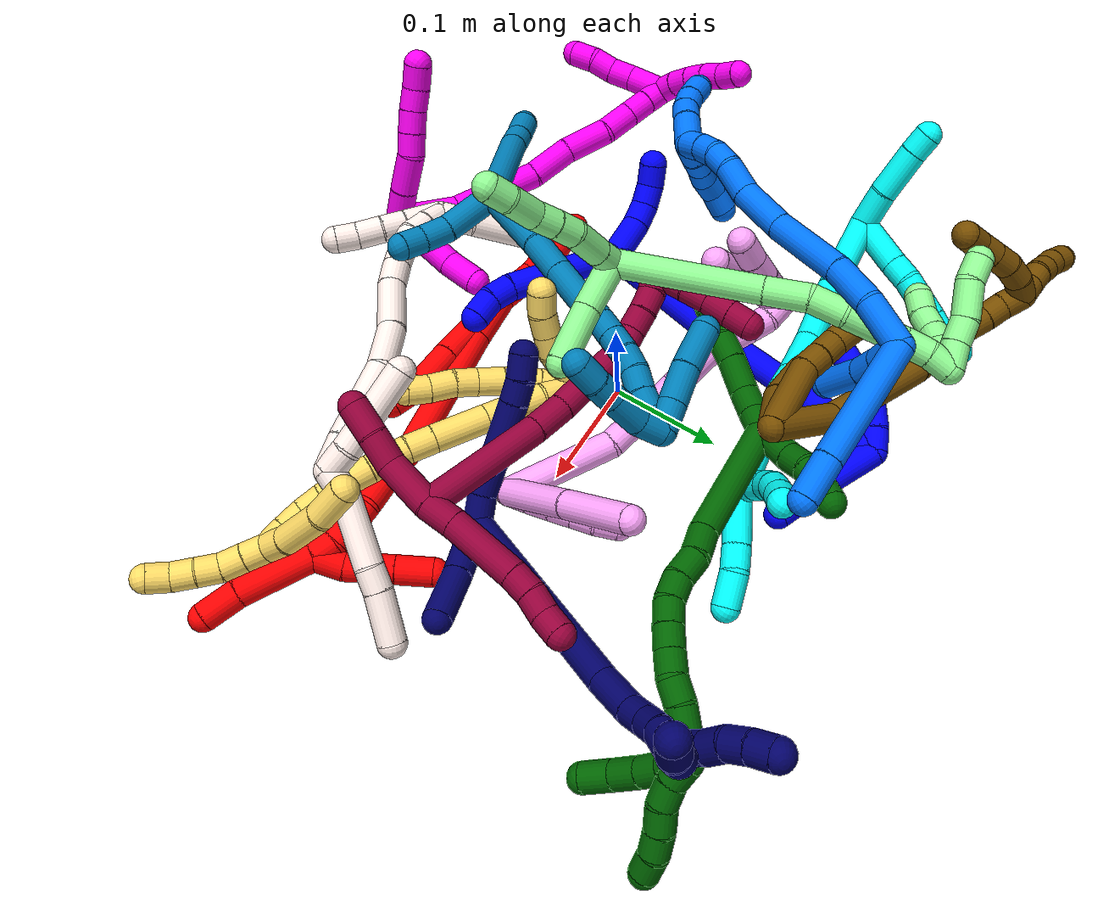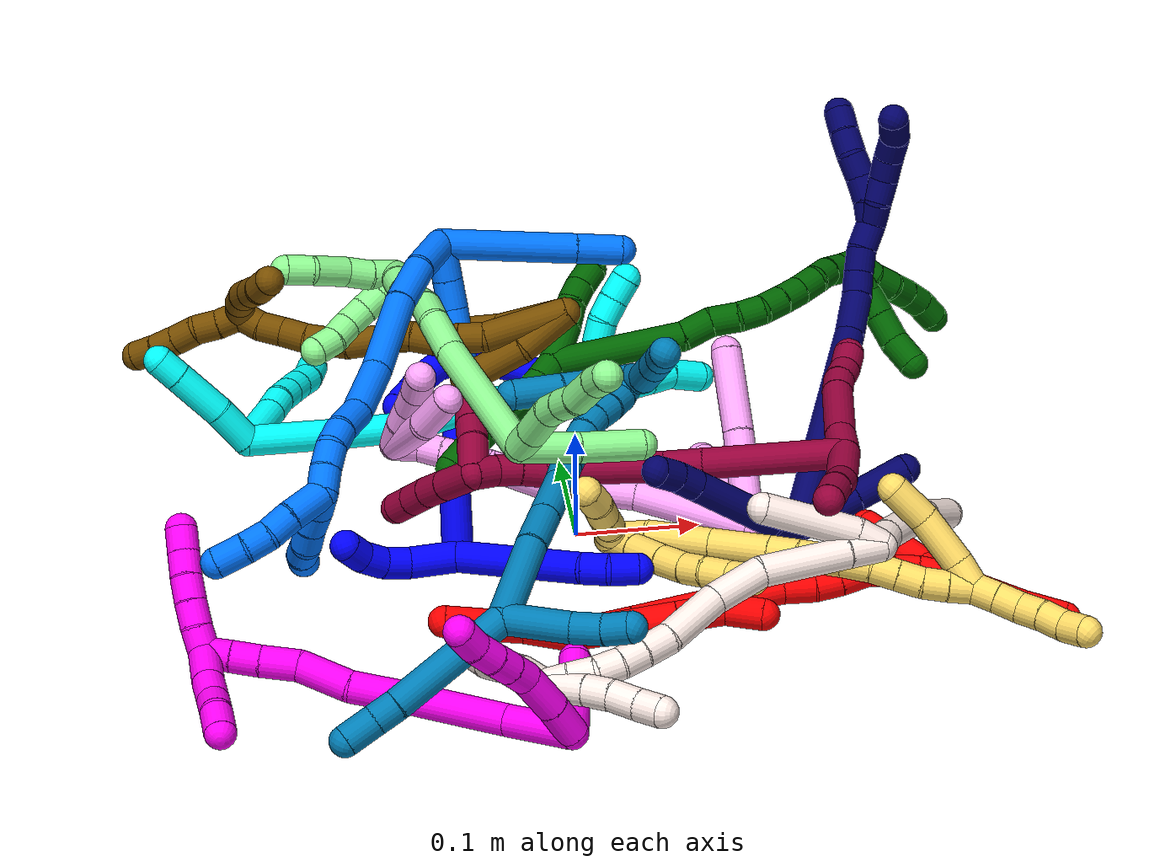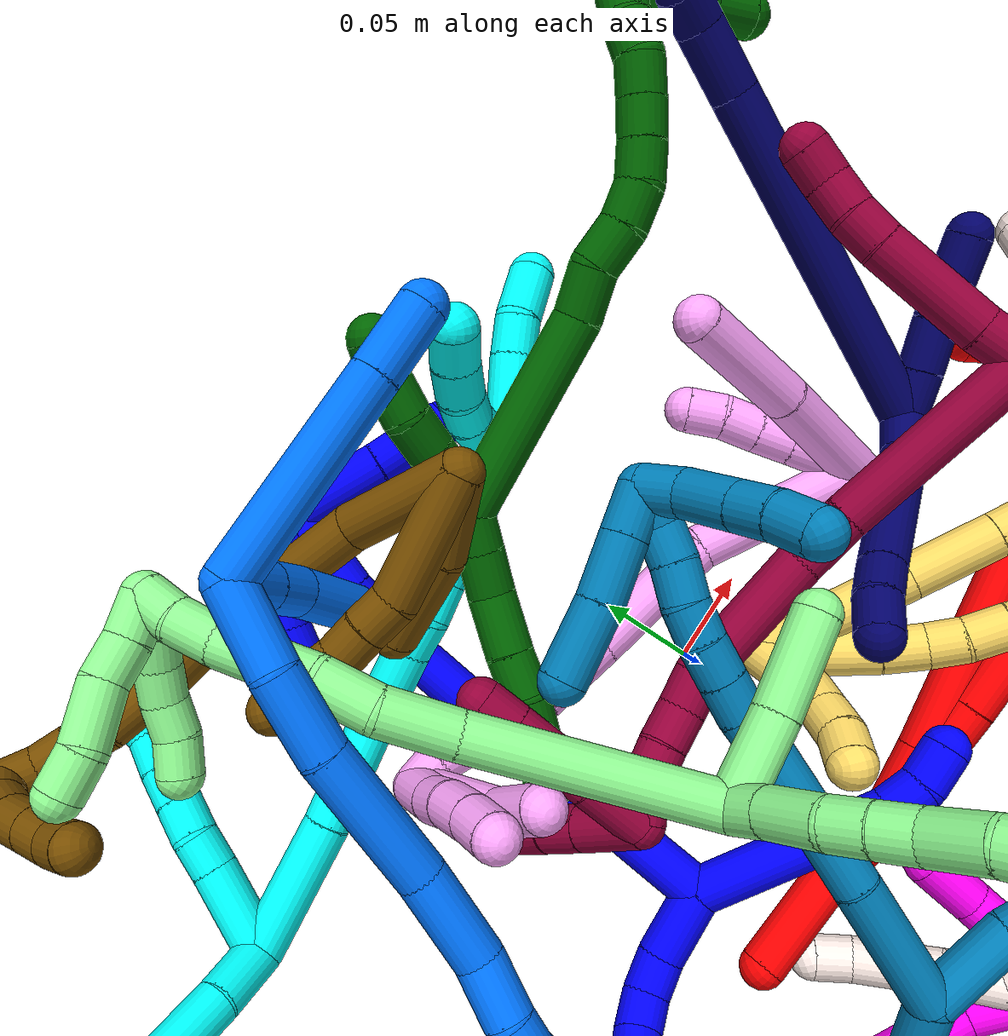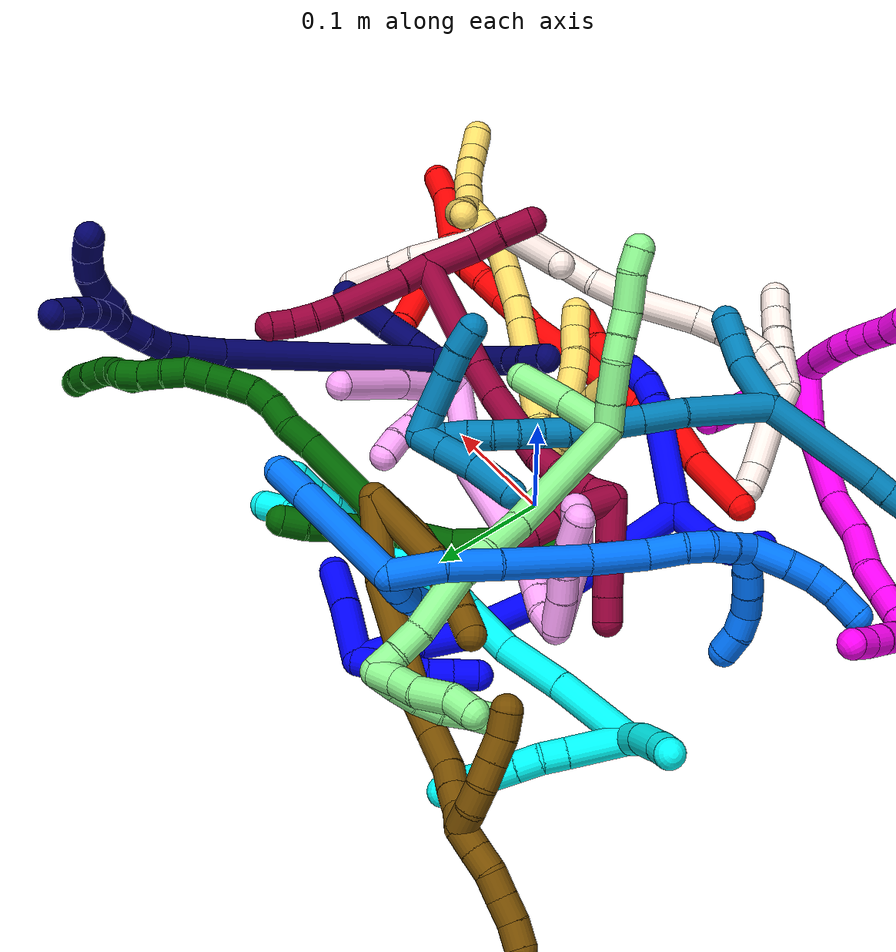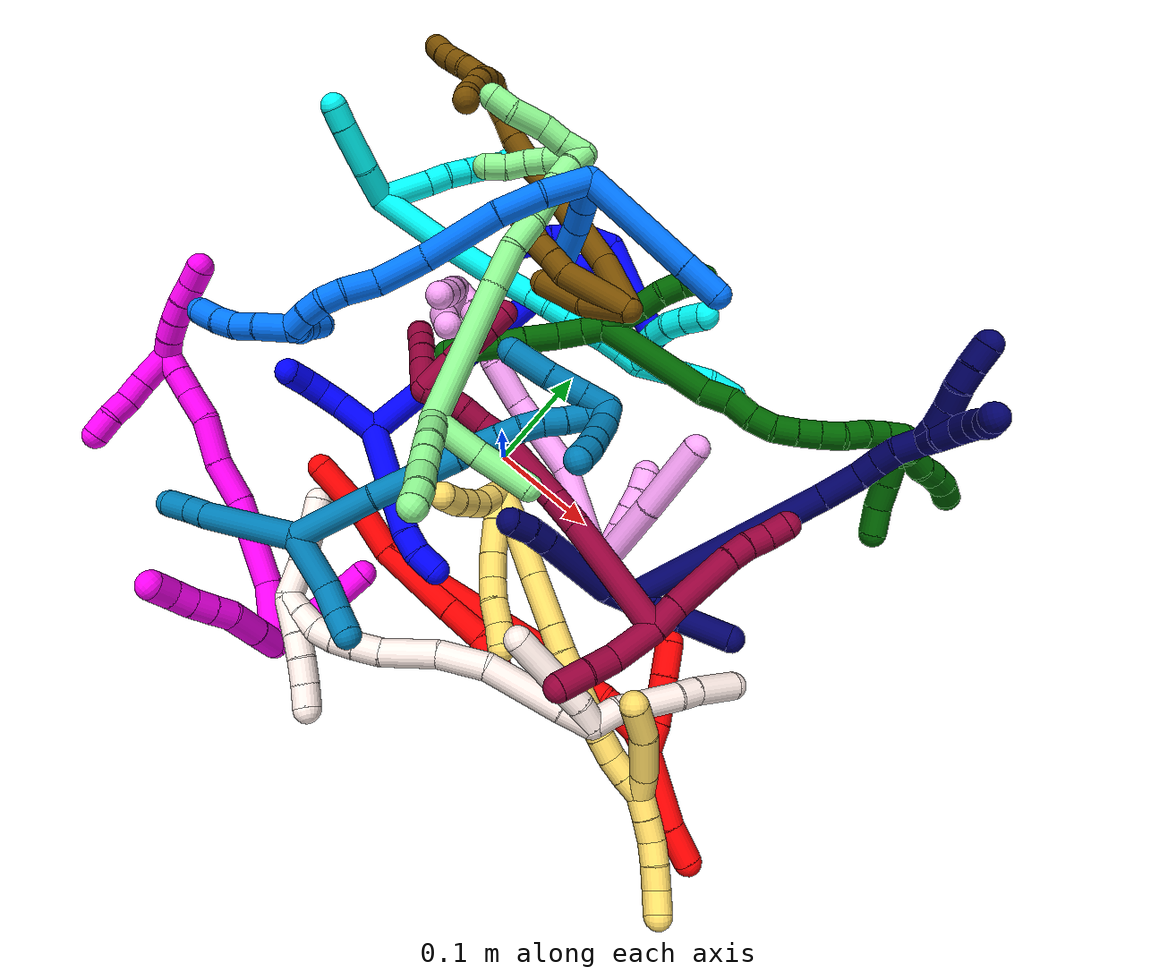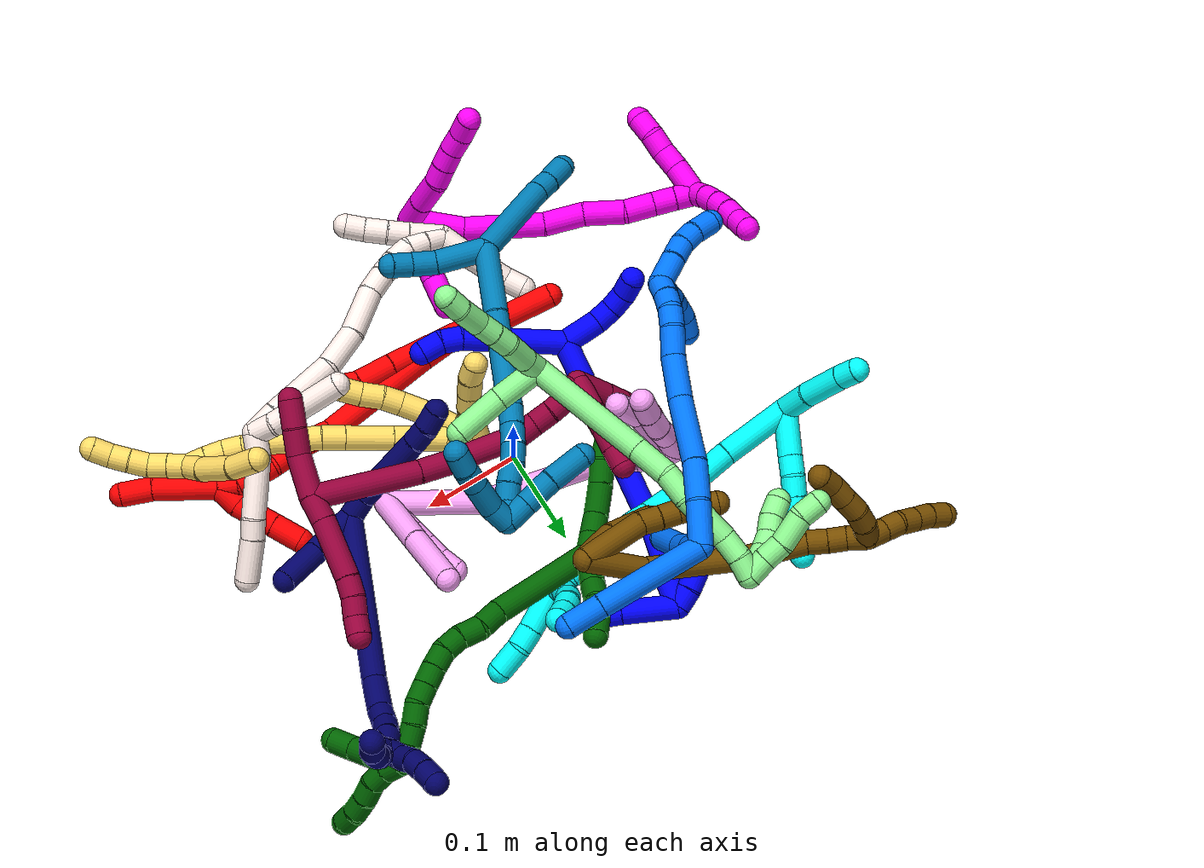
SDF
<sdf version="1.7">
 <world name="default">
  <plugin name="TubeGeneratorPlugin" filename="libtube_generator_plugin.so"/>
  <model name="photoneo_s_sensor">
   <static>1</static>
   <pose>0 0 2 1.57079 1.57079 3.14159</pose>
   <link name="link">
    <inertial><mass>0.1</mass></inertial>
    <sensor name="sensor" type="depth">
     <update_rate>30</update_rate>
     <camera>
      <horizontal_fov>1.22</horizontal_fov>
      <image><width>1920</width><height>1200</height><format>B8G8R8</format></image>
      <clip><near>0.1</near><far>4</far></clip>
      <depth_camera><output>points</output></depth_camera>
     </camera>
     <plugin name="camera_plugin" filename="libgazebo_ros_depth_camera.so">
      <baseline>0.2</baseline>
      <alwaysOn>1</alwaysOn>
      <updateRate>0.0</updateRate>
      <cameraName>camera_ir</cameraName>
      <imageTopicName>/camera/color/image_raw</imageTopicName>
      <cameraInfoTopicName>/camera/color/camera_info</cameraInfoTopicName>
      <depthImageTopicName>/camera/depth/image_raw</depthImageTopicName>
      <depthImageCameraInfoTopicName>/camera/depth/camera_info</depthImageCameraInfoTopicName>
      <pointCloudTopicName>/camera/depth/points</pointCloudTopicName>
      <frameName>fr_optical</frameName>
      <pointCloudCutoff>0.1</pointCloudCutoff>
      <pointCloudCutoffMax>2.0</pointCloudCutoffMax>
      <distortionK1>0</distortionK1>
      <distortionK2>0</distortionK2>
      <distortionK3>0</distortionK3>
      <distortionT1>0</distortionT1>
      <distortionT2>0</distortionT2>
      <CxPrime>0</CxPrime>
      <Cx>0</Cx>
      <Cy>0</Cy>
      <focalLength>0</focalLength>
      <hackBaseline>0</hackBaseline>
     </plugin>
    </sensor>
   </link>
  </model>
  <gravity>0 0 -9.8</gravity>
  <magnetic_field>6e-06 2.3e-05 -4.2e-05</magnetic_field>
  <atmosphere type="adiabatic"/>
  <physics name="default_physics" default="0" type="ode">
   <max_step_size>0.003</max_step_size>
   <real_time_factor>1</real_time_factor>
   <real_time_update_rate>1000</real_time_update_rate>
   <max_contacts>10000</max_contacts>
   <ode>
    <solver>
     <type>quick</type>
     <iters>100</iters>
     <sor>1.3</sor>
     <use_dynamic_moi_rescaling>0</use_dynamic_moi_rescaling>
    </solver>
    <constraints>
     <contact_max_correcting_vel>0</contact_max_correcting_vel>
     <contact_surface_layer>0.001</contact_surface_layer>
     <cfm>0</cfm>
     <erp>0.2</erp>
    </constraints>
   </ode>
  </physics>
  <scene><ambient>0.4 0.4 0.4 1</ambient><background>0.7 0.7 0.7 1</background><shadows>0</shadows></scene>
  <audio><device>default</device></audio>
  <spherical_coordinates>
   <surface_model>EARTH_WGS84</surface_model>
   <latitude_deg>0</latitude_deg>
   <longitude_deg>0</longitude_deg>
   <elevation>0</elevation>
   <heading_deg>0</heading_deg>
  </spherical_coordinates>
  <model name="bin">
   <static>1</static>
   <link name="bottom">
    <collision name="collision-bottom">
     <pose>0 0 -0.01 0 -0 0</pose>
     <geometry><box><size>0.8 0.6 0.02</size></box></geometry>
     <surface>
      <friction><ode><mu>100</mu><mu2>100</mu2></ode></friction>
      <contact><collide_bitmask>65535</collide_bitmask></contact>
     </surface>
    </collision>
   </link>
   <link name="west_wall">
    <collision name="collision-west_wall">
     <pose>-0.41 0 0.1 0 -0 0</pose>
     <geometry><box><size>0.02 0.6 0.2</size></box></geometry>
     <surface>
      <friction><ode><mu>100</mu><mu2>100</mu2></ode></friction>
      <contact><collide_bitmask>65535</collide_bitmask></contact>
     </surface>
    </collision>
   </link>
   <link name="east_wall">
    <collision name="collision-east_wall">
     <pose>0.41 0 0.1 0 -0 0</pose>
     <geometry><box><size>0.02 0.6 0.2</size></box></geometry>
     <surface>
      <friction><ode><mu>100</mu><mu2>100</mu2></ode></friction>
      <contact><collide_bitmask>65535</collide_bitmask></contact>
     </surface>
    </collision>
   </link>
   <link name="south_wall">
    <collision name="collision-south_wall">
     <pose>0 -0.31 0.1 0 -0 0</pose>
     <geometry><box><size>0.8 0.02 0.2</size></box></geometry>
     <surface>
      <friction><ode><mu>100</mu><mu2>100</mu2></ode></friction>
      <contact><collide_bitmask>65535</collide_bitmask></contact>
     </surface>
    </collision>
   </link>
   <link name="north_wall">
    <collision name="collision-north_wall">
     <pose>0 0.31 0.1 0 -0 0</pose>
     <geometry><box><size>0.8 0.02 0.2</size></box></geometry>
     <surface>
      <friction><ode><mu>100</mu><mu2>100</mu2></ode></friction>
      <contact><collide_bitmask>65535</collide_bitmask></contact>
     </surface>
    </collision>
   </link>
  </model>
  <model name="1">
   <static>0</static>
   <link name="1">
    <collision name="collision-cylinder-e_1_2_8">
     <pose>0.005854 -0.024749 0.046782 0.486591 0.110167 0.027371</pose>
     <geometry><cylinder><radius>0.0125</radius><length>0.106496</length></cylinder></geometry>
     <surface>
      <friction><ode><mu>1.16</mu><mu2>1.16</mu2><slip1>0</slip1><slip2>0</slip2></ode></friction>
      <contact><ode><kp>1e+06</kp><kd>1</kd><max_vel>0</max_vel><min_depth>0.001</min_depth></ode></contact>
     </surface>
    </collision>
    <visual name="visual-cylinder-e_1_2_8">
     <pose>0.005854 -0.024749 0.046782 0.486591 0.110167 0.027371</pose>
     <geometry><cylinder><radius>0.0125</radius><length>0.106496</length></cylinder></geometry>
     <material><ambient>0 0 1 1</ambient></material>
    </visual>
    <collision name="collision-cylinder-e_2_8_9">
     <pose>0.014379 -0.052658 0.103338 0.312809 0.254316 0.040316</pose>
     <geometry><cylinder><radius>0.0125</radius><length>0.021227</length></cylinder></geometry>
     <surface>
      <friction><ode><mu>1.16</mu><mu2>1.16</mu2><slip1>0</slip1><slip2>0</slip2></ode></friction>
      <contact><ode><kp>1e+06</kp><kd>1</kd><max_vel>0</max_vel><min_depth>0.001</min_depth></ode></contact>
     </surface>
    </collision>
    <visual name="visual-cylinder-e_2_8_9">
     <pose>0.014379 -0.052658 0.103338 0.312809 0.254316 0.040316</pose>
     <geometry><cylinder><radius>0.0125</radius><length>0.021227</length></cylinder></geometry>
     <material><ambient>0 0 1 1</ambient></material>
    </visual>
    <collision name="collision-cylinder-e_3_9_6">
     <pose>0.021757 -0.055951 0.123206 0.013086 0.436407 0.002902</pose>
     <geometry><cylinder><radius>0.0125</radius><length>0.022277</length></cylinder></geometry>
     <surface>
      <friction><ode><mu>1.16</mu><mu2>1.16</mu2><slip1>0</slip1><slip2>0</slip2></ode></friction>
      <contact><ode><kp>1e+06</kp><kd>1</kd><max_vel>0</max_vel><min_depth>0.001</min_depth></ode></contact>
     </surface>
    </collision>
    <visual name="visual-cylinder-e_3_9_6">
     <pose>0.021757 -0.055951 0.123206 0.013086 0.436407 0.002902</pose>
     <geometry><cylinder><radius>0.0125</radius><length>0.022277</length></cylinder></geometry>
     <material><ambient>0 0 1 1</ambient></material>
    </visual>
    <collision name="collision-cylinder-e_1_2_10">
     <pose>-0.007112 -0.001435 -0.018073 3.06234 -0.373864 -2.72834</pose>
     <geometry><cylinder><radius>0.0125</radius><length>0.03895</length></cylinder></geometry>
     <surface>
      <friction><ode><mu>1.16</mu><mu2>1.16</mu2><slip1>0</slip1><slip2>0</slip2></ode></friction>
      <contact><ode><kp>1e+06</kp><kd>1</kd><max_vel>0</max_vel><min_depth>0.001</min_depth></ode></contact>
     </surface>
    </collision>
    <visual name="visual-cylinder-e_1_2_10">
     <pose>-0.007112 -0.001435 -0.018073 3.06234 -0.373864 -2.72834</pose>
     <geometry><cylinder><radius>0.0125</radius><length>0.03895</length></cylinder></geometry>
     <material><ambient>0 0 1 1</ambient></material>
    </visual>
    <collision name="collision-cylinder-e_2_10_11">
     <pose>-0.020234 -0.004262 -0.044583 2.97813 -0.612555 -2.63468</pose>
     <geometry><cylinder><radius>0.0125</radius><length>0.020904</length></cylinder></geometry>
     <surface>
      <friction><ode><mu>1.16</mu><mu2>1.16</mu2><slip1>0</slip1><slip2>0</slip2></ode></friction>
      <contact><ode><kp>1e+06</kp><kd>1</kd><max_vel>0</max_vel><min_depth>0.001</min_depth></ode></contact>
     </surface>
    </collision>
    <visual name="visual-cylinder-e_2_10_11">
     <pose>-0.020234 -0.004262 -0.044583 2.97813 -0.612555 -2.63468</pose>
     <geometry><cylinder><radius>0.0125</radius><length>0.020904</length></cylinder></geometry>
     <material><ambient>0 0 1 1</ambient></material>
    </visual>
    <collision name="collision-cylinder-e_3_11_12">
     <pose>-0.03444 -0.007175 -0.058647 2.87759 -0.952686 -2.63786</pose>
     <geometry><cylinder><radius>0.0125</radius><length>0.020115</length></cylinder></geometry>
     <surface>
      <friction><ode><mu>1.16</mu><mu2>1.16</mu2><slip1>0</slip1><slip2>0</slip2></ode></friction>
      <contact><ode><kp>1e+06</kp><kd>1</kd><max_vel>0</max_vel><min_depth>0.001</min_depth></ode></contact>
     </surface>
    </collision>
    <visual name="visual-cylinder-e_3_11_12">
     <pose>-0.03444 -0.007175 -0.058647 2.87759 -0.952686 -2.63786</pose>
     <geometry><cylinder><radius>0.0125</radius><length>0.020115</length></cylinder></geometry>
     <material><ambient>0 0 1 1</ambient></material>
    </visual>
    <collision name="collision-cylinder-e_4_12_5">
     <pose>-0.05216 -0.010342 -0.066902 2.58211 -1.25591 -2.388</pose>
     <geometry><cylinder><radius>0.0125</radius><length>0.020031</length></cylinder></geometry>
     <surface>
      <friction><ode><mu>1.16</mu><mu2>1.16</mu2><slip1>0</slip1><slip2>0</slip2></ode></friction>
      <contact><ode><kp>1e+06</kp><kd>1</kd><max_vel>0</max_vel><min_depth>0.001</min_depth></ode></contact>
     </surface>
    </collision>
    <visual name="visual-cylinder-e_4_12_5">
     <pose>-0.05216 -0.010342 -0.066902 2.58211 -1.25591 -2.388</pose>
     <geometry><cylinder><radius>0.0125</radius><length>0.020031</length></cylinder></geometry>
     <material><ambient>0 0 1 1</ambient></material>
    </visual>
    <collision name="collision-cylinder-e_1_2_13">
     <pose>0.019907 0.057557 -0.003417 -1.6301 0.332443 -0.352361</pose>
     <geometry><cylinder><radius>0.0125</radius><length>0.121997</length></cylinder></geometry>
     <surface>
      <friction><ode><mu>1.16</mu><mu2>1.16</mu2><slip1>0</slip1><slip2>0</slip2></ode></friction>
      <contact><ode><kp>1e+06</kp><kd>1</kd><max_vel>0</max_vel><min_depth>0.001</min_depth></ode></contact>
     </surface>
    </collision>
    <visual name="visual-cylinder-e_1_2_13">
     <pose>0.019907 0.057557 -0.003417 -1.6301 0.332443 -0.352361</pose>
     <geometry><cylinder><radius>0.0125</radius><length>0.121997</length></cylinder></geometry>
     <material><ambient>0 0 1 1</ambient></material>
    </visual>
    <collision name="collision-cylinder-e_2_13_14">
     <pose>0.045218 0.159178 -0.003071 -1.48558 0.121594 -0.111672</pose>
     <geometry><cylinder><radius>0.0125</radius><length>0.089106</length></cylinder></geometry>
     <surface>
      <friction><ode><mu>1.16</mu><mu2>1.16</mu2><slip1>0</slip1><slip2>0</slip2></ode></friction>
      <contact><ode><kp>1e+06</kp><kd>1</kd><max_vel>0</max_vel><min_depth>0.001</min_depth></ode></contact>
     </surface>
    </collision>
    <visual name="visual-cylinder-e_2_13_14">
     <pose>0.045218 0.159178 -0.003071 -1.48558 0.121594 -0.111672</pose>
     <geometry><cylinder><radius>0.0125</radius><length>0.089106</length></cylinder></geometry>
     <material><ambient>0 0 1 1</ambient></material>
    </visual>
    <collision name="collision-cylinder-e_3_14_15">
     <pose>0.050797 0.221143 0.005558 -1.30544 0.009414 -0.007197</pose>
     <geometry><cylinder><radius>0.0125</radius><length>0.037103</length></cylinder></geometry>
     <surface>
      <friction><ode><mu>1.16</mu><mu2>1.16</mu2><slip1>0</slip1><slip2>0</slip2></ode></friction>
      <contact><ode><kp>1e+06</kp><kd>1</kd><max_vel>0</max_vel><min_depth>0.001</min_depth></ode></contact>
     </surface>
    </collision>
    <visual name="visual-cylinder-e_3_14_15">
     <pose>0.050797 0.221143 0.005558 -1.30544 0.009414 -0.007197</pose>
     <geometry><cylinder><radius>0.0125</radius><length>0.037103</length></cylinder></geometry>
     <material><ambient>0 0 1 1</ambient></material>
    </visual>
    <collision name="collision-cylinder-e_4_15_16">
     <pose>0.052923 0.250616 0.014338 -1.24454 0.158417 -0.113754</pose>
     <geometry><cylinder><radius>0.0125</radius><length>0.024742</length></cylinder></geometry>
     <surface>
      <friction><ode><mu>1.16</mu><mu2>1.16</mu2><slip1>0</slip1><slip2>0</slip2></ode></friction>
      <contact><ode><kp>1e+06</kp><kd>1</kd><max_vel>0</max_vel><min_depth>0.001</min_depth></ode></contact>
     </surface>
    </collision>
    <visual name="visual-cylinder-e_4_15_16">
     <pose>0.052923 0.250616 0.014338 -1.24454 0.158417 -0.113754</pose>
     <geometry><cylinder><radius>0.0125</radius><length>0.024742</length></cylinder></geometry>
     <material><ambient>0 0 1 1</ambient></material>
    </visual>
    <collision name="collision-cylinder-e_5_16_1">
     <pose>0.055643 0.275503 0.020504 -1.40334 0.056801 -0.048008</pose>
     <geometry><cylinder><radius>0.0125</radius><length>0.027052</length></cylinder></geometry>
     <surface>
      <friction><ode><mu>1.16</mu><mu2>1.16</mu2><slip1>0</slip1><slip2>0</slip2></ode></friction>
      <contact><ode><kp>1e+06</kp><kd>1</kd><max_vel>0</max_vel><min_depth>0.001</min_depth></ode></contact>
     </surface>
    </collision>
    <visual name="visual-cylinder-e_5_16_1">
     <pose>0.055643 0.275503 0.020504 -1.40334 0.056801 -0.048008</pose>
     <geometry><cylinder><radius>0.0125</radius><length>0.027052</length></cylinder></geometry>
     <material><ambient>0 0 1 1</ambient></material>
    </visual>
    <collision name="collision-cylinder-e_1_1_17">
     <pose>0.066678 0.276629 0.046121 0.480833 0.371485 0.09207</pose>
     <geometry><cylinder><radius>0.0125</radius><length>0.056568</length></cylinder></geometry>
     <surface>
      <friction><ode><mu>1.16</mu><mu2>1.16</mu2><slip1>0</slip1><slip2>0</slip2></ode></friction>
      <contact><ode><kp>1e+06</kp><kd>1</kd><max_vel>0</max_vel><min_depth>0.001</min_depth></ode></contact>
     </surface>
    </collision>
    <visual name="visual-cylinder-e_1_1_17">
     <pose>0.066678 0.276629 0.046121 0.480833 0.371485 0.09207</pose>
     <geometry><cylinder><radius>0.0125</radius><length>0.056568</length></cylinder></geometry>
     <material><ambient>0 0 1 1</ambient></material>
    </visual>
    <collision name="collision-cylinder-e_2_17_4">
     <pose>0.085907 0.255994 0.087375 0.441129 0.425408 0.096771</pose>
     <geometry><cylinder><radius>0.0125</radius><length>0.043432</length></cylinder></geometry>
     <surface>
      <friction><ode><mu>1.16</mu><mu2>1.16</mu2><slip1>0</slip1><slip2>0</slip2></ode></friction>
      <contact><ode><kp>1e+06</kp><kd>1</kd><max_vel>0</max_vel><min_depth>0.001</min_depth></ode></contact>
     </surface>
    </collision>
    <visual name="visual-cylinder-e_2_17_4">
     <pose>0.085907 0.255994 0.087375 0.441129 0.425408 0.096771</pose>
     <geometry><cylinder><radius>0.0125</radius><length>0.043432</length></cylinder></geometry>
     <material><ambient>0 0 1 1</ambient></material>
    </visual>
    <collision name="collision-cylinder-e_1_1_18">
     <pose>0.050644 0.284771 0.015658 2.62336 -0.614612 -1.74984</pose>
     <geometry><cylinder><radius>0.0125</radius><length>0.02</length></cylinder></geometry>
     <surface>
      <friction><ode><mu>1.16</mu><mu2>1.16</mu2><slip1>0</slip1><slip2>0</slip2></ode></friction>
      <contact><ode><kp>1e+06</kp><kd>1</kd><max_vel>0</max_vel><min_depth>0.001</min_depth></ode></contact>
     </surface>
    </collision>
    <visual name="visual-cylinder-e_1_1_18">
     <pose>0.050644 0.284771 0.015658 2.62336 -0.614612 -1.74984</pose>
     <geometry><cylinder><radius>0.0125</radius><length>0.02</length></cylinder></geometry>
     <material><ambient>0 0 1 1</ambient></material>
    </visual>
    <collision name="collision-cylinder-e_2_18_19">
     <pose>0.039955 0.27512 0.001901 2.4421 -0.514738 -1.25019</pose>
     <geometry><cylinder><radius>0.0125</radius><length>0.02</length></cylinder></geometry>
     <surface>
      <friction><ode><mu>1.16</mu><mu2>1.16</mu2><slip1>0</slip1><slip2>0</slip2></ode></friction>
      <contact><ode><kp>1e+06</kp><kd>1</kd><max_vel>0</max_vel><min_depth>0.001</min_depth></ode></contact>
     </surface>
    </collision>
    <visual name="visual-cylinder-e_2_18_19">
     <pose>0.039955 0.27512 0.001901 2.4421 -0.514738 -1.25019</pose>
     <geometry><cylinder><radius>0.0125</radius><length>0.02</length></cylinder></geometry>
     <material><ambient>0 0 1 1</ambient></material>
    </visual>
    <collision name="collision-cylinder-e_3_19_20">
     <pose>0.032509 0.26271 -0.011637 2.36138 -0.255002 -0.604455</pose>
     <geometry><cylinder><radius>0.0125</radius><length>0.02</length></cylinder></geometry>
     <surface>
      <friction><ode><mu>1.16</mu><mu2>1.16</mu2><slip1>0</slip1><slip2>0</slip2></ode></friction>
      <contact><ode><kp>1e+06</kp><kd>1</kd><max_vel>0</max_vel><min_depth>0.001</min_depth></ode></contact>
     </surface>
    </collision>
    <visual name="visual-cylinder-e_3_19_20">
     <pose>0.032509 0.26271 -0.011637 2.36138 -0.255002 -0.604455</pose>
     <geometry><cylinder><radius>0.0125</radius><length>0.02</length></cylinder></geometry>
     <material><ambient>0 0 1 1</ambient></material>
    </visual>
    <collision name="collision-cylinder-e_4_20_21">
     <pose>0.028012 0.247563 -0.023668 2.12422 -0.19872 -0.3538</pose>
     <geometry><cylinder><radius>0.0125</radius><length>0.02</length></cylinder></geometry>
     <surface>
      <friction><ode><mu>1.16</mu><mu2>1.16</mu2><slip1>0</slip1><slip2>0</slip2></ode></friction>
      <contact><ode><kp>1e+06</kp><kd>1</kd><max_vel>0</max_vel><min_depth>0.001</min_depth></ode></contact>
     </surface>
    </collision>
    <visual name="visual-cylinder-e_4_20_21">
     <pose>0.028012 0.247563 -0.023668 2.12422 -0.19872 -0.3538</pose>
     <geometry><cylinder><radius>0.0125</radius><length>0.02</length></cylinder></geometry>
     <material><ambient>0 0 1 1</ambient></material>
    </visual>
    <collision name="collision-cylinder-e_5_21_3">
     <pose>0.023746 0.23108 -0.034152 2.15051 -0.231322 -0.423432</pose>
     <geometry><cylinder><radius>0.0125</radius><length>0.02</length></cylinder></geometry>
     <surface>
      <friction><ode><mu>1.16</mu><mu2>1.16</mu2><slip1>0</slip1><slip2>0</slip2></ode></friction>
      <contact><ode><kp>1e+06</kp><kd>1</kd><max_vel>0</max_vel><min_depth>0.001</min_depth></ode></contact>
     </surface>
    </collision>
    <visual name="visual-cylinder-e_5_21_3">
     <pose>0.023746 0.23108 -0.034152 2.15051 -0.231322 -0.423432</pose>
     <geometry><cylinder><radius>0.0125</radius><length>0.02</length></cylinder></geometry>
     <material><ambient>0 0 1 1</ambient></material>
    </visual>
    <collision name="collision-sphere-3">
     <pose>0.021453 0.222936 -0.039484 0 -0 0</pose>
     <geometry><sphere><radius>0.0125</radius></sphere></geometry>
     <surface>
      <friction><ode><mu>1.16</mu><mu2>1.16</mu2><slip1>0</slip1><slip2>0</slip2></ode></friction>
      <contact><ode><kp>1e+06</kp><kd>1</kd><max_vel>0</max_vel><min_depth>0.001</min_depth></ode></contact>
     </surface>
    </collision>
    <visual name="visual-sphere-3">
     <pose>0.021453 0.222936 -0.039484 0 -0 0</pose>
     <geometry><sphere><radius>0.0125</radius></sphere></geometry>
     <material><ambient>0 0 1 1</ambient></material>
    </visual>
    <collision name="collision-sphere-21">
     <pose>0.026038 0.239223 -0.02882 0 -0 0</pose>
     <geometry><sphere><radius>0.0125</radius></sphere></geometry>
     <surface>
      <friction><ode><mu>1.16</mu><mu2>1.16</mu2><slip1>0</slip1><slip2>0</slip2></ode></friction>
      <contact><ode><kp>1e+06</kp><kd>1</kd><max_vel>0</max_vel><min_depth>0.001</min_depth></ode></contact>
     </surface>
    </collision>
    <visual name="visual-sphere-21">
     <pose>0.026038 0.239223 -0.02882 0 -0 0</pose>
     <geometry><sphere><radius>0.0125</radius></sphere></geometry>
     <material><ambient>0 0 1 1</ambient></material>
    </visual>
    <collision name="collision-sphere-20">
     <pose>0.029987 0.255903 -0.018515 0 -0 0</pose>
     <geometry><sphere><radius>0.0125</radius></sphere></geometry>
     <surface>
      <friction><ode><mu>1.16</mu><mu2>1.16</mu2><slip1>0</slip1><slip2>0</slip2></ode></friction>
      <contact><ode><kp>1e+06</kp><kd>1</kd><max_vel>0</max_vel><min_depth>0.001</min_depth></ode></contact>
     </surface>
    </collision>
    <visual name="visual-sphere-20">
     <pose>0.029987 0.255903 -0.018515 0 -0 0</pose>
     <geometry><sphere><radius>0.0125</radius></sphere></geometry>
     <material><ambient>0 0 1 1</ambient></material>
    </visual>
    <collision name="collision-sphere-19">
     <pose>0.035032 0.269516 -0.00476 0 -0 0</pose>
     <geometry><sphere><radius>0.0125</radius></sphere></geometry>
     <surface>
      <friction><ode><mu>1.16</mu><mu2>1.16</mu2><slip1>0</slip1><slip2>0</slip2></ode></friction>
      <contact><ode><kp>1e+06</kp><kd>1</kd><max_vel>0</max_vel><min_depth>0.001</min_depth></ode></contact>
     </surface>
    </collision>
    <visual name="visual-sphere-19">
     <pose>0.035032 0.269516 -0.00476 0 -0 0</pose>
     <geometry><sphere><radius>0.0125</radius></sphere></geometry>
     <material><ambient>0 0 1 1</ambient></material>
    </visual>
    <collision name="collision-sphere-11">
     <pose>-0.026244 -0.005654 -0.05302 0 -0 0</pose>
     <geometry><sphere><radius>0.0125</radius></sphere></geometry>
     <surface>
      <friction><ode><mu>1.16</mu><mu2>1.16</mu2><slip1>0</slip1><slip2>0</slip2></ode></friction>
      <contact><ode><kp>1e+06</kp><kd>1</kd><max_vel>0</max_vel><min_depth>0.001</min_depth></ode></contact>
     </surface>
    </collision>
    <visual name="visual-sphere-11">
     <pose>-0.026244 -0.005654 -0.05302 0 -0 0</pose>
     <geometry><sphere><radius>0.0125</radius></sphere></geometry>
     <material><ambient>0 0 1 1</ambient></material>
    </visual>
    <collision name="collision-sphere-10">
     <pose>-0.014225 -0.002871 -0.036145 0 -0 0</pose>
     <geometry><sphere><radius>0.0125</radius></sphere></geometry>
     <surface>
      <friction><ode><mu>1.16</mu><mu2>1.16</mu2><slip1>0</slip1><slip2>0</slip2></ode></friction>
      <contact><ode><kp>1e+06</kp><kd>1</kd><max_vel>0</max_vel><min_depth>0.001</min_depth></ode></contact>
     </surface>
    </collision>
    <visual name="visual-sphere-10">
     <pose>-0.014225 -0.002871 -0.036145 0 -0 0</pose>
     <geometry><sphere><radius>0.0125</radius></sphere></geometry>
     <material><ambient>0 0 1 1</ambient></material>
    </visual>
    <collision name="collision-sphere-6">
     <pose>0.026465 -0.056084 0.133299 0 -0 0</pose>
     <geometry><sphere><radius>0.0125</radius></sphere></geometry>
     <surface>
      <friction><ode><mu>1.16</mu><mu2>1.16</mu2><slip1>0</slip1><slip2>0</slip2></ode></friction>
      <contact><ode><kp>1e+06</kp><kd>1</kd><max_vel>0</max_vel><min_depth>0.001</min_depth></ode></contact>
     </surface>
    </collision>
    <visual name="visual-sphere-6">
     <pose>0.026465 -0.056084 0.133299 0 -0 0</pose>
     <geometry><sphere><radius>0.0125</radius></sphere></geometry>
     <material><ambient>0 0 1 1</ambient></material>
    </visual>
    <collision name="collision-sphere-9">
     <pose>0.017049 -0.055819 0.113112 0 -0 0</pose>
     <geometry><sphere><radius>0.0125</radius></sphere></geometry>
     <surface>
      <friction><ode><mu>1.16</mu><mu2>1.16</mu2><slip1>0</slip1><slip2>0</slip2></ode></friction>
      <contact><ode><kp>1e+06</kp><kd>1</kd><max_vel>0</max_vel><min_depth>0.001</min_depth></ode></contact>
     </surface>
    </collision>
    <visual name="visual-sphere-9">
     <pose>0.017049 -0.055819 0.113112 0 -0 0</pose>
     <geometry><sphere><radius>0.0125</radius></sphere></geometry>
     <material><ambient>0 0 1 1</ambient></material>
    </visual>
    <collision name="collision-sphere-2">
     <geometry><sphere><radius>0.0125</radius></sphere></geometry>
     <surface>
      <friction><ode><mu>1.16</mu><mu2>1.16</mu2><slip1>0</slip1><slip2>0</slip2></ode></friction>
      <contact><ode><kp>1e+06</kp><kd>1</kd><max_vel>0</max_vel><min_depth>0.001</min_depth></ode></contact>
     </surface>
    </collision>
    <visual name="visual-sphere-2">
     <geometry><sphere><radius>0.0125</radius></sphere></geometry>
     <material><ambient>0 0 1 1</ambient></material>
    </visual>
    <collision name="collision-sphere-8">
     <pose>0.011709 -0.049497 0.093565 0 -0 0</pose>
     <geometry><sphere><radius>0.0125</radius></sphere></geometry>
     <surface>
      <friction><ode><mu>1.16</mu><mu2>1.16</mu2><slip1>0</slip1><slip2>0</slip2></ode></friction>
      <contact><ode><kp>1e+06</kp><kd>1</kd><max_vel>0</max_vel><min_depth>0.001</min_depth></ode></contact>
     </surface>
    </collision>
    <visual name="visual-sphere-8">
     <pose>0.011709 -0.049497 0.093565 0 -0 0</pose>
     <geometry><sphere><radius>0.0125</radius></sphere></geometry>
     <material><ambient>0 0 1 1</ambient></material>
    </visual>
    <collision name="collision-sphere-12">
     <pose>-0.042637 -0.008696 -0.064273 0 -0 0</pose>
     <geometry><sphere><radius>0.0125</radius></sphere></geometry>
     <surface>
      <friction><ode><mu>1.16</mu><mu2>1.16</mu2><slip1>0</slip1><slip2>0</slip2></ode></friction>
      <contact><ode><kp>1e+06</kp><kd>1</kd><max_vel>0</max_vel><min_depth>0.001</min_depth></ode></contact>
     </surface>
    </collision>
    <visual name="visual-sphere-12">
     <pose>-0.042637 -0.008696 -0.064273 0 -0 0</pose>
     <geometry><sphere><radius>0.0125</radius></sphere></geometry>
     <material><ambient>0 0 1 1</ambient></material>
    </visual>
    <collision name="collision-sphere-5">
     <pose>-0.061684 -0.011988 -0.069531 0 -0 0</pose>
     <geometry><sphere><radius>0.0125</radius></sphere></geometry>
     <surface>
      <friction><ode><mu>1.16</mu><mu2>1.16</mu2><slip1>0</slip1><slip2>0</slip2></ode></friction>
      <contact><ode><kp>1e+06</kp><kd>1</kd><max_vel>0</max_vel><min_depth>0.001</min_depth></ode></contact>
     </surface>
    </collision>
    <visual name="visual-sphere-5">
     <pose>-0.061684 -0.011988 -0.069531 0 -0 0</pose>
     <geometry><sphere><radius>0.0125</radius></sphere></geometry>
     <material><ambient>0 0 1 1</ambient></material>
    </visual>
    <collision name="collision-sphere-13">
     <pose>0.039814 0.115115 -0.006835 0 -0 0</pose>
     <geometry><sphere><radius>0.0125</radius></sphere></geometry>
     <surface>
      <friction><ode><mu>1.16</mu><mu2>1.16</mu2><slip1>0</slip1><slip2>0</slip2></ode></friction>
      <contact><ode><kp>1e+06</kp><kd>1</kd><max_vel>0</max_vel><min_depth>0.001</min_depth></ode></contact>
     </surface>
    </collision>
    <visual name="visual-sphere-13">
     <pose>0.039814 0.115115 -0.006835 0 -0 0</pose>
     <geometry><sphere><radius>0.0125</radius></sphere></geometry>
     <material><ambient>0 0 1 1</ambient></material>
    </visual>
    <collision name="collision-sphere-14">
     <pose>0.050622 0.203242 0.000693 0 -0 0</pose>
     <geometry><sphere><radius>0.0125</radius></sphere></geometry>
     <surface>
      <friction><ode><mu>1.16</mu><mu2>1.16</mu2><slip1>0</slip1><slip2>0</slip2></ode></friction>
      <contact><ode><kp>1e+06</kp><kd>1</kd><max_vel>0</max_vel><min_depth>0.001</min_depth></ode></contact>
     </surface>
    </collision>
    <visual name="visual-sphere-14">
     <pose>0.050622 0.203242 0.000693 0 -0 0</pose>
     <geometry><sphere><radius>0.0125</radius></sphere></geometry>
     <material><ambient>0 0 1 1</ambient></material>
    </visual>
    <collision name="collision-sphere-15">
     <pose>0.050972 0.239045 0.010423 0 -0 0</pose>
     <geometry><sphere><radius>0.0125</radius></sphere></geometry>
     <surface>
      <friction><ode><mu>1.16</mu><mu2>1.16</mu2><slip1>0</slip1><slip2>0</slip2></ode></friction>
      <contact><ode><kp>1e+06</kp><kd>1</kd><max_vel>0</max_vel><min_depth>0.001</min_depth></ode></contact>
     </surface>
    </collision>
    <visual name="visual-sphere-15">
     <pose>0.050972 0.239045 0.010423 0 -0 0</pose>
     <geometry><sphere><radius>0.0125</radius></sphere></geometry>
     <material><ambient>0 0 1 1</ambient></material>
    </visual>
    <collision name="collision-sphere-16">
     <pose>0.054875 0.262188 0.018253 0 -0 0</pose>
     <geometry><sphere><radius>0.0125</radius></sphere></geometry>
     <surface>
      <friction><ode><mu>1.16</mu><mu2>1.16</mu2><slip1>0</slip1><slip2>0</slip2></ode></friction>
      <contact><ode><kp>1e+06</kp><kd>1</kd><max_vel>0</max_vel><min_depth>0.001</min_depth></ode></contact>
     </surface>
    </collision>
    <visual name="visual-sphere-16">
     <pose>0.054875 0.262188 0.018253 0 -0 0</pose>
     <geometry><sphere><radius>0.0125</radius></sphere></geometry>
     <material><ambient>0 0 1 1</ambient></material>
    </visual>
    <collision name="collision-sphere-1">
     <pose>0.05641 0.288818 0.022755 0 -0 0</pose>
     <geometry><sphere><radius>0.0125</radius></sphere></geometry>
     <surface>
      <friction><ode><mu>1.16</mu><mu2>1.16</mu2><slip1>0</slip1><slip2>0</slip2></ode></friction>
      <contact><ode><kp>1e+06</kp><kd>1</kd><max_vel>0</max_vel><min_depth>0.001</min_depth></ode></contact>
     </surface>
    </collision>
    <visual name="visual-sphere-1">
     <pose>0.05641 0.288818 0.022755 0 -0 0</pose>
     <geometry><sphere><radius>0.0125</radius></sphere></geometry>
     <material><ambient>0 0 1 1</ambient></material>
    </visual>
    <collision name="collision-sphere-18">
     <pose>0.044878 0.280724 0.008561 0 -0 0</pose>
     <geometry><sphere><radius>0.0125</radius></sphere></geometry>
     <surface>
      <friction><ode><mu>1.16</mu><mu2>1.16</mu2><slip1>0</slip1><slip2>0</slip2></ode></friction>
      <contact><ode><kp>1e+06</kp><kd>1</kd><max_vel>0</max_vel><min_depth>0.001</min_depth></ode></contact>
     </surface>
    </collision>
    <visual name="visual-sphere-18">
     <pose>0.044878 0.280724 0.008561 0 -0 0</pose>
     <geometry><sphere><radius>0.0125</radius></sphere></geometry>
     <material><ambient>0 0 1 1</ambient></material>
    </visual>
    <collision name="collision-sphere-17">
     <pose>0.076945 0.26444 0.069488 0 -0 0</pose>
     <geometry><sphere><radius>0.0125</radius></sphere></geometry>
     <surface>
      <friction><ode><mu>1.16</mu><mu2>1.16</mu2><slip1>0</slip1><slip2>0</slip2></ode></friction>
      <contact><ode><kp>1e+06</kp><kd>1</kd><max_vel>0</max_vel><min_depth>0.001</min_depth></ode></contact>
     </surface>
    </collision>
    <visual name="visual-sphere-17">
     <pose>0.076945 0.26444 0.069488 0 -0 0</pose>
     <geometry><sphere><radius>0.0125</radius></sphere></geometry>
     <material><ambient>0 0 1 1</ambient></material>
    </visual>
    <collision name="collision-sphere-4">
     <pose>0.094869 0.247548 0.105262 0 -0 0</pose>
     <geometry><sphere><radius>0.0125</radius></sphere></geometry>
     <surface>
      <friction><ode><mu>1.16</mu><mu2>1.16</mu2><slip1>0</slip1><slip2>0</slip2></ode></friction>
      <contact><ode><kp>1e+06</kp><kd>1</kd><max_vel>0</max_vel><min_depth>0.001</min_depth></ode></contact>
     </surface>
    </collision>
    <visual name="visual-sphere-4">
     <pose>0.094869 0.247548 0.105262 0 -0 0</pose>
     <geometry><sphere><radius>0.0125</radius></sphere></geometry>
     <material><ambient>0 0 1 1</ambient></material>
    </visual>
    <inertial>
     <pose>0.028178 0.120479 0.015407 0 -0 0</pose>
     <mass>0.75</mass>
     <inertia>
      <ixx>0.000279</ixx>
      <ixy>0</ixy>
      <ixz>0</ixz>
      <iyy>9.4e-05</iyy>
      <iyz>0</iyz>
      <izz>-0.000218</izz>
     </inertia>
    </inertial>
   </link>
   <pose>-0.101895 -0.065751 0.040573 0.233868 1.17744 0.197207</pose>
  </model>
  <model name="2">
   <static>0</static>
   <link name="2">
    <collision name="collision-cylinder-e_1_2_8">
     <pose>0.015995 -0.003762 0.037467 0.100083 0.401673 0.020391</pose>
     <geometry><cylinder><radius>0.0125</radius><length>0.081823</length></cylinder></geometry>
     <surface>
      <friction><ode><mu>1.16</mu><mu2>1.16</mu2><slip1>0</slip1><slip2>0</slip2></ode></friction>
      <contact><ode><kp>1e+06</kp><kd>1</kd><max_vel>0</max_vel><min_depth>0.001</min_depth></ode></contact>
     </surface>
    </collision>
    <visual name="visual-cylinder-e_1_2_8">
     <pose>0.015995 -0.003762 0.037467 0.100083 0.401673 0.020391</pose>
     <geometry><cylinder><radius>0.0125</radius><length>0.081823</length></cylinder></geometry>
     <material><ambient>1 0 0 1</ambient></material>
    </visual>
    <collision name="collision-cylinder-e_2_8_9">
     <pose>0.040095 -0.009233 0.091867 0.100567 0.444462 0.022743</pose>
     <geometry><cylinder><radius>0.0125</radius><length>0.037701</length></cylinder></geometry>
     <surface>
      <friction><ode><mu>1.16</mu><mu2>1.16</mu2><slip1>0</slip1><slip2>0</slip2></ode></friction>
      <contact><ode><kp>1e+06</kp><kd>1</kd><max_vel>0</max_vel><min_depth>0.001</min_depth></ode></contact>
     </surface>
    </collision>
    <visual name="visual-cylinder-e_2_8_9">
     <pose>0.040095 -0.009233 0.091867 0.100567 0.444462 0.022743</pose>
     <geometry><cylinder><radius>0.0125</radius><length>0.037701</length></cylinder></geometry>
     <material><ambient>1 0 0 1</ambient></material>
    </visual>
    <collision name="collision-cylinder-e_3_9_6">
     <pose>0.053574 -0.017308 0.121559 0.462814 0.36042 0.085804</pose>
     <geometry><cylinder><radius>0.0125</radius><length>0.030476</length></cylinder></geometry>
     <surface>
      <friction><ode><mu>1.16</mu><mu2>1.16</mu2><slip1>0</slip1><slip2>0</slip2></ode></friction>
      <contact><ode><kp>1e+06</kp><kd>1</kd><max_vel>0</max_vel><min_depth>0.001</min_depth></ode></contact>
     </surface>
    </collision>
    <visual name="visual-cylinder-e_3_9_6">
     <pose>0.053574 -0.017308 0.121559 0.462814 0.36042 0.085804</pose>
     <geometry><cylinder><radius>0.0125</radius><length>0.030476</length></cylinder></geometry>
     <material><ambient>1 0 0 1</ambient></material>
    </visual>
    <collision name="collision-cylinder-e_1_2_10">
     <pose>-0.008434 0.00763 -0.015062 -2.67272 -0.463263 1.55831</pose>
     <geometry><cylinder><radius>0.0125</radius><length>0.037746</length></cylinder></geometry>
     <surface>
      <friction><ode><mu>1.16</mu><mu2>1.16</mu2><slip1>0</slip1><slip2>0</slip2></ode></friction>
      <contact><ode><kp>1e+06</kp><kd>1</kd><max_vel>0</max_vel><min_depth>0.001</min_depth></ode></contact>
     </surface>
    </collision>
    <visual name="visual-cylinder-e_1_2_10">
     <pose>-0.008434 0.00763 -0.015062 -2.67272 -0.463263 1.55831</pose>
     <geometry><cylinder><radius>0.0125</radius><length>0.037746</length></cylinder></geometry>
     <material><ambient>1 0 0 1</ambient></material>
    </visual>
    <collision name="collision-cylinder-e_2_10_5">
     <pose>-0.033611 0.023835 -0.054923 -2.80864 -0.567939 2.09682</pose>
     <geometry><cylinder><radius>0.0125</radius><length>0.062254</length></cylinder></geometry>
     <surface>
      <friction><ode><mu>1.16</mu><mu2>1.16</mu2><slip1>0</slip1><slip2>0</slip2></ode></friction>
      <contact><ode><kp>1e+06</kp><kd>1</kd><max_vel>0</max_vel><min_depth>0.001</min_depth></ode></contact>
     </surface>
    </collision>
    <visual name="visual-cylinder-e_2_10_5">
     <pose>-0.033611 0.023835 -0.054923 -2.80864 -0.567939 2.09682</pose>
     <geometry><cylinder><radius>0.0125</radius><length>0.062254</length></cylinder></geometry>
     <material><ambient>1 0 0 1</ambient></material>
    </visual>
    <collision name="collision-cylinder-e_1_2_11">
     <pose>0.012236 0.000266 0.020824 -0.012757 0.531222 -0.00347</pose>
     <geometry><cylinder><radius>0.0125</radius><length>0.048309</length></cylinder></geometry>
     <surface>
      <friction><ode><mu>1.16</mu><mu2>1.16</mu2><slip1>0</slip1><slip2>0</slip2></ode></friction>
      <contact><ode><kp>1e+06</kp><kd>1</kd><max_vel>0</max_vel><min_depth>0.001</min_depth></ode></contact>
     </surface>
    </collision>
    <visual name="visual-cylinder-e_1_2_11">
     <pose>0.012236 0.000266 0.020824 -0.012757 0.531222 -0.00347</pose>
     <geometry><cylinder><radius>0.0125</radius><length>0.048309</length></cylinder></geometry>
     <material><ambient>1 0 0 1</ambient></material>
    </visual>
    <collision name="collision-cylinder-e_2_11_12">
     <pose>0.057509 0.002587 0.092943 -0.040051 0.571807 -0.011775</pose>
     <geometry><cylinder><radius>0.0125</radius><length>0.122094</length></cylinder></geometry>
     <surface>
      <friction><ode><mu>1.16</mu><mu2>1.16</mu2><slip1>0</slip1><slip2>0</slip2></ode></friction>
      <contact><ode><kp>1e+06</kp><kd>1</kd><max_vel>0</max_vel><min_depth>0.001</min_depth></ode></contact>
     </surface>
    </collision>
    <visual name="visual-cylinder-e_2_11_12">
     <pose>0.057509 0.002587 0.092943 -0.040051 0.571807 -0.011775</pose>
     <geometry><cylinder><radius>0.0125</radius><length>0.122094</length></cylinder></geometry>
     <material><ambient>1 0 0 1</ambient></material>
    </visual>
    <collision name="collision-cylinder-e_3_12_13">
     <pose>0.096602 0.002379 0.155429 0.199546 0.487769 0.04981</pose>
     <geometry><cylinder><radius>0.0125</radius><length>0.02585</length></cylinder></geometry>
     <surface>
      <friction><ode><mu>1.16</mu><mu2>1.16</mu2><slip1>0</slip1><slip2>0</slip2></ode></friction>
      <contact><ode><kp>1e+06</kp><kd>1</kd><max_vel>0</max_vel><min_depth>0.001</min_depth></ode></contact>
     </surface>
    </collision>
    <visual name="visual-cylinder-e_3_12_13">
     <pose>0.096602 0.002379 0.155429 0.199546 0.487769 0.04981</pose>
     <geometry><cylinder><radius>0.0125</radius><length>0.02585</length></cylinder></geometry>
     <material><ambient>1 0 0 1</ambient></material>
    </visual>
    <collision name="collision-cylinder-e_4_13_14">
     <pose>0.107272 0.000147 0.175629 -0.003495 0.473197 -0.000843</pose>
     <geometry><cylinder><radius>0.0125</radius><length>0.020241</length></cylinder></geometry>
     <surface>
      <friction><ode><mu>1.16</mu><mu2>1.16</mu2><slip1>0</slip1><slip2>0</slip2></ode></friction>
      <contact><ode><kp>1e+06</kp><kd>1</kd><max_vel>0</max_vel><min_depth>0.001</min_depth></ode></contact>
     </surface>
    </collision>
    <visual name="visual-cylinder-e_4_13_14">
     <pose>0.107272 0.000147 0.175629 -0.003495 0.473197 -0.000843</pose>
     <geometry><cylinder><radius>0.0125</radius><length>0.020241</length></cylinder></geometry>
     <material><ambient>1 0 0 1</ambient></material>
    </visual>
    <collision name="collision-cylinder-e_5_14_15">
     <pose>0.116467 0.001119 0.195283 -0.088076 0.405067 -0.018098</pose>
     <geometry><cylinder><radius>0.0125</radius><length>0.023257</length></cylinder></geometry>
     <surface>
      <friction><ode><mu>1.16</mu><mu2>1.16</mu2><slip1>0</slip1><slip2>0</slip2></ode></friction>
      <contact><ode><kp>1e+06</kp><kd>1</kd><max_vel>0</max_vel><min_depth>0.001</min_depth></ode></contact>
     </surface>
    </collision>
    <visual name="visual-cylinder-e_5_14_15">
     <pose>0.116467 0.001119 0.195283 -0.088076 0.405067 -0.018098</pose>
     <geometry><cylinder><radius>0.0125</radius><length>0.023257</length></cylinder></geometry>
     <material><ambient>1 0 0 1</ambient></material>
    </visual>
    <collision name="collision-cylinder-e_6_15_16">
     <pose>0.12656 0.000277 0.214116 0.21431 0.5818 0.064387</pose>
     <geometry><cylinder><radius>0.0125</radius><length>0.020055</length></cylinder></geometry>
     <surface>
      <friction><ode><mu>1.16</mu><mu2>1.16</mu2><slip1>0</slip1><slip2>0</slip2></ode></friction>
      <contact><ode><kp>1e+06</kp><kd>1</kd><max_vel>0</max_vel><min_depth>0.001</min_depth></ode></contact>
     </surface>
    </collision>
    <visual name="visual-cylinder-e_6_15_16">
     <pose>0.12656 0.000277 0.214116 0.21431 0.5818 0.064387</pose>
     <geometry><cylinder><radius>0.0125</radius><length>0.020055</length></cylinder></geometry>
     <material><ambient>1 0 0 1</ambient></material>
    </visual>
    <collision name="collision-cylinder-e_7_16_17">
     <pose>0.137305 -0.003985 0.230546 0.292316 0.546339 0.082441</pose>
     <geometry><cylinder><radius>0.0125</radius><length>0.020151</length></cylinder></geometry>
     <surface>
      <friction><ode><mu>1.16</mu><mu2>1.16</mu2><slip1>0</slip1><slip2>0</slip2></ode></friction>
      <contact><ode><kp>1e+06</kp><kd>1</kd><max_vel>0</max_vel><min_depth>0.001</min_depth></ode></contact>
     </surface>
    </collision>
    <visual name="visual-cylinder-e_7_16_17">
     <pose>0.137305 -0.003985 0.230546 0.292316 0.546339 0.082441</pose>
     <geometry><cylinder><radius>0.0125</radius><length>0.020151</length></cylinder></geometry>
     <material><ambient>1 0 0 1</ambient></material>
    </visual>
    <collision name="collision-cylinder-e_8_17_1">
     <pose>0.146229 -0.011433 0.246672 0.562281 0.376952 0.110056</pose>
     <geometry><cylinder><radius>0.0125</radius><length>0.020041</length></cylinder></geometry>
     <surface>
      <friction><ode><mu>1.16</mu><mu2>1.16</mu2><slip1>0</slip1><slip2>0</slip2></ode></friction>
      <contact><ode><kp>1e+06</kp><kd>1</kd><max_vel>0</max_vel><min_depth>0.001</min_depth></ode></contact>
     </surface>
    </collision>
    <visual name="visual-cylinder-e_8_17_1">
     <pose>0.146229 -0.011433 0.246672 0.562281 0.376952 0.110056</pose>
     <geometry><cylinder><radius>0.0125</radius><length>0.020041</length></cylinder></geometry>
     <material><ambient>1 0 0 1</ambient></material>
    </visual>
    <collision name="collision-cylinder-e_1_1_18">
     <pose>0.159272 -0.037253 0.278746 0.711408 0.284953 0.106483</pose>
     <geometry><cylinder><radius>0.0125</radius><length>0.06656</length></cylinder></geometry>
     <surface>
      <friction><ode><mu>1.16</mu><mu2>1.16</mu2><slip1>0</slip1><slip2>0</slip2></ode></friction>
      <contact><ode><kp>1e+06</kp><kd>1</kd><max_vel>0</max_vel><min_depth>0.001</min_depth></ode></contact>
     </surface>
    </collision>
    <visual name="visual-cylinder-e_1_1_18">
     <pose>0.159272 -0.037253 0.278746 0.711408 0.284953 0.106483</pose>
     <geometry><cylinder><radius>0.0125</radius><length>0.06656</length></cylinder></geometry>
     <material><ambient>1 0 0 1</ambient></material>
    </visual>
    <collision name="collision-cylinder-e_2_18_4">
     <pose>0.175388 -0.066807 0.315512 0.605343 0.416234 0.131694</pose>
     <geometry><cylinder><radius>0.0125</radius><length>0.03344</length></cylinder></geometry>
     <surface>
      <friction><ode><mu>1.16</mu><mu2>1.16</mu2><slip1>0</slip1><slip2>0</slip2></ode></friction>
      <contact><ode><kp>1e+06</kp><kd>1</kd><max_vel>0</max_vel><min_depth>0.001</min_depth></ode></contact>
     </surface>
    </collision>
    <visual name="visual-cylinder-e_2_18_4">
     <pose>0.175388 -0.066807 0.315512 0.605343 0.416234 0.131694</pose>
     <geometry><cylinder><radius>0.0125</radius><length>0.03344</length></cylinder></geometry>
     <material><ambient>1 0 0 1</ambient></material>
    </visual>
    <collision name="collision-cylinder-e_1_1_19">
     <pose>0.155834 -0.00692 0.247996 -2.17601 0.474231 -0.864</pose>
     <geometry><cylinder><radius>0.0125</radius><length>0.025916</length></cylinder></geometry>
     <surface>
      <friction><ode><mu>1.16</mu><mu2>1.16</mu2><slip1>0</slip1><slip2>0</slip2></ode></friction>
      <contact><ode><kp>1e+06</kp><kd>1</kd><max_vel>0</max_vel><min_depth>0.001</min_depth></ode></contact>
     </surface>
    </collision>
    <visual name="visual-cylinder-e_1_1_19">
     <pose>0.155834 -0.00692 0.247996 -2.17601 0.474231 -0.864</pose>
     <geometry><cylinder><radius>0.0125</radius><length>0.025916</length></cylinder></geometry>
     <material><ambient>1 0 0 1</ambient></material>
    </visual>
    <collision name="collision-cylinder-e_2_19_20">
     <pose>0.165281 0.019891 0.229779 -2.16293 0.167402 -0.31252</pose>
     <geometry><cylinder><radius>0.0125</radius><length>0.042366</length></cylinder></geometry>
     <surface>
      <friction><ode><mu>1.16</mu><mu2>1.16</mu2><slip1>0</slip1><slip2>0</slip2></ode></friction>
      <contact><ode><kp>1e+06</kp><kd>1</kd><max_vel>0</max_vel><min_depth>0.001</min_depth></ode></contact>
     </surface>
    </collision>
    <visual name="visual-cylinder-e_2_19_20">
     <pose>0.165281 0.019891 0.229779 -2.16293 0.167402 -0.31252</pose>
     <geometry><cylinder><radius>0.0125</radius><length>0.042366</length></cylinder></geometry>
     <material><ambient>1 0 0 1</ambient></material>
    </visual>
    <collision name="collision-cylinder-e_3_20_3">
     <pose>0.171701 0.050037 0.209238 -2.17699 0.183241 -0.347447</pose>
     <geometry><cylinder><radius>0.0125</radius><length>0.031718</length></cylinder></geometry>
     <surface>
      <friction><ode><mu>1.16</mu><mu2>1.16</mu2><slip1>0</slip1><slip2>0</slip2></ode></friction>
      <contact><ode><kp>1e+06</kp><kd>1</kd><max_vel>0</max_vel><min_depth>0.001</min_depth></ode></contact>
     </surface>
    </collision>
    <visual name="visual-cylinder-e_3_20_3">
     <pose>0.171701 0.050037 0.209238 -2.17699 0.183241 -0.347447</pose>
     <geometry><cylinder><radius>0.0125</radius><length>0.031718</length></cylinder></geometry>
     <material><ambient>1 0 0 1</ambient></material>
    </visual>
    <collision name="collision-sphere-3">
     <pose>0.17459 0.062852 0.200353 0 -0 0</pose>
     <geometry><sphere><radius>0.0125</radius></sphere></geometry>
     <surface>
      <friction><ode><mu>1.16</mu><mu2>1.16</mu2><slip1>0</slip1><slip2>0</slip2></ode></friction>
      <contact><ode><kp>1e+06</kp><kd>1</kd><max_vel>0</max_vel><min_depth>0.001</min_depth></ode></contact>
     </surface>
    </collision>
    <visual name="visual-sphere-3">
     <pose>0.17459 0.062852 0.200353 0 -0 0</pose>
     <geometry><sphere><radius>0.0125</radius></sphere></geometry>
     <material><ambient>1 0 0 1</ambient></material>
    </visual>
    <collision name="collision-sphere-20">
     <pose>0.168811 0.037222 0.218122 0 -0 0</pose>
     <geometry><sphere><radius>0.0125</radius></sphere></geometry>
     <surface>
      <friction><ode><mu>1.16</mu><mu2>1.16</mu2><slip1>0</slip1><slip2>0</slip2></ode></friction>
      <contact><ode><kp>1e+06</kp><kd>1</kd><max_vel>0</max_vel><min_depth>0.001</min_depth></ode></contact>
     </surface>
    </collision>
    <visual name="visual-sphere-20">
     <pose>0.168811 0.037222 0.218122 0 -0 0</pose>
     <geometry><sphere><radius>0.0125</radius></sphere></geometry>
     <material><ambient>1 0 0 1</ambient></material>
    </visual>
    <collision name="collision-sphere-19">
     <pose>0.161752 0.002561 0.241437 0 -0 0</pose>
     <geometry><sphere><radius>0.0125</radius></sphere></geometry>
     <surface>
      <friction><ode><mu>1.16</mu><mu2>1.16</mu2><slip1>0</slip1><slip2>0</slip2></ode></friction>
      <contact><ode><kp>1e+06</kp><kd>1</kd><max_vel>0</max_vel><min_depth>0.001</min_depth></ode></contact>
     </surface>
    </collision>
    <visual name="visual-sphere-19">
     <pose>0.161752 0.002561 0.241437 0 -0 0</pose>
     <geometry><sphere><radius>0.0125</radius></sphere></geometry>
     <material><ambient>1 0 0 1</ambient></material>
    </visual>
    <collision name="collision-sphere-5">
     <pose>-0.050354 0.032412 -0.079722 0 -0 0</pose>
     <geometry><sphere><radius>0.0125</radius></sphere></geometry>
     <surface>
      <friction><ode><mu>1.16</mu><mu2>1.16</mu2><slip1>0</slip1><slip2>0</slip2></ode></friction>
      <contact><ode><kp>1e+06</kp><kd>1</kd><max_vel>0</max_vel><min_depth>0.001</min_depth></ode></contact>
     </surface>
    </collision>
    <visual name="visual-sphere-5">
     <pose>-0.050354 0.032412 -0.079722 0 -0 0</pose>
     <geometry><sphere><radius>0.0125</radius></sphere></geometry>
     <material><ambient>1 0 0 1</ambient></material>
    </visual>
    <collision name="collision-sphere-10">
     <pose>-0.016868 0.015259 -0.030124 0 -0 0</pose>
     <geometry><sphere><radius>0.0125</radius></sphere></geometry>
     <surface>
      <friction><ode><mu>1.16</mu><mu2>1.16</mu2><slip1>0</slip1><slip2>0</slip2></ode></friction>
      <contact><ode><kp>1e+06</kp><kd>1</kd><max_vel>0</max_vel><min_depth>0.001</min_depth></ode></contact>
     </surface>
    </collision>
    <visual name="visual-sphere-10">
     <pose>-0.016868 0.015259 -0.030124 0 -0 0</pose>
     <geometry><sphere><radius>0.0125</radius></sphere></geometry>
     <material><ambient>1 0 0 1</ambient></material>
    </visual>
    <collision name="collision-sphere-6">
     <pose>0.058948 -0.023674 0.134318 0 -0 0</pose>
     <geometry><sphere><radius>0.0125</radius></sphere></geometry>
     <surface>
      <friction><ode><mu>1.16</mu><mu2>1.16</mu2><slip1>0</slip1><slip2>0</slip2></ode></friction>
      <contact><ode><kp>1e+06</kp><kd>1</kd><max_vel>0</max_vel><min_depth>0.001</min_depth></ode></contact>
     </surface>
    </collision>
    <visual name="visual-sphere-6">
     <pose>0.058948 -0.023674 0.134318 0 -0 0</pose>
     <geometry><sphere><radius>0.0125</radius></sphere></geometry>
     <material><ambient>1 0 0 1</ambient></material>
    </visual>
    <collision name="collision-sphere-9">
     <pose>0.0482 -0.010942 0.1088 0 -0 0</pose>
     <geometry><sphere><radius>0.0125</radius></sphere></geometry>
     <surface>
      <friction><ode><mu>1.16</mu><mu2>1.16</mu2><slip1>0</slip1><slip2>0</slip2></ode></friction>
      <contact><ode><kp>1e+06</kp><kd>1</kd><max_vel>0</max_vel><min_depth>0.001</min_depth></ode></contact>
     </surface>
    </collision>
    <visual name="visual-sphere-9">
     <pose>0.0482 -0.010942 0.1088 0 -0 0</pose>
     <geometry><sphere><radius>0.0125</radius></sphere></geometry>
     <material><ambient>1 0 0 1</ambient></material>
    </visual>
    <collision name="collision-sphere-2">
     <geometry><sphere><radius>0.0125</radius></sphere></geometry>
     <surface>
      <friction><ode><mu>1.16</mu><mu2>1.16</mu2><slip1>0</slip1><slip2>0</slip2></ode></friction>
      <contact><ode><kp>1e+06</kp><kd>1</kd><max_vel>0</max_vel><min_depth>0.001</min_depth></ode></contact>
     </surface>
    </collision>
    <visual name="visual-sphere-2">
     <geometry><sphere><radius>0.0125</radius></sphere></geometry>
     <material><ambient>1 0 0 1</ambient></material>
    </visual>
    <collision name="collision-sphere-8">
     <pose>0.031989 -0.007525 0.074934 0 -0 0</pose>
     <geometry><sphere><radius>0.0125</radius></sphere></geometry>
     <surface>
      <friction><ode><mu>1.16</mu><mu2>1.16</mu2><slip1>0</slip1><slip2>0</slip2></ode></friction>
      <contact><ode><kp>1e+06</kp><kd>1</kd><max_vel>0</max_vel><min_depth>0.001</min_depth></ode></contact>
     </surface>
    </collision>
    <visual name="visual-sphere-8">
     <pose>0.031989 -0.007525 0.074934 0 -0 0</pose>
     <geometry><sphere><radius>0.0125</radius></sphere></geometry>
     <material><ambient>1 0 0 1</ambient></material>
    </visual>
    <collision name="collision-sphere-11">
     <pose>0.024473 0.000531 0.041648 0 -0 0</pose>
     <geometry><sphere><radius>0.0125</radius></sphere></geometry>
     <surface>
      <friction><ode><mu>1.16</mu><mu2>1.16</mu2><slip1>0</slip1><slip2>0</slip2></ode></friction>
      <contact><ode><kp>1e+06</kp><kd>1</kd><max_vel>0</max_vel><min_depth>0.001</min_depth></ode></contact>
     </surface>
    </collision>
    <visual name="visual-sphere-11">
     <pose>0.024473 0.000531 0.041648 0 -0 0</pose>
     <geometry><sphere><radius>0.0125</radius></sphere></geometry>
     <material><ambient>1 0 0 1</ambient></material>
    </visual>
    <collision name="collision-sphere-12">
     <pose>0.090544 0.004642 0.144238 0 -0 0</pose>
     <geometry><sphere><radius>0.0125</radius></sphere></geometry>
     <surface>
      <friction><ode><mu>1.16</mu><mu2>1.16</mu2><slip1>0</slip1><slip2>0</slip2></ode></friction>
      <contact><ode><kp>1e+06</kp><kd>1</kd><max_vel>0</max_vel><min_depth>0.001</min_depth></ode></contact>
     </surface>
    </collision>
    <visual name="visual-sphere-12">
     <pose>0.090544 0.004642 0.144238 0 -0 0</pose>
     <geometry><sphere><radius>0.0125</radius></sphere></geometry>
     <material><ambient>1 0 0 1</ambient></material>
    </visual>
    <collision name="collision-sphere-13">
     <pose>0.102659 0.000116 0.166621 0 -0 0</pose>
     <geometry><sphere><radius>0.0125</radius></sphere></geometry>
     <surface>
      <friction><ode><mu>1.16</mu><mu2>1.16</mu2><slip1>0</slip1><slip2>0</slip2></ode></friction>
      <contact><ode><kp>1e+06</kp><kd>1</kd><max_vel>0</max_vel><min_depth>0.001</min_depth></ode></contact>
     </surface>
    </collision>
    <visual name="visual-sphere-13">
     <pose>0.102659 0.000116 0.166621 0 -0 0</pose>
     <geometry><sphere><radius>0.0125</radius></sphere></geometry>
     <material><ambient>1 0 0 1</ambient></material>
    </visual>
    <collision name="collision-sphere-14">
     <pose>0.111884 0.000179 0.184638 0 -0 0</pose>
     <geometry><sphere><radius>0.0125</radius></sphere></geometry>
     <surface>
      <friction><ode><mu>1.16</mu><mu2>1.16</mu2><slip1>0</slip1><slip2>0</slip2></ode></friction>
      <contact><ode><kp>1e+06</kp><kd>1</kd><max_vel>0</max_vel><min_depth>0.001</min_depth></ode></contact>
     </surface>
    </collision>
    <visual name="visual-sphere-14">
     <pose>0.111884 0.000179 0.184638 0 -0 0</pose>
     <geometry><sphere><radius>0.0125</radius></sphere></geometry>
     <material><ambient>1 0 0 1</ambient></material>
    </visual>
    <collision name="collision-sphere-15">
     <pose>0.121049 0.002059 0.205929 0 -0 0</pose>
     <geometry><sphere><radius>0.0125</radius></sphere></geometry>
     <surface>
      <friction><ode><mu>1.16</mu><mu2>1.16</mu2><slip1>0</slip1><slip2>0</slip2></ode></friction>
      <contact><ode><kp>1e+06</kp><kd>1</kd><max_vel>0</max_vel><min_depth>0.001</min_depth></ode></contact>
     </surface>
    </collision>
    <visual name="visual-sphere-15">
     <pose>0.121049 0.002059 0.205929 0 -0 0</pose>
     <geometry><sphere><radius>0.0125</radius></sphere></geometry>
     <material><ambient>1 0 0 1</ambient></material>
    </visual>
    <collision name="collision-sphere-16">
     <pose>0.13207 -0.001505 0.222302 0 -0 0</pose>
     <geometry><sphere><radius>0.0125</radius></sphere></geometry>
     <surface>
      <friction><ode><mu>1.16</mu><mu2>1.16</mu2><slip1>0</slip1><slip2>0</slip2></ode></friction>
      <contact><ode><kp>1e+06</kp><kd>1</kd><max_vel>0</max_vel><min_depth>0.001</min_depth></ode></contact>
     </surface>
    </collision>
    <visual name="visual-sphere-16">
     <pose>0.13207 -0.001505 0.222302 0 -0 0</pose>
     <geometry><sphere><radius>0.0125</radius></sphere></geometry>
     <material><ambient>1 0 0 1</ambient></material>
    </visual>
    <collision name="collision-sphere-17">
     <pose>0.14254 -0.006466 0.238789 0 -0 0</pose>
     <geometry><sphere><radius>0.0125</radius></sphere></geometry>
     <surface>
      <friction><ode><mu>1.16</mu><mu2>1.16</mu2><slip1>0</slip1><slip2>0</slip2></ode></friction>
      <contact><ode><kp>1e+06</kp><kd>1</kd><max_vel>0</max_vel><min_depth>0.001</min_depth></ode></contact>
     </surface>
    </collision>
    <visual name="visual-sphere-17">
     <pose>0.14254 -0.006466 0.238789 0 -0 0</pose>
     <geometry><sphere><radius>0.0125</radius></sphere></geometry>
     <material><ambient>1 0 0 1</ambient></material>
    </visual>
    <collision name="collision-sphere-1">
     <pose>0.149917 -0.016401 0.254555 0 -0 0</pose>
     <geometry><sphere><radius>0.0125</radius></sphere></geometry>
     <surface>
      <friction><ode><mu>1.16</mu><mu2>1.16</mu2><slip1>0</slip1><slip2>0</slip2></ode></friction>
      <contact><ode><kp>1e+06</kp><kd>1</kd><max_vel>0</max_vel><min_depth>0.001</min_depth></ode></contact>
     </surface>
    </collision>
    <visual name="visual-sphere-1">
     <pose>0.149917 -0.016401 0.254555 0 -0 0</pose>
     <geometry><sphere><radius>0.0125</radius></sphere></geometry>
     <material><ambient>1 0 0 1</ambient></material>
    </visual>
    <collision name="collision-sphere-18">
     <pose>0.168628 -0.058105 0.302937 0 -0 0</pose>
     <geometry><sphere><radius>0.0125</radius></sphere></geometry>
     <surface>
      <friction><ode><mu>1.16</mu><mu2>1.16</mu2><slip1>0</slip1><slip2>0</slip2></ode></friction>
      <contact><ode><kp>1e+06</kp><kd>1</kd><max_vel>0</max_vel><min_depth>0.001</min_depth></ode></contact>
     </surface>
    </collision>
    <visual name="visual-sphere-18">
     <pose>0.168628 -0.058105 0.302937 0 -0 0</pose>
     <geometry><sphere><radius>0.0125</radius></sphere></geometry>
     <material><ambient>1 0 0 1</ambient></material>
    </visual>
    <collision name="collision-sphere-4">
     <pose>0.182148 -0.075509 0.328087 0 -0 0</pose>
     <geometry><sphere><radius>0.0125</radius></sphere></geometry>
     <surface>
      <friction><ode><mu>1.16</mu><mu2>1.16</mu2><slip1>0</slip1><slip2>0</slip2></ode></friction>
      <contact><ode><kp>1e+06</kp><kd>1</kd><max_vel>0</max_vel><min_depth>0.001</min_depth></ode></contact>
     </surface>
    </collision>
    <visual name="visual-sphere-4">
     <pose>0.182148 -0.075509 0.328087 0 -0 0</pose>
     <geometry><sphere><radius>0.0125</radius></sphere></geometry>
     <material><ambient>1 0 0 1</ambient></material>
    </visual>
    <inertial>
     <pose>0.077628 -0.002346 0.128667 0 -0 0</pose>
     <mass>0.75</mass>
     <inertia>
      <ixx>0.000274</ixx>
      <ixy>0</ixy>
      <ixz>0</ixz>
      <iyy>0.00029</iyy>
      <iyz>0</iyz>
      <izz>-8.8e-05</izz>
     </inertia>
    </inertial>
   </link>
   <pose>-0.022105 -0.140195 0.012063 0.704245 0.837083 0.700378</pose>
  </model>
  <model name="3">
   <static>0</static>
   <link name="3">
    <collision name="collision-cylinder-e_1_2_8">
     <pose>0.021741 0.010848 -0.003747 -1.90339 1.08507 -1.40443</pose>
     <geometry><cylinder><radius>0.0125</radius><length>0.049169</length></cylinder></geometry>
     <surface>
      <friction><ode><mu>1.16</mu><mu2>1.16</mu2><slip1>0</slip1><slip2>0</slip2></ode></friction>
      <contact><ode><kp>1e+06</kp><kd>1</kd><max_vel>0</max_vel><min_depth>0.001</min_depth></ode></contact>
     </surface>
    </collision>
    <visual name="visual-cylinder-e_1_2_8">
     <pose>0.021741 0.010848 -0.003747 -1.90339 1.08507 -1.40443</pose>
     <geometry><cylinder><radius>0.0125</radius><length>0.049169</length></cylinder></geometry>
     <material><ambient>0.003922 1 0.996078 1</ambient></material>
    </visual>
    <collision name="collision-cylinder-e_2_8_9">
     <pose>0.052488 0.02602 -0.008484 -1.79571 1.11324 -1.32571</pose>
     <geometry><cylinder><radius>0.0125</radius><length>0.020077</length></cylinder></geometry>
     <surface>
      <friction><ode><mu>1.16</mu><mu2>1.16</mu2><slip1>0</slip1><slip2>0</slip2></ode></friction>
      <contact><ode><kp>1e+06</kp><kd>1</kd><max_vel>0</max_vel><min_depth>0.001</min_depth></ode></contact>
     </surface>
    </collision>
    <visual name="visual-cylinder-e_2_8_9">
     <pose>0.052488 0.02602 -0.008484 -1.79571 1.11324 -1.32571</pose>
     <geometry><cylinder><radius>0.0125</radius><length>0.020077</length></cylinder></geometry>
     <material><ambient>0.003922 1 0.996078 1</ambient></material>
    </visual>
    <collision name="collision-cylinder-e_3_9_10">
     <pose>0.069725 0.035669 -0.012523 -2.09093 0.930083 -1.42693</pose>
     <geometry><cylinder><radius>0.0125</radius><length>0.020535</length></cylinder></geometry>
     <surface>
      <friction><ode><mu>1.16</mu><mu2>1.16</mu2><slip1>0</slip1><slip2>0</slip2></ode></friction>
      <contact><ode><kp>1e+06</kp><kd>1</kd><max_vel>0</max_vel><min_depth>0.001</min_depth></ode></contact>
     </surface>
    </collision>
    <visual name="visual-cylinder-e_3_9_10">
     <pose>0.069725 0.035669 -0.012523 -2.09093 0.930083 -1.42693</pose>
     <geometry><cylinder><radius>0.0125</radius><length>0.020535</length></cylinder></geometry>
     <material><ambient>0.003922 1 0.996078 1</ambient></material>
    </visual>
    <collision name="collision-cylinder-e_4_10_11">
     <pose>0.086028 0.046192 -0.018573 -2.09426 0.931416 -1.43239</pose>
     <geometry><cylinder><radius>0.0125</radius><length>0.020117</length></cylinder></geometry>
     <surface>
      <friction><ode><mu>1.16</mu><mu2>1.16</mu2><slip1>0</slip1><slip2>0</slip2></ode></friction>
      <contact><ode><kp>1e+06</kp><kd>1</kd><max_vel>0</max_vel><min_depth>0.001</min_depth></ode></contact>
     </surface>
    </collision>
    <visual name="visual-cylinder-e_4_10_11">
     <pose>0.086028 0.046192 -0.018573 -2.09426 0.931416 -1.43239</pose>
     <geometry><cylinder><radius>0.0125</radius><length>0.020117</length></cylinder></geometry>
     <material><ambient>0.003922 1 0.996078 1</ambient></material>
    </visual>
    <collision name="collision-cylinder-e_5_11_12">
     <pose>0.102396 0.05593 -0.024884 -2.20081 0.97558 -1.61332</pose>
     <geometry><cylinder><radius>0.0125</radius><length>0.02004</length></cylinder></geometry>
     <surface>
      <friction><ode><mu>1.16</mu><mu2>1.16</mu2><slip1>0</slip1><slip2>0</slip2></ode></friction>
      <contact><ode><kp>1e+06</kp><kd>1</kd><max_vel>0</max_vel><min_depth>0.001</min_depth></ode></contact>
     </surface>
    </collision>
    <visual name="visual-cylinder-e_5_11_12">
     <pose>0.102396 0.05593 -0.024884 -2.20081 0.97558 -1.61332</pose>
     <geometry><cylinder><radius>0.0125</radius><length>0.02004</length></cylinder></geometry>
     <material><ambient>0.003922 1 0.996078 1</ambient></material>
    </visual>
    <collision name="collision-cylinder-e_6_12_6">
     <pose>0.118879 0.066227 -0.028867 -1.68716 0.954621 -1.05293</pose>
     <geometry><cylinder><radius>0.0125</radius><length>0.020062</length></cylinder></geometry>
     <surface>
      <friction><ode><mu>1.16</mu><mu2>1.16</mu2><slip1>0</slip1><slip2>0</slip2></ode></friction>
      <contact><ode><kp>1e+06</kp><kd>1</kd><max_vel>0</max_vel><min_depth>0.001</min_depth></ode></contact>
     </surface>
    </collision>
    <visual name="visual-cylinder-e_6_12_6">
     <pose>0.118879 0.066227 -0.028867 -1.68716 0.954621 -1.05293</pose>
     <geometry><cylinder><radius>0.0125</radius><length>0.020062</length></cylinder></geometry>
     <material><ambient>0.003922 1 0.996078 1</ambient></material>
    </visual>
    <collision name="collision-cylinder-e_1_2_13">
     <pose>-0.00129 -1.3e-05 0.017809 0.000735 -0.072312 -2.7e-05</pose>
     <geometry><cylinder><radius>0.0125</radius><length>0.035712</length></cylinder></geometry>
     <surface>
      <friction><ode><mu>1.16</mu><mu2>1.16</mu2><slip1>0</slip1><slip2>0</slip2></ode></friction>
      <contact><ode><kp>1e+06</kp><kd>1</kd><max_vel>0</max_vel><min_depth>0.001</min_depth></ode></contact>
     </surface>
    </collision>
    <visual name="visual-cylinder-e_1_2_13">
     <pose>-0.00129 -1.3e-05 0.017809 0.000735 -0.072312 -2.7e-05</pose>
     <geometry><cylinder><radius>0.0125</radius><length>0.035712</length></cylinder></geometry>
     <material><ambient>0.003922 1 0.996078 1</ambient></material>
    </visual>
    <collision name="collision-cylinder-e_2_13_14">
     <pose>-0.004958 0.002916 0.057405 -0.134229 -0.107742 0.007249</pose>
     <geometry><cylinder><radius>0.0125</radius><length>0.044225</length></cylinder></geometry>
     <surface>
      <friction><ode><mu>1.16</mu><mu2>1.16</mu2><slip1>0</slip1><slip2>0</slip2></ode></friction>
      <contact><ode><kp>1e+06</kp><kd>1</kd><max_vel>0</max_vel><min_depth>0.001</min_depth></ode></contact>
     </surface>
    </collision>
    <visual name="visual-cylinder-e_2_13_14">
     <pose>-0.004958 0.002916 0.057405 -0.134229 -0.107742 0.007249</pose>
     <geometry><cylinder><radius>0.0125</radius><length>0.044225</length></cylinder></geometry>
     <material><ambient>0.003922 1 0.996078 1</ambient></material>
    </visual>
    <collision name="collision-cylinder-e_3_14_5">
     <pose>-0.008152 0.007798 0.089 -0.195322 -0.081477 0.007987</pose>
     <geometry><cylinder><radius>0.0125</radius><length>0.020063</length></cylinder></geometry>
     <surface>
      <friction><ode><mu>1.16</mu><mu2>1.16</mu2><slip1>0</slip1><slip2>0</slip2></ode></friction>
      <contact><ode><kp>1e+06</kp><kd>1</kd><max_vel>0</max_vel><min_depth>0.001</min_depth></ode></contact>
     </surface>
    </collision>
    <visual name="visual-cylinder-e_3_14_5">
     <pose>-0.008152 0.007798 0.089 -0.195322 -0.081477 0.007987</pose>
     <geometry><cylinder><radius>0.0125</radius><length>0.020063</length></cylinder></geometry>
     <material><ambient>0.003922 1 0.996078 1</ambient></material>
    </visual>
    <collision name="collision-cylinder-e_1_2_15">
     <pose>0.025876 -0.01528 -0.022347 2.54184 0.762826 1.82802</pose>
     <geometry><cylinder><radius>0.0125</radius><length>0.074899</length></cylinder></geometry>
     <surface>
      <friction><ode><mu>1.16</mu><mu2>1.16</mu2><slip1>0</slip1><slip2>0</slip2></ode></friction>
      <contact><ode><kp>1e+06</kp><kd>1</kd><max_vel>0</max_vel><min_depth>0.001</min_depth></ode></contact>
     </surface>
    </collision>
    <visual name="visual-cylinder-e_1_2_15">
     <pose>0.025876 -0.01528 -0.022347 2.54184 0.762826 1.82802</pose>
     <geometry><cylinder><radius>0.0125</radius><length>0.074899</length></cylinder></geometry>
     <material><ambient>0.003922 1 0.996078 1</ambient></material>
    </visual>
    <collision name="collision-cylinder-e_2_15_16">
     <pose>0.073029 -0.04094 -0.062079 2.60332 0.81018 1.99837</pose>
     <geometry><cylinder><radius>0.0125</radius><length>0.058742</length></cylinder></geometry>
     <surface>
      <friction><ode><mu>1.16</mu><mu2>1.16</mu2><slip1>0</slip1><slip2>0</slip2></ode></friction>
      <contact><ode><kp>1e+06</kp><kd>1</kd><max_vel>0</max_vel><min_depth>0.001</min_depth></ode></contact>
     </surface>
    </collision>
    <visual name="visual-cylinder-e_2_15_16">
     <pose>0.073029 -0.04094 -0.062079 2.60332 0.81018 1.99837</pose>
     <geometry><cylinder><radius>0.0125</radius><length>0.058742</length></cylinder></geometry>
     <material><ambient>0.003922 1 0.996078 1</ambient></material>
    </visual>
    <collision name="collision-cylinder-e_3_16_17">
     <pose>0.111654 -0.06309 -0.087881 2.1917 0.875581 1.47697</pose>
     <geometry><cylinder><radius>0.0125</radius><length>0.04518</length></cylinder></geometry>
     <surface>
      <friction><ode><mu>1.16</mu><mu2>1.16</mu2><slip1>0</slip1><slip2>0</slip2></ode></friction>
      <contact><ode><kp>1e+06</kp><kd>1</kd><max_vel>0</max_vel><min_depth>0.001</min_depth></ode></contact>
     </surface>
    </collision>
    <visual name="visual-cylinder-e_3_16_17">
     <pose>0.111654 -0.06309 -0.087881 2.1917 0.875581 1.47697</pose>
     <geometry><cylinder><radius>0.0125</radius><length>0.04518</length></cylinder></geometry>
     <material><ambient>0.003922 1 0.996078 1</ambient></material>
    </visual>
    <collision name="collision-cylinder-e_4_17_18">
     <pose>0.136579 -0.080788 -0.099888 2.11501 0.830029 1.3269</pose>
     <geometry><cylinder><radius>0.0125</radius><length>0.020538</length></cylinder></geometry>
     <surface>
      <friction><ode><mu>1.16</mu><mu2>1.16</mu2><slip1>0</slip1><slip2>0</slip2></ode></friction>
      <contact><ode><kp>1e+06</kp><kd>1</kd><max_vel>0</max_vel><min_depth>0.001</min_depth></ode></contact>
     </surface>
    </collision>
    <visual name="visual-cylinder-e_4_17_18">
     <pose>0.136579 -0.080788 -0.099888 2.11501 0.830029 1.3269</pose>
     <geometry><cylinder><radius>0.0125</radius><length>0.020538</length></cylinder></geometry>
     <material><ambient>0.003922 1 0.996078 1</ambient></material>
    </visual>
    <collision name="collision-cylinder-e_5_18_19">
     <pose>0.151819 -0.090489 -0.109233 2.5616 0.838919 1.9621</pose>
     <geometry><cylinder><radius>0.0125</radius><length>0.0206</length></cylinder></geometry>
     <surface>
      <friction><ode><mu>1.16</mu><mu2>1.16</mu2><slip1>0</slip1><slip2>0</slip2></ode></friction>
      <contact><ode><kp>1e+06</kp><kd>1</kd><max_vel>0</max_vel><min_depth>0.001</min_depth></ode></contact>
     </surface>
    </collision>
    <visual name="visual-cylinder-e_5_18_19">
     <pose>0.151819 -0.090489 -0.109233 2.5616 0.838919 1.9621</pose>
     <geometry><cylinder><radius>0.0125</radius><length>0.0206</length></cylinder></geometry>
     <material><ambient>0.003922 1 0.996078 1</ambient></material>
    </visual>
    <collision name="collision-cylinder-e_6_19_20">
     <pose>0.1668 -0.098125 -0.12062 2.54001 0.820042 1.9019</pose>
     <geometry><cylinder><radius>0.0125</radius><length>0.020017</length></cylinder></geometry>
     <surface>
      <friction><ode><mu>1.16</mu><mu2>1.16</mu2><slip1>0</slip1><slip2>0</slip2></ode></friction>
      <contact><ode><kp>1e+06</kp><kd>1</kd><max_vel>0</max_vel><min_depth>0.001</min_depth></ode></contact>
     </surface>
    </collision>
    <visual name="visual-cylinder-e_6_19_20">
     <pose>0.1668 -0.098125 -0.12062 2.54001 0.820042 1.9019</pose>
     <geometry><cylinder><radius>0.0125</radius><length>0.020017</length></cylinder></geometry>
     <material><ambient>0.003922 1 0.996078 1</ambient></material>
    </visual>
    <collision name="collision-cylinder-e_7_20_21">
     <pose>0.181697 -0.105568 -0.131723 2.56259 0.858927 1.98826</pose>
     <geometry><cylinder><radius>0.0125</radius><length>0.02002</length></cylinder></geometry>
     <surface>
      <friction><ode><mu>1.16</mu><mu2>1.16</mu2><slip1>0</slip1><slip2>0</slip2></ode></friction>
      <contact><ode><kp>1e+06</kp><kd>1</kd><max_vel>0</max_vel><min_depth>0.001</min_depth></ode></contact>
     </surface>
    </collision>
    <visual name="visual-cylinder-e_7_20_21">
     <pose>0.181697 -0.105568 -0.131723 2.56259 0.858927 1.98826</pose>
     <geometry><cylinder><radius>0.0125</radius><length>0.02002</length></cylinder></geometry>
     <material><ambient>0.003922 1 0.996078 1</ambient></material>
    </visual>
    <collision name="collision-cylinder-e_8_21_22">
     <pose>0.196015 -0.112218 -0.143916 2.71285 0.739361 2.11779</pose>
     <geometry><cylinder><radius>0.0125</radius><length>0.02</length></cylinder></geometry>
     <surface>
      <friction><ode><mu>1.16</mu><mu2>1.16</mu2><slip1>0</slip1><slip2>0</slip2></ode></friction>
      <contact><ode><kp>1e+06</kp><kd>1</kd><max_vel>0</max_vel><min_depth>0.001</min_depth></ode></contact>
     </surface>
    </collision>
    <visual name="visual-cylinder-e_8_21_22">
     <pose>0.196015 -0.112218 -0.143916 2.71285 0.739361 2.11779</pose>
     <geometry><cylinder><radius>0.0125</radius><length>0.02</length></cylinder></geometry>
     <material><ambient>0.003922 1 0.996078 1</ambient></material>
    </visual>
    <collision name="collision-cylinder-e_9_22_1">
     <pose>0.209398 -0.11965 -0.156706 2.51859 0.726755 1.7364</pose>
     <geometry><cylinder><radius>0.0125</radius><length>0.020002</length></cylinder></geometry>
     <surface>
      <friction><ode><mu>1.16</mu><mu2>1.16</mu2><slip1>0</slip1><slip2>0</slip2></ode></friction>
      <contact><ode><kp>1e+06</kp><kd>1</kd><max_vel>0</max_vel><min_depth>0.001</min_depth></ode></contact>
     </surface>
    </collision>
    <visual name="visual-cylinder-e_9_22_1">
     <pose>0.209398 -0.11965 -0.156706 2.51859 0.726755 1.7364</pose>
     <geometry><cylinder><radius>0.0125</radius><length>0.020002</length></cylinder></geometry>
     <material><ambient>0.003922 1 0.996078 1</ambient></material>
    </visual>
    <collision name="collision-cylinder-e_1_1_23">
     <pose>0.221411 -0.123037 -0.154396 -0.115722 0.566641 -0.033727</pose>
     <geometry><cylinder><radius>0.0125</radius><length>0.02</length></cylinder></geometry>
     <surface>
      <friction><ode><mu>1.16</mu><mu2>1.16</mu2><slip1>0</slip1><slip2>0</slip2></ode></friction>
      <contact><ode><kp>1e+06</kp><kd>1</kd><max_vel>0</max_vel><min_depth>0.001</min_depth></ode></contact>
     </surface>
    </collision>
    <visual name="visual-cylinder-e_1_1_23">
     <pose>0.221411 -0.123037 -0.154396 -0.115722 0.566641 -0.033727</pose>
     <geometry><cylinder><radius>0.0125</radius><length>0.02</length></cylinder></geometry>
     <material><ambient>0.003922 1 0.996078 1</ambient></material>
    </visual>
    <collision name="collision-cylinder-e_2_23_24">
     <pose>0.233715 -0.12314 -0.138892 0.150026 0.766382 0.060573</pose>
     <geometry><cylinder><radius>0.0125</radius><length>0.02</length></cylinder></geometry>
     <surface>
      <friction><ode><mu>1.16</mu><mu2>1.16</mu2><slip1>0</slip1><slip2>0</slip2></ode></friction>
      <contact><ode><kp>1e+06</kp><kd>1</kd><max_vel>0</max_vel><min_depth>0.001</min_depth></ode></contact>
     </surface>
    </collision>
    <visual name="visual-cylinder-e_2_23_24">
     <pose>0.233715 -0.12314 -0.138892 0.150026 0.766382 0.060573</pose>
     <geometry><cylinder><radius>0.0125</radius><length>0.02</length></cylinder></geometry>
     <material><ambient>0.003922 1 0.996078 1</ambient></material>
    </visual>
    <collision name="collision-cylinder-e_3_24_25">
     <pose>0.247887 -0.12742 -0.125656 0.482643 0.809112 0.209987</pose>
     <geometry><cylinder><radius>0.0125</radius><length>0.02</length></cylinder></geometry>
     <surface>
      <friction><ode><mu>1.16</mu><mu2>1.16</mu2><slip1>0</slip1><slip2>0</slip2></ode></friction>
      <contact><ode><kp>1e+06</kp><kd>1</kd><max_vel>0</max_vel><min_depth>0.001</min_depth></ode></contact>
     </surface>
    </collision>
    <visual name="visual-cylinder-e_3_24_25">
     <pose>0.247887 -0.12742 -0.125656 0.482643 0.809112 0.209987</pose>
     <geometry><cylinder><radius>0.0125</radius><length>0.02</length></cylinder></geometry>
     <material><ambient>0.003922 1 0.996078 1</ambient></material>
    </visual>
    <collision name="collision-cylinder-e_4_25_26">
     <pose>0.263787 -0.133869 -0.115747 0.707579 1.04785 0.420479</pose>
     <geometry><cylinder><radius>0.0125</radius><length>0.02</length></cylinder></geometry>
     <surface>
      <friction><ode><mu>1.16</mu><mu2>1.16</mu2><slip1>0</slip1><slip2>0</slip2></ode></friction>
      <contact><ode><kp>1e+06</kp><kd>1</kd><max_vel>0</max_vel><min_depth>0.001</min_depth></ode></contact>
     </surface>
    </collision>
    <visual name="visual-cylinder-e_4_25_26">
     <pose>0.263787 -0.133869 -0.115747 0.707579 1.04785 0.420479</pose>
     <geometry><cylinder><radius>0.0125</radius><length>0.02</length></cylinder></geometry>
     <material><ambient>0.003922 1 0.996078 1</ambient></material>
    </visual>
    <collision name="collision-cylinder-e_5_26_4">
     <pose>0.280881 -0.141252 -0.108514 0.877393 1.00296 0.503526</pose>
     <geometry><cylinder><radius>0.0125</radius><length>0.02</length></cylinder></geometry>
     <surface>
      <friction><ode><mu>1.16</mu><mu2>1.16</mu2><slip1>0</slip1><slip2>0</slip2></ode></friction>
      <contact><ode><kp>1e+06</kp><kd>1</kd><max_vel>0</max_vel><min_depth>0.001</min_depth></ode></contact>
     </surface>
    </collision>
    <visual name="visual-cylinder-e_5_26_4">
     <pose>0.280881 -0.141252 -0.108514 0.877393 1.00296 0.503526</pose>
     <geometry><cylinder><radius>0.0125</radius><length>0.02</length></cylinder></geometry>
     <material><ambient>0.003922 1 0.996078 1</ambient></material>
    </visual>
    <collision name="collision-cylinder-e_1_1_27">
     <pose>0.236711 -0.12452 -0.175548 3.10175 1.01696 3.07013</pose>
     <geometry><cylinder><radius>0.0125</radius><length>0.048601</length></cylinder></geometry>
     <surface>
      <friction><ode><mu>1.16</mu><mu2>1.16</mu2><slip1>0</slip1><slip2>0</slip2></ode></friction>
      <contact><ode><kp>1e+06</kp><kd>1</kd><max_vel>0</max_vel><min_depth>0.001</min_depth></ode></contact>
     </surface>
    </collision>
    <visual name="visual-cylinder-e_1_1_27">
     <pose>0.236711 -0.12452 -0.175548 3.10175 1.01696 3.07013</pose>
     <geometry><cylinder><radius>0.0125</radius><length>0.048601</length></cylinder></geometry>
     <material><ambient>0.003922 1 0.996078 1</ambient></material>
    </visual>
    <collision name="collision-cylinder-e_2_27_28">
     <pose>0.266799 -0.126251 -0.193721 2.91922 1.0392 2.75608</pose>
     <geometry><cylinder><radius>0.0125</radius><length>0.021855</length></cylinder></geometry>
     <surface>
      <friction><ode><mu>1.16</mu><mu2>1.16</mu2><slip1>0</slip1><slip2>0</slip2></ode></friction>
      <contact><ode><kp>1e+06</kp><kd>1</kd><max_vel>0</max_vel><min_depth>0.001</min_depth></ode></contact>
     </surface>
    </collision>
    <visual name="visual-cylinder-e_2_27_28">
     <pose>0.266799 -0.126251 -0.193721 2.91922 1.0392 2.75608</pose>
     <geometry><cylinder><radius>0.0125</radius><length>0.021855</length></cylinder></geometry>
     <material><ambient>0.003922 1 0.996078 1</ambient></material>
    </visual>
    <collision name="collision-cylinder-e_3_28_3">
     <pose>0.286033 -0.128757 -0.210089 3.02498 0.72677 2.83697</pose>
     <geometry><cylinder><radius>0.0125</radius><length>0.029544</length></cylinder></geometry>
     <surface>
      <friction><ode><mu>1.16</mu><mu2>1.16</mu2><slip1>0</slip1><slip2>0</slip2></ode></friction>
      <contact><ode><kp>1e+06</kp><kd>1</kd><max_vel>0</max_vel><min_depth>0.001</min_depth></ode></contact>
     </surface>
    </collision>
    <visual name="visual-cylinder-e_3_28_3">
     <pose>0.286033 -0.128757 -0.210089 3.02498 0.72677 2.83697</pose>
     <geometry><cylinder><radius>0.0125</radius><length>0.029544</length></cylinder></geometry>
     <material><ambient>0.003922 1 0.996078 1</ambient></material>
    </visual>
    <collision name="collision-sphere-3">
     <pose>0.295849 -0.130042 -0.221053 0 -0 0</pose>
     <geometry><sphere><radius>0.0125</radius></sphere></geometry>
     <surface>
      <friction><ode><mu>1.16</mu><mu2>1.16</mu2><slip1>0</slip1><slip2>0</slip2></ode></friction>
      <contact><ode><kp>1e+06</kp><kd>1</kd><max_vel>0</max_vel><min_depth>0.001</min_depth></ode></contact>
     </surface>
    </collision>
    <visual name="visual-sphere-3">
     <pose>0.295849 -0.130042 -0.221053 0 -0 0</pose>
     <geometry><sphere><radius>0.0125</radius></sphere></geometry>
     <material><ambient>0.003922 1 0.996078 1</ambient></material>
    </visual>
    <collision name="collision-sphere-28">
     <pose>0.276218 -0.127473 -0.199124 0 -0 0</pose>
     <geometry><sphere><radius>0.0125</radius></sphere></geometry>
     <surface>
      <friction><ode><mu>1.16</mu><mu2>1.16</mu2><slip1>0</slip1><slip2>0</slip2></ode></friction>
      <contact><ode><kp>1e+06</kp><kd>1</kd><max_vel>0</max_vel><min_depth>0.001</min_depth></ode></contact>
     </surface>
    </collision>
    <visual name="visual-sphere-28">
     <pose>0.276218 -0.127473 -0.199124 0 -0 0</pose>
     <geometry><sphere><radius>0.0125</radius></sphere></geometry>
     <material><ambient>0.003922 1 0.996078 1</ambient></material>
    </visual>
    <collision name="collision-sphere-27">
     <pose>0.257379 -0.12503 -0.188318 0 -0 0</pose>
     <geometry><sphere><radius>0.0125</radius></sphere></geometry>
     <surface>
      <friction><ode><mu>1.16</mu><mu2>1.16</mu2><slip1>0</slip1><slip2>0</slip2></ode></friction>
      <contact><ode><kp>1e+06</kp><kd>1</kd><max_vel>0</max_vel><min_depth>0.001</min_depth></ode></contact>
     </surface>
    </collision>
    <visual name="visual-sphere-27">
     <pose>0.257379 -0.12503 -0.188318 0 -0 0</pose>
     <geometry><sphere><radius>0.0125</radius></sphere></geometry>
     <material><ambient>0.003922 1 0.996078 1</ambient></material>
    </visual>
    <collision name="collision-sphere-4">
     <pose>0.289312 -0.145388 -0.105077 0 -0 0</pose>
     <geometry><sphere><radius>0.0125</radius></sphere></geometry>
     <surface>
      <friction><ode><mu>1.16</mu><mu2>1.16</mu2><slip1>0</slip1><slip2>0</slip2></ode></friction>
      <contact><ode><kp>1e+06</kp><kd>1</kd><max_vel>0</max_vel><min_depth>0.001</min_depth></ode></contact>
     </surface>
    </collision>
    <visual name="visual-sphere-4">
     <pose>0.289312 -0.145388 -0.105077 0 -0 0</pose>
     <geometry><sphere><radius>0.0125</radius></sphere></geometry>
     <material><ambient>0.003922 1 0.996078 1</ambient></material>
    </visual>
    <collision name="collision-sphere-26">
     <pose>0.272451 -0.137115 -0.111952 0 -0 0</pose>
     <geometry><sphere><radius>0.0125</radius></sphere></geometry>
     <surface>
      <friction><ode><mu>1.16</mu><mu2>1.16</mu2><slip1>0</slip1><slip2>0</slip2></ode></friction>
      <contact><ode><kp>1e+06</kp><kd>1</kd><max_vel>0</max_vel><min_depth>0.001</min_depth></ode></contact>
     </surface>
    </collision>
    <visual name="visual-sphere-26">
     <pose>0.272451 -0.137115 -0.111952 0 -0 0</pose>
     <geometry><sphere><radius>0.0125</radius></sphere></geometry>
     <material><ambient>0.003922 1 0.996078 1</ambient></material>
    </visual>
    <collision name="collision-sphere-25">
     <pose>0.255123 -0.130623 -0.119542 0 -0 0</pose>
     <geometry><sphere><radius>0.0125</radius></sphere></geometry>
     <surface>
      <friction><ode><mu>1.16</mu><mu2>1.16</mu2><slip1>0</slip1><slip2>0</slip2></ode></friction>
      <contact><ode><kp>1e+06</kp><kd>1</kd><max_vel>0</max_vel><min_depth>0.001</min_depth></ode></contact>
     </surface>
    </collision>
    <visual name="visual-sphere-25">
     <pose>0.255123 -0.130623 -0.119542 0 -0 0</pose>
     <geometry><sphere><radius>0.0125</radius></sphere></geometry>
     <material><ambient>0.003922 1 0.996078 1</ambient></material>
    </visual>
    <collision name="collision-sphere-24">
     <pose>0.24065 -0.124217 -0.131769 0 -0 0</pose>
     <geometry><sphere><radius>0.0125</radius></sphere></geometry>
     <surface>
      <friction><ode><mu>1.16</mu><mu2>1.16</mu2><slip1>0</slip1><slip2>0</slip2></ode></friction>
      <contact><ode><kp>1e+06</kp><kd>1</kd><max_vel>0</max_vel><min_depth>0.001</min_depth></ode></contact>
     </surface>
    </collision>
    <visual name="visual-sphere-24">
     <pose>0.24065 -0.124217 -0.131769 0 -0 0</pose>
     <geometry><sphere><radius>0.0125</radius></sphere></geometry>
     <material><ambient>0.003922 1 0.996078 1</ambient></material>
    </visual>
    <collision name="collision-sphere-23">
     <pose>0.226779 -0.122063 -0.146015 0 -0 0</pose>
     <geometry><sphere><radius>0.0125</radius></sphere></geometry>
     <surface>
      <friction><ode><mu>1.16</mu><mu2>1.16</mu2><slip1>0</slip1><slip2>0</slip2></ode></friction>
      <contact><ode><kp>1e+06</kp><kd>1</kd><max_vel>0</max_vel><min_depth>0.001</min_depth></ode></contact>
     </surface>
    </collision>
    <visual name="visual-sphere-23">
     <pose>0.226779 -0.122063 -0.146015 0 -0 0</pose>
     <geometry><sphere><radius>0.0125</radius></sphere></geometry>
     <material><ambient>0.003922 1 0.996078 1</ambient></material>
    </visual>
    <collision name="collision-sphere-1">
     <pose>0.216043 -0.124011 -0.162777 0 -0 0</pose>
     <geometry><sphere><radius>0.0125</radius></sphere></geometry>
     <surface>
      <friction><ode><mu>1.16</mu><mu2>1.16</mu2><slip1>0</slip1><slip2>0</slip2></ode></friction>
      <contact><ode><kp>1e+06</kp><kd>1</kd><max_vel>0</max_vel><min_depth>0.001</min_depth></ode></contact>
     </surface>
    </collision>
    <visual name="visual-sphere-1">
     <pose>0.216043 -0.124011 -0.162777 0 -0 0</pose>
     <geometry><sphere><radius>0.0125</radius></sphere></geometry>
     <material><ambient>0.003922 1 0.996078 1</ambient></material>
    </visual>
    <collision name="collision-sphere-22">
     <pose>0.202753 -0.115289 -0.150636 0 -0 0</pose>
     <geometry><sphere><radius>0.0125</radius></sphere></geometry>
     <surface>
      <friction><ode><mu>1.16</mu><mu2>1.16</mu2><slip1>0</slip1><slip2>0</slip2></ode></friction>
      <contact><ode><kp>1e+06</kp><kd>1</kd><max_vel>0</max_vel><min_depth>0.001</min_depth></ode></contact>
     </surface>
    </collision>
    <visual name="visual-sphere-22">
     <pose>0.202753 -0.115289 -0.150636 0 -0 0</pose>
     <geometry><sphere><radius>0.0125</radius></sphere></geometry>
     <material><ambient>0.003922 1 0.996078 1</ambient></material>
    </visual>
    <collision name="collision-sphere-21">
     <pose>0.189276 -0.109146 -0.137196 0 -0 0</pose>
     <geometry><sphere><radius>0.0125</radius></sphere></geometry>
     <surface>
      <friction><ode><mu>1.16</mu><mu2>1.16</mu2><slip1>0</slip1><slip2>0</slip2></ode></friction>
      <contact><ode><kp>1e+06</kp><kd>1</kd><max_vel>0</max_vel><min_depth>0.001</min_depth></ode></contact>
     </surface>
    </collision>
    <visual name="visual-sphere-21">
     <pose>0.189276 -0.109146 -0.137196 0 -0 0</pose>
     <geometry><sphere><radius>0.0125</radius></sphere></geometry>
     <material><ambient>0.003922 1 0.996078 1</ambient></material>
    </visual>
    <collision name="collision-sphere-12">
     <pose>0.110693 0.06047 -0.028193 0 -0 0</pose>
     <geometry><sphere><radius>0.0125</radius></sphere></geometry>
     <surface>
      <friction><ode><mu>1.16</mu><mu2>1.16</mu2><slip1>0</slip1><slip2>0</slip2></ode></friction>
      <contact><ode><kp>1e+06</kp><kd>1</kd><max_vel>0</max_vel><min_depth>0.001</min_depth></ode></contact>
     </surface>
    </collision>
    <visual name="visual-sphere-12">
     <pose>0.110693 0.06047 -0.028193 0 -0 0</pose>
     <geometry><sphere><radius>0.0125</radius></sphere></geometry>
     <material><ambient>0.003922 1 0.996078 1</ambient></material>
    </visual>
    <collision name="collision-sphere-11">
     <pose>0.094099 0.051391 -0.021574 0 -0 0</pose>
     <geometry><sphere><radius>0.0125</radius></sphere></geometry>
     <surface>
      <friction><ode><mu>1.16</mu><mu2>1.16</mu2><slip1>0</slip1><slip2>0</slip2></ode></friction>
      <contact><ode><kp>1e+06</kp><kd>1</kd><max_vel>0</max_vel><min_depth>0.001</min_depth></ode></contact>
     </surface>
    </collision>
    <visual name="visual-sphere-11">
     <pose>0.094099 0.051391 -0.021574 0 -0 0</pose>
     <geometry><sphere><radius>0.0125</radius></sphere></geometry>
     <material><ambient>0.003922 1 0.996078 1</ambient></material>
    </visual>
    <collision name="collision-sphere-10">
     <pose>0.077956 0.040994 -0.015573 0 -0 0</pose>
     <geometry><sphere><radius>0.0125</radius></sphere></geometry>
     <surface>
      <friction><ode><mu>1.16</mu><mu2>1.16</mu2><slip1>0</slip1><slip2>0</slip2></ode></friction>
      <contact><ode><kp>1e+06</kp><kd>1</kd><max_vel>0</max_vel><min_depth>0.001</min_depth></ode></contact>
     </surface>
    </collision>
    <visual name="visual-sphere-10">
     <pose>0.077956 0.040994 -0.015573 0 -0 0</pose>
     <geometry><sphere><radius>0.0125</radius></sphere></geometry>
     <material><ambient>0.003922 1 0.996078 1</ambient></material>
    </visual>
    <collision name="collision-sphere-9">
     <pose>0.061494 0.030343 -0.009473 0 -0 0</pose>
     <geometry><sphere><radius>0.0125</radius></sphere></geometry>
     <surface>
      <friction><ode><mu>1.16</mu><mu2>1.16</mu2><slip1>0</slip1><slip2>0</slip2></ode></friction>
      <contact><ode><kp>1e+06</kp><kd>1</kd><max_vel>0</max_vel><min_depth>0.001</min_depth></ode></contact>
     </surface>
    </collision>
    <visual name="visual-sphere-9">
     <pose>0.061494 0.030343 -0.009473 0 -0 0</pose>
     <geometry><sphere><radius>0.0125</radius></sphere></geometry>
     <material><ambient>0.003922 1 0.996078 1</ambient></material>
    </visual>
    <collision name="collision-sphere-2">
     <geometry><sphere><radius>0.0125</radius></sphere></geometry>
     <surface>
      <friction><ode><mu>1.16</mu><mu2>1.16</mu2><slip1>0</slip1><slip2>0</slip2></ode></friction>
      <contact><ode><kp>1e+06</kp><kd>1</kd><max_vel>0</max_vel><min_depth>0.001</min_depth></ode></contact>
     </surface>
    </collision>
    <visual name="visual-sphere-2">
     <geometry><sphere><radius>0.0125</radius></sphere></geometry>
     <material><ambient>0.003922 1 0.996078 1</ambient></material>
    </visual>
    <collision name="collision-sphere-19">
     <pose>0.159482 -0.094261 -0.114991 0 -0 0</pose>
     <geometry><sphere><radius>0.0125</radius></sphere></geometry>
     <surface>
      <friction><ode><mu>1.16</mu><mu2>1.16</mu2><slip1>0</slip1><slip2>0</slip2></ode></friction>
      <contact><ode><kp>1e+06</kp><kd>1</kd><max_vel>0</max_vel><min_depth>0.001</min_depth></ode></contact>
     </surface>
    </collision>
    <visual name="visual-sphere-19">
     <pose>0.159482 -0.094261 -0.114991 0 -0 0</pose>
     <geometry><sphere><radius>0.0125</radius></sphere></geometry>
     <material><ambient>0.003922 1 0.996078 1</ambient></material>
    </visual>
    <collision name="collision-sphere-8">
     <pose>0.043482 0.021697 -0.007495 0 -0 0</pose>
     <geometry><sphere><radius>0.0125</radius></sphere></geometry>
     <surface>
      <friction><ode><mu>1.16</mu><mu2>1.16</mu2><slip1>0</slip1><slip2>0</slip2></ode></friction>
      <contact><ode><kp>1e+06</kp><kd>1</kd><max_vel>0</max_vel><min_depth>0.001</min_depth></ode></contact>
     </surface>
    </collision>
    <visual name="visual-sphere-8">
     <pose>0.043482 0.021697 -0.007495 0 -0 0</pose>
     <geometry><sphere><radius>0.0125</radius></sphere></geometry>
     <material><ambient>0.003922 1 0.996078 1</ambient></material>
    </visual>
    <collision name="collision-sphere-6">
     <pose>0.127065 0.071985 -0.02954 0 -0 0</pose>
     <geometry><sphere><radius>0.0125</radius></sphere></geometry>
     <surface>
      <friction><ode><mu>1.16</mu><mu2>1.16</mu2><slip1>0</slip1><slip2>0</slip2></ode></friction>
      <contact><ode><kp>1e+06</kp><kd>1</kd><max_vel>0</max_vel><min_depth>0.001</min_depth></ode></contact>
     </surface>
    </collision>
    <visual name="visual-sphere-6">
     <pose>0.127065 0.071985 -0.02954 0 -0 0</pose>
     <geometry><sphere><radius>0.0125</radius></sphere></geometry>
     <material><ambient>0.003922 1 0.996078 1</ambient></material>
    </visual>
    <collision name="collision-sphere-13">
     <pose>-0.00258 -2.6e-05 0.035619 0 -0 0</pose>
     <geometry><sphere><radius>0.0125</radius></sphere></geometry>
     <surface>
      <friction><ode><mu>1.16</mu><mu2>1.16</mu2><slip1>0</slip1><slip2>0</slip2></ode></friction>
      <contact><ode><kp>1e+06</kp><kd>1</kd><max_vel>0</max_vel><min_depth>0.001</min_depth></ode></contact>
     </surface>
    </collision>
    <visual name="visual-sphere-13">
     <pose>-0.00258 -2.6e-05 0.035619 0 -0 0</pose>
     <geometry><sphere><radius>0.0125</radius></sphere></geometry>
     <material><ambient>0.003922 1 0.996078 1</ambient></material>
    </visual>
    <collision name="collision-sphere-14">
     <pose>-0.007336 0.005858 0.079192 0 -0 0</pose>
     <geometry><sphere><radius>0.0125</radius></sphere></geometry>
     <surface>
      <friction><ode><mu>1.16</mu><mu2>1.16</mu2><slip1>0</slip1><slip2>0</slip2></ode></friction>
      <contact><ode><kp>1e+06</kp><kd>1</kd><max_vel>0</max_vel><min_depth>0.001</min_depth></ode></contact>
     </surface>
    </collision>
    <visual name="visual-sphere-14">
     <pose>-0.007336 0.005858 0.079192 0 -0 0</pose>
     <geometry><sphere><radius>0.0125</radius></sphere></geometry>
     <material><ambient>0.003922 1 0.996078 1</ambient></material>
    </visual>
    <collision name="collision-sphere-5">
     <pose>-0.008969 0.009739 0.098808 0 -0 0</pose>
     <geometry><sphere><radius>0.0125</radius></sphere></geometry>
     <surface>
      <friction><ode><mu>1.16</mu><mu2>1.16</mu2><slip1>0</slip1><slip2>0</slip2></ode></friction>
      <contact><ode><kp>1e+06</kp><kd>1</kd><max_vel>0</max_vel><min_depth>0.001</min_depth></ode></contact>
     </surface>
    </collision>
    <visual name="visual-sphere-5">
     <pose>-0.008969 0.009739 0.098808 0 -0 0</pose>
     <geometry><sphere><radius>0.0125</radius></sphere></geometry>
     <material><ambient>0.003922 1 0.996078 1</ambient></material>
    </visual>
    <collision name="collision-sphere-15">
     <pose>0.051753 -0.03056 -0.044694 0 -0 0</pose>
     <geometry><sphere><radius>0.0125</radius></sphere></geometry>
     <surface>
      <friction><ode><mu>1.16</mu><mu2>1.16</mu2><slip1>0</slip1><slip2>0</slip2></ode></friction>
      <contact><ode><kp>1e+06</kp><kd>1</kd><max_vel>0</max_vel><min_depth>0.001</min_depth></ode></contact>
     </surface>
    </collision>
    <visual name="visual-sphere-15">
     <pose>0.051753 -0.03056 -0.044694 0 -0 0</pose>
     <geometry><sphere><radius>0.0125</radius></sphere></geometry>
     <material><ambient>0.003922 1 0.996078 1</ambient></material>
    </visual>
    <collision name="collision-sphere-16">
     <pose>0.094306 -0.05132 -0.079463 0 -0 0</pose>
     <geometry><sphere><radius>0.0125</radius></sphere></geometry>
     <surface>
      <friction><ode><mu>1.16</mu><mu2>1.16</mu2><slip1>0</slip1><slip2>0</slip2></ode></friction>
      <contact><ode><kp>1e+06</kp><kd>1</kd><max_vel>0</max_vel><min_depth>0.001</min_depth></ode></contact>
     </surface>
    </collision>
    <visual name="visual-sphere-16">
     <pose>0.094306 -0.05132 -0.079463 0 -0 0</pose>
     <geometry><sphere><radius>0.0125</radius></sphere></geometry>
     <material><ambient>0.003922 1 0.996078 1</ambient></material>
    </visual>
    <collision name="collision-sphere-17">
     <pose>0.129001 -0.074859 -0.0963 0 -0 0</pose>
     <geometry><sphere><radius>0.0125</radius></sphere></geometry>
     <surface>
      <friction><ode><mu>1.16</mu><mu2>1.16</mu2><slip1>0</slip1><slip2>0</slip2></ode></friction>
      <contact><ode><kp>1e+06</kp><kd>1</kd><max_vel>0</max_vel><min_depth>0.001</min_depth></ode></contact>
     </surface>
    </collision>
    <visual name="visual-sphere-17">
     <pose>0.129001 -0.074859 -0.0963 0 -0 0</pose>
     <geometry><sphere><radius>0.0125</radius></sphere></geometry>
     <material><ambient>0.003922 1 0.996078 1</ambient></material>
    </visual>
    <collision name="collision-sphere-18">
     <pose>0.144157 -0.086717 -0.103476 0 -0 0</pose>
     <geometry><sphere><radius>0.0125</radius></sphere></geometry>
     <surface>
      <friction><ode><mu>1.16</mu><mu2>1.16</mu2><slip1>0</slip1><slip2>0</slip2></ode></friction>
      <contact><ode><kp>1e+06</kp><kd>1</kd><max_vel>0</max_vel><min_depth>0.001</min_depth></ode></contact>
     </surface>
    </collision>
    <visual name="visual-sphere-18">
     <pose>0.144157 -0.086717 -0.103476 0 -0 0</pose>
     <geometry><sphere><radius>0.0125</radius></sphere></geometry>
     <material><ambient>0.003922 1 0.996078 1</ambient></material>
    </visual>
    <collision name="collision-sphere-20">
     <pose>0.174118 -0.101989 -0.126249 0 -0 0</pose>
     <geometry><sphere><radius>0.0125</radius></sphere></geometry>
     <surface>
      <friction><ode><mu>1.16</mu><mu2>1.16</mu2><slip1>0</slip1><slip2>0</slip2></ode></friction>
      <contact><ode><kp>1e+06</kp><kd>1</kd><max_vel>0</max_vel><min_depth>0.001</min_depth></ode></contact>
     </surface>
    </collision>
    <visual name="visual-sphere-20">
     <pose>0.174118 -0.101989 -0.126249 0 -0 0</pose>
     <geometry><sphere><radius>0.0125</radius></sphere></geometry>
     <material><ambient>0.003922 1 0.996078 1</ambient></material>
    </visual>
    <inertial>
     <pose>0.123098 -0.051701 -0.071462 0 -0 0</pose>
     <mass>0.75</mass>
     <inertia>
      <ixx>8.1e-05</ixx>
      <ixy>0</ixy>
      <ixz>0</ixz>
      <iyy>0.000137</iyy>
      <iyz>0</iyz>
      <izz>-7.2e-05</izz>
     </inertia>
    </inertial>
   </link>
   <pose>-0.253185 0.11154 0.039007 -0.578711 -0.283275 0.819672</pose>
  </model>
  <model name="4">
   <static>0</static>
   <link name="4">
    <collision name="collision-cylinder-e_1_2_8">
     <pose>-0.002896 0.037525 0.011551 -1.27217 -0.073631 0.054386</pose>
     <geometry><cylinder><radius>0.0125</radius><length>0.078739</length></cylinder></geometry>
     <surface>
      <friction><ode><mu>1.16</mu><mu2>1.16</mu2><slip1>0</slip1><slip2>0</slip2></ode></friction>
      <contact><ode><kp>1e+06</kp><kd>1</kd><max_vel>0</max_vel><min_depth>0.001</min_depth></ode></contact>
     </surface>
    </collision>
    <visual name="visual-cylinder-e_1_2_8">
     <pose>-0.002896 0.037525 0.011551 -1.27217 -0.073631 0.054386</pose>
     <geometry><cylinder><radius>0.0125</radius><length>0.078739</length></cylinder></geometry>
     <material><ambient>1 0.65098 0.996078 1</ambient></material>
    </visual>
    <collision name="collision-cylinder-e_2_8_6">
     <pose>-0.008833 0.109686 0.030889 -1.34966 -0.085435 0.068375</pose>
     <geometry><cylinder><radius>0.0125</radius><length>0.071261</length></cylinder></geometry>
     <surface>
      <friction><ode><mu>1.16</mu><mu2>1.16</mu2><slip1>0</slip1><slip2>0</slip2></ode></friction>
      <contact><ode><kp>1e+06</kp><kd>1</kd><max_vel>0</max_vel><min_depth>0.001</min_depth></ode></contact>
     </surface>
    </collision>
    <visual name="visual-cylinder-e_2_8_6">
     <pose>-0.008833 0.109686 0.030889 -1.34966 -0.085435 0.068375</pose>
     <geometry><cylinder><radius>0.0125</radius><length>0.071261</length></cylinder></geometry>
     <material><ambient>1 0.65098 0.996078 1</ambient></material>
    </visual>
    <collision name="collision-cylinder-e_1_2_9">
     <pose>-0.001392 0.009529 -0.002695 -1.84638 -0.13969 0.184444</pose>
     <geometry><cylinder><radius>0.0125</radius><length>0.02</length></cylinder></geometry>
     <surface>
      <friction><ode><mu>1.16</mu><mu2>1.16</mu2><slip1>0</slip1><slip2>0</slip2></ode></friction>
      <contact><ode><kp>1e+06</kp><kd>1</kd><max_vel>0</max_vel><min_depth>0.001</min_depth></ode></contact>
     </surface>
    </collision>
    <visual name="visual-cylinder-e_1_2_9">
     <pose>-0.001392 0.009529 -0.002695 -1.84638 -0.13969 0.184444</pose>
     <geometry><cylinder><radius>0.0125</radius><length>0.02</length></cylinder></geometry>
     <material><ambient>1 0.65098 0.996078 1</ambient></material>
    </visual>
    <collision name="collision-cylinder-e_2_9_10">
     <pose>-0.00463 0.028066 -0.00932 -1.98229 -0.18563 0.282473</pose>
     <geometry><cylinder><radius>0.0125</radius><length>0.02</length></cylinder></geometry>
     <surface>
      <friction><ode><mu>1.16</mu><mu2>1.16</mu2><slip1>0</slip1><slip2>0</slip2></ode></friction>
      <contact><ode><kp>1e+06</kp><kd>1</kd><max_vel>0</max_vel><min_depth>0.001</min_depth></ode></contact>
     </surface>
    </collision>
    <visual name="visual-cylinder-e_2_9_10">
     <pose>-0.00463 0.028066 -0.00932 -1.98229 -0.18563 0.282473</pose>
     <geometry><cylinder><radius>0.0125</radius><length>0.02</length></cylinder></geometry>
     <material><ambient>1 0.65098 0.996078 1</ambient></material>
    </visual>
    <collision name="collision-cylinder-e_3_10_11">
     <pose>-0.008529 0.046169 -0.016865 -1.94902 -0.206796 0.303435</pose>
     <geometry><cylinder><radius>0.0125</radius><length>0.02</length></cylinder></geometry>
     <surface>
      <friction><ode><mu>1.16</mu><mu2>1.16</mu2><slip1>0</slip1><slip2>0</slip2></ode></friction>
      <contact><ode><kp>1e+06</kp><kd>1</kd><max_vel>0</max_vel><min_depth>0.001</min_depth></ode></contact>
     </surface>
    </collision>
    <visual name="visual-cylinder-e_3_10_11">
     <pose>-0.008529 0.046169 -0.016865 -1.94902 -0.206796 0.303435</pose>
     <geometry><cylinder><radius>0.0125</radius><length>0.02</length></cylinder></geometry>
     <material><ambient>1 0.65098 0.996078 1</ambient></material>
    </visual>
    <collision name="collision-cylinder-e_4_11_12">
     <pose>-0.012438 0.064502 -0.023827 -1.91843 -0.186626 0.265331</pose>
     <geometry><cylinder><radius>0.0125</radius><length>0.02</length></cylinder></geometry>
     <surface>
      <friction><ode><mu>1.16</mu><mu2>1.16</mu2><slip1>0</slip1><slip2>0</slip2></ode></friction>
      <contact><ode><kp>1e+06</kp><kd>1</kd><max_vel>0</max_vel><min_depth>0.001</min_depth></ode></contact>
     </surface>
    </collision>
    <visual name="visual-cylinder-e_4_11_12">
     <pose>-0.012438 0.064502 -0.023827 -1.91843 -0.186626 0.265331</pose>
     <geometry><cylinder><radius>0.0125</radius><length>0.02</length></cylinder></geometry>
     <material><ambient>1 0.65098 0.996078 1</ambient></material>
    </visual>
    <collision name="collision-cylinder-e_5_12_5">
     <pose>-0.017526 0.082071 -0.031665 -2.06526 -0.329155 0.54271</pose>
     <geometry><cylinder><radius>0.0125</radius><length>0.02</length></cylinder></geometry>
     <surface>
      <friction><ode><mu>1.16</mu><mu2>1.16</mu2><slip1>0</slip1><slip2>0</slip2></ode></friction>
      <contact><ode><kp>1e+06</kp><kd>1</kd><max_vel>0</max_vel><min_depth>0.001</min_depth></ode></contact>
     </surface>
    </collision>
    <visual name="visual-cylinder-e_5_12_5">
     <pose>-0.017526 0.082071 -0.031665 -2.06526 -0.329155 0.54271</pose>
     <geometry><cylinder><radius>0.0125</radius><length>0.02</length></cylinder></geometry>
     <material><ambient>1 0.65098 0.996078 1</ambient></material>
    </visual>
    <collision name="collision-cylinder-e_1_2_13">
     <pose>-0.041058 0.0226 -0.013909 -2.12248 -0.997001 1.54465</pose>
     <geometry><cylinder><radius>0.0125</radius><length>0.097774</length></cylinder></geometry>
     <surface>
      <friction><ode><mu>1.16</mu><mu2>1.16</mu2><slip1>0</slip1><slip2>0</slip2></ode></friction>
      <contact><ode><kp>1e+06</kp><kd>1</kd><max_vel>0</max_vel><min_depth>0.001</min_depth></ode></contact>
     </surface>
    </collision>
    <visual name="visual-cylinder-e_1_2_13">
     <pose>-0.041058 0.0226 -0.013909 -2.12248 -0.997001 1.54465</pose>
     <geometry><cylinder><radius>0.0125</radius><length>0.097774</length></cylinder></geometry>
     <material><ambient>1 0.65098 0.996078 1</ambient></material>
    </visual>
    <collision name="collision-cylinder-e_2_13_14">
     <pose>-0.119056 0.053187 -0.033747 -2.20944 -1.30776 1.97985</pose>
     <geometry><cylinder><radius>0.0125</radius><length>0.076512</length></cylinder></geometry>
     <surface>
      <friction><ode><mu>1.16</mu><mu2>1.16</mu2><slip1>0</slip1><slip2>0</slip2></ode></friction>
      <contact><ode><kp>1e+06</kp><kd>1</kd><max_vel>0</max_vel><min_depth>0.001</min_depth></ode></contact>
     </surface>
    </collision>
    <visual name="visual-cylinder-e_2_13_14">
     <pose>-0.119056 0.053187 -0.033747 -2.20944 -1.30776 1.97985</pose>
     <geometry><cylinder><radius>0.0125</radius><length>0.076512</length></cylinder></geometry>
     <material><ambient>1 0.65098 0.996078 1</ambient></material>
    </visual>
    <collision name="collision-cylinder-e_3_14_15">
     <pose>-0.17714 0.068486 -0.038757 -1.44564 -1.23542 1.1196</pose>
     <geometry><cylinder><radius>0.0125</radius><length>0.044781</length></cylinder></geometry>
     <surface>
      <friction><ode><mu>1.16</mu><mu2>1.16</mu2><slip1>0</slip1><slip2>0</slip2></ode></friction>
      <contact><ode><kp>1e+06</kp><kd>1</kd><max_vel>0</max_vel><min_depth>0.001</min_depth></ode></contact>
     </surface>
    </collision>
    <visual name="visual-cylinder-e_3_14_15">
     <pose>-0.17714 0.068486 -0.038757 -1.44564 -1.23542 1.1196</pose>
     <geometry><cylinder><radius>0.0125</radius><length>0.044781</length></cylinder></geometry>
     <material><ambient>1 0.65098 0.996078 1</ambient></material>
    </visual>
    <collision name="collision-cylinder-e_4_15_16">
     <pose>-0.207231 0.080088 -0.040114 -2.05887 -1.07343 1.56025</pose>
     <geometry><cylinder><radius>0.0125</radius><length>0.020363</length></cylinder></geometry>
     <surface>
      <friction><ode><mu>1.16</mu><mu2>1.16</mu2><slip1>0</slip1><slip2>0</slip2></ode></friction>
      <contact><ode><kp>1e+06</kp><kd>1</kd><max_vel>0</max_vel><min_depth>0.001</min_depth></ode></contact>
     </surface>
    </collision>
    <visual name="visual-cylinder-e_4_15_16">
     <pose>-0.207231 0.080088 -0.040114 -2.05887 -1.07343 1.56025</pose>
     <geometry><cylinder><radius>0.0125</radius><length>0.020363</length></cylinder></geometry>
     <material><ambient>1 0.65098 0.996078 1</ambient></material>
    </visual>
    <collision name="collision-cylinder-e_5_16_17">
     <pose>-0.225149 0.088571 -0.044775 -2.08761 -1.07753 1.59771</pose>
     <geometry><cylinder><radius>0.0125</radius><length>0.020369</length></cylinder></geometry>
     <surface>
      <friction><ode><mu>1.16</mu><mu2>1.16</mu2><slip1>0</slip1><slip2>0</slip2></ode></friction>
      <contact><ode><kp>1e+06</kp><kd>1</kd><max_vel>0</max_vel><min_depth>0.001</min_depth></ode></contact>
     </surface>
    </collision>
    <visual name="visual-cylinder-e_5_16_17">
     <pose>-0.225149 0.088571 -0.044775 -2.08761 -1.07753 1.59771</pose>
     <geometry><cylinder><radius>0.0125</radius><length>0.020369</length></cylinder></geometry>
     <material><ambient>1 0.65098 0.996078 1</ambient></material>
    </visual>
    <collision name="collision-cylinder-e_6_17_18">
     <pose>-0.242979 0.096895 -0.049498 -2.08607 -1.07886 1.59743</pose>
     <geometry><cylinder><radius>0.0125</radius><length>0.020104</length></cylinder></geometry>
     <surface>
      <friction><ode><mu>1.16</mu><mu2>1.16</mu2><slip1>0</slip1><slip2>0</slip2></ode></friction>
      <contact><ode><kp>1e+06</kp><kd>1</kd><max_vel>0</max_vel><min_depth>0.001</min_depth></ode></contact>
     </surface>
    </collision>
    <visual name="visual-cylinder-e_6_17_18">
     <pose>-0.242979 0.096895 -0.049498 -2.08607 -1.07886 1.59743</pose>
     <geometry><cylinder><radius>0.0125</radius><length>0.020104</length></cylinder></geometry>
     <material><ambient>1 0.65098 0.996078 1</ambient></material>
    </visual>
    <collision name="collision-cylinder-e_7_18_1">
     <pose>-0.261688 0.102231 -0.053427 -2.49323 -1.37101 2.36186</pose>
     <geometry><cylinder><radius>0.0125</radius><length>0.020096</length></cylinder></geometry>
     <surface>
      <friction><ode><mu>1.16</mu><mu2>1.16</mu2><slip1>0</slip1><slip2>0</slip2></ode></friction>
      <contact><ode><kp>1e+06</kp><kd>1</kd><max_vel>0</max_vel><min_depth>0.001</min_depth></ode></contact>
     </surface>
    </collision>
    <visual name="visual-cylinder-e_7_18_1">
     <pose>-0.261688 0.102231 -0.053427 -2.49323 -1.37101 2.36186</pose>
     <geometry><cylinder><radius>0.0125</radius><length>0.020096</length></cylinder></geometry>
     <material><ambient>1 0.65098 0.996078 1</ambient></material>
    </visual>
    <collision name="collision-cylinder-e_1_1_19">
     <pose>-0.26526 0.093688 -0.026062 0.32472 0.202597 0.033297</pose>
     <geometry><cylinder><radius>0.0125</radius><length>0.062377</length></cylinder></geometry>
     <surface>
      <friction><ode><mu>1.16</mu><mu2>1.16</mu2><slip1>0</slip1><slip2>0</slip2></ode></friction>
      <contact><ode><kp>1e+06</kp><kd>1</kd><max_vel>0</max_vel><min_depth>0.001</min_depth></ode></contact>
     </surface>
    </collision>
    <visual name="visual-cylinder-e_1_1_19">
     <pose>-0.26526 0.093688 -0.026062 0.32472 0.202597 0.033297</pose>
     <geometry><cylinder><radius>0.0125</radius><length>0.062377</length></cylinder></geometry>
     <material><ambient>1 0.65098 0.996078 1</ambient></material>
    </visual>
    <collision name="collision-cylinder-e_2_19_4">
     <pose>-0.252695 0.084013 0.020621 -0.004085 0.340923 -0.000703</pose>
     <geometry><cylinder><radius>0.0125</radius><length>0.037623</length></cylinder></geometry>
     <surface>
      <friction><ode><mu>1.16</mu><mu2>1.16</mu2><slip1>0</slip1><slip2>0</slip2></ode></friction>
      <contact><ode><kp>1e+06</kp><kd>1</kd><max_vel>0</max_vel><min_depth>0.001</min_depth></ode></contact>
     </surface>
    </collision>
    <visual name="visual-cylinder-e_2_19_4">
     <pose>-0.252695 0.084013 0.020621 -0.004085 0.340923 -0.000703</pose>
     <geometry><cylinder><radius>0.0125</radius><length>0.037623</length></cylinder></geometry>
     <material><ambient>1 0.65098 0.996078 1</ambient></material>
    </visual>
    <collision name="collision-cylinder-e_1_1_20">
     <pose>-0.271245 0.103573 -0.040235 -0.009337 0.019646 -9.2e-05</pose>
     <geometry><cylinder><radius>0.0125</radius><length>0.02957</length></cylinder></geometry>
     <surface>
      <friction><ode><mu>1.16</mu><mu2>1.16</mu2><slip1>0</slip1><slip2>0</slip2></ode></friction>
      <contact><ode><kp>1e+06</kp><kd>1</kd><max_vel>0</max_vel><min_depth>0.001</min_depth></ode></contact>
     </surface>
    </collision>
    <visual name="visual-cylinder-e_1_1_20">
     <pose>-0.271245 0.103573 -0.040235 -0.009337 0.019646 -9.2e-05</pose>
     <geometry><cylinder><radius>0.0125</radius><length>0.02957</length></cylinder></geometry>
     <material><ambient>1 0.65098 0.996078 1</ambient></material>
    </visual>
    <collision name="collision-cylinder-e_2_20_21">
     <pose>-0.269483 0.104384 -0.014729 -0.062677 0.136102 -0.004273</pose>
     <geometry><cylinder><radius>0.0125</radius><length>0.021692</length></cylinder></geometry>
     <surface>
      <friction><ode><mu>1.16</mu><mu2>1.16</mu2><slip1>0</slip1><slip2>0</slip2></ode></friction>
      <contact><ode><kp>1e+06</kp><kd>1</kd><max_vel>0</max_vel><min_depth>0.001</min_depth></ode></contact>
     </surface>
    </collision>
    <visual name="visual-cylinder-e_2_20_21">
     <pose>-0.269483 0.104384 -0.014729 -0.062677 0.136102 -0.004273</pose>
     <geometry><cylinder><radius>0.0125</radius><length>0.021692</length></cylinder></geometry>
     <material><ambient>1 0.65098 0.996078 1</ambient></material>
    </visual>
    <collision name="collision-cylinder-e_3_21_22">
     <pose>-0.267543 0.103953 0.008506 0.087994 0.037253 0.00164</pose>
     <geometry><cylinder><radius>0.0125</radius><length>0.025136</length></cylinder></geometry>
     <surface>
      <friction><ode><mu>1.16</mu><mu2>1.16</mu2><slip1>0</slip1><slip2>0</slip2></ode></friction>
      <contact><ode><kp>1e+06</kp><kd>1</kd><max_vel>0</max_vel><min_depth>0.001</min_depth></ode></contact>
     </surface>
    </collision>
    <visual name="visual-cylinder-e_3_21_22">
     <pose>-0.267543 0.103953 0.008506 0.087994 0.037253 0.00164</pose>
     <geometry><cylinder><radius>0.0125</radius><length>0.025136</length></cylinder></geometry>
     <material><ambient>1 0.65098 0.996078 1</ambient></material>
    </visual>
    <collision name="collision-cylinder-e_4_22_3">
     <pose>-0.267438 0.101598 0.032746 0.106264 -0.030749 -0.001635</pose>
     <geometry><cylinder><radius>0.0125</radius><length>0.023603</length></cylinder></geometry>
     <surface>
      <friction><ode><mu>1.16</mu><mu2>1.16</mu2><slip1>0</slip1><slip2>0</slip2></ode></friction>
      <contact><ode><kp>1e+06</kp><kd>1</kd><max_vel>0</max_vel><min_depth>0.001</min_depth></ode></contact>
     </surface>
    </collision>
    <visual name="visual-cylinder-e_4_22_3">
     <pose>-0.267438 0.101598 0.032746 0.106264 -0.030749 -0.001635</pose>
     <geometry><cylinder><radius>0.0125</radius><length>0.023603</length></cylinder></geometry>
     <material><ambient>1 0.65098 0.996078 1</ambient></material>
    </visual>
    <collision name="collision-sphere-3">
     <pose>-0.267801 0.100347 0.044475 0 -0 0</pose>
     <geometry><sphere><radius>0.0125</radius></sphere></geometry>
     <surface>
      <friction><ode><mu>1.16</mu><mu2>1.16</mu2><slip1>0</slip1><slip2>0</slip2></ode></friction>
      <contact><ode><kp>1e+06</kp><kd>1</kd><max_vel>0</max_vel><min_depth>0.001</min_depth></ode></contact>
     </surface>
    </collision>
    <visual name="visual-sphere-3">
     <pose>-0.267801 0.100347 0.044475 0 -0 0</pose>
     <geometry><sphere><radius>0.0125</radius></sphere></geometry>
     <material><ambient>1 0.65098 0.996078 1</ambient></material>
    </visual>
    <collision name="collision-sphere-22">
     <pose>-0.267075 0.10285 0.021016 0 -0 0</pose>
     <geometry><sphere><radius>0.0125</radius></sphere></geometry>
     <surface>
      <friction><ode><mu>1.16</mu><mu2>1.16</mu2><slip1>0</slip1><slip2>0</slip2></ode></friction>
      <contact><ode><kp>1e+06</kp><kd>1</kd><max_vel>0</max_vel><min_depth>0.001</min_depth></ode></contact>
     </surface>
    </collision>
    <visual name="visual-sphere-22">
     <pose>-0.267075 0.10285 0.021016 0 -0 0</pose>
     <geometry><sphere><radius>0.0125</radius></sphere></geometry>
     <material><ambient>1 0.65098 0.996078 1</ambient></material>
    </visual>
    <collision name="collision-sphere-21">
     <pose>-0.268011 0.105057 -0.004005 0 -0 0</pose>
     <geometry><sphere><radius>0.0125</radius></sphere></geometry>
     <surface>
      <friction><ode><mu>1.16</mu><mu2>1.16</mu2><slip1>0</slip1><slip2>0</slip2></ode></friction>
      <contact><ode><kp>1e+06</kp><kd>1</kd><max_vel>0</max_vel><min_depth>0.001</min_depth></ode></contact>
     </surface>
    </collision>
    <visual name="visual-sphere-21">
     <pose>-0.268011 0.105057 -0.004005 0 -0 0</pose>
     <geometry><sphere><radius>0.0125</radius></sphere></geometry>
     <material><ambient>1 0.65098 0.996078 1</ambient></material>
    </visual>
    <collision name="collision-sphere-20">
     <pose>-0.270955 0.103711 -0.025454 0 -0 0</pose>
     <geometry><sphere><radius>0.0125</radius></sphere></geometry>
     <surface>
      <friction><ode><mu>1.16</mu><mu2>1.16</mu2><slip1>0</slip1><slip2>0</slip2></ode></friction>
      <contact><ode><kp>1e+06</kp><kd>1</kd><max_vel>0</max_vel><min_depth>0.001</min_depth></ode></contact>
     </surface>
    </collision>
    <visual name="visual-sphere-20">
     <pose>-0.270955 0.103711 -0.025454 0 -0 0</pose>
     <geometry><sphere><radius>0.0125</radius></sphere></geometry>
     <material><ambient>1 0.65098 0.996078 1</ambient></material>
    </visual>
    <collision name="collision-sphere-4">
     <pose>-0.246405 0.084086 0.038349 0 -0 0</pose>
     <geometry><sphere><radius>0.0125</radius></sphere></geometry>
     <surface>
      <friction><ode><mu>1.16</mu><mu2>1.16</mu2><slip1>0</slip1><slip2>0</slip2></ode></friction>
      <contact><ode><kp>1e+06</kp><kd>1</kd><max_vel>0</max_vel><min_depth>0.001</min_depth></ode></contact>
     </surface>
    </collision>
    <visual name="visual-sphere-4">
     <pose>-0.246405 0.084086 0.038349 0 -0 0</pose>
     <geometry><sphere><radius>0.0125</radius></sphere></geometry>
     <material><ambient>1 0.65098 0.996078 1</ambient></material>
    </visual>
    <collision name="collision-sphere-11">
     <pose>-0.010583 0.055264 -0.020479 0 -0 0</pose>
     <geometry><sphere><radius>0.0125</radius></sphere></geometry>
     <surface>
      <friction><ode><mu>1.16</mu><mu2>1.16</mu2><slip1>0</slip1><slip2>0</slip2></ode></friction>
      <contact><ode><kp>1e+06</kp><kd>1</kd><max_vel>0</max_vel><min_depth>0.001</min_depth></ode></contact>
     </surface>
    </collision>
    <visual name="visual-sphere-11">
     <pose>-0.010583 0.055264 -0.020479 0 -0 0</pose>
     <geometry><sphere><radius>0.0125</radius></sphere></geometry>
     <material><ambient>1 0.65098 0.996078 1</ambient></material>
    </visual>
    <collision name="collision-sphere-10">
     <pose>-0.006476 0.037073 -0.013251 0 -0 0</pose>
     <geometry><sphere><radius>0.0125</radius></sphere></geometry>
     <surface>
      <friction><ode><mu>1.16</mu><mu2>1.16</mu2><slip1>0</slip1><slip2>0</slip2></ode></friction>
      <contact><ode><kp>1e+06</kp><kd>1</kd><max_vel>0</max_vel><min_depth>0.001</min_depth></ode></contact>
     </surface>
    </collision>
    <visual name="visual-sphere-10">
     <pose>-0.006476 0.037073 -0.013251 0 -0 0</pose>
     <geometry><sphere><radius>0.0125</radius></sphere></geometry>
     <material><ambient>1 0.65098 0.996078 1</ambient></material>
    </visual>
    <collision name="collision-sphere-6">
     <pose>-0.011873 0.144322 0.038676 0 -0 0</pose>
     <geometry><sphere><radius>0.0125</radius></sphere></geometry>
     <surface>
      <friction><ode><mu>1.16</mu><mu2>1.16</mu2><slip1>0</slip1><slip2>0</slip2></ode></friction>
      <contact><ode><kp>1e+06</kp><kd>1</kd><max_vel>0</max_vel><min_depth>0.001</min_depth></ode></contact>
     </surface>
    </collision>
    <visual name="visual-sphere-6">
     <pose>-0.011873 0.144322 0.038676 0 -0 0</pose>
     <geometry><sphere><radius>0.0125</radius></sphere></geometry>
     <material><ambient>1 0.65098 0.996078 1</ambient></material>
    </visual>
    <collision name="collision-sphere-9">
     <pose>-0.002785 0.019058 -0.005389 0 -0 0</pose>
     <geometry><sphere><radius>0.0125</radius></sphere></geometry>
     <surface>
      <friction><ode><mu>1.16</mu><mu2>1.16</mu2><slip1>0</slip1><slip2>0</slip2></ode></friction>
      <contact><ode><kp>1e+06</kp><kd>1</kd><max_vel>0</max_vel><min_depth>0.001</min_depth></ode></contact>
     </surface>
    </collision>
    <visual name="visual-sphere-9">
     <pose>-0.002785 0.019058 -0.005389 0 -0 0</pose>
     <geometry><sphere><radius>0.0125</radius></sphere></geometry>
     <material><ambient>1 0.65098 0.996078 1</ambient></material>
    </visual>
    <collision name="collision-sphere-2">
     <geometry><sphere><radius>0.0125</radius></sphere></geometry>
     <surface>
      <friction><ode><mu>1.16</mu><mu2>1.16</mu2><slip1>0</slip1><slip2>0</slip2></ode></friction>
      <contact><ode><kp>1e+06</kp><kd>1</kd><max_vel>0</max_vel><min_depth>0.001</min_depth></ode></contact>
     </surface>
    </collision>
    <visual name="visual-sphere-2">
     <geometry><sphere><radius>0.0125</radius></sphere></geometry>
     <material><ambient>1 0.65098 0.996078 1</ambient></material>
    </visual>
    <collision name="collision-sphere-19">
     <pose>-0.258984 0.083941 0.002892 0 -0 0</pose>
     <geometry><sphere><radius>0.0125</radius></sphere></geometry>
     <surface>
      <friction><ode><mu>1.16</mu><mu2>1.16</mu2><slip1>0</slip1><slip2>0</slip2></ode></friction>
      <contact><ode><kp>1e+06</kp><kd>1</kd><max_vel>0</max_vel><min_depth>0.001</min_depth></ode></contact>
     </surface>
    </collision>
    <visual name="visual-sphere-19">
     <pose>-0.258984 0.083941 0.002892 0 -0 0</pose>
     <geometry><sphere><radius>0.0125</radius></sphere></geometry>
     <material><ambient>1 0.65098 0.996078 1</ambient></material>
    </visual>
    <collision name="collision-sphere-8">
     <pose>-0.005792 0.07505 0.023103 0 -0 0</pose>
     <geometry><sphere><radius>0.0125</radius></sphere></geometry>
     <surface>
      <friction><ode><mu>1.16</mu><mu2>1.16</mu2><slip1>0</slip1><slip2>0</slip2></ode></friction>
      <contact><ode><kp>1e+06</kp><kd>1</kd><max_vel>0</max_vel><min_depth>0.001</min_depth></ode></contact>
     </surface>
    </collision>
    <visual name="visual-sphere-8">
     <pose>-0.005792 0.07505 0.023103 0 -0 0</pose>
     <geometry><sphere><radius>0.0125</radius></sphere></geometry>
     <material><ambient>1 0.65098 0.996078 1</ambient></material>
    </visual>
    <collision name="collision-sphere-12">
     <pose>-0.014293 0.073741 -0.027174 0 -0 0</pose>
     <geometry><sphere><radius>0.0125</radius></sphere></geometry>
     <surface>
      <friction><ode><mu>1.16</mu><mu2>1.16</mu2><slip1>0</slip1><slip2>0</slip2></ode></friction>
      <contact><ode><kp>1e+06</kp><kd>1</kd><max_vel>0</max_vel><min_depth>0.001</min_depth></ode></contact>
     </surface>
    </collision>
    <visual name="visual-sphere-12">
     <pose>-0.014293 0.073741 -0.027174 0 -0 0</pose>
     <geometry><sphere><radius>0.0125</radius></sphere></geometry>
     <material><ambient>1 0.65098 0.996078 1</ambient></material>
    </visual>
    <collision name="collision-sphere-5">
     <pose>-0.020758 0.0904 -0.036156 0 -0 0</pose>
     <geometry><sphere><radius>0.0125</radius></sphere></geometry>
     <surface>
      <friction><ode><mu>1.16</mu><mu2>1.16</mu2><slip1>0</slip1><slip2>0</slip2></ode></friction>
      <contact><ode><kp>1e+06</kp><kd>1</kd><max_vel>0</max_vel><min_depth>0.001</min_depth></ode></contact>
     </surface>
    </collision>
    <visual name="visual-sphere-5">
     <pose>-0.020758 0.0904 -0.036156 0 -0 0</pose>
     <geometry><sphere><radius>0.0125</radius></sphere></geometry>
     <material><ambient>1 0.65098 0.996078 1</ambient></material>
    </visual>
    <collision name="collision-sphere-13">
     <pose>-0.082116 0.0452 -0.027817 0 -0 0</pose>
     <geometry><sphere><radius>0.0125</radius></sphere></geometry>
     <surface>
      <friction><ode><mu>1.16</mu><mu2>1.16</mu2><slip1>0</slip1><slip2>0</slip2></ode></friction>
      <contact><ode><kp>1e+06</kp><kd>1</kd><max_vel>0</max_vel><min_depth>0.001</min_depth></ode></contact>
     </surface>
    </collision>
    <visual name="visual-sphere-13">
     <pose>-0.082116 0.0452 -0.027817 0 -0 0</pose>
     <geometry><sphere><radius>0.0125</radius></sphere></geometry>
     <material><ambient>1 0.65098 0.996078 1</ambient></material>
    </visual>
    <collision name="collision-sphere-14">
     <pose>-0.155996 0.061174 -0.039677 0 -0 0</pose>
     <geometry><sphere><radius>0.0125</radius></sphere></geometry>
     <surface>
      <friction><ode><mu>1.16</mu><mu2>1.16</mu2><slip1>0</slip1><slip2>0</slip2></ode></friction>
      <contact><ode><kp>1e+06</kp><kd>1</kd><max_vel>0</max_vel><min_depth>0.001</min_depth></ode></contact>
     </surface>
    </collision>
    <visual name="visual-sphere-14">
     <pose>-0.155996 0.061174 -0.039677 0 -0 0</pose>
     <geometry><sphere><radius>0.0125</radius></sphere></geometry>
     <material><ambient>1 0.65098 0.996078 1</ambient></material>
    </visual>
    <collision name="collision-sphere-15">
     <pose>-0.198283 0.075797 -0.037837 0 -0 0</pose>
     <geometry><sphere><radius>0.0125</radius></sphere></geometry>
     <surface>
      <friction><ode><mu>1.16</mu><mu2>1.16</mu2><slip1>0</slip1><slip2>0</slip2></ode></friction>
      <contact><ode><kp>1e+06</kp><kd>1</kd><max_vel>0</max_vel><min_depth>0.001</min_depth></ode></contact>
     </surface>
    </collision>
    <visual name="visual-sphere-15">
     <pose>-0.198283 0.075797 -0.037837 0 -0 0</pose>
     <geometry><sphere><radius>0.0125</radius></sphere></geometry>
     <material><ambient>1 0.65098 0.996078 1</ambient></material>
    </visual>
    <collision name="collision-sphere-16">
     <pose>-0.216178 0.084378 -0.042392 0 -0 0</pose>
     <geometry><sphere><radius>0.0125</radius></sphere></geometry>
     <surface>
      <friction><ode><mu>1.16</mu><mu2>1.16</mu2><slip1>0</slip1><slip2>0</slip2></ode></friction>
      <contact><ode><kp>1e+06</kp><kd>1</kd><max_vel>0</max_vel><min_depth>0.001</min_depth></ode></contact>
     </surface>
    </collision>
    <visual name="visual-sphere-16">
     <pose>-0.216178 0.084378 -0.042392 0 -0 0</pose>
     <geometry><sphere><radius>0.0125</radius></sphere></geometry>
     <material><ambient>1 0.65098 0.996078 1</ambient></material>
    </visual>
    <collision name="collision-sphere-17">
     <pose>-0.234119 0.092763 -0.047158 0 -0 0</pose>
     <geometry><sphere><radius>0.0125</radius></sphere></geometry>
     <surface>
      <friction><ode><mu>1.16</mu><mu2>1.16</mu2><slip1>0</slip1><slip2>0</slip2></ode></friction>
      <contact><ode><kp>1e+06</kp><kd>1</kd><max_vel>0</max_vel><min_depth>0.001</min_depth></ode></contact>
     </surface>
    </collision>
    <visual name="visual-sphere-17">
     <pose>-0.234119 0.092763 -0.047158 0 -0 0</pose>
     <geometry><sphere><radius>0.0125</radius></sphere></geometry>
     <material><ambient>1 0.65098 0.996078 1</ambient></material>
    </visual>
    <collision name="collision-sphere-18">
     <pose>-0.25184 0.101026 -0.051837 0 -0 0</pose>
     <geometry><sphere><radius>0.0125</radius></sphere></geometry>
     <surface>
      <friction><ode><mu>1.16</mu><mu2>1.16</mu2><slip1>0</slip1><slip2>0</slip2></ode></friction>
      <contact><ode><kp>1e+06</kp><kd>1</kd><max_vel>0</max_vel><min_depth>0.001</min_depth></ode></contact>
     </surface>
    </collision>
    <visual name="visual-sphere-18">
     <pose>-0.25184 0.101026 -0.051837 0 -0 0</pose>
     <geometry><sphere><radius>0.0125</radius></sphere></geometry>
     <material><ambient>1 0.65098 0.996078 1</ambient></material>
    </visual>
    <collision name="collision-sphere-1">
     <pose>-0.271535 0.103435 -0.055016 0 -0 0</pose>
     <geometry><sphere><radius>0.0125</radius></sphere></geometry>
     <surface>
      <friction><ode><mu>1.16</mu><mu2>1.16</mu2><slip1>0</slip1><slip2>0</slip2></ode></friction>
      <contact><ode><kp>1e+06</kp><kd>1</kd><max_vel>0</max_vel><min_depth>0.001</min_depth></ode></contact>
     </surface>
    </collision>
    <visual name="visual-sphere-1">
     <pose>-0.271535 0.103435 -0.055016 0 -0 0</pose>
     <geometry><sphere><radius>0.0125</radius></sphere></geometry>
     <material><ambient>1 0.65098 0.996078 1</ambient></material>
    </visual>
    <inertial>
     <pose>-0.12628 0.068672 -0.012566 0 -0 0</pose>
     <mass>0.75</mass>
     <inertia><ixx>0.000163</ixx><ixy>0</ixy><ixz>0</ixz><iyy>0.000255</iyy><iyz>0</iyz><izz>9e-06</izz></inertia>
    </inertial>
   </link>
   <pose>0.13667 -0.023654 0.011652 0.345709 0.162508 0.013121</pose>
  </model>
  <model name="5">
   <static>0</static>
   <link name="5">
    <collision name="collision-cylinder-e_1_2_8">
     <pose>-0.007838 0.003042 0.01331 -0.22471 -0.521159 0.060152</pose>
     <geometry><cylinder><radius>0.0125</radius><length>0.031486</length></cylinder></geometry>
     <surface>
      <friction><ode><mu>1.16</mu><mu2>1.16</mu2><slip1>0</slip1><slip2>0</slip2></ode></friction>
      <contact><ode><kp>1e+06</kp><kd>1</kd><max_vel>0</max_vel><min_depth>0.001</min_depth></ode></contact>
     </surface>
    </collision>
    <visual name="visual-cylinder-e_1_2_8">
     <pose>-0.007838 0.003042 0.01331 -0.22471 -0.521159 0.060152</pose>
     <geometry><cylinder><radius>0.0125</radius><length>0.031486</length></cylinder></geometry>
     <material><ambient>1 0.858824 0.4 1</ambient></material>
    </visual>
    <collision name="collision-cylinder-e_2_8_9">
     <pose>-0.02277 0.009456 0.040517 -0.237965 -0.460438 0.056023</pose>
     <geometry><cylinder><radius>0.0125</radius><length>0.031927</length></cylinder></geometry>
     <surface>
      <friction><ode><mu>1.16</mu><mu2>1.16</mu2><slip1>0</slip1><slip2>0</slip2></ode></friction>
      <contact><ode><kp>1e+06</kp><kd>1</kd><max_vel>0</max_vel><min_depth>0.001</min_depth></ode></contact>
     </surface>
    </collision>
    <visual name="visual-cylinder-e_2_8_9">
     <pose>-0.02277 0.009456 0.040517 -0.237965 -0.460438 0.056023</pose>
     <geometry><cylinder><radius>0.0125</radius><length>0.031927</length></cylinder></geometry>
     <material><ambient>1 0.858824 0.4 1</ambient></material>
    </visual>
    <collision name="collision-cylinder-e_3_9_10">
     <pose>-0.034497 0.016032 0.064943 -0.295601 -0.398542 0.060117</pose>
     <geometry><cylinder><radius>0.0125</radius><length>0.02388</length></cylinder></geometry>
     <surface>
      <friction><ode><mu>1.16</mu><mu2>1.16</mu2><slip1>0</slip1><slip2>0</slip2></ode></friction>
      <contact><ode><kp>1e+06</kp><kd>1</kd><max_vel>0</max_vel><min_depth>0.001</min_depth></ode></contact>
     </surface>
    </collision>
    <visual name="visual-cylinder-e_3_9_10">
     <pose>-0.034497 0.016032 0.064943 -0.295601 -0.398542 0.060117</pose>
     <geometry><cylinder><radius>0.0125</radius><length>0.02388</length></cylinder></geometry>
     <material><ambient>1 0.858824 0.4 1</ambient></material>
    </visual>
    <collision name="collision-cylinder-e_4_10_11">
     <pose>-0.043186 0.023039 0.083791 -0.42847 -0.417306 0.092071</pose>
     <geometry><cylinder><radius>0.0125</radius><length>0.020014</length></cylinder></geometry>
     <surface>
      <friction><ode><mu>1.16</mu><mu2>1.16</mu2><slip1>0</slip1><slip2>0</slip2></ode></friction>
      <contact><ode><kp>1e+06</kp><kd>1</kd><max_vel>0</max_vel><min_depth>0.001</min_depth></ode></contact>
     </surface>
    </collision>
    <visual name="visual-cylinder-e_4_10_11">
     <pose>-0.043186 0.023039 0.083791 -0.42847 -0.417306 0.092071</pose>
     <geometry><cylinder><radius>0.0125</radius><length>0.020014</length></cylinder></geometry>
     <material><ambient>1 0.858824 0.4 1</ambient></material>
    </visual>
    <collision name="collision-cylinder-e_5_11_12">
     <pose>-0.049996 0.031761 0.101951 -0.463726 -0.245298 0.058193</pose>
     <geometry><cylinder><radius>0.0125</radius><length>0.022681</length></cylinder></geometry>
     <surface>
      <friction><ode><mu>1.16</mu><mu2>1.16</mu2><slip1>0</slip1><slip2>0</slip2></ode></friction>
      <contact><ode><kp>1e+06</kp><kd>1</kd><max_vel>0</max_vel><min_depth>0.001</min_depth></ode></contact>
     </surface>
    </collision>
    <visual name="visual-cylinder-e_5_11_12">
     <pose>-0.049996 0.031761 0.101951 -0.463726 -0.245298 0.058193</pose>
     <geometry><cylinder><radius>0.0125</radius><length>0.022681</length></cylinder></geometry>
     <material><ambient>1 0.858824 0.4 1</ambient></material>
    </visual>
    <collision name="collision-cylinder-e_6_12_6">
     <pose>-0.056369 0.040806 0.120158 -0.458044 -0.370066 0.08721</pose>
     <geometry><cylinder><radius>0.0125</radius><length>0.020012</length></cylinder></geometry>
     <surface>
      <friction><ode><mu>1.16</mu><mu2>1.16</mu2><slip1>0</slip1><slip2>0</slip2></ode></friction>
      <contact><ode><kp>1e+06</kp><kd>1</kd><max_vel>0</max_vel><min_depth>0.001</min_depth></ode></contact>
     </surface>
    </collision>
    <visual name="visual-cylinder-e_6_12_6">
     <pose>-0.056369 0.040806 0.120158 -0.458044 -0.370066 0.08721</pose>
     <geometry><cylinder><radius>0.0125</radius><length>0.020012</length></cylinder></geometry>
     <material><ambient>1 0.858824 0.4 1</ambient></material>
    </visual>
    <collision name="collision-cylinder-e_1_2_13">
     <pose>-0.009761 0.001484 0.001589 -0.751222 -1.35168 0.612464</pose>
     <geometry><cylinder><radius>0.0125</radius><length>0.02</length></cylinder></geometry>
     <surface>
      <friction><ode><mu>1.16</mu><mu2>1.16</mu2><slip1>0</slip1><slip2>0</slip2></ode></friction>
      <contact><ode><kp>1e+06</kp><kd>1</kd><max_vel>0</max_vel><min_depth>0.001</min_depth></ode></contact>
     </surface>
    </collision>
    <visual name="visual-cylinder-e_1_2_13">
     <pose>-0.009761 0.001484 0.001589 -0.751222 -1.35168 0.612464</pose>
     <geometry><cylinder><radius>0.0125</radius><length>0.02</length></cylinder></geometry>
     <material><ambient>1 0.858824 0.4 1</ambient></material>
    </visual>
    <collision name="collision-cylinder-e_2_13_14">
     <pose>-0.029288 0.00453 0.004653 -0.814249 -1.35415 0.667334</pose>
     <geometry><cylinder><radius>0.0125</radius><length>0.02</length></cylinder></geometry>
     <surface>
      <friction><ode><mu>1.16</mu><mu2>1.16</mu2><slip1>0</slip1><slip2>0</slip2></ode></friction>
      <contact><ode><kp>1e+06</kp><kd>1</kd><max_vel>0</max_vel><min_depth>0.001</min_depth></ode></contact>
     </surface>
    </collision>
    <visual name="visual-cylinder-e_2_13_14">
     <pose>-0.029288 0.00453 0.004653 -0.814249 -1.35415 0.667334</pose>
     <geometry><cylinder><radius>0.0125</radius><length>0.02</length></cylinder></geometry>
     <material><ambient>1 0.858824 0.4 1</ambient></material>
    </visual>
    <collision name="collision-cylinder-e_3_14_15">
     <pose>-0.048837 0.007437 0.004548 -2.4368 -1.36185 2.28941</pose>
     <geometry><cylinder><radius>0.0125</radius><length>0.02</length></cylinder></geometry>
     <surface>
      <friction><ode><mu>1.16</mu><mu2>1.16</mu2><slip1>0</slip1><slip2>0</slip2></ode></friction>
      <contact><ode><kp>1e+06</kp><kd>1</kd><max_vel>0</max_vel><min_depth>0.001</min_depth></ode></contact>
     </surface>
    </collision>
    <visual name="visual-cylinder-e_3_14_15">
     <pose>-0.048837 0.007437 0.004548 -2.4368 -1.36185 2.28941</pose>
     <geometry><cylinder><radius>0.0125</radius><length>0.02</length></cylinder></geometry>
     <material><ambient>1 0.858824 0.4 1</ambient></material>
    </visual>
    <collision name="collision-cylinder-e_4_15_16">
     <pose>-0.068311 0.010514 0.001218 -2.36107 -1.32199 2.16852</pose>
     <geometry><cylinder><radius>0.0125</radius><length>0.02</length></cylinder></geometry>
     <surface>
      <friction><ode><mu>1.16</mu><mu2>1.16</mu2><slip1>0</slip1><slip2>0</slip2></ode></friction>
      <contact><ode><kp>1e+06</kp><kd>1</kd><max_vel>0</max_vel><min_depth>0.001</min_depth></ode></contact>
     </surface>
    </collision>
    <visual name="visual-cylinder-e_4_15_16">
     <pose>-0.068311 0.010514 0.001218 -2.36107 -1.32199 2.16852</pose>
     <geometry><cylinder><radius>0.0125</radius><length>0.02</length></cylinder></geometry>
     <material><ambient>1 0.858824 0.4 1</ambient></material>
    </visual>
    <collision name="collision-cylinder-e_5_16_5">
     <pose>-0.087259 0.013002 -0.004241 -2.94077 -1.18252 2.84369</pose>
     <geometry><cylinder><radius>0.0125</radius><length>0.02</length></cylinder></geometry>
     <surface>
      <friction><ode><mu>1.16</mu><mu2>1.16</mu2><slip1>0</slip1><slip2>0</slip2></ode></friction>
      <contact><ode><kp>1e+06</kp><kd>1</kd><max_vel>0</max_vel><min_depth>0.001</min_depth></ode></contact>
     </surface>
    </collision>
    <visual name="visual-cylinder-e_5_16_5">
     <pose>-0.087259 0.013002 -0.004241 -2.94077 -1.18252 2.84369</pose>
     <geometry><cylinder><radius>0.0125</radius><length>0.02</length></cylinder></geometry>
     <material><ambient>1 0.858824 0.4 1</ambient></material>
    </visual>
    <collision name="collision-cylinder-e_1_2_17">
     <pose>-0.004148 0.010874 0.013218 -0.688395 -0.23778 0.085588</pose>
     <geometry><cylinder><radius>0.0125</radius><length>0.035224</length></cylinder></geometry>
     <surface>
      <friction><ode><mu>1.16</mu><mu2>1.16</mu2><slip1>0</slip1><slip2>0</slip2></ode></friction>
      <contact><ode><kp>1e+06</kp><kd>1</kd><max_vel>0</max_vel><min_depth>0.001</min_depth></ode></contact>
     </surface>
    </collision>
    <visual name="visual-cylinder-e_1_2_17">
     <pose>-0.004148 0.010874 0.013218 -0.688395 -0.23778 0.085588</pose>
     <geometry><cylinder><radius>0.0125</radius><length>0.035224</length></cylinder></geometry>
     <material><ambient>1 0.858824 0.4 1</ambient></material>
    </visual>
    <collision name="collision-cylinder-e_2_17_18">
     <pose>-0.011775 0.034921 0.049378 -0.52123 -0.130732 0.03491</pose>
     <geometry><cylinder><radius>0.0125</radius><length>0.053364</length></cylinder></geometry>
     <surface>
      <friction><ode><mu>1.16</mu><mu2>1.16</mu2><slip1>0</slip1><slip2>0</slip2></ode></friction>
      <contact><ode><kp>1e+06</kp><kd>1</kd><max_vel>0</max_vel><min_depth>0.001</min_depth></ode></contact>
     </surface>
    </collision>
    <visual name="visual-cylinder-e_2_17_18">
     <pose>-0.011775 0.034921 0.049378 -0.52123 -0.130732 0.03491</pose>
     <geometry><cylinder><radius>0.0125</radius><length>0.053364</length></cylinder></geometry>
     <material><ambient>1 0.858824 0.4 1</ambient></material>
    </visual>
    <collision name="collision-cylinder-e_3_18_19">
     <pose>-0.018325 0.060344 0.093276 -0.528988 -0.125877 0.034134</pose>
     <geometry><cylinder><radius>0.0125</radius><length>0.048936</length></cylinder></geometry>
     <surface>
      <friction><ode><mu>1.16</mu><mu2>1.16</mu2><slip1>0</slip1><slip2>0</slip2></ode></friction>
      <contact><ode><kp>1e+06</kp><kd>1</kd><max_vel>0</max_vel><min_depth>0.001</min_depth></ode></contact>
     </surface>
    </collision>
    <visual name="visual-cylinder-e_3_18_19">
     <pose>-0.018325 0.060344 0.093276 -0.528988 -0.125877 0.034134</pose>
     <geometry><cylinder><radius>0.0125</radius><length>0.048936</length></cylinder></geometry>
     <material><ambient>1 0.858824 0.4 1</ambient></material>
    </visual>
    <collision name="collision-cylinder-e_4_19_20">
     <pose>-0.022685 0.078458 0.124463 -0.520439 -0.108796 0.028994</pose>
     <geometry><cylinder><radius>0.0125</radius><length>0.023723</length></cylinder></geometry>
     <surface>
      <friction><ode><mu>1.16</mu><mu2>1.16</mu2><slip1>0</slip1><slip2>0</slip2></ode></friction>
      <contact><ode><kp>1e+06</kp><kd>1</kd><max_vel>0</max_vel><min_depth>0.001</min_depth></ode></contact>
     </surface>
    </collision>
    <visual name="visual-cylinder-e_4_19_20">
     <pose>-0.022685 0.078458 0.124463 -0.520439 -0.108796 0.028994</pose>
     <geometry><cylinder><radius>0.0125</radius><length>0.023723</length></cylinder></geometry>
     <material><ambient>1 0.858824 0.4 1</ambient></material>
    </visual>
    <collision name="collision-cylinder-e_5_20_21">
     <pose>-0.024123 0.093019 0.149735 -0.524297 -0.008649 0.002321</pose>
     <geometry><cylinder><radius>0.0125</radius><length>0.034752</length></cylinder></geometry>
     <surface>
      <friction><ode><mu>1.16</mu><mu2>1.16</mu2><slip1>0</slip1><slip2>0</slip2></ode></friction>
      <contact><ode><kp>1e+06</kp><kd>1</kd><max_vel>0</max_vel><min_depth>0.001</min_depth></ode></contact>
     </surface>
    </collision>
    <visual name="visual-cylinder-e_5_20_21">
     <pose>-0.024123 0.093019 0.149735 -0.524297 -0.008649 0.002321</pose>
     <geometry><cylinder><radius>0.0125</radius><length>0.034752</length></cylinder></geometry>
     <material><ambient>1 0.858824 0.4 1</ambient></material>
    </visual>
    <collision name="collision-cylinder-e_6_21_22">
     <pose>-0.024227 0.107283 0.175238 -0.488923 0.003932 -0.000981</pose>
     <geometry><cylinder><radius>0.0125</radius><length>0.023701</length></cylinder></geometry>
     <surface>
      <friction><ode><mu>1.16</mu><mu2>1.16</mu2><slip1>0</slip1><slip2>0</slip2></ode></friction>
      <contact><ode><kp>1e+06</kp><kd>1</kd><max_vel>0</max_vel><min_depth>0.001</min_depth></ode></contact>
     </surface>
    </collision>
    <visual name="visual-cylinder-e_6_21_22">
     <pose>-0.024227 0.107283 0.175238 -0.488923 0.003932 -0.000981</pose>
     <geometry><cylinder><radius>0.0125</radius><length>0.023701</length></cylinder></geometry>
     <material><ambient>1 0.858824 0.4 1</ambient></material>
    </visual>
    <collision name="collision-cylinder-e_7_22_23">
     <pose>-0.022236 0.116762 0.194815 -0.405535 0.193579 -0.039918</pose>
     <geometry><cylinder><radius>0.0125</radius><length>0.020217</length></cylinder></geometry>
     <surface>
      <friction><ode><mu>1.16</mu><mu2>1.16</mu2><slip1>0</slip1><slip2>0</slip2></ode></friction>
      <contact><ode><kp>1e+06</kp><kd>1</kd><max_vel>0</max_vel><min_depth>0.001</min_depth></ode></contact>
     </surface>
    </collision>
    <visual name="visual-cylinder-e_7_22_23">
     <pose>-0.022236 0.116762 0.194815 -0.405535 0.193579 -0.039918</pose>
     <geometry><cylinder><radius>0.0125</radius><length>0.020217</length></cylinder></geometry>
     <material><ambient>1 0.858824 0.4 1</ambient></material>
    </visual>
    <collision name="collision-cylinder-e_8_23_24">
     <pose>-0.018083 0.124583 0.212898 -0.410926 0.222005 -0.046449</pose>
     <geometry><cylinder><radius>0.0125</radius><length>0.020057</length></cylinder></geometry>
     <surface>
      <friction><ode><mu>1.16</mu><mu2>1.16</mu2><slip1>0</slip1><slip2>0</slip2></ode></friction>
      <contact><ode><kp>1e+06</kp><kd>1</kd><max_vel>0</max_vel><min_depth>0.001</min_depth></ode></contact>
     </surface>
    </collision>
    <visual name="visual-cylinder-e_8_23_24">
     <pose>-0.018083 0.124583 0.212898 -0.410926 0.222005 -0.046449</pose>
     <geometry><cylinder><radius>0.0125</radius><length>0.020057</length></cylinder></geometry>
     <material><ambient>1 0.858824 0.4 1</ambient></material>
    </visual>
    <collision name="collision-cylinder-e_9_24_25">
     <pose>-0.013361 0.13387 0.229923 -0.588682 0.253924 -0.077354</pose>
     <geometry><cylinder><radius>0.0125</radius><length>0.020017</length></cylinder></geometry>
     <surface>
      <friction><ode><mu>1.16</mu><mu2>1.16</mu2><slip1>0</slip1><slip2>0</slip2></ode></friction>
      <contact><ode><kp>1e+06</kp><kd>1</kd><max_vel>0</max_vel><min_depth>0.001</min_depth></ode></contact>
     </surface>
    </collision>
    <visual name="visual-cylinder-e_9_24_25">
     <pose>-0.013361 0.13387 0.229923 -0.588682 0.253924 -0.077354</pose>
     <geometry><cylinder><radius>0.0125</radius><length>0.020017</length></cylinder></geometry>
     <material><ambient>1 0.858824 0.4 1</ambient></material>
    </visual>
    <collision name="collision-cylinder-e_10_25_1">
     <pose>-0.008061 0.145115 0.245591 -0.656615 0.282164 -0.096682</pose>
     <geometry><cylinder><radius>0.0125</radius><length>0.020009</length></cylinder></geometry>
     <surface>
      <friction><ode><mu>1.16</mu><mu2>1.16</mu2><slip1>0</slip1><slip2>0</slip2></ode></friction>
      <contact><ode><kp>1e+06</kp><kd>1</kd><max_vel>0</max_vel><min_depth>0.001</min_depth></ode></contact>
     </surface>
    </collision>
    <visual name="visual-cylinder-e_10_25_1">
     <pose>-0.008061 0.145115 0.245591 -0.656615 0.282164 -0.096682</pose>
     <geometry><cylinder><radius>0.0125</radius><length>0.020009</length></cylinder></geometry>
     <material><ambient>1 0.858824 0.4 1</ambient></material>
    </visual>
    <collision name="collision-cylinder-e_1_1_26">
     <pose>-0.007686 0.15465 0.242429 -2.8133 -0.208758 1.12791</pose>
     <geometry><cylinder><radius>0.0125</radius><length>0.023266</length></cylinder></geometry>
     <surface>
      <friction><ode><mu>1.16</mu><mu2>1.16</mu2><slip1>0</slip1><slip2>0</slip2></ode></friction>
      <contact><ode><kp>1e+06</kp><kd>1</kd><max_vel>0</max_vel><min_depth>0.001</min_depth></ode></contact>
     </surface>
    </collision>
    <visual name="visual-cylinder-e_1_1_26">
     <pose>-0.007686 0.15465 0.242429 -2.8133 -0.208758 1.12791</pose>
     <geometry><cylinder><radius>0.0125</radius><length>0.023266</length></cylinder></geometry>
     <material><ambient>1 0.858824 0.4 1</ambient></material>
    </visual>
    <collision name="collision-cylinder-e_2_26_27">
     <pose>-0.017484 0.162933 0.211743 -2.91396 -0.346775 1.9851</pose>
     <geometry><cylinder><radius>0.0125</radius><length>0.043469</length></cylinder></geometry>
     <surface>
      <friction><ode><mu>1.16</mu><mu2>1.16</mu2><slip1>0</slip1><slip2>0</slip2></ode></friction>
      <contact><ode><kp>1e+06</kp><kd>1</kd><max_vel>0</max_vel><min_depth>0.001</min_depth></ode></contact>
     </surface>
    </collision>
    <visual name="visual-cylinder-e_2_26_27">
     <pose>-0.017484 0.162933 0.211743 -2.91396 -0.346775 1.9851</pose>
     <geometry><cylinder><radius>0.0125</radius><length>0.043469</length></cylinder></geometry>
     <material><ambient>1 0.858824 0.4 1</ambient></material>
    </visual>
    <collision name="collision-cylinder-e_3_27_4">
     <pose>-0.032886 0.168289 0.177275 -3.09057 -0.502858 2.94358</pose>
     <geometry><cylinder><radius>0.0125</radius><length>0.033265</length></cylinder></geometry>
     <surface>
      <friction><ode><mu>1.16</mu><mu2>1.16</mu2><slip1>0</slip1><slip2>0</slip2></ode></friction>
      <contact><ode><kp>1e+06</kp><kd>1</kd><max_vel>0</max_vel><min_depth>0.001</min_depth></ode></contact>
     </surface>
    </collision>
    <visual name="visual-cylinder-e_3_27_4">
     <pose>-0.032886 0.168289 0.177275 -3.09057 -0.502858 2.94358</pose>
     <geometry><cylinder><radius>0.0125</radius><length>0.033265</length></cylinder></geometry>
     <material><ambient>1 0.858824 0.4 1</ambient></material>
    </visual>
    <collision name="collision-cylinder-e_1_1_28">
     <pose>-0.005435 0.153948 0.26275 -0.301256 -0.016035 0.002434</pose>
     <geometry><cylinder><radius>0.0125</radius><length>0.02</length></cylinder></geometry>
     <surface>
      <friction><ode><mu>1.16</mu><mu2>1.16</mu2><slip1>0</slip1><slip2>0</slip2></ode></friction>
      <contact><ode><kp>1e+06</kp><kd>1</kd><max_vel>0</max_vel><min_depth>0.001</min_depth></ode></contact>
     </surface>
    </collision>
    <visual name="visual-cylinder-e_1_1_28">
     <pose>-0.005435 0.153948 0.26275 -0.301256 -0.016035 0.002434</pose>
     <geometry><cylinder><radius>0.0125</radius><length>0.02</length></cylinder></geometry>
     <material><ambient>1 0.858824 0.4 1</ambient></material>
    </visual>
    <collision name="collision-cylinder-e_2_28_29">
     <pose>-0.00545 0.159536 0.281948 -0.26525 0.014608 -0.001949</pose>
     <geometry><cylinder><radius>0.0125</radius><length>0.02</length></cylinder></geometry>
     <surface>
      <friction><ode><mu>1.16</mu><mu2>1.16</mu2><slip1>0</slip1><slip2>0</slip2></ode></friction>
      <contact><ode><kp>1e+06</kp><kd>1</kd><max_vel>0</max_vel><min_depth>0.001</min_depth></ode></contact>
     </surface>
    </collision>
    <visual name="visual-cylinder-e_2_28_29">
     <pose>-0.00545 0.159536 0.281948 -0.26525 0.014608 -0.001949</pose>
     <geometry><cylinder><radius>0.0125</radius><length>0.02</length></cylinder></geometry>
     <material><ambient>1 0.858824 0.4 1</ambient></material>
    </visual>
    <collision name="collision-cylinder-e_3_29_30">
     <pose>-0.007875 0.165094 0.300804 -0.30875 -0.260009 0.040685</pose>
     <geometry><cylinder><radius>0.0125</radius><length>0.02</length></cylinder></geometry>
     <surface>
      <friction><ode><mu>1.16</mu><mu2>1.16</mu2><slip1>0</slip1><slip2>0</slip2></ode></friction>
      <contact><ode><kp>1e+06</kp><kd>1</kd><max_vel>0</max_vel><min_depth>0.001</min_depth></ode></contact>
     </surface>
    </collision>
    <visual name="visual-cylinder-e_3_29_30">
     <pose>-0.007875 0.165094 0.300804 -0.30875 -0.260009 0.040685</pose>
     <geometry><cylinder><radius>0.0125</radius><length>0.02</length></cylinder></geometry>
     <material><ambient>1 0.858824 0.4 1</ambient></material>
    </visual>
    <collision name="collision-cylinder-e_4_30_31">
     <pose>-0.012623 0.169998 0.31957 -0.203017 -0.219544 0.022452</pose>
     <geometry><cylinder><radius>0.0125</radius><length>0.02</length></cylinder></geometry>
     <surface>
      <friction><ode><mu>1.16</mu><mu2>1.16</mu2><slip1>0</slip1><slip2>0</slip2></ode></friction>
      <contact><ode><kp>1e+06</kp><kd>1</kd><max_vel>0</max_vel><min_depth>0.001</min_depth></ode></contact>
     </surface>
    </collision>
    <visual name="visual-cylinder-e_4_30_31">
     <pose>-0.012623 0.169998 0.31957 -0.203017 -0.219544 0.022452</pose>
     <geometry><cylinder><radius>0.0125</radius><length>0.02</length></cylinder></geometry>
     <material><ambient>1 0.858824 0.4 1</ambient></material>
    </visual>
    <collision name="collision-cylinder-e_5_31_3">
     <pose>-0.018906 0.175042 0.337714 -0.344045 -0.422952 0.074564</pose>
     <geometry><cylinder><radius>0.0125</radius><length>0.02</length></cylinder></geometry>
     <surface>
      <friction><ode><mu>1.16</mu><mu2>1.16</mu2><slip1>0</slip1><slip2>0</slip2></ode></friction>
      <contact><ode><kp>1e+06</kp><kd>1</kd><max_vel>0</max_vel><min_depth>0.001</min_depth></ode></contact>
     </surface>
    </collision>
    <visual name="visual-cylinder-e_5_31_3">
     <pose>-0.018906 0.175042 0.337714 -0.344045 -0.422952 0.074564</pose>
     <geometry><cylinder><radius>0.0125</radius><length>0.02</length></cylinder></geometry>
     <material><ambient>1 0.858824 0.4 1</ambient></material>
    </visual>
    <collision name="collision-sphere-3">
     <pose>-0.02301 0.178117 0.346299 0 -0 0</pose>
     <geometry><sphere><radius>0.0125</radius></sphere></geometry>
     <surface>
      <friction><ode><mu>1.16</mu><mu2>1.16</mu2><slip1>0</slip1><slip2>0</slip2></ode></friction>
      <contact><ode><kp>1e+06</kp><kd>1</kd><max_vel>0</max_vel><min_depth>0.001</min_depth></ode></contact>
     </surface>
    </collision>
    <visual name="visual-sphere-3">
     <pose>-0.02301 0.178117 0.346299 0 -0 0</pose>
     <geometry><sphere><radius>0.0125</radius></sphere></geometry>
     <material><ambient>1 0.858824 0.4 1</ambient></material>
    </visual>
    <collision name="collision-sphere-31">
     <pose>-0.014801 0.171966 0.32913 0 -0 0</pose>
     <geometry><sphere><radius>0.0125</radius></sphere></geometry>
     <surface>
      <friction><ode><mu>1.16</mu><mu2>1.16</mu2><slip1>0</slip1><slip2>0</slip2></ode></friction>
      <contact><ode><kp>1e+06</kp><kd>1</kd><max_vel>0</max_vel><min_depth>0.001</min_depth></ode></contact>
     </surface>
    </collision>
    <visual name="visual-sphere-31">
     <pose>-0.014801 0.171966 0.32913 0 -0 0</pose>
     <geometry><sphere><radius>0.0125</radius></sphere></geometry>
     <material><ambient>1 0.858824 0.4 1</ambient></material>
    </visual>
    <collision name="collision-sphere-30">
     <pose>-0.010445 0.16803 0.310011 0 -0 0</pose>
     <geometry><sphere><radius>0.0125</radius></sphere></geometry>
     <surface>
      <friction><ode><mu>1.16</mu><mu2>1.16</mu2><slip1>0</slip1><slip2>0</slip2></ode></friction>
      <contact><ode><kp>1e+06</kp><kd>1</kd><max_vel>0</max_vel><min_depth>0.001</min_depth></ode></contact>
     </surface>
    </collision>
    <visual name="visual-sphere-30">
     <pose>-0.010445 0.16803 0.310011 0 -0 0</pose>
     <geometry><sphere><radius>0.0125</radius></sphere></geometry>
     <material><ambient>1 0.858824 0.4 1</ambient></material>
    </visual>
    <collision name="collision-sphere-29">
     <pose>-0.005304 0.162157 0.291597 0 -0 0</pose>
     <geometry><sphere><radius>0.0125</radius></sphere></geometry>
     <surface>
      <friction><ode><mu>1.16</mu><mu2>1.16</mu2><slip1>0</slip1><slip2>0</slip2></ode></friction>
      <contact><ode><kp>1e+06</kp><kd>1</kd><max_vel>0</max_vel><min_depth>0.001</min_depth></ode></contact>
     </surface>
    </collision>
    <visual name="visual-sphere-29">
     <pose>-0.005304 0.162157 0.291597 0 -0 0</pose>
     <geometry><sphere><radius>0.0125</radius></sphere></geometry>
     <material><ambient>1 0.858824 0.4 1</ambient></material>
    </visual>
    <collision name="collision-sphere-28">
     <pose>-0.005596 0.156915 0.272299 0 -0 0</pose>
     <geometry><sphere><radius>0.0125</radius></sphere></geometry>
     <surface>
      <friction><ode><mu>1.16</mu><mu2>1.16</mu2><slip1>0</slip1><slip2>0</slip2></ode></friction>
      <contact><ode><kp>1e+06</kp><kd>1</kd><max_vel>0</max_vel><min_depth>0.001</min_depth></ode></contact>
     </surface>
    </collision>
    <visual name="visual-sphere-28">
     <pose>-0.005596 0.156915 0.272299 0 -0 0</pose>
     <geometry><sphere><radius>0.0125</radius></sphere></geometry>
     <material><ambient>1 0.858824 0.4 1</ambient></material>
    </visual>
    <collision name="collision-sphere-4">
     <pose>-0.040902 0.169032 0.16272 0 -0 0</pose>
     <geometry><sphere><radius>0.0125</radius></sphere></geometry>
     <surface>
      <friction><ode><mu>1.16</mu><mu2>1.16</mu2><slip1>0</slip1><slip2>0</slip2></ode></friction>
      <contact><ode><kp>1e+06</kp><kd>1</kd><max_vel>0</max_vel><min_depth>0.001</min_depth></ode></contact>
     </surface>
    </collision>
    <visual name="visual-sphere-4">
     <pose>-0.040902 0.169032 0.16272 0 -0 0</pose>
     <geometry><sphere><radius>0.0125</radius></sphere></geometry>
     <material><ambient>1 0.858824 0.4 1</ambient></material>
    </visual>
    <collision name="collision-sphere-27">
     <pose>-0.02487 0.167546 0.19183 0 -0 0</pose>
     <geometry><sphere><radius>0.0125</radius></sphere></geometry>
     <surface>
      <friction><ode><mu>1.16</mu><mu2>1.16</mu2><slip1>0</slip1><slip2>0</slip2></ode></friction>
      <contact><ode><kp>1e+06</kp><kd>1</kd><max_vel>0</max_vel><min_depth>0.001</min_depth></ode></contact>
     </surface>
    </collision>
    <visual name="visual-sphere-27">
     <pose>-0.02487 0.167546 0.19183 0 -0 0</pose>
     <geometry><sphere><radius>0.0125</radius></sphere></geometry>
     <material><ambient>1 0.858824 0.4 1</ambient></material>
    </visual>
    <collision name="collision-sphere-26">
     <pose>-0.010097 0.15832 0.231656 0 -0 0</pose>
     <geometry><sphere><radius>0.0125</radius></sphere></geometry>
     <surface>
      <friction><ode><mu>1.16</mu><mu2>1.16</mu2><slip1>0</slip1><slip2>0</slip2></ode></friction>
      <contact><ode><kp>1e+06</kp><kd>1</kd><max_vel>0</max_vel><min_depth>0.001</min_depth></ode></contact>
     </surface>
    </collision>
    <visual name="visual-sphere-26">
     <pose>-0.010097 0.15832 0.231656 0 -0 0</pose>
     <geometry><sphere><radius>0.0125</radius></sphere></geometry>
     <material><ambient>1 0.858824 0.4 1</ambient></material>
    </visual>
    <collision name="collision-sphere-1">
     <pose>-0.005275 0.150981 0.253202 0 -0 0</pose>
     <geometry><sphere><radius>0.0125</radius></sphere></geometry>
     <surface>
      <friction><ode><mu>1.16</mu><mu2>1.16</mu2><slip1>0</slip1><slip2>0</slip2></ode></friction>
      <contact><ode><kp>1e+06</kp><kd>1</kd><max_vel>0</max_vel><min_depth>0.001</min_depth></ode></contact>
     </surface>
    </collision>
    <visual name="visual-sphere-1">
     <pose>-0.005275 0.150981 0.253202 0 -0 0</pose>
     <geometry><sphere><radius>0.0125</radius></sphere></geometry>
     <material><ambient>1 0.858824 0.4 1</ambient></material>
    </visual>
    <collision name="collision-sphere-25">
     <pose>-0.010846 0.13925 0.23798 0 -0 0</pose>
     <geometry><sphere><radius>0.0125</radius></sphere></geometry>
     <surface>
      <friction><ode><mu>1.16</mu><mu2>1.16</mu2><slip1>0</slip1><slip2>0</slip2></ode></friction>
      <contact><ode><kp>1e+06</kp><kd>1</kd><max_vel>0</max_vel><min_depth>0.001</min_depth></ode></contact>
     </surface>
    </collision>
    <visual name="visual-sphere-25">
     <pose>-0.010846 0.13925 0.23798 0 -0 0</pose>
     <geometry><sphere><radius>0.0125</radius></sphere></geometry>
     <material><ambient>1 0.858824 0.4 1</ambient></material>
    </visual>
    <collision name="collision-sphere-24">
     <pose>-0.015875 0.128491 0.221866 0 -0 0</pose>
     <geometry><sphere><radius>0.0125</radius></sphere></geometry>
     <surface>
      <friction><ode><mu>1.16</mu><mu2>1.16</mu2><slip1>0</slip1><slip2>0</slip2></ode></friction>
      <contact><ode><kp>1e+06</kp><kd>1</kd><max_vel>0</max_vel><min_depth>0.001</min_depth></ode></contact>
     </surface>
    </collision>
    <visual name="visual-sphere-24">
     <pose>-0.015875 0.128491 0.221866 0 -0 0</pose>
     <geometry><sphere><radius>0.0125</radius></sphere></geometry>
     <material><ambient>1 0.858824 0.4 1</ambient></material>
    </visual>
    <collision name="collision-sphere-23">
     <pose>-0.020291 0.120676 0.20393 0 -0 0</pose>
     <geometry><sphere><radius>0.0125</radius></sphere></geometry>
     <surface>
      <friction><ode><mu>1.16</mu><mu2>1.16</mu2><slip1>0</slip1><slip2>0</slip2></ode></friction>
      <contact><ode><kp>1e+06</kp><kd>1</kd><max_vel>0</max_vel><min_depth>0.001</min_depth></ode></contact>
     </surface>
    </collision>
    <visual name="visual-sphere-23">
     <pose>-0.020291 0.120676 0.20393 0 -0 0</pose>
     <geometry><sphere><radius>0.0125</radius></sphere></geometry>
     <material><ambient>1 0.858824 0.4 1</ambient></material>
    </visual>
    <collision name="collision-sphere-22">
     <pose>-0.02418 0.112849 0.1857 0 -0 0</pose>
     <geometry><sphere><radius>0.0125</radius></sphere></geometry>
     <surface>
      <friction><ode><mu>1.16</mu><mu2>1.16</mu2><slip1>0</slip1><slip2>0</slip2></ode></friction>
      <contact><ode><kp>1e+06</kp><kd>1</kd><max_vel>0</max_vel><min_depth>0.001</min_depth></ode></contact>
     </surface>
    </collision>
    <visual name="visual-sphere-22">
     <pose>-0.02418 0.112849 0.1857 0 -0 0</pose>
     <geometry><sphere><radius>0.0125</radius></sphere></geometry>
     <material><ambient>1 0.858824 0.4 1</ambient></material>
    </visual>
    <collision name="collision-sphere-21">
     <pose>-0.024273 0.101718 0.164776 0 -0 0</pose>
     <geometry><sphere><radius>0.0125</radius></sphere></geometry>
     <surface>
      <friction><ode><mu>1.16</mu><mu2>1.16</mu2><slip1>0</slip1><slip2>0</slip2></ode></friction>
      <contact><ode><kp>1e+06</kp><kd>1</kd><max_vel>0</max_vel><min_depth>0.001</min_depth></ode></contact>
     </surface>
    </collision>
    <visual name="visual-sphere-21">
     <pose>-0.024273 0.101718 0.164776 0 -0 0</pose>
     <geometry><sphere><radius>0.0125</radius></sphere></geometry>
     <material><ambient>1 0.858824 0.4 1</ambient></material>
    </visual>
    <collision name="collision-sphere-12">
     <pose>-0.05275 0.036681 0.111791 0 -0 0</pose>
     <geometry><sphere><radius>0.0125</radius></sphere></geometry>
     <surface>
      <friction><ode><mu>1.16</mu><mu2>1.16</mu2><slip1>0</slip1><slip2>0</slip2></ode></friction>
      <contact><ode><kp>1e+06</kp><kd>1</kd><max_vel>0</max_vel><min_depth>0.001</min_depth></ode></contact>
     </surface>
    </collision>
    <visual name="visual-sphere-12">
     <pose>-0.05275 0.036681 0.111791 0 -0 0</pose>
     <geometry><sphere><radius>0.0125</radius></sphere></geometry>
     <material><ambient>1 0.858824 0.4 1</ambient></material>
    </visual>
    <collision name="collision-sphere-11">
     <pose>-0.047242 0.02684 0.092112 0 -0 0</pose>
     <geometry><sphere><radius>0.0125</radius></sphere></geometry>
     <surface>
      <friction><ode><mu>1.16</mu><mu2>1.16</mu2><slip1>0</slip1><slip2>0</slip2></ode></friction>
      <contact><ode><kp>1e+06</kp><kd>1</kd><max_vel>0</max_vel><min_depth>0.001</min_depth></ode></contact>
     </surface>
    </collision>
    <visual name="visual-sphere-11">
     <pose>-0.047242 0.02684 0.092112 0 -0 0</pose>
     <geometry><sphere><radius>0.0125</radius></sphere></geometry>
     <material><ambient>1 0.858824 0.4 1</ambient></material>
    </visual>
    <collision name="collision-sphere-10">
     <pose>-0.03913 0.019238 0.075469 0 -0 0</pose>
     <geometry><sphere><radius>0.0125</radius></sphere></geometry>
     <surface>
      <friction><ode><mu>1.16</mu><mu2>1.16</mu2><slip1>0</slip1><slip2>0</slip2></ode></friction>
      <contact><ode><kp>1e+06</kp><kd>1</kd><max_vel>0</max_vel><min_depth>0.001</min_depth></ode></contact>
     </surface>
    </collision>
    <visual name="visual-sphere-10">
     <pose>-0.03913 0.019238 0.075469 0 -0 0</pose>
     <geometry><sphere><radius>0.0125</radius></sphere></geometry>
     <material><ambient>1 0.858824 0.4 1</ambient></material>
    </visual>
    <collision name="collision-sphere-9">
     <pose>-0.029863 0.012827 0.054416 0 -0 0</pose>
     <geometry><sphere><radius>0.0125</radius></sphere></geometry>
     <surface>
      <friction><ode><mu>1.16</mu><mu2>1.16</mu2><slip1>0</slip1><slip2>0</slip2></ode></friction>
      <contact><ode><kp>1e+06</kp><kd>1</kd><max_vel>0</max_vel><min_depth>0.001</min_depth></ode></contact>
     </surface>
    </collision>
    <visual name="visual-sphere-9">
     <pose>-0.029863 0.012827 0.054416 0 -0 0</pose>
     <geometry><sphere><radius>0.0125</radius></sphere></geometry>
     <material><ambient>1 0.858824 0.4 1</ambient></material>
    </visual>
    <collision name="collision-sphere-2">
     <geometry><sphere><radius>0.0125</radius></sphere></geometry>
     <surface>
      <friction><ode><mu>1.16</mu><mu2>1.16</mu2><slip1>0</slip1><slip2>0</slip2></ode></friction>
      <contact><ode><kp>1e+06</kp><kd>1</kd><max_vel>0</max_vel><min_depth>0.001</min_depth></ode></contact>
     </surface>
    </collision>
    <visual name="visual-sphere-2">
     <geometry><sphere><radius>0.0125</radius></sphere></geometry>
     <material><ambient>1 0.858824 0.4 1</ambient></material>
    </visual>
    <collision name="collision-sphere-19">
     <pose>-0.021397 0.072595 0.114233 0 -0 0</pose>
     <geometry><sphere><radius>0.0125</radius></sphere></geometry>
     <surface>
      <friction><ode><mu>1.16</mu><mu2>1.16</mu2><slip1>0</slip1><slip2>0</slip2></ode></friction>
      <contact><ode><kp>1e+06</kp><kd>1</kd><max_vel>0</max_vel><min_depth>0.001</min_depth></ode></contact>
     </surface>
    </collision>
    <visual name="visual-sphere-19">
     <pose>-0.021397 0.072595 0.114233 0 -0 0</pose>
     <geometry><sphere><radius>0.0125</radius></sphere></geometry>
     <material><ambient>1 0.858824 0.4 1</ambient></material>
    </visual>
    <collision name="collision-sphere-8">
     <pose>-0.015676 0.006084 0.026619 0 -0 0</pose>
     <geometry><sphere><radius>0.0125</radius></sphere></geometry>
     <surface>
      <friction><ode><mu>1.16</mu><mu2>1.16</mu2><slip1>0</slip1><slip2>0</slip2></ode></friction>
      <contact><ode><kp>1e+06</kp><kd>1</kd><max_vel>0</max_vel><min_depth>0.001</min_depth></ode></contact>
     </surface>
    </collision>
    <visual name="visual-sphere-8">
     <pose>-0.015676 0.006084 0.026619 0 -0 0</pose>
     <geometry><sphere><radius>0.0125</radius></sphere></geometry>
     <material><ambient>1 0.858824 0.4 1</ambient></material>
    </visual>
    <collision name="collision-sphere-6">
     <pose>-0.059988 0.044931 0.128524 0 -0 0</pose>
     <geometry><sphere><radius>0.0125</radius></sphere></geometry>
     <surface>
      <friction><ode><mu>1.16</mu><mu2>1.16</mu2><slip1>0</slip1><slip2>0</slip2></ode></friction>
      <contact><ode><kp>1e+06</kp><kd>1</kd><max_vel>0</max_vel><min_depth>0.001</min_depth></ode></contact>
     </surface>
    </collision>
    <visual name="visual-sphere-6">
     <pose>-0.059988 0.044931 0.128524 0 -0 0</pose>
     <geometry><sphere><radius>0.0125</radius></sphere></geometry>
     <material><ambient>1 0.858824 0.4 1</ambient></material>
    </visual>
    <collision name="collision-sphere-13">
     <pose>-0.019522 0.002967 0.003177 0 -0 0</pose>
     <geometry><sphere><radius>0.0125</radius></sphere></geometry>
     <surface>
      <friction><ode><mu>1.16</mu><mu2>1.16</mu2><slip1>0</slip1><slip2>0</slip2></ode></friction>
      <contact><ode><kp>1e+06</kp><kd>1</kd><max_vel>0</max_vel><min_depth>0.001</min_depth></ode></contact>
     </surface>
    </collision>
    <visual name="visual-sphere-13">
     <pose>-0.019522 0.002967 0.003177 0 -0 0</pose>
     <geometry><sphere><radius>0.0125</radius></sphere></geometry>
     <material><ambient>1 0.858824 0.4 1</ambient></material>
    </visual>
    <collision name="collision-sphere-14">
     <pose>-0.039054 0.006094 0.006128 0 -0 0</pose>
     <geometry><sphere><radius>0.0125</radius></sphere></geometry>
     <surface>
      <friction><ode><mu>1.16</mu><mu2>1.16</mu2><slip1>0</slip1><slip2>0</slip2></ode></friction>
      <contact><ode><kp>1e+06</kp><kd>1</kd><max_vel>0</max_vel><min_depth>0.001</min_depth></ode></contact>
     </surface>
    </collision>
    <visual name="visual-sphere-14">
     <pose>-0.039054 0.006094 0.006128 0 -0 0</pose>
     <geometry><sphere><radius>0.0125</radius></sphere></geometry>
     <material><ambient>1 0.858824 0.4 1</ambient></material>
    </visual>
    <collision name="collision-sphere-15">
     <pose>-0.058619 0.008781 0.002968 0 -0 0</pose>
     <geometry><sphere><radius>0.0125</radius></sphere></geometry>
     <surface>
      <friction><ode><mu>1.16</mu><mu2>1.16</mu2><slip1>0</slip1><slip2>0</slip2></ode></friction>
      <contact><ode><kp>1e+06</kp><kd>1</kd><max_vel>0</max_vel><min_depth>0.001</min_depth></ode></contact>
     </surface>
    </collision>
    <visual name="visual-sphere-15">
     <pose>-0.058619 0.008781 0.002968 0 -0 0</pose>
     <geometry><sphere><radius>0.0125</radius></sphere></geometry>
     <material><ambient>1 0.858824 0.4 1</ambient></material>
    </visual>
    <collision name="collision-sphere-16">
     <pose>-0.078003 0.012247 -0.000531 0 -0 0</pose>
     <geometry><sphere><radius>0.0125</radius></sphere></geometry>
     <surface>
      <friction><ode><mu>1.16</mu><mu2>1.16</mu2><slip1>0</slip1><slip2>0</slip2></ode></friction>
      <contact><ode><kp>1e+06</kp><kd>1</kd><max_vel>0</max_vel><min_depth>0.001</min_depth></ode></contact>
     </surface>
    </collision>
    <visual name="visual-sphere-16">
     <pose>-0.078003 0.012247 -0.000531 0 -0 0</pose>
     <geometry><sphere><radius>0.0125</radius></sphere></geometry>
     <material><ambient>1 0.858824 0.4 1</ambient></material>
    </visual>
    <collision name="collision-sphere-5">
     <pose>-0.096515 0.013757 -0.007951 0 -0 0</pose>
     <geometry><sphere><radius>0.0125</radius></sphere></geometry>
     <surface>
      <friction><ode><mu>1.16</mu><mu2>1.16</mu2><slip1>0</slip1><slip2>0</slip2></ode></friction>
      <contact><ode><kp>1e+06</kp><kd>1</kd><max_vel>0</max_vel><min_depth>0.001</min_depth></ode></contact>
     </surface>
    </collision>
    <visual name="visual-sphere-5">
     <pose>-0.096515 0.013757 -0.007951 0 -0 0</pose>
     <geometry><sphere><radius>0.0125</radius></sphere></geometry>
     <material><ambient>1 0.858824 0.4 1</ambient></material>
    </visual>
    <collision name="collision-sphere-17">
     <pose>-0.008297 0.021748 0.026437 0 -0 0</pose>
     <geometry><sphere><radius>0.0125</radius></sphere></geometry>
     <surface>
      <friction><ode><mu>1.16</mu><mu2>1.16</mu2><slip1>0</slip1><slip2>0</slip2></ode></friction>
      <contact><ode><kp>1e+06</kp><kd>1</kd><max_vel>0</max_vel><min_depth>0.001</min_depth></ode></contact>
     </surface>
    </collision>
    <visual name="visual-sphere-17">
     <pose>-0.008297 0.021748 0.026437 0 -0 0</pose>
     <geometry><sphere><radius>0.0125</radius></sphere></geometry>
     <material><ambient>1 0.858824 0.4 1</ambient></material>
    </visual>
    <collision name="collision-sphere-18">
     <pose>-0.015253 0.048094 0.07232 0 -0 0</pose>
     <geometry><sphere><radius>0.0125</radius></sphere></geometry>
     <surface>
      <friction><ode><mu>1.16</mu><mu2>1.16</mu2><slip1>0</slip1><slip2>0</slip2></ode></friction>
      <contact><ode><kp>1e+06</kp><kd>1</kd><max_vel>0</max_vel><min_depth>0.001</min_depth></ode></contact>
     </surface>
    </collision>
    <visual name="visual-sphere-18">
     <pose>-0.015253 0.048094 0.07232 0 -0 0</pose>
     <geometry><sphere><radius>0.0125</radius></sphere></geometry>
     <material><ambient>1 0.858824 0.4 1</ambient></material>
    </visual>
    <collision name="collision-sphere-20">
     <pose>-0.023973 0.084321 0.134693 0 -0 0</pose>
     <geometry><sphere><radius>0.0125</radius></sphere></geometry>
     <surface>
      <friction><ode><mu>1.16</mu><mu2>1.16</mu2><slip1>0</slip1><slip2>0</slip2></ode></friction>
      <contact><ode><kp>1e+06</kp><kd>1</kd><max_vel>0</max_vel><min_depth>0.001</min_depth></ode></contact>
     </surface>
    </collision>
    <visual name="visual-sphere-20">
     <pose>-0.023973 0.084321 0.134693 0 -0 0</pose>
     <geometry><sphere><radius>0.0125</radius></sphere></geometry>
     <material><ambient>1 0.858824 0.4 1</ambient></material>
    </visual>
    <inertial>
     <pose>-0.023593 0.079397 0.13108 0 -0 0</pose>
     <mass>0.75</mass>
     <inertia><ixx>5.5e-05</ixx><ixy>0</ixy><ixz>0</ixz><iyy>0.000108</iyy><iyz>0</iyz><izz>2e-05</izz></inertia>
    </inertial>
   </link>
   <pose>0.022857 -0.029905 0.017432 2.03722 0.845886 1.09063</pose>
  </model>
  <model name="6">
   <static>0</static>
   <link name="6">
    <collision name="collision-cylinder-e_1_2_8">
     <pose>0.000168 -0.000936 -0.010042 3.04861 0.016643 0.353976</pose>
     <geometry><cylinder><radius>0.0125</radius><length>0.020173</length></cylinder></geometry>
     <surface>
      <friction><ode><mu>1.16</mu><mu2>1.16</mu2><slip1>0</slip1><slip2>0</slip2></ode></friction>
      <contact><ode><kp>1e+06</kp><kd>1</kd><max_vel>0</max_vel><min_depth>0.001</min_depth></ode></contact>
     </surface>
    </collision>
    <visual name="visual-cylinder-e_1_2_8">
     <pose>0.000168 -0.000936 -0.010042 3.04861 0.016643 0.353976</pose>
     <geometry><cylinder><radius>0.0125</radius><length>0.020173</length></cylinder></geometry>
     <material><ambient>0 0.392157 0.003922 1</ambient></material>
    </visual>
    <collision name="collision-cylinder-e_2_8_9">
     <pose>0.000279 -0.003471 -0.032241 3.01085 -0.004647 -0.070953</pose>
     <geometry><cylinder><radius>0.0125</radius><length>0.024525</length></cylinder></geometry>
     <surface>
      <friction><ode><mu>1.16</mu><mu2>1.16</mu2><slip1>0</slip1><slip2>0</slip2></ode></friction>
      <contact><ode><kp>1e+06</kp><kd>1</kd><max_vel>0</max_vel><min_depth>0.001</min_depth></ode></contact>
     </surface>
    </collision>
    <visual name="visual-cylinder-e_2_8_9">
     <pose>0.000279 -0.003471 -0.032241 3.01085 -0.004647 -0.070953</pose>
     <geometry><cylinder><radius>0.0125</radius><length>0.024525</length></cylinder></geometry>
     <material><ambient>0 0.392157 0.003922 1</ambient></material>
    </visual>
    <collision name="collision-cylinder-e_3_9_10">
     <pose>-0.000772 -0.012277 -0.05878 2.67706 -0.061676 -0.259366</pose>
     <geometry><cylinder><radius>0.0125</radius><length>0.032233</length></cylinder></geometry>
     <surface>
      <friction><ode><mu>1.16</mu><mu2>1.16</mu2><slip1>0</slip1><slip2>0</slip2></ode></friction>
      <contact><ode><kp>1e+06</kp><kd>1</kd><max_vel>0</max_vel><min_depth>0.001</min_depth></ode></contact>
     </surface>
    </collision>
    <visual name="visual-cylinder-e_3_9_10">
     <pose>-0.000772 -0.012277 -0.05878 2.67706 -0.061676 -0.259366</pose>
     <geometry><cylinder><radius>0.0125</radius><length>0.032233</length></cylinder></geometry>
     <material><ambient>0 0.392157 0.003922 1</ambient></material>
    </visual>
    <collision name="collision-cylinder-e_4_10_11">
     <pose>-0.001552 -0.024526 -0.083528 2.68883 0.018439 0.080014</pose>
     <geometry><cylinder><radius>0.0125</radius><length>0.023061</length></cylinder></geometry>
     <surface>
      <friction><ode><mu>1.16</mu><mu2>1.16</mu2><slip1>0</slip1><slip2>0</slip2></ode></friction>
      <contact><ode><kp>1e+06</kp><kd>1</kd><max_vel>0</max_vel><min_depth>0.001</min_depth></ode></contact>
     </surface>
    </collision>
    <visual name="visual-cylinder-e_4_10_11">
     <pose>-0.001552 -0.024526 -0.083528 2.68883 0.018439 0.080014</pose>
     <geometry><cylinder><radius>0.0125</radius><length>0.023061</length></cylinder></geometry>
     <material><ambient>0 0.392157 0.003922 1</ambient></material>
    </visual>
    <collision name="collision-cylinder-e_5_11_12">
     <pose>-0.001864 -0.032302 -0.107541 2.94399 -0.03768 -0.375698</pose>
     <geometry><cylinder><radius>0.0125</radius><length>0.027855</length></cylinder></geometry>
     <surface>
      <friction><ode><mu>1.16</mu><mu2>1.16</mu2><slip1>0</slip1><slip2>0</slip2></ode></friction>
      <contact><ode><kp>1e+06</kp><kd>1</kd><max_vel>0</max_vel><min_depth>0.001</min_depth></ode></contact>
     </surface>
    </collision>
    <visual name="visual-cylinder-e_5_11_12">
     <pose>-0.001864 -0.032302 -0.107541 2.94399 -0.03768 -0.375698</pose>
     <geometry><cylinder><radius>0.0125</radius><length>0.027855</length></cylinder></geometry>
     <material><ambient>0 0.392157 0.003922 1</ambient></material>
    </visual>
    <collision name="collision-cylinder-e_6_12_6">
     <pose>-0.002486 -0.036188 -0.132204 3.03719 -0.008733 -0.166747</pose>
     <geometry><cylinder><radius>0.0125</radius><length>0.022154</length></cylinder></geometry>
     <surface>
      <friction><ode><mu>1.16</mu><mu2>1.16</mu2><slip1>0</slip1><slip2>0</slip2></ode></friction>
      <contact><ode><kp>1e+06</kp><kd>1</kd><max_vel>0</max_vel><min_depth>0.001</min_depth></ode></contact>
     </surface>
    </collision>
    <visual name="visual-cylinder-e_6_12_6">
     <pose>-0.002486 -0.036188 -0.132204 3.03719 -0.008733 -0.166747</pose>
     <geometry><cylinder><radius>0.0125</radius><length>0.022154</length></cylinder></geometry>
     <material><ambient>0 0.392157 0.003922 1</ambient></material>
    </visual>
    <collision name="collision-cylinder-e_1_2_13">
     <pose>-0.005967 0.001783 0.018017 -0.098658 -0.31834 0.01585</pose>
     <geometry><cylinder><radius>0.0125</radius><length>0.038126</length></cylinder></geometry>
     <surface>
      <friction><ode><mu>1.16</mu><mu2>1.16</mu2><slip1>0</slip1><slip2>0</slip2></ode></friction>
      <contact><ode><kp>1e+06</kp><kd>1</kd><max_vel>0</max_vel><min_depth>0.001</min_depth></ode></contact>
     </surface>
    </collision>
    <visual name="visual-cylinder-e_1_2_13">
     <pose>-0.005967 0.001783 0.018017 -0.098658 -0.31834 0.01585</pose>
     <geometry><cylinder><radius>0.0125</radius><length>0.038126</length></cylinder></geometry>
     <material><ambient>0 0.392157 0.003922 1</ambient></material>
    </visual>
    <collision name="collision-cylinder-e_2_13_14">
     <pose>-0.016066 0.003016 0.045646 0.057223 -0.405504 -0.011767</pose>
     <geometry><cylinder><radius>0.0125</radius><length>0.020953</length></cylinder></geometry>
     <surface>
      <friction><ode><mu>1.16</mu><mu2>1.16</mu2><slip1>0</slip1><slip2>0</slip2></ode></friction>
      <contact><ode><kp>1e+06</kp><kd>1</kd><max_vel>0</max_vel><min_depth>0.001</min_depth></ode></contact>
     </surface>
    </collision>
    <visual name="visual-cylinder-e_2_13_14">
     <pose>-0.016066 0.003016 0.045646 0.057223 -0.405504 -0.011767</pose>
     <geometry><cylinder><radius>0.0125</radius><length>0.020953</length></cylinder></geometry>
     <material><ambient>0 0.392157 0.003922 1</ambient></material>
    </visual>
    <collision name="collision-cylinder-e_3_14_15">
     <pose>-0.02248 0.004311 0.064901 -0.189081 -0.228319 0.021744</pose>
     <geometry><cylinder><radius>0.0125</radius><length>0.020161</length></cylinder></geometry>
     <surface>
      <friction><ode><mu>1.16</mu><mu2>1.16</mu2><slip1>0</slip1><slip2>0</slip2></ode></friction>
      <contact><ode><kp>1e+06</kp><kd>1</kd><max_vel>0</max_vel><min_depth>0.001</min_depth></ode></contact>
     </surface>
    </collision>
    <visual name="visual-cylinder-e_3_14_15">
     <pose>-0.02248 0.004311 0.064901 -0.189081 -0.228319 0.021744</pose>
     <geometry><cylinder><radius>0.0125</radius><length>0.020161</length></cylinder></geometry>
     <material><ambient>0 0.392157 0.003922 1</ambient></material>
    </visual>
    <collision name="collision-cylinder-e_4_15_5">
     <pose>-0.025696 0.007135 0.084836 -0.094821 -0.090109 0.004278</pose>
     <geometry><cylinder><radius>0.0125</radius><length>0.02076</length></cylinder></geometry>
     <surface>
      <friction><ode><mu>1.16</mu><mu2>1.16</mu2><slip1>0</slip1><slip2>0</slip2></ode></friction>
      <contact><ode><kp>1e+06</kp><kd>1</kd><max_vel>0</max_vel><min_depth>0.001</min_depth></ode></contact>
     </surface>
    </collision>
    <visual name="visual-cylinder-e_4_15_5">
     <pose>-0.025696 0.007135 0.084836 -0.094821 -0.090109 0.004278</pose>
     <geometry><cylinder><radius>0.0125</radius><length>0.02076</length></cylinder></geometry>
     <material><ambient>0 0.392157 0.003922 1</ambient></material>
    </visual>
    <collision name="collision-cylinder-e_1_2_16">
     <pose>0.036671 -0.003722 0.040413 0.091835 0.734794 0.035366</pose>
     <geometry><cylinder><radius>0.0125</radius><length>0.109394</length></cylinder></geometry>
     <surface>
      <friction><ode><mu>1.16</mu><mu2>1.16</mu2><slip1>0</slip1><slip2>0</slip2></ode></friction>
      <contact><ode><kp>1e+06</kp><kd>1</kd><max_vel>0</max_vel><min_depth>0.001</min_depth></ode></contact>
     </surface>
    </collision>
    <visual name="visual-cylinder-e_1_2_16">
     <pose>0.036671 -0.003722 0.040413 0.091835 0.734794 0.035366</pose>
     <geometry><cylinder><radius>0.0125</radius><length>0.109394</length></cylinder></geometry>
     <material><ambient>0 0.392157 0.003922 1</ambient></material>
    </visual>
    <collision name="collision-cylinder-e_2_16_17">
     <pose>0.079258 -0.009311 0.092332 0.160873 0.469637 0.038564</pose>
     <geometry><cylinder><radius>0.0125</radius><length>0.026145</length></cylinder></geometry>
     <surface>
      <friction><ode><mu>1.16</mu><mu2>1.16</mu2><slip1>0</slip1><slip2>0</slip2></ode></friction>
      <contact><ode><kp>1e+06</kp><kd>1</kd><max_vel>0</max_vel><min_depth>0.001</min_depth></ode></contact>
     </surface>
    </collision>
    <visual name="visual-cylinder-e_2_16_17">
     <pose>0.079258 -0.009311 0.092332 0.160873 0.469637 0.038564</pose>
     <geometry><cylinder><radius>0.0125</radius><length>0.026145</length></cylinder></geometry>
     <material><ambient>0 0.392157 0.003922 1</ambient></material>
    </visual>
    <collision name="collision-cylinder-e_3_17_18">
     <pose>0.093666 -0.013135 0.111684 0.244449 0.809881 0.105206</pose>
     <geometry><cylinder><radius>0.0125</radius><length>0.023451</length></cylinder></geometry>
     <surface>
      <friction><ode><mu>1.16</mu><mu2>1.16</mu2><slip1>0</slip1><slip2>0</slip2></ode></friction>
      <contact><ode><kp>1e+06</kp><kd>1</kd><max_vel>0</max_vel><min_depth>0.001</min_depth></ode></contact>
     </surface>
    </collision>
    <visual name="visual-cylinder-e_3_17_18">
     <pose>0.093666 -0.013135 0.111684 0.244449 0.809881 0.105206</pose>
     <geometry><cylinder><radius>0.0125</radius><length>0.023451</length></cylinder></geometry>
     <material><ambient>0 0.392157 0.003922 1</ambient></material>
    </visual>
    <collision name="collision-cylinder-e_4_18_19">
     <pose>0.108158 -0.015261 0.128047 0.019874 0.613627 0.006297</pose>
     <geometry><cylinder><radius>0.0125</radius><length>0.020841</length></cylinder></geometry>
     <surface>
      <friction><ode><mu>1.16</mu><mu2>1.16</mu2><slip1>0</slip1><slip2>0</slip2></ode></friction>
      <contact><ode><kp>1e+06</kp><kd>1</kd><max_vel>0</max_vel><min_depth>0.001</min_depth></ode></contact>
     </surface>
    </collision>
    <visual name="visual-cylinder-e_4_18_19">
     <pose>0.108158 -0.015261 0.128047 0.019874 0.613627 0.006297</pose>
     <geometry><cylinder><radius>0.0125</radius><length>0.020841</length></cylinder></geometry>
     <material><ambient>0 0.392157 0.003922 1</ambient></material>
    </visual>
    <collision name="collision-cylinder-e_5_19_20">
     <pose>0.117622 -0.013525 0.145818 -0.203088 0.351404 -0.036175</pose>
     <geometry><cylinder><radius>0.0125</radius><length>0.020126</length></cylinder></geometry>
     <surface>
      <friction><ode><mu>1.16</mu><mu2>1.16</mu2><slip1>0</slip1><slip2>0</slip2></ode></friction>
      <contact><ode><kp>1e+06</kp><kd>1</kd><max_vel>0</max_vel><min_depth>0.001</min_depth></ode></contact>
     </surface>
    </collision>
    <visual name="visual-cylinder-e_5_19_20">
     <pose>0.117622 -0.013525 0.145818 -0.203088 0.351404 -0.036175</pose>
     <geometry><cylinder><radius>0.0125</radius><length>0.020126</length></cylinder></geometry>
     <material><ambient>0 0.392157 0.003922 1</ambient></material>
    </visual>
    <collision name="collision-cylinder-e_6_20_21">
     <pose>0.123929 -0.009251 0.164363 -0.249627 0.288262 -0.036415</pose>
     <geometry><cylinder><radius>0.0125</radius><length>0.020001</length></cylinder></geometry>
     <surface>
      <friction><ode><mu>1.16</mu><mu2>1.16</mu2><slip1>0</slip1><slip2>0</slip2></ode></friction>
      <contact><ode><kp>1e+06</kp><kd>1</kd><max_vel>0</max_vel><min_depth>0.001</min_depth></ode></contact>
     </surface>
    </collision>
    <visual name="visual-cylinder-e_6_20_21">
     <pose>0.123929 -0.009251 0.164363 -0.249627 0.288262 -0.036415</pose>
     <geometry><cylinder><radius>0.0125</radius><length>0.020001</length></cylinder></geometry>
     <material><ambient>0 0.392157 0.003922 1</ambient></material>
    </visual>
    <collision name="collision-cylinder-e_7_21_22">
     <pose>0.129082 -0.00483 0.183169 -0.21244 0.233 -0.024954</pose>
     <geometry><cylinder><radius>0.0125</radius><length>0.020008</length></cylinder></geometry>
     <surface>
      <friction><ode><mu>1.16</mu><mu2>1.16</mu2><slip1>0</slip1><slip2>0</slip2></ode></friction>
      <contact><ode><kp>1e+06</kp><kd>1</kd><max_vel>0</max_vel><min_depth>0.001</min_depth></ode></contact>
     </surface>
    </collision>
    <visual name="visual-cylinder-e_7_21_22">
     <pose>0.129082 -0.00483 0.183169 -0.21244 0.233 -0.024954</pose>
     <geometry><cylinder><radius>0.0125</radius><length>0.020008</length></cylinder></geometry>
     <material><ambient>0 0.392157 0.003922 1</ambient></material>
    </visual>
    <collision name="collision-cylinder-e_8_22_23">
     <pose>0.132234 0.002172 0.201349 -0.51895 0.084228 -0.022371</pose>
     <geometry><cylinder><radius>0.0125</radius><length>0.020029</length></cylinder></geometry>
     <surface>
      <friction><ode><mu>1.16</mu><mu2>1.16</mu2><slip1>0</slip1><slip2>0</slip2></ode></friction>
      <contact><ode><kp>1e+06</kp><kd>1</kd><max_vel>0</max_vel><min_depth>0.001</min_depth></ode></contact>
     </surface>
    </collision>
    <visual name="visual-cylinder-e_8_22_23">
     <pose>0.132234 0.002172 0.201349 -0.51895 0.084228 -0.022371</pose>
     <geometry><cylinder><radius>0.0125</radius><length>0.020029</length></cylinder></geometry>
     <material><ambient>0 0.392157 0.003922 1</ambient></material>
    </visual>
    <collision name="collision-cylinder-e_9_23_24">
     <pose>0.135589 0.012904 0.217779 -0.640076 0.25392 -0.084562</pose>
     <geometry><cylinder><radius>0.0125</radius><length>0.020005</length></cylinder></geometry>
     <surface>
      <friction><ode><mu>1.16</mu><mu2>1.16</mu2><slip1>0</slip1><slip2>0</slip2></ode></friction>
      <contact><ode><kp>1e+06</kp><kd>1</kd><max_vel>0</max_vel><min_depth>0.001</min_depth></ode></contact>
     </surface>
    </collision>
    <visual name="visual-cylinder-e_9_23_24">
     <pose>0.135589 0.012904 0.217779 -0.640076 0.25392 -0.084562</pose>
     <geometry><cylinder><radius>0.0125</radius><length>0.020005</length></cylinder></geometry>
     <material><ambient>0 0.392157 0.003922 1</ambient></material>
    </visual>
    <collision name="collision-cylinder-e_10_24_1">
     <pose>0.141224 0.023152 0.233929 -0.489363 0.317487 -0.079902</pose>
     <geometry><cylinder><radius>0.0125</radius><length>0.02</length></cylinder></geometry>
     <surface>
      <friction><ode><mu>1.16</mu><mu2>1.16</mu2><slip1>0</slip1><slip2>0</slip2></ode></friction>
      <contact><ode><kp>1e+06</kp><kd>1</kd><max_vel>0</max_vel><min_depth>0.001</min_depth></ode></contact>
     </surface>
    </collision>
    <visual name="visual-cylinder-e_10_24_1">
     <pose>0.141224 0.023152 0.233929 -0.489363 0.317487 -0.079902</pose>
     <geometry><cylinder><radius>0.0125</radius><length>0.02</length></cylinder></geometry>
     <material><ambient>0 0.392157 0.003922 1</ambient></material>
    </visual>
    <collision name="collision-cylinder-e_1_1_25">
     <pose>0.153086 0.03224 0.243807 -1.25841 1.06359 -0.809233</pose>
     <geometry><cylinder><radius>0.0125</radius><length>0.02</length></cylinder></geometry>
     <surface>
      <friction><ode><mu>1.16</mu><mu2>1.16</mu2><slip1>0</slip1><slip2>0</slip2></ode></friction>
      <contact><ode><kp>1e+06</kp><kd>1</kd><max_vel>0</max_vel><min_depth>0.001</min_depth></ode></contact>
     </surface>
    </collision>
    <visual name="visual-cylinder-e_1_1_25">
     <pose>0.153086 0.03224 0.243807 -1.25841 1.06359 -0.809233</pose>
     <geometry><cylinder><radius>0.0125</radius><length>0.02</length></cylinder></geometry>
     <material><ambient>0 0.392157 0.003922 1</ambient></material>
    </visual>
    <collision name="collision-cylinder-e_2_25_26">
     <pose>0.169216 0.04242 0.249111 -0.969731 0.831378 -0.45696</pose>
     <geometry><cylinder><radius>0.0125</radius><length>0.02</length></cylinder></geometry>
     <surface>
      <friction><ode><mu>1.16</mu><mu2>1.16</mu2><slip1>0</slip1><slip2>0</slip2></ode></friction>
      <contact><ode><kp>1e+06</kp><kd>1</kd><max_vel>0</max_vel><min_depth>0.001</min_depth></ode></contact>
     </surface>
    </collision>
    <visual name="visual-cylinder-e_2_25_26">
     <pose>0.169216 0.04242 0.249111 -0.969731 0.831378 -0.45696</pose>
     <geometry><cylinder><radius>0.0125</radius><length>0.02</length></cylinder></geometry>
     <material><ambient>0 0.392157 0.003922 1</ambient></material>
    </visual>
    <collision name="collision-cylinder-e_3_26_27">
     <pose>0.181717 0.055262 0.257483 -1.01142 0.536582 -0.302149</pose>
     <geometry><cylinder><radius>0.0125</radius><length>0.02</length></cylinder></geometry>
     <surface>
      <friction><ode><mu>1.16</mu><mu2>1.16</mu2><slip1>0</slip1><slip2>0</slip2></ode></friction>
      <contact><ode><kp>1e+06</kp><kd>1</kd><max_vel>0</max_vel><min_depth>0.001</min_depth></ode></contact>
     </surface>
    </collision>
    <visual name="visual-cylinder-e_3_26_27">
     <pose>0.181717 0.055262 0.257483 -1.01142 0.536582 -0.302149</pose>
     <geometry><cylinder><radius>0.0125</radius><length>0.02</length></cylinder></geometry>
     <material><ambient>0 0.392157 0.003922 1</ambient></material>
    </visual>
    <collision name="collision-cylinder-e_4_27_28">
     <pose>0.193048 0.069513 0.265621 -1.09635 0.671161 -0.41965</pose>
     <geometry><cylinder><radius>0.0125</radius><length>0.02</length></cylinder></geometry>
     <surface>
      <friction><ode><mu>1.16</mu><mu2>1.16</mu2><slip1>0</slip1><slip2>0</slip2></ode></friction>
      <contact><ode><kp>1e+06</kp><kd>1</kd><max_vel>0</max_vel><min_depth>0.001</min_depth></ode></contact>
     </surface>
    </collision>
    <visual name="visual-cylinder-e_4_27_28">
     <pose>0.193048 0.069513 0.265621 -1.09635 0.671161 -0.41965</pose>
     <geometry><cylinder><radius>0.0125</radius><length>0.02</length></cylinder></geometry>
     <material><ambient>0 0.392157 0.003922 1</ambient></material>
    </visual>
    <collision name="collision-cylinder-e_5_28_4">
     <pose>0.20648 0.083314 0.27032 -1.40821 0.805655 -0.694521</pose>
     <geometry><cylinder><radius>0.0125</radius><length>0.02</length></cylinder></geometry>
     <surface>
      <friction><ode><mu>1.16</mu><mu2>1.16</mu2><slip1>0</slip1><slip2>0</slip2></ode></friction>
      <contact><ode><kp>1e+06</kp><kd>1</kd><max_vel>0</max_vel><min_depth>0.001</min_depth></ode></contact>
     </surface>
    </collision>
    <visual name="visual-cylinder-e_5_28_4">
     <pose>0.20648 0.083314 0.27032 -1.40821 0.805655 -0.694521</pose>
     <geometry><cylinder><radius>0.0125</radius><length>0.02</length></cylinder></geometry>
     <material><ambient>0 0.392157 0.003922 1</ambient></material>
    </visual>
    <collision name="collision-cylinder-e_1_1_29">
     <pose>0.154371 0.033393 0.236635 -2.3478 0.891231 -1.70112</pose>
     <geometry><cylinder><radius>0.0125</radius><length>0.025779</length></cylinder></geometry>
     <surface>
      <friction><ode><mu>1.16</mu><mu2>1.16</mu2><slip1>0</slip1><slip2>0</slip2></ode></friction>
      <contact><ode><kp>1e+06</kp><kd>1</kd><max_vel>0</max_vel><min_depth>0.001</min_depth></ode></contact>
     </surface>
    </collision>
    <visual name="visual-cylinder-e_1_1_29">
     <pose>0.154371 0.033393 0.236635 -2.3478 0.891231 -1.70112</pose>
     <geometry><cylinder><radius>0.0125</radius><length>0.025779</length></cylinder></geometry>
     <material><ambient>0 0.392157 0.003922 1</ambient></material>
    </visual>
    <collision name="collision-cylinder-e_2_29_30">
     <pose>0.174215 0.042305 0.226491 -2.52923 1.06359 -2.15548</pose>
     <geometry><cylinder><radius>0.0125</radius><length>0.022464</length></cylinder></geometry>
     <surface>
      <friction><ode><mu>1.16</mu><mu2>1.16</mu2><slip1>0</slip1><slip2>0</slip2></ode></friction>
      <contact><ode><kp>1e+06</kp><kd>1</kd><max_vel>0</max_vel><min_depth>0.001</min_depth></ode></contact>
     </surface>
    </collision>
    <visual name="visual-cylinder-e_2_29_30">
     <pose>0.174215 0.042305 0.226491 -2.52923 1.06359 -2.15548</pose>
     <geometry><cylinder><radius>0.0125</radius><length>0.022464</length></cylinder></geometry>
     <material><ambient>0 0.392157 0.003922 1</ambient></material>
    </visual>
    <collision name="collision-cylinder-e_3_30_31">
     <pose>0.195434 0.047958 0.216506 -2.71373 1.0817 -2.4474</pose>
     <geometry><cylinder><radius>0.0125</radius><length>0.02583</length></cylinder></geometry>
     <surface>
      <friction><ode><mu>1.16</mu><mu2>1.16</mu2><slip1>0</slip1><slip2>0</slip2></ode></friction>
      <contact><ode><kp>1e+06</kp><kd>1</kd><max_vel>0</max_vel><min_depth>0.001</min_depth></ode></contact>
     </surface>
    </collision>
    <visual name="visual-cylinder-e_3_30_31">
     <pose>0.195434 0.047958 0.216506 -2.71373 1.0817 -2.4474</pose>
     <geometry><cylinder><radius>0.0125</radius><length>0.02583</length></cylinder></geometry>
     <material><ambient>0 0.392157 0.003922 1</ambient></material>
    </visual>
    <collision name="collision-cylinder-e_4_31_3">
     <pose>0.219058 0.049984 0.206696 3.02727 1.23129 2.98015</pose>
     <geometry><cylinder><radius>0.0125</radius><length>0.025928</length></cylinder></geometry>
     <surface>
      <friction><ode><mu>1.16</mu><mu2>1.16</mu2><slip1>0</slip1><slip2>0</slip2></ode></friction>
      <contact><ode><kp>1e+06</kp><kd>1</kd><max_vel>0</max_vel><min_depth>0.001</min_depth></ode></contact>
     </surface>
    </collision>
    <visual name="visual-cylinder-e_4_31_3">
     <pose>0.219058 0.049984 0.206696 3.02727 1.23129 2.98015</pose>
     <geometry><cylinder><radius>0.0125</radius><length>0.025928</length></cylinder></geometry>
     <material><ambient>0 0.392157 0.003922 1</ambient></material>
    </visual>
    <collision name="collision-sphere-3">
     <pose>0.231282 0.049491 0.202407 0 -0 0</pose>
     <geometry><sphere><radius>0.0125</radius></sphere></geometry>
     <surface>
      <friction><ode><mu>1.16</mu><mu2>1.16</mu2><slip1>0</slip1><slip2>0</slip2></ode></friction>
      <contact><ode><kp>1e+06</kp><kd>1</kd><max_vel>0</max_vel><min_depth>0.001</min_depth></ode></contact>
     </surface>
    </collision>
    <visual name="visual-sphere-3">
     <pose>0.231282 0.049491 0.202407 0 -0 0</pose>
     <geometry><sphere><radius>0.0125</radius></sphere></geometry>
     <material><ambient>0 0.392157 0.003922 1</ambient></material>
    </visual>
    <collision name="collision-sphere-31">
     <pose>0.206835 0.050476 0.210985 0 -0 0</pose>
     <geometry><sphere><radius>0.0125</radius></sphere></geometry>
     <surface>
      <friction><ode><mu>1.16</mu><mu2>1.16</mu2><slip1>0</slip1><slip2>0</slip2></ode></friction>
      <contact><ode><kp>1e+06</kp><kd>1</kd><max_vel>0</max_vel><min_depth>0.001</min_depth></ode></contact>
     </surface>
    </collision>
    <visual name="visual-sphere-31">
     <pose>0.206835 0.050476 0.210985 0 -0 0</pose>
     <geometry><sphere><radius>0.0125</radius></sphere></geometry>
     <material><ambient>0 0.392157 0.003922 1</ambient></material>
    </visual>
    <collision name="collision-sphere-30">
     <pose>0.184033 0.045441 0.222027 0 -0 0</pose>
     <geometry><sphere><radius>0.0125</radius></sphere></geometry>
     <surface>
      <friction><ode><mu>1.16</mu><mu2>1.16</mu2><slip1>0</slip1><slip2>0</slip2></ode></friction>
      <contact><ode><kp>1e+06</kp><kd>1</kd><max_vel>0</max_vel><min_depth>0.001</min_depth></ode></contact>
     </surface>
    </collision>
    <visual name="visual-sphere-30">
     <pose>0.184033 0.045441 0.222027 0 -0 0</pose>
     <geometry><sphere><radius>0.0125</radius></sphere></geometry>
     <material><ambient>0 0.392157 0.003922 1</ambient></material>
    </visual>
    <collision name="collision-sphere-29">
     <pose>0.164397 0.039169 0.230956 0 -0 0</pose>
     <geometry><sphere><radius>0.0125</radius></sphere></geometry>
     <surface>
      <friction><ode><mu>1.16</mu><mu2>1.16</mu2><slip1>0</slip1><slip2>0</slip2></ode></friction>
      <contact><ode><kp>1e+06</kp><kd>1</kd><max_vel>0</max_vel><min_depth>0.001</min_depth></ode></contact>
     </surface>
    </collision>
    <visual name="visual-sphere-29">
     <pose>0.164397 0.039169 0.230956 0 -0 0</pose>
     <geometry><sphere><radius>0.0125</radius></sphere></geometry>
     <material><ambient>0 0.392157 0.003922 1</ambient></material>
    </visual>
    <collision name="collision-sphere-4">
     <pose>0.213692 0.090149 0.271441 0 -0 0</pose>
     <geometry><sphere><radius>0.0125</radius></sphere></geometry>
     <surface>
      <friction><ode><mu>1.16</mu><mu2>1.16</mu2><slip1>0</slip1><slip2>0</slip2></ode></friction>
      <contact><ode><kp>1e+06</kp><kd>1</kd><max_vel>0</max_vel><min_depth>0.001</min_depth></ode></contact>
     </surface>
    </collision>
    <visual name="visual-sphere-4">
     <pose>0.213692 0.090149 0.271441 0 -0 0</pose>
     <geometry><sphere><radius>0.0125</radius></sphere></geometry>
     <material><ambient>0 0.392157 0.003922 1</ambient></material>
    </visual>
    <collision name="collision-sphere-28">
     <pose>0.199267 0.076479 0.269199 0 -0 0</pose>
     <geometry><sphere><radius>0.0125</radius></sphere></geometry>
     <surface>
      <friction><ode><mu>1.16</mu><mu2>1.16</mu2><slip1>0</slip1><slip2>0</slip2></ode></friction>
      <contact><ode><kp>1e+06</kp><kd>1</kd><max_vel>0</max_vel><min_depth>0.001</min_depth></ode></contact>
     </surface>
    </collision>
    <visual name="visual-sphere-28">
     <pose>0.199267 0.076479 0.269199 0 -0 0</pose>
     <geometry><sphere><radius>0.0125</radius></sphere></geometry>
     <material><ambient>0 0.392157 0.003922 1</ambient></material>
    </visual>
    <collision name="collision-sphere-27">
     <pose>0.186829 0.062547 0.262043 0 -0 0</pose>
     <geometry><sphere><radius>0.0125</radius></sphere></geometry>
     <surface>
      <friction><ode><mu>1.16</mu><mu2>1.16</mu2><slip1>0</slip1><slip2>0</slip2></ode></friction>
      <contact><ode><kp>1e+06</kp><kd>1</kd><max_vel>0</max_vel><min_depth>0.001</min_depth></ode></contact>
     </surface>
    </collision>
    <visual name="visual-sphere-27">
     <pose>0.186829 0.062547 0.262043 0 -0 0</pose>
     <geometry><sphere><radius>0.0125</radius></sphere></geometry>
     <material><ambient>0 0.392157 0.003922 1</ambient></material>
    </visual>
    <collision name="collision-sphere-26">
     <pose>0.176605 0.047977 0.252922 0 -0 0</pose>
     <geometry><sphere><radius>0.0125</radius></sphere></geometry>
     <surface>
      <friction><ode><mu>1.16</mu><mu2>1.16</mu2><slip1>0</slip1><slip2>0</slip2></ode></friction>
      <contact><ode><kp>1e+06</kp><kd>1</kd><max_vel>0</max_vel><min_depth>0.001</min_depth></ode></contact>
     </surface>
    </collision>
    <visual name="visual-sphere-26">
     <pose>0.176605 0.047977 0.252922 0 -0 0</pose>
     <geometry><sphere><radius>0.0125</radius></sphere></geometry>
     <material><ambient>0 0.392157 0.003922 1</ambient></material>
    </visual>
    <collision name="collision-sphere-25">
     <pose>0.161827 0.036862 0.2453 0 -0 0</pose>
     <geometry><sphere><radius>0.0125</radius></sphere></geometry>
     <surface>
      <friction><ode><mu>1.16</mu><mu2>1.16</mu2><slip1>0</slip1><slip2>0</slip2></ode></friction>
      <contact><ode><kp>1e+06</kp><kd>1</kd><max_vel>0</max_vel><min_depth>0.001</min_depth></ode></contact>
     </surface>
    </collision>
    <visual name="visual-sphere-25">
     <pose>0.161827 0.036862 0.2453 0 -0 0</pose>
     <geometry><sphere><radius>0.0125</radius></sphere></geometry>
     <material><ambient>0 0.392157 0.003922 1</ambient></material>
    </visual>
    <collision name="collision-sphere-1">
     <pose>0.144345 0.027617 0.242315 0 -0 0</pose>
     <geometry><sphere><radius>0.0125</radius></sphere></geometry>
     <surface>
      <friction><ode><mu>1.16</mu><mu2>1.16</mu2><slip1>0</slip1><slip2>0</slip2></ode></friction>
      <contact><ode><kp>1e+06</kp><kd>1</kd><max_vel>0</max_vel><min_depth>0.001</min_depth></ode></contact>
     </surface>
    </collision>
    <visual name="visual-sphere-1">
     <pose>0.144345 0.027617 0.242315 0 -0 0</pose>
     <geometry><sphere><radius>0.0125</radius></sphere></geometry>
     <material><ambient>0 0.392157 0.003922 1</ambient></material>
    </visual>
    <collision name="collision-sphere-24">
     <pose>0.138102 0.018686 0.225544 0 -0 0</pose>
     <geometry><sphere><radius>0.0125</radius></sphere></geometry>
     <surface>
      <friction><ode><mu>1.16</mu><mu2>1.16</mu2><slip1>0</slip1><slip2>0</slip2></ode></friction>
      <contact><ode><kp>1e+06</kp><kd>1</kd><max_vel>0</max_vel><min_depth>0.001</min_depth></ode></contact>
     </surface>
    </collision>
    <visual name="visual-sphere-24">
     <pose>0.138102 0.018686 0.225544 0 -0 0</pose>
     <geometry><sphere><radius>0.0125</radius></sphere></geometry>
     <material><ambient>0 0.392157 0.003922 1</ambient></material>
    </visual>
    <collision name="collision-sphere-23">
     <pose>0.133077 0.007121 0.210014 0 -0 0</pose>
     <geometry><sphere><radius>0.0125</radius></sphere></geometry>
     <surface>
      <friction><ode><mu>1.16</mu><mu2>1.16</mu2><slip1>0</slip1><slip2>0</slip2></ode></friction>
      <contact><ode><kp>1e+06</kp><kd>1</kd><max_vel>0</max_vel><min_depth>0.001</min_depth></ode></contact>
     </surface>
    </collision>
    <visual name="visual-sphere-23">
     <pose>0.133077 0.007121 0.210014 0 -0 0</pose>
     <geometry><sphere><radius>0.0125</radius></sphere></geometry>
     <material><ambient>0 0.392157 0.003922 1</ambient></material>
    </visual>
    <collision name="collision-sphere-22">
     <pose>0.131392 -0.002777 0.192684 0 -0 0</pose>
     <geometry><sphere><radius>0.0125</radius></sphere></geometry>
     <surface>
      <friction><ode><mu>1.16</mu><mu2>1.16</mu2><slip1>0</slip1><slip2>0</slip2></ode></friction>
      <contact><ode><kp>1e+06</kp><kd>1</kd><max_vel>0</max_vel><min_depth>0.001</min_depth></ode></contact>
     </surface>
    </collision>
    <visual name="visual-sphere-22">
     <pose>0.131392 -0.002777 0.192684 0 -0 0</pose>
     <geometry><sphere><radius>0.0125</radius></sphere></geometry>
     <material><ambient>0 0.392157 0.003922 1</ambient></material>
    </visual>
    <collision name="collision-sphere-21">
     <pose>0.126772 -0.006882 0.173654 0 -0 0</pose>
     <geometry><sphere><radius>0.0125</radius></sphere></geometry>
     <surface>
      <friction><ode><mu>1.16</mu><mu2>1.16</mu2><slip1>0</slip1><slip2>0</slip2></ode></friction>
      <contact><ode><kp>1e+06</kp><kd>1</kd><max_vel>0</max_vel><min_depth>0.001</min_depth></ode></contact>
     </surface>
    </collision>
    <visual name="visual-sphere-21">
     <pose>0.126772 -0.006882 0.173654 0 -0 0</pose>
     <geometry><sphere><radius>0.0125</radius></sphere></geometry>
     <material><ambient>0 0.392157 0.003922 1</ambient></material>
    </visual>
    <collision name="collision-sphere-12">
     <pose>-0.002389 -0.035034 -0.121188 0 -0 0</pose>
     <geometry><sphere><radius>0.0125</radius></sphere></geometry>
     <surface>
      <friction><ode><mu>1.16</mu><mu2>1.16</mu2><slip1>0</slip1><slip2>0</slip2></ode></friction>
      <contact><ode><kp>1e+06</kp><kd>1</kd><max_vel>0</max_vel><min_depth>0.001</min_depth></ode></contact>
     </surface>
    </collision>
    <visual name="visual-sphere-12">
     <pose>-0.002389 -0.035034 -0.121188 0 -0 0</pose>
     <geometry><sphere><radius>0.0125</radius></sphere></geometry>
     <material><ambient>0 0.392157 0.003922 1</ambient></material>
    </visual>
    <collision name="collision-sphere-11">
     <pose>-0.00134 -0.02957 -0.093895 0 -0 0</pose>
     <geometry><sphere><radius>0.0125</radius></sphere></geometry>
     <surface>
      <friction><ode><mu>1.16</mu><mu2>1.16</mu2><slip1>0</slip1><slip2>0</slip2></ode></friction>
      <contact><ode><kp>1e+06</kp><kd>1</kd><max_vel>0</max_vel><min_depth>0.001</min_depth></ode></contact>
     </surface>
    </collision>
    <visual name="visual-sphere-11">
     <pose>-0.00134 -0.02957 -0.093895 0 -0 0</pose>
     <geometry><sphere><radius>0.0125</radius></sphere></geometry>
     <material><ambient>0 0.392157 0.003922 1</ambient></material>
    </visual>
    <collision name="collision-sphere-10">
     <pose>-0.001765 -0.019483 -0.073161 0 -0 0</pose>
     <geometry><sphere><radius>0.0125</radius></sphere></geometry>
     <surface>
      <friction><ode><mu>1.16</mu><mu2>1.16</mu2><slip1>0</slip1><slip2>0</slip2></ode></friction>
      <contact><ode><kp>1e+06</kp><kd>1</kd><max_vel>0</max_vel><min_depth>0.001</min_depth></ode></contact>
     </surface>
    </collision>
    <visual name="visual-sphere-10">
     <pose>-0.001765 -0.019483 -0.073161 0 -0 0</pose>
     <geometry><sphere><radius>0.0125</radius></sphere></geometry>
     <material><ambient>0 0.392157 0.003922 1</ambient></material>
    </visual>
    <collision name="collision-sphere-9">
     <pose>0.000222 -0.00507 -0.044398 0 -0 0</pose>
     <geometry><sphere><radius>0.0125</radius></sphere></geometry>
     <surface>
      <friction><ode><mu>1.16</mu><mu2>1.16</mu2><slip1>0</slip1><slip2>0</slip2></ode></friction>
      <contact><ode><kp>1e+06</kp><kd>1</kd><max_vel>0</max_vel><min_depth>0.001</min_depth></ode></contact>
     </surface>
    </collision>
    <visual name="visual-sphere-9">
     <pose>0.000222 -0.00507 -0.044398 0 -0 0</pose>
     <geometry><sphere><radius>0.0125</radius></sphere></geometry>
     <material><ambient>0 0.392157 0.003922 1</ambient></material>
    </visual>
    <collision name="collision-sphere-2">
     <geometry><sphere><radius>0.0125</radius></sphere></geometry>
     <surface>
      <friction><ode><mu>1.16</mu><mu2>1.16</mu2><slip1>0</slip1><slip2>0</slip2></ode></friction>
      <contact><ode><kp>1e+06</kp><kd>1</kd><max_vel>0</max_vel><min_depth>0.001</min_depth></ode></contact>
     </surface>
    </collision>
    <visual name="visual-sphere-2">
     <geometry><sphere><radius>0.0125</radius></sphere></geometry>
     <material><ambient>0 0.392157 0.003922 1</ambient></material>
    </visual>
    <collision name="collision-sphere-19">
     <pose>0.114158 -0.01543 0.136565 0 -0 0</pose>
     <geometry><sphere><radius>0.0125</radius></sphere></geometry>
     <surface>
      <friction><ode><mu>1.16</mu><mu2>1.16</mu2><slip1>0</slip1><slip2>0</slip2></ode></friction>
      <contact><ode><kp>1e+06</kp><kd>1</kd><max_vel>0</max_vel><min_depth>0.001</min_depth></ode></contact>
     </surface>
    </collision>
    <visual name="visual-sphere-19">
     <pose>0.114158 -0.01543 0.136565 0 -0 0</pose>
     <geometry><sphere><radius>0.0125</radius></sphere></geometry>
     <material><ambient>0 0.392157 0.003922 1</ambient></material>
    </visual>
    <collision name="collision-sphere-8">
     <pose>0.000336 -0.001873 -0.020083 0 -0 0</pose>
     <geometry><sphere><radius>0.0125</radius></sphere></geometry>
     <surface>
      <friction><ode><mu>1.16</mu><mu2>1.16</mu2><slip1>0</slip1><slip2>0</slip2></ode></friction>
      <contact><ode><kp>1e+06</kp><kd>1</kd><max_vel>0</max_vel><min_depth>0.001</min_depth></ode></contact>
     </surface>
    </collision>
    <visual name="visual-sphere-8">
     <pose>0.000336 -0.001873 -0.020083 0 -0 0</pose>
     <geometry><sphere><radius>0.0125</radius></sphere></geometry>
     <material><ambient>0 0.392157 0.003922 1</ambient></material>
    </visual>
    <collision name="collision-sphere-6">
     <pose>-0.002583 -0.037343 -0.14322 0 -0 0</pose>
     <geometry><sphere><radius>0.0125</radius></sphere></geometry>
     <surface>
      <friction><ode><mu>1.16</mu><mu2>1.16</mu2><slip1>0</slip1><slip2>0</slip2></ode></friction>
      <contact><ode><kp>1e+06</kp><kd>1</kd><max_vel>0</max_vel><min_depth>0.001</min_depth></ode></contact>
     </surface>
    </collision>
    <visual name="visual-sphere-6">
     <pose>-0.002583 -0.037343 -0.14322 0 -0 0</pose>
     <geometry><sphere><radius>0.0125</radius></sphere></geometry>
     <material><ambient>0 0.392157 0.003922 1</ambient></material>
    </visual>
    <collision name="collision-sphere-13">
     <pose>-0.011933 0.003567 0.036035 0 -0 0</pose>
     <geometry><sphere><radius>0.0125</radius></sphere></geometry>
     <surface>
      <friction><ode><mu>1.16</mu><mu2>1.16</mu2><slip1>0</slip1><slip2>0</slip2></ode></friction>
      <contact><ode><kp>1e+06</kp><kd>1</kd><max_vel>0</max_vel><min_depth>0.001</min_depth></ode></contact>
     </surface>
    </collision>
    <visual name="visual-sphere-13">
     <pose>-0.011933 0.003567 0.036035 0 -0 0</pose>
     <geometry><sphere><radius>0.0125</radius></sphere></geometry>
     <material><ambient>0 0.392157 0.003922 1</ambient></material>
    </visual>
    <collision name="collision-sphere-14">
     <pose>-0.020199 0.002466 0.055257 0 -0 0</pose>
     <geometry><sphere><radius>0.0125</radius></sphere></geometry>
     <surface>
      <friction><ode><mu>1.16</mu><mu2>1.16</mu2><slip1>0</slip1><slip2>0</slip2></ode></friction>
      <contact><ode><kp>1e+06</kp><kd>1</kd><max_vel>0</max_vel><min_depth>0.001</min_depth></ode></contact>
     </surface>
    </collision>
    <visual name="visual-sphere-14">
     <pose>-0.020199 0.002466 0.055257 0 -0 0</pose>
     <geometry><sphere><radius>0.0125</radius></sphere></geometry>
     <material><ambient>0 0.392157 0.003922 1</ambient></material>
    </visual>
    <collision name="collision-sphere-15">
     <pose>-0.024762 0.006157 0.074545 0 -0 0</pose>
     <geometry><sphere><radius>0.0125</radius></sphere></geometry>
     <surface>
      <friction><ode><mu>1.16</mu><mu2>1.16</mu2><slip1>0</slip1><slip2>0</slip2></ode></friction>
      <contact><ode><kp>1e+06</kp><kd>1</kd><max_vel>0</max_vel><min_depth>0.001</min_depth></ode></contact>
     </surface>
    </collision>
    <visual name="visual-sphere-15">
     <pose>-0.024762 0.006157 0.074545 0 -0 0</pose>
     <geometry><sphere><radius>0.0125</radius></sphere></geometry>
     <material><ambient>0 0.392157 0.003922 1</ambient></material>
    </visual>
    <collision name="collision-sphere-5">
     <pose>-0.02663 0.008114 0.095127 0 -0 0</pose>
     <geometry><sphere><radius>0.0125</radius></sphere></geometry>
     <surface>
      <friction><ode><mu>1.16</mu><mu2>1.16</mu2><slip1>0</slip1><slip2>0</slip2></ode></friction>
      <contact><ode><kp>1e+06</kp><kd>1</kd><max_vel>0</max_vel><min_depth>0.001</min_depth></ode></contact>
     </surface>
    </collision>
    <visual name="visual-sphere-5">
     <pose>-0.02663 0.008114 0.095127 0 -0 0</pose>
     <geometry><sphere><radius>0.0125</radius></sphere></geometry>
     <material><ambient>0 0.392157 0.003922 1</ambient></material>
    </visual>
    <collision name="collision-sphere-16">
     <pose>0.073342 -0.007444 0.080825 0 -0 0</pose>
     <geometry><sphere><radius>0.0125</radius></sphere></geometry>
     <surface>
      <friction><ode><mu>1.16</mu><mu2>1.16</mu2><slip1>0</slip1><slip2>0</slip2></ode></friction>
      <contact><ode><kp>1e+06</kp><kd>1</kd><max_vel>0</max_vel><min_depth>0.001</min_depth></ode></contact>
     </surface>
    </collision>
    <visual name="visual-sphere-16">
     <pose>0.073342 -0.007444 0.080825 0 -0 0</pose>
     <geometry><sphere><radius>0.0125</radius></sphere></geometry>
     <material><ambient>0 0.392157 0.003922 1</ambient></material>
    </visual>
    <collision name="collision-sphere-17">
     <pose>0.085174 -0.011178 0.103839 0 -0 0</pose>
     <geometry><sphere><radius>0.0125</radius></sphere></geometry>
     <surface>
      <friction><ode><mu>1.16</mu><mu2>1.16</mu2><slip1>0</slip1><slip2>0</slip2></ode></friction>
      <contact><ode><kp>1e+06</kp><kd>1</kd><max_vel>0</max_vel><min_depth>0.001</min_depth></ode></contact>
     </surface>
    </collision>
    <visual name="visual-sphere-17">
     <pose>0.085174 -0.011178 0.103839 0 -0 0</pose>
     <geometry><sphere><radius>0.0125</radius></sphere></geometry>
     <material><ambient>0 0.392157 0.003922 1</ambient></material>
    </visual>
    <collision name="collision-sphere-18">
     <pose>0.102157 -0.015092 0.119529 0 -0 0</pose>
     <geometry><sphere><radius>0.0125</radius></sphere></geometry>
     <surface>
      <friction><ode><mu>1.16</mu><mu2>1.16</mu2><slip1>0</slip1><slip2>0</slip2></ode></friction>
      <contact><ode><kp>1e+06</kp><kd>1</kd><max_vel>0</max_vel><min_depth>0.001</min_depth></ode></contact>
     </surface>
    </collision>
    <visual name="visual-sphere-18">
     <pose>0.102157 -0.015092 0.119529 0 -0 0</pose>
     <geometry><sphere><radius>0.0125</radius></sphere></geometry>
     <material><ambient>0 0.392157 0.003922 1</ambient></material>
    </visual>
    <collision name="collision-sphere-20">
     <pose>0.121086 -0.011619 0.155072 0 -0 0</pose>
     <geometry><sphere><radius>0.0125</radius></sphere></geometry>
     <surface>
      <friction><ode><mu>1.16</mu><mu2>1.16</mu2><slip1>0</slip1><slip2>0</slip2></ode></friction>
      <contact><ode><kp>1e+06</kp><kd>1</kd><max_vel>0</max_vel><min_depth>0.001</min_depth></ode></contact>
     </surface>
    </collision>
    <visual name="visual-sphere-20">
     <pose>0.121086 -0.011619 0.155072 0 -0 0</pose>
     <geometry><sphere><radius>0.0125</radius></sphere></geometry>
     <material><ambient>0 0.392157 0.003922 1</ambient></material>
    </visual>
    <inertial>
     <pose>0.081509 0.008713 0.102558 0 -0 0</pose>
     <mass>0.75</mass>
     <inertia><ixx>0.00014</ixx><ixy>0</ixy><ixz>0</ixz><iyy>0.00014</iyy><iyz>0</iyz><izz>-7.5e-05</izz></inertia>
    </inertial>
   </link>
   <pose>0.001395 0.142518 0.068446 -1.20017 0.309841 -0.671079</pose>
  </model>
  <model name="7">
   <static>0</static>
   <link name="7">
    <collision name="collision-cylinder-e_1_2_8">
     <pose>-0.007866 -0.009795 -0.002953 1.86364 -0.655453 -0.858335</pose>
     <geometry><cylinder><radius>0.0125</radius><length>0.025809</length></cylinder></geometry>
     <surface>
      <friction><ode><mu>1.16</mu><mu2>1.16</mu2><slip1>0</slip1><slip2>0</slip2></ode></friction>
      <contact><ode><kp>1e+06</kp><kd>1</kd><max_vel>0</max_vel><min_depth>0.001</min_depth></ode></contact>
     </surface>
    </collision>
    <visual name="visual-cylinder-e_1_2_8">
     <pose>-0.007866 -0.009795 -0.002953 1.86364 -0.655453 -0.858335</pose>
     <geometry><cylinder><radius>0.0125</radius><length>0.025809</length></cylinder></geometry>
     <material><ambient>0.003922 0 0.403922 1</ambient></material>
    </visual>
    <collision name="collision-cylinder-e_2_8_9">
     <pose>-0.045767 -0.047983 -0.006757 1.60072 -0.813282 -0.835253</pose>
     <geometry><cylinder><radius>0.0125</radius><length>0.082682</length></cylinder></geometry>
     <surface>
      <friction><ode><mu>1.16</mu><mu2>1.16</mu2><slip1>0</slip1><slip2>0</slip2></ode></friction>
      <contact><ode><kp>1e+06</kp><kd>1</kd><max_vel>0</max_vel><min_depth>0.001</min_depth></ode></contact>
     </surface>
    </collision>
    <visual name="visual-cylinder-e_2_8_9">
     <pose>-0.045767 -0.047983 -0.006757 1.60072 -0.813282 -0.835253</pose>
     <geometry><cylinder><radius>0.0125</radius><length>0.082682</length></cylinder></geometry>
     <material><ambient>0.003922 0 0.403922 1</ambient></material>
    </visual>
    <collision name="collision-cylinder-e_3_9_10">
     <pose>-0.082833 -0.083598 -0.007978 1.62225 -0.771219 -0.807761</pose>
     <geometry><cylinder><radius>0.0125</radius><length>0.02017</length></cylinder></geometry>
     <surface>
      <friction><ode><mu>1.16</mu><mu2>1.16</mu2><slip1>0</slip1><slip2>0</slip2></ode></friction>
      <contact><ode><kp>1e+06</kp><kd>1</kd><max_vel>0</max_vel><min_depth>0.001</min_depth></ode></contact>
     </surface>
    </collision>
    <visual name="visual-cylinder-e_3_9_10">
     <pose>-0.082833 -0.083598 -0.007978 1.62225 -0.771219 -0.807761</pose>
     <geometry><cylinder><radius>0.0125</radius><length>0.02017</length></cylinder></geometry>
     <material><ambient>0.003922 0 0.403922 1</ambient></material>
    </visual>
    <collision name="collision-cylinder-e_4_10_6">
     <pose>-0.09604 -0.099337 -0.010121 1.77578 -0.617518 -0.747343</pose>
     <geometry><cylinder><radius>0.0125</radius><length>0.021339</length></cylinder></geometry>
     <surface>
      <friction><ode><mu>1.16</mu><mu2>1.16</mu2><slip1>0</slip1><slip2>0</slip2></ode></friction>
      <contact><ode><kp>1e+06</kp><kd>1</kd><max_vel>0</max_vel><min_depth>0.001</min_depth></ode></contact>
     </surface>
    </collision>
    <visual name="visual-cylinder-e_4_10_6">
     <pose>-0.09604 -0.099337 -0.010121 1.77578 -0.617518 -0.747343</pose>
     <geometry><cylinder><radius>0.0125</radius><length>0.021339</length></cylinder></geometry>
     <material><ambient>0.003922 0 0.403922 1</ambient></material>
    </visual>
    <collision name="collision-cylinder-e_1_2_11">
     <pose>0.007798 0.003212 0.010212 -0.304677 0.629552 -0.099895</pose>
     <geometry><cylinder><radius>0.0125</radius><length>0.026489</length></cylinder></geometry>
     <surface>
      <friction><ode><mu>1.16</mu><mu2>1.16</mu2><slip1>0</slip1><slip2>0</slip2></ode></friction>
      <contact><ode><kp>1e+06</kp><kd>1</kd><max_vel>0</max_vel><min_depth>0.001</min_depth></ode></contact>
     </surface>
    </collision>
    <visual name="visual-cylinder-e_1_2_11">
     <pose>0.007798 0.003212 0.010212 -0.304677 0.629552 -0.099895</pose>
     <geometry><cylinder><radius>0.0125</radius><length>0.026489</length></cylinder></geometry>
     <material><ambient>0.003922 0 0.403922 1</ambient></material>
    </visual>
    <collision name="collision-cylinder-e_2_11_12">
     <pose>0.023356 0.01022 0.031003 -0.344587 0.604282 -0.108371</pose>
     <geometry><cylinder><radius>0.0125</radius><length>0.027316</length></cylinder></geometry>
     <surface>
      <friction><ode><mu>1.16</mu><mu2>1.16</mu2><slip1>0</slip1><slip2>0</slip2></ode></friction>
      <contact><ode><kp>1e+06</kp><kd>1</kd><max_vel>0</max_vel><min_depth>0.001</min_depth></ode></contact>
     </surface>
    </collision>
    <visual name="visual-cylinder-e_2_11_12">
     <pose>0.023356 0.01022 0.031003 -0.344587 0.604282 -0.108371</pose>
     <geometry><cylinder><radius>0.0125</radius><length>0.027316</length></cylinder></geometry>
     <material><ambient>0.003922 0 0.403922 1</ambient></material>
    </visual>
    <collision name="collision-cylinder-e_3_12_5">
     <pose>0.044496 0.01874 0.059808 -0.253615 0.617802 -0.081324</pose>
     <geometry><cylinder><radius>0.0125</radius><length>0.046195</length></cylinder></geometry>
     <surface>
      <friction><ode><mu>1.16</mu><mu2>1.16</mu2><slip1>0</slip1><slip2>0</slip2></ode></friction>
      <contact><ode><kp>1e+06</kp><kd>1</kd><max_vel>0</max_vel><min_depth>0.001</min_depth></ode></contact>
     </surface>
    </collision>
    <visual name="visual-cylinder-e_3_12_5">
     <pose>0.044496 0.01874 0.059808 -0.253615 0.617802 -0.081324</pose>
     <geometry><cylinder><radius>0.0125</radius><length>0.046195</length></cylinder></geometry>
     <material><ambient>0.003922 0 0.403922 1</ambient></material>
    </visual>
    <collision name="collision-cylinder-e_1_2_13">
     <pose>-0.018742 0.045028 0.08599 -0.48238 -0.190733 0.04705</pose>
     <geometry><cylinder><radius>0.0125</radius><length>0.197718</length></cylinder></geometry>
     <surface>
      <friction><ode><mu>1.16</mu><mu2>1.16</mu2><slip1>0</slip1><slip2>0</slip2></ode></friction>
      <contact><ode><kp>1e+06</kp><kd>1</kd><max_vel>0</max_vel><min_depth>0.001</min_depth></ode></contact>
     </surface>
    </collision>
    <visual name="visual-cylinder-e_1_2_13">
     <pose>-0.018742 0.045028 0.08599 -0.48238 -0.190733 0.04705</pose>
     <geometry><cylinder><radius>0.0125</radius><length>0.197718</length></cylinder></geometry>
     <material><ambient>0.003922 0 0.403922 1</ambient></material>
    </visual>
    <collision name="collision-cylinder-e_2_13_14">
     <pose>-0.041966 0.096616 0.188913 -0.369607 -0.24202 0.045457</pose>
     <geometry><cylinder><radius>0.0125</radius><length>0.037407</length></cylinder></geometry>
     <surface>
      <friction><ode><mu>1.16</mu><mu2>1.16</mu2><slip1>0</slip1><slip2>0</slip2></ode></friction>
      <contact><ode><kp>1e+06</kp><kd>1</kd><max_vel>0</max_vel><min_depth>0.001</min_depth></ode></contact>
     </surface>
    </collision>
    <visual name="visual-cylinder-e_2_13_14">
     <pose>-0.041966 0.096616 0.188913 -0.369607 -0.24202 0.045457</pose>
     <geometry><cylinder><radius>0.0125</radius><length>0.037407</length></cylinder></geometry>
     <material><ambient>0.003922 0 0.403922 1</ambient></material>
    </visual>
    <collision name="collision-cylinder-e_3_14_15">
     <pose>-0.049912 0.104769 0.215171 -0.169241 -0.350959 0.030076</pose>
     <geometry><cylinder><radius>0.0125</radius><length>0.02015</length></cylinder></geometry>
     <surface>
      <friction><ode><mu>1.16</mu><mu2>1.16</mu2><slip1>0</slip1><slip2>0</slip2></ode></friction>
      <contact><ode><kp>1e+06</kp><kd>1</kd><max_vel>0</max_vel><min_depth>0.001</min_depth></ode></contact>
     </surface>
    </collision>
    <visual name="visual-cylinder-e_3_14_15">
     <pose>-0.049912 0.104769 0.215171 -0.169241 -0.350959 0.030076</pose>
     <geometry><cylinder><radius>0.0125</radius><length>0.02015</length></cylinder></geometry>
     <material><ambient>0.003922 0 0.403922 1</ambient></material>
    </visual>
    <collision name="collision-cylinder-e_4_15_16">
     <pose>-0.056179 0.106101 0.234454 0.026238 -0.274294 -0.003621</pose>
     <geometry><cylinder><radius>0.0125</radius><length>0.020695</length></cylinder></geometry>
     <surface>
      <friction><ode><mu>1.16</mu><mu2>1.16</mu2><slip1>0</slip1><slip2>0</slip2></ode></friction>
      <contact><ode><kp>1e+06</kp><kd>1</kd><max_vel>0</max_vel><min_depth>0.001</min_depth></ode></contact>
     </surface>
    </collision>
    <visual name="visual-cylinder-e_4_15_16">
     <pose>-0.056179 0.106101 0.234454 0.026238 -0.274294 -0.003621</pose>
     <geometry><cylinder><radius>0.0125</radius><length>0.020695</length></cylinder></geometry>
     <material><ambient>0.003922 0 0.403922 1</ambient></material>
    </visual>
    <collision name="collision-cylinder-e_5_16_1">
     <pose>-0.059689 0.106731 0.256372 -0.074419 -0.058915 0.002194</pose>
     <geometry><cylinder><radius>0.0125</radius><length>0.02403</length></cylinder></geometry>
     <surface>
      <friction><ode><mu>1.16</mu><mu2>1.16</mu2><slip1>0</slip1><slip2>0</slip2></ode></friction>
      <contact><ode><kp>1e+06</kp><kd>1</kd><max_vel>0</max_vel><min_depth>0.001</min_depth></ode></contact>
     </surface>
    </collision>
    <visual name="visual-cylinder-e_5_16_1">
     <pose>-0.059689 0.106731 0.256372 -0.074419 -0.058915 0.002194</pose>
     <geometry><cylinder><radius>0.0125</radius><length>0.02403</length></cylinder></geometry>
     <material><ambient>0.003922 0 0.403922 1</ambient></material>
    </visual>
    <collision name="collision-cylinder-e_1_1_17">
     <pose>-0.060951 0.102243 0.276744 0.569025 -0.055464 -0.016224</pose>
     <geometry><cylinder><radius>0.0125</radius><length>0.02</length></cylinder></geometry>
     <surface>
      <friction><ode><mu>1.16</mu><mu2>1.16</mu2><slip1>0</slip1><slip2>0</slip2></ode></friction>
      <contact><ode><kp>1e+06</kp><kd>1</kd><max_vel>0</max_vel><min_depth>0.001</min_depth></ode></contact>
     </surface>
    </collision>
    <visual name="visual-cylinder-e_1_1_17">
     <pose>-0.060951 0.102243 0.276744 0.569025 -0.055464 -0.016224</pose>
     <geometry><cylinder><radius>0.0125</radius><length>0.02</length></cylinder></geometry>
     <material><ambient>0.003922 0 0.403922 1</ambient></material>
    </visual>
    <collision name="collision-cylinder-e_2_17_18">
     <pose>-0.062339 0.094287 0.294782 0.261482 -0.083508 -0.010987</pose>
     <geometry><cylinder><radius>0.0125</radius><length>0.02</length></cylinder></geometry>
     <surface>
      <friction><ode><mu>1.16</mu><mu2>1.16</mu2><slip1>0</slip1><slip2>0</slip2></ode></friction>
      <contact><ode><kp>1e+06</kp><kd>1</kd><max_vel>0</max_vel><min_depth>0.001</min_depth></ode></contact>
     </surface>
    </collision>
    <visual name="visual-cylinder-e_2_17_18">
     <pose>-0.062339 0.094287 0.294782 0.261482 -0.083508 -0.010987</pose>
     <geometry><cylinder><radius>0.0125</radius><length>0.02</length></cylinder></geometry>
     <material><ambient>0.003922 0 0.403922 1</ambient></material>
    </visual>
    <collision name="collision-cylinder-e_3_18_19">
     <pose>-0.063822 0.086423 0.312871 0.558502 -0.064911 -0.018619</pose>
     <geometry><cylinder><radius>0.0125</radius><length>0.02</length></cylinder></geometry>
     <surface>
      <friction><ode><mu>1.16</mu><mu2>1.16</mu2><slip1>0</slip1><slip2>0</slip2></ode></friction>
      <contact><ode><kp>1e+06</kp><kd>1</kd><max_vel>0</max_vel><min_depth>0.001</min_depth></ode></contact>
     </surface>
    </collision>
    <visual name="visual-cylinder-e_3_18_19">
     <pose>-0.063822 0.086423 0.312871 0.558502 -0.064911 -0.018619</pose>
     <geometry><cylinder><radius>0.0125</radius><length>0.02</length></cylinder></geometry>
     <material><ambient>0.003922 0 0.403922 1</ambient></material>
    </visual>
    <collision name="collision-cylinder-e_4_19_20">
     <pose>-0.064222 0.073988 0.328323 0.796557 0.024877 0.010468</pose>
     <geometry><cylinder><radius>0.0125</radius><length>0.02</length></cylinder></geometry>
     <surface>
      <friction><ode><mu>1.16</mu><mu2>1.16</mu2><slip1>0</slip1><slip2>0</slip2></ode></friction>
      <contact><ode><kp>1e+06</kp><kd>1</kd><max_vel>0</max_vel><min_depth>0.001</min_depth></ode></contact>
     </surface>
    </collision>
    <visual name="visual-cylinder-e_4_19_20">
     <pose>-0.064222 0.073988 0.328323 0.796557 0.024877 0.010468</pose>
     <geometry><cylinder><radius>0.0125</radius><length>0.02</length></cylinder></geometry>
     <material><ambient>0.003922 0 0.403922 1</ambient></material>
    </visual>
    <collision name="collision-cylinder-e_5_20_4">
     <pose>-0.066003 0.058575 0.340562 1.00495 -0.204426 -0.11261</pose>
     <geometry><cylinder><radius>0.0125</radius><length>0.02</length></cylinder></geometry>
     <surface>
      <friction><ode><mu>1.16</mu><mu2>1.16</mu2><slip1>0</slip1><slip2>0</slip2></ode></friction>
      <contact><ode><kp>1e+06</kp><kd>1</kd><max_vel>0</max_vel><min_depth>0.001</min_depth></ode></contact>
     </surface>
    </collision>
    <visual name="visual-cylinder-e_5_20_4">
     <pose>-0.066003 0.058575 0.340562 1.00495 -0.204426 -0.11261</pose>
     <geometry><cylinder><radius>0.0125</radius><length>0.02</length></cylinder></geometry>
     <material><ambient>0.003922 0 0.403922 1</ambient></material>
    </visual>
    <collision name="collision-cylinder-e_1_1_21">
     <pose>-0.065216 0.104353 0.276462 0.38245 -0.502891 -0.099378</pose>
     <geometry><cylinder><radius>0.0125</radius><length>0.02</length></cylinder></geometry>
     <surface>
      <friction><ode><mu>1.16</mu><mu2>1.16</mu2><slip1>0</slip1><slip2>0</slip2></ode></friction>
      <contact><ode><kp>1e+06</kp><kd>1</kd><max_vel>0</max_vel><min_depth>0.001</min_depth></ode></contact>
     </surface>
    </collision>
    <visual name="visual-cylinder-e_1_1_21">
     <pose>-0.065216 0.104353 0.276462 0.38245 -0.502891 -0.099378</pose>
     <geometry><cylinder><radius>0.0125</radius><length>0.02</length></cylinder></geometry>
     <material><ambient>0.003922 0 0.403922 1</ambient></material>
    </visual>
    <collision name="collision-cylinder-e_2_21_22">
     <pose>-0.076419 0.099719 0.292166 0.178251 -0.692299 -0.064438</pose>
     <geometry><cylinder><radius>0.0125</radius><length>0.02</length></cylinder></geometry>
     <surface>
      <friction><ode><mu>1.16</mu><mu2>1.16</mu2><slip1>0</slip1><slip2>0</slip2></ode></friction>
      <contact><ode><kp>1e+06</kp><kd>1</kd><max_vel>0</max_vel><min_depth>0.001</min_depth></ode></contact>
     </surface>
    </collision>
    <visual name="visual-cylinder-e_2_21_22">
     <pose>-0.076419 0.099719 0.292166 0.178251 -0.692299 -0.064438</pose>
     <geometry><cylinder><radius>0.0125</radius><length>0.02</length></cylinder></geometry>
     <material><ambient>0.003922 0 0.403922 1</ambient></material>
    </visual>
    <collision name="collision-cylinder-e_3_22_23">
     <pose>-0.089631 0.096163 0.306711 0.30453 -0.7518 -0.120978</pose>
     <geometry><cylinder><radius>0.0125</radius><length>0.02</length></cylinder></geometry>
     <surface>
      <friction><ode><mu>1.16</mu><mu2>1.16</mu2><slip1>0</slip1><slip2>0</slip2></ode></friction>
      <contact><ode><kp>1e+06</kp><kd>1</kd><max_vel>0</max_vel><min_depth>0.001</min_depth></ode></contact>
     </surface>
    </collision>
    <visual name="visual-cylinder-e_3_22_23">
     <pose>-0.089631 0.096163 0.306711 0.30453 -0.7518 -0.120978</pose>
     <geometry><cylinder><radius>0.0125</radius><length>0.02</length></cylinder></geometry>
     <material><ambient>0.003922 0 0.403922 1</ambient></material>
    </visual>
    <collision name="collision-cylinder-e_4_23_24">
     <pose>-0.102935 0.094598 0.321275 -0.082075 -0.704165 0.030168</pose>
     <geometry><cylinder><radius>0.0125</radius><length>0.02</length></cylinder></geometry>
     <surface>
      <friction><ode><mu>1.16</mu><mu2>1.16</mu2><slip1>0</slip1><slip2>0</slip2></ode></friction>
      <contact><ode><kp>1e+06</kp><kd>1</kd><max_vel>0</max_vel><min_depth>0.001</min_depth></ode></contact>
     </surface>
    </collision>
    <visual name="visual-cylinder-e_4_23_24">
     <pose>-0.102935 0.094598 0.321275 -0.082075 -0.704165 0.030168</pose>
     <geometry><cylinder><radius>0.0125</radius><length>0.02</length></cylinder></geometry>
     <material><ambient>0.003922 0 0.403922 1</ambient></material>
    </visual>
    <collision name="collision-cylinder-e_5_24_3">
     <pose>-0.115445 0.097093 0.336621 -0.236824 -0.647995 0.079864</pose>
     <geometry><cylinder><radius>0.0125</radius><length>0.02</length></cylinder></geometry>
     <surface>
      <friction><ode><mu>1.16</mu><mu2>1.16</mu2><slip1>0</slip1><slip2>0</slip2></ode></friction>
      <contact><ode><kp>1e+06</kp><kd>1</kd><max_vel>0</max_vel><min_depth>0.001</min_depth></ode></contact>
     </surface>
    </collision>
    <visual name="visual-cylinder-e_5_24_3">
     <pose>-0.115445 0.097093 0.336621 -0.236824 -0.647995 0.079864</pose>
     <geometry><cylinder><radius>0.0125</radius><length>0.02</length></cylinder></geometry>
     <material><ambient>0.003922 0 0.403922 1</ambient></material>
    </visual>
    <collision name="collision-sphere-3">
     <pose>-0.121481 0.098964 0.344372 0 -0 0</pose>
     <geometry><sphere><radius>0.0125</radius></sphere></geometry>
     <surface>
      <friction><ode><mu>1.16</mu><mu2>1.16</mu2><slip1>0</slip1><slip2>0</slip2></ode></friction>
      <contact><ode><kp>1e+06</kp><kd>1</kd><max_vel>0</max_vel><min_depth>0.001</min_depth></ode></contact>
     </surface>
    </collision>
    <visual name="visual-sphere-3">
     <pose>-0.121481 0.098964 0.344372 0 -0 0</pose>
     <geometry><sphere><radius>0.0125</radius></sphere></geometry>
     <material><ambient>0.003922 0 0.403922 1</ambient></material>
    </visual>
    <collision name="collision-sphere-24">
     <pose>-0.109409 0.095223 0.328871 0 -0 0</pose>
     <geometry><sphere><radius>0.0125</radius></sphere></geometry>
     <surface>
      <friction><ode><mu>1.16</mu><mu2>1.16</mu2><slip1>0</slip1><slip2>0</slip2></ode></friction>
      <contact><ode><kp>1e+06</kp><kd>1</kd><max_vel>0</max_vel><min_depth>0.001</min_depth></ode></contact>
     </surface>
    </collision>
    <visual name="visual-sphere-24">
     <pose>-0.109409 0.095223 0.328871 0 -0 0</pose>
     <geometry><sphere><radius>0.0125</radius></sphere></geometry>
     <material><ambient>0.003922 0 0.403922 1</ambient></material>
    </visual>
    <collision name="collision-sphere-23">
     <pose>-0.096461 0.093973 0.313679 0 -0 0</pose>
     <geometry><sphere><radius>0.0125</radius></sphere></geometry>
     <surface>
      <friction><ode><mu>1.16</mu><mu2>1.16</mu2><slip1>0</slip1><slip2>0</slip2></ode></friction>
      <contact><ode><kp>1e+06</kp><kd>1</kd><max_vel>0</max_vel><min_depth>0.001</min_depth></ode></contact>
     </surface>
    </collision>
    <visual name="visual-sphere-23">
     <pose>-0.096461 0.093973 0.313679 0 -0 0</pose>
     <geometry><sphere><radius>0.0125</radius></sphere></geometry>
     <material><ambient>0.003922 0 0.403922 1</ambient></material>
    </visual>
    <collision name="collision-sphere-22">
     <pose>-0.082802 0.098354 0.299742 0 -0 0</pose>
     <geometry><sphere><radius>0.0125</radius></sphere></geometry>
     <surface>
      <friction><ode><mu>1.16</mu><mu2>1.16</mu2><slip1>0</slip1><slip2>0</slip2></ode></friction>
      <contact><ode><kp>1e+06</kp><kd>1</kd><max_vel>0</max_vel><min_depth>0.001</min_depth></ode></contact>
     </surface>
    </collision>
    <visual name="visual-sphere-22">
     <pose>-0.082802 0.098354 0.299742 0 -0 0</pose>
     <geometry><sphere><radius>0.0125</radius></sphere></geometry>
     <material><ambient>0.003922 0 0.403922 1</ambient></material>
    </visual>
    <collision name="collision-sphere-21">
     <pose>-0.070036 0.101083 0.284591 0 -0 0</pose>
     <geometry><sphere><radius>0.0125</radius></sphere></geometry>
     <surface>
      <friction><ode><mu>1.16</mu><mu2>1.16</mu2><slip1>0</slip1><slip2>0</slip2></ode></friction>
      <contact><ode><kp>1e+06</kp><kd>1</kd><max_vel>0</max_vel><min_depth>0.001</min_depth></ode></contact>
     </surface>
    </collision>
    <visual name="visual-sphere-21">
     <pose>-0.070036 0.101083 0.284591 0 -0 0</pose>
     <geometry><sphere><radius>0.0125</radius></sphere></geometry>
     <material><ambient>0.003922 0 0.403922 1</ambient></material>
    </visual>
    <collision name="collision-sphere-4">
     <pose>-0.068033 0.050309 0.345812 0 -0 0</pose>
     <geometry><sphere><radius>0.0125</radius></sphere></geometry>
     <surface>
      <friction><ode><mu>1.16</mu><mu2>1.16</mu2><slip1>0</slip1><slip2>0</slip2></ode></friction>
      <contact><ode><kp>1e+06</kp><kd>1</kd><max_vel>0</max_vel><min_depth>0.001</min_depth></ode></contact>
     </surface>
    </collision>
    <visual name="visual-sphere-4">
     <pose>-0.068033 0.050309 0.345812 0 -0 0</pose>
     <geometry><sphere><radius>0.0125</radius></sphere></geometry>
     <material><ambient>0.003922 0 0.403922 1</ambient></material>
    </visual>
    <collision name="collision-sphere-20">
     <pose>-0.063973 0.066841 0.335313 0 -0 0</pose>
     <geometry><sphere><radius>0.0125</radius></sphere></geometry>
     <surface>
      <friction><ode><mu>1.16</mu><mu2>1.16</mu2><slip1>0</slip1><slip2>0</slip2></ode></friction>
      <contact><ode><kp>1e+06</kp><kd>1</kd><max_vel>0</max_vel><min_depth>0.001</min_depth></ode></contact>
     </surface>
    </collision>
    <visual name="visual-sphere-20">
     <pose>-0.063973 0.066841 0.335313 0 -0 0</pose>
     <geometry><sphere><radius>0.0125</radius></sphere></geometry>
     <material><ambient>0.003922 0 0.403922 1</ambient></material>
    </visual>
    <collision name="collision-sphere-11">
     <pose>0.015596 0.006423 0.020425 0 -0 0</pose>
     <geometry><sphere><radius>0.0125</radius></sphere></geometry>
     <surface>
      <friction><ode><mu>1.16</mu><mu2>1.16</mu2><slip1>0</slip1><slip2>0</slip2></ode></friction>
      <contact><ode><kp>1e+06</kp><kd>1</kd><max_vel>0</max_vel><min_depth>0.001</min_depth></ode></contact>
     </surface>
    </collision>
    <visual name="visual-sphere-11">
     <pose>0.015596 0.006423 0.020425 0 -0 0</pose>
     <geometry><sphere><radius>0.0125</radius></sphere></geometry>
     <material><ambient>0.003922 0 0.403922 1</ambient></material>
    </visual>
    <collision name="collision-sphere-6">
     <pose>-0.102218 -0.107854 -0.011892 0 -0 0</pose>
     <geometry><sphere><radius>0.0125</radius></sphere></geometry>
     <surface>
      <friction><ode><mu>1.16</mu><mu2>1.16</mu2><slip1>0</slip1><slip2>0</slip2></ode></friction>
      <contact><ode><kp>1e+06</kp><kd>1</kd><max_vel>0</max_vel><min_depth>0.001</min_depth></ode></contact>
     </surface>
    </collision>
    <visual name="visual-sphere-6">
     <pose>-0.102218 -0.107854 -0.011892 0 -0 0</pose>
     <geometry><sphere><radius>0.0125</radius></sphere></geometry>
     <material><ambient>0.003922 0 0.403922 1</ambient></material>
    </visual>
    <collision name="collision-sphere-10">
     <pose>-0.089862 -0.09082 -0.00835 0 -0 0</pose>
     <geometry><sphere><radius>0.0125</radius></sphere></geometry>
     <surface>
      <friction><ode><mu>1.16</mu><mu2>1.16</mu2><slip1>0</slip1><slip2>0</slip2></ode></friction>
      <contact><ode><kp>1e+06</kp><kd>1</kd><max_vel>0</max_vel><min_depth>0.001</min_depth></ode></contact>
     </surface>
    </collision>
    <visual name="visual-sphere-10">
     <pose>-0.089862 -0.09082 -0.00835 0 -0 0</pose>
     <geometry><sphere><radius>0.0125</radius></sphere></geometry>
     <material><ambient>0.003922 0 0.403922 1</ambient></material>
    </visual>
    <collision name="collision-sphere-9">
     <pose>-0.075804 -0.076377 -0.007607 0 -0 0</pose>
     <geometry><sphere><radius>0.0125</radius></sphere></geometry>
     <surface>
      <friction><ode><mu>1.16</mu><mu2>1.16</mu2><slip1>0</slip1><slip2>0</slip2></ode></friction>
      <contact><ode><kp>1e+06</kp><kd>1</kd><max_vel>0</max_vel><min_depth>0.001</min_depth></ode></contact>
     </surface>
    </collision>
    <visual name="visual-sphere-9">
     <pose>-0.075804 -0.076377 -0.007607 0 -0 0</pose>
     <geometry><sphere><radius>0.0125</radius></sphere></geometry>
     <material><ambient>0.003922 0 0.403922 1</ambient></material>
    </visual>
    <collision name="collision-sphere-2">
     <geometry><sphere><radius>0.0125</radius></sphere></geometry>
     <surface>
      <friction><ode><mu>1.16</mu><mu2>1.16</mu2><slip1>0</slip1><slip2>0</slip2></ode></friction>
      <contact><ode><kp>1e+06</kp><kd>1</kd><max_vel>0</max_vel><min_depth>0.001</min_depth></ode></contact>
     </surface>
    </collision>
    <visual name="visual-sphere-2">
     <geometry><sphere><radius>0.0125</radius></sphere></geometry>
     <material><ambient>0.003922 0 0.403922 1</ambient></material>
    </visual>
    <collision name="collision-sphere-19">
     <pose>-0.064471 0.081135 0.321334 0 -0 0</pose>
     <geometry><sphere><radius>0.0125</radius></sphere></geometry>
     <surface>
      <friction><ode><mu>1.16</mu><mu2>1.16</mu2><slip1>0</slip1><slip2>0</slip2></ode></friction>
      <contact><ode><kp>1e+06</kp><kd>1</kd><max_vel>0</max_vel><min_depth>0.001</min_depth></ode></contact>
     </surface>
    </collision>
    <visual name="visual-sphere-19">
     <pose>-0.064471 0.081135 0.321334 0 -0 0</pose>
     <geometry><sphere><radius>0.0125</radius></sphere></geometry>
     <material><ambient>0.003922 0 0.403922 1</ambient></material>
    </visual>
    <collision name="collision-sphere-8">
     <pose>-0.015731 -0.01959 -0.005906 0 -0 0</pose>
     <geometry><sphere><radius>0.0125</radius></sphere></geometry>
     <surface>
      <friction><ode><mu>1.16</mu><mu2>1.16</mu2><slip1>0</slip1><slip2>0</slip2></ode></friction>
      <contact><ode><kp>1e+06</kp><kd>1</kd><max_vel>0</max_vel><min_depth>0.001</min_depth></ode></contact>
     </surface>
    </collision>
    <visual name="visual-sphere-8">
     <pose>-0.015731 -0.01959 -0.005906 0 -0 0</pose>
     <geometry><sphere><radius>0.0125</radius></sphere></geometry>
     <material><ambient>0.003922 0 0.403922 1</ambient></material>
    </visual>
    <collision name="collision-sphere-12">
     <pose>0.031116 0.014016 0.041582 0 -0 0</pose>
     <geometry><sphere><radius>0.0125</radius></sphere></geometry>
     <surface>
      <friction><ode><mu>1.16</mu><mu2>1.16</mu2><slip1>0</slip1><slip2>0</slip2></ode></friction>
      <contact><ode><kp>1e+06</kp><kd>1</kd><max_vel>0</max_vel><min_depth>0.001</min_depth></ode></contact>
     </surface>
    </collision>
    <visual name="visual-sphere-12">
     <pose>0.031116 0.014016 0.041582 0 -0 0</pose>
     <geometry><sphere><radius>0.0125</radius></sphere></geometry>
     <material><ambient>0.003922 0 0.403922 1</ambient></material>
    </visual>
    <collision name="collision-sphere-5">
     <pose>0.057875 0.023464 0.078033 0 -0 0</pose>
     <geometry><sphere><radius>0.0125</radius></sphere></geometry>
     <surface>
      <friction><ode><mu>1.16</mu><mu2>1.16</mu2><slip1>0</slip1><slip2>0</slip2></ode></friction>
      <contact><ode><kp>1e+06</kp><kd>1</kd><max_vel>0</max_vel><min_depth>0.001</min_depth></ode></contact>
     </surface>
    </collision>
    <visual name="visual-sphere-5">
     <pose>0.057875 0.023464 0.078033 0 -0 0</pose>
     <geometry><sphere><radius>0.0125</radius></sphere></geometry>
     <material><ambient>0.003922 0 0.403922 1</ambient></material>
    </visual>
    <collision name="collision-sphere-13">
     <pose>-0.037483 0.090056 0.17198 0 -0 0</pose>
     <geometry><sphere><radius>0.0125</radius></sphere></geometry>
     <surface>
      <friction><ode><mu>1.16</mu><mu2>1.16</mu2><slip1>0</slip1><slip2>0</slip2></ode></friction>
      <contact><ode><kp>1e+06</kp><kd>1</kd><max_vel>0</max_vel><min_depth>0.001</min_depth></ode></contact>
     </surface>
    </collision>
    <visual name="visual-sphere-13">
     <pose>-0.037483 0.090056 0.17198 0 -0 0</pose>
     <geometry><sphere><radius>0.0125</radius></sphere></geometry>
     <material><ambient>0.003922 0 0.403922 1</ambient></material>
    </visual>
    <collision name="collision-sphere-14">
     <pose>-0.046448 0.103175 0.205845 0 -0 0</pose>
     <geometry><sphere><radius>0.0125</radius></sphere></geometry>
     <surface>
      <friction><ode><mu>1.16</mu><mu2>1.16</mu2><slip1>0</slip1><slip2>0</slip2></ode></friction>
      <contact><ode><kp>1e+06</kp><kd>1</kd><max_vel>0</max_vel><min_depth>0.001</min_depth></ode></contact>
     </surface>
    </collision>
    <visual name="visual-sphere-14">
     <pose>-0.046448 0.103175 0.205845 0 -0 0</pose>
     <geometry><sphere><radius>0.0125</radius></sphere></geometry>
     <material><ambient>0.003922 0 0.403922 1</ambient></material>
    </visual>
    <collision name="collision-sphere-15">
     <pose>-0.053376 0.106362 0.224496 0 -0 0</pose>
     <geometry><sphere><radius>0.0125</radius></sphere></geometry>
     <surface>
      <friction><ode><mu>1.16</mu><mu2>1.16</mu2><slip1>0</slip1><slip2>0</slip2></ode></friction>
      <contact><ode><kp>1e+06</kp><kd>1</kd><max_vel>0</max_vel><min_depth>0.001</min_depth></ode></contact>
     </surface>
    </collision>
    <visual name="visual-sphere-15">
     <pose>-0.053376 0.106362 0.224496 0 -0 0</pose>
     <geometry><sphere><radius>0.0125</radius></sphere></geometry>
     <material><ambient>0.003922 0 0.403922 1</ambient></material>
    </visual>
    <collision name="collision-sphere-16">
     <pose>-0.058982 0.10584 0.244411 0 -0 0</pose>
     <geometry><sphere><radius>0.0125</radius></sphere></geometry>
     <surface>
      <friction><ode><mu>1.16</mu><mu2>1.16</mu2><slip1>0</slip1><slip2>0</slip2></ode></friction>
      <contact><ode><kp>1e+06</kp><kd>1</kd><max_vel>0</max_vel><min_depth>0.001</min_depth></ode></contact>
     </surface>
    </collision>
    <visual name="visual-sphere-16">
     <pose>-0.058982 0.10584 0.244411 0 -0 0</pose>
     <geometry><sphere><radius>0.0125</radius></sphere></geometry>
     <material><ambient>0.003922 0 0.403922 1</ambient></material>
    </visual>
    <collision name="collision-sphere-1">
     <pose>-0.060396 0.107623 0.268333 0 -0 0</pose>
     <geometry><sphere><radius>0.0125</radius></sphere></geometry>
     <surface>
      <friction><ode><mu>1.16</mu><mu2>1.16</mu2><slip1>0</slip1><slip2>0</slip2></ode></friction>
      <contact><ode><kp>1e+06</kp><kd>1</kd><max_vel>0</max_vel><min_depth>0.001</min_depth></ode></contact>
     </surface>
    </collision>
    <visual name="visual-sphere-1">
     <pose>-0.060396 0.107623 0.268333 0 -0 0</pose>
     <geometry><sphere><radius>0.0125</radius></sphere></geometry>
     <material><ambient>0.003922 0 0.403922 1</ambient></material>
    </visual>
    <collision name="collision-sphere-18">
     <pose>-0.063173 0.091711 0.304408 0 -0 0</pose>
     <geometry><sphere><radius>0.0125</radius></sphere></geometry>
     <surface>
      <friction><ode><mu>1.16</mu><mu2>1.16</mu2><slip1>0</slip1><slip2>0</slip2></ode></friction>
      <contact><ode><kp>1e+06</kp><kd>1</kd><max_vel>0</max_vel><min_depth>0.001</min_depth></ode></contact>
     </surface>
    </collision>
    <visual name="visual-sphere-18">
     <pose>-0.063173 0.091711 0.304408 0 -0 0</pose>
     <geometry><sphere><radius>0.0125</radius></sphere></geometry>
     <material><ambient>0.003922 0 0.403922 1</ambient></material>
    </visual>
    <collision name="collision-sphere-17">
     <pose>-0.061505 0.096864 0.285155 0 -0 0</pose>
     <geometry><sphere><radius>0.0125</radius></sphere></geometry>
     <surface>
      <friction><ode><mu>1.16</mu><mu2>1.16</mu2><slip1>0</slip1><slip2>0</slip2></ode></friction>
      <contact><ode><kp>1e+06</kp><kd>1</kd><max_vel>0</max_vel><min_depth>0.001</min_depth></ode></contact>
     </surface>
    </collision>
    <visual name="visual-sphere-17">
     <pose>-0.061505 0.096864 0.285155 0 -0 0</pose>
     <geometry><sphere><radius>0.0125</radius></sphere></geometry>
     <material><ambient>0.003922 0 0.403922 1</ambient></material>
    </visual>
    <inertial>
     <pose>-0.0387 0.040988 0.138688 0 -0 0</pose>
     <mass>0.75</mass>
     <inertia>
      <ixx>0.000688</ixx>
      <ixy>0</ixy>
      <ixz>0</ixz>
      <iyy>0.000642</iyy>
      <iyz>0</iyz>
      <izz>-5.9e-05</izz>
     </inertia>
    </inertial>
   </link>
   <pose>0.175256 -0.029289 0.011795 -0.804839 0.178861 -0.546363</pose>
  </model>
  <model name="8">
   <static>0</static>
   <link name="8">
    <collision name="collision-cylinder-e_1_2_8">
     <pose>-3e-06 -0.00117 -0.013253 3.05351 -0.00019 -0.004322</pose>
     <geometry><cylinder><radius>0.0125</radius><length>0.02661</length></cylinder></geometry>
     <surface>
      <friction><ode><mu>1.16</mu><mu2>1.16</mu2><slip1>0</slip1><slip2>0</slip2></ode></friction>
      <contact><ode><kp>1e+06</kp><kd>1</kd><max_vel>0</max_vel><min_depth>0.001</min_depth></ode></contact>
     </surface>
    </collision>
    <visual name="visual-cylinder-e_1_2_8">
     <pose>-3e-06 -0.00117 -0.013253 3.05351 -0.00019 -0.004322</pose>
     <geometry><cylinder><radius>0.0125</radius><length>0.02661</length></cylinder></geometry>
     <material><ambient>0.584314 0 0.227451 1</ambient></material>
    </visual>
    <collision name="collision-cylinder-e_2_8_9">
     <pose>0.002755 -0.005136 -0.057612 3.05198 0.088147 1.55428</pose>
     <geometry><cylinder><radius>0.0125</radius><length>0.062705</length></cylinder></geometry>
     <surface>
      <friction><ode><mu>1.16</mu><mu2>1.16</mu2><slip1>0</slip1><slip2>0</slip2></ode></friction>
      <contact><ode><kp>1e+06</kp><kd>1</kd><max_vel>0</max_vel><min_depth>0.001</min_depth></ode></contact>
     </surface>
    </collision>
    <visual name="visual-cylinder-e_2_8_9">
     <pose>0.002755 -0.005136 -0.057612 3.05198 0.088147 1.55428</pose>
     <geometry><cylinder><radius>0.0125</radius><length>0.062705</length></cylinder></geometry>
     <material><ambient>0.584314 0 0.227451 1</ambient></material>
    </visual>
    <collision name="collision-cylinder-e_3_9_10">
     <pose>0.007319 -0.009412 -0.098617 2.9931 0.178292 1.75349</pose>
     <geometry><cylinder><radius>0.0125</radius><length>0.020341</length></cylinder></geometry>
     <surface>
      <friction><ode><mu>1.16</mu><mu2>1.16</mu2><slip1>0</slip1><slip2>0</slip2></ode></friction>
      <contact><ode><kp>1e+06</kp><kd>1</kd><max_vel>0</max_vel><min_depth>0.001</min_depth></ode></contact>
     </surface>
    </collision>
    <visual name="visual-cylinder-e_3_9_10">
     <pose>0.007319 -0.009412 -0.098617 2.9931 0.178292 1.75349</pose>
     <geometry><cylinder><radius>0.0125</radius><length>0.020341</length></cylinder></geometry>
     <material><ambient>0.584314 0 0.227451 1</ambient></material>
    </visual>
    <collision name="collision-cylinder-e_4_10_11">
     <pose>0.012401 -0.013329 -0.117743 2.8834 0.330955 1.82006</pose>
     <geometry><cylinder><radius>0.0125</radius><length>0.02018</length></cylinder></geometry>
     <surface>
      <friction><ode><mu>1.16</mu><mu2>1.16</mu2><slip1>0</slip1><slip2>0</slip2></ode></friction>
      <contact><ode><kp>1e+06</kp><kd>1</kd><max_vel>0</max_vel><min_depth>0.001</min_depth></ode></contact>
     </surface>
    </collision>
    <visual name="visual-cylinder-e_4_10_11">
     <pose>0.012401 -0.013329 -0.117743 2.8834 0.330955 1.82006</pose>
     <geometry><cylinder><radius>0.0125</radius><length>0.02018</length></cylinder></geometry>
     <material><ambient>0.584314 0 0.227451 1</ambient></material>
    </visual>
    <collision name="collision-cylinder-e_5_11_6">
     <pose>0.01882 -0.015468 -0.136545 -3.1105 0.316658 -2.94749</pose>
     <geometry><cylinder><radius>0.0125</radius><length>0.020163</length></cylinder></geometry>
     <surface>
      <friction><ode><mu>1.16</mu><mu2>1.16</mu2><slip1>0</slip1><slip2>0</slip2></ode></friction>
      <contact><ode><kp>1e+06</kp><kd>1</kd><max_vel>0</max_vel><min_depth>0.001</min_depth></ode></contact>
     </surface>
    </collision>
    <visual name="visual-cylinder-e_5_11_6">
     <pose>0.01882 -0.015468 -0.136545 -3.1105 0.316658 -2.94749</pose>
     <geometry><cylinder><radius>0.0125</radius><length>0.020163</length></cylinder></geometry>
     <material><ambient>0.584314 0 0.227451 1</ambient></material>
    </visual>
    <collision name="collision-cylinder-e_1_2_12">
     <pose>-0.003577 0.003973 0.021495 -0.182792 -0.162205 0.014899</pose>
     <geometry><cylinder><radius>0.0125</radius><length>0.044299</length></cylinder></geometry>
     <surface>
      <friction><ode><mu>1.16</mu><mu2>1.16</mu2><slip1>0</slip1><slip2>0</slip2></ode></friction>
      <contact><ode><kp>1e+06</kp><kd>1</kd><max_vel>0</max_vel><min_depth>0.001</min_depth></ode></contact>
     </surface>
    </collision>
    <visual name="visual-cylinder-e_1_2_12">
     <pose>-0.003577 0.003973 0.021495 -0.182792 -0.162205 0.014899</pose>
     <geometry><cylinder><radius>0.0125</radius><length>0.044299</length></cylinder></geometry>
     <material><ambient>0.584314 0 0.227451 1</ambient></material>
    </visual>
    <collision name="collision-cylinder-e_2_12_13">
     <pose>-0.009874 0.014555 0.054544 -0.519511 -0.201575 0.05374</pose>
     <geometry><cylinder><radius>0.0125</radius><length>0.027171</length></cylinder></geometry>
     <surface>
      <friction><ode><mu>1.16</mu><mu2>1.16</mu2><slip1>0</slip1><slip2>0</slip2></ode></friction>
      <contact><ode><kp>1e+06</kp><kd>1</kd><max_vel>0</max_vel><min_depth>0.001</min_depth></ode></contact>
     </surface>
    </collision>
    <visual name="visual-cylinder-e_2_12_13">
     <pose>-0.009874 0.014555 0.054544 -0.519511 -0.201575 0.05374</pose>
     <geometry><cylinder><radius>0.0125</radius><length>0.027171</length></cylinder></geometry>
     <material><ambient>0.584314 0 0.227451 1</ambient></material>
    </visual>
    <collision name="collision-cylinder-e_3_13_5">
     <pose>-0.016062 0.026323 0.078937 -0.382113 -0.245591 0.047732</pose>
     <geometry><cylinder><radius>0.0125</radius><length>0.028529</length></cylinder></geometry>
     <surface>
      <friction><ode><mu>1.16</mu><mu2>1.16</mu2><slip1>0</slip1><slip2>0</slip2></ode></friction>
      <contact><ode><kp>1e+06</kp><kd>1</kd><max_vel>0</max_vel><min_depth>0.001</min_depth></ode></contact>
     </surface>
    </collision>
    <visual name="visual-cylinder-e_3_13_5">
     <pose>-0.016062 0.026323 0.078937 -0.382113 -0.245591 0.047732</pose>
     <geometry><cylinder><radius>0.0125</radius><length>0.028529</length></cylinder></geometry>
     <material><ambient>0.584314 0 0.227451 1</ambient></material>
    </visual>
    <collision name="collision-cylinder-e_1_2_14">
     <pose>-0.055003 0.002583 -0.011063 -2.91224 -1.36712 2.86065</pose>
     <geometry><cylinder><radius>0.0125</radius><length>0.112329</length></cylinder></geometry>
     <surface>
      <friction><ode><mu>1.16</mu><mu2>1.16</mu2><slip1>0</slip1><slip2>0</slip2></ode></friction>
      <contact><ode><kp>1e+06</kp><kd>1</kd><max_vel>0</max_vel><min_depth>0.001</min_depth></ode></contact>
     </surface>
    </collision>
    <visual name="visual-cylinder-e_1_2_14">
     <pose>-0.055003 0.002583 -0.011063 -2.91224 -1.36712 2.86065</pose>
     <geometry><cylinder><radius>0.0125</radius><length>0.112329</length></cylinder></geometry>
     <material><ambient>0.584314 0 0.227451 1</ambient></material>
    </visual>
    <collision name="collision-cylinder-e_2_14_15">
     <pose>-0.125644 0.006556 -0.024359 -2.58467 -1.40413 2.48971</pose>
     <geometry><cylinder><radius>0.0125</radius><length>0.031713</length></cylinder></geometry>
     <surface>
      <friction><ode><mu>1.16</mu><mu2>1.16</mu2><slip1>0</slip1><slip2>0</slip2></ode></friction>
      <contact><ode><kp>1e+06</kp><kd>1</kd><max_vel>0</max_vel><min_depth>0.001</min_depth></ode></contact>
     </surface>
    </collision>
    <visual name="visual-cylinder-e_2_14_15">
     <pose>-0.125644 0.006556 -0.024359 -2.58467 -1.40413 2.48971</pose>
     <geometry><cylinder><radius>0.0125</radius><length>0.031713</length></cylinder></geometry>
     <material><ambient>0.584314 0 0.227451 1</ambient></material>
    </visual>
    <collision name="collision-cylinder-e_3_15_16">
     <pose>-0.177961 0.01482 -0.030519 -2.08982 -1.35825 1.89483</pose>
     <geometry><cylinder><radius>0.0125</radius><length>0.075049</length></cylinder></geometry>
     <surface>
      <friction><ode><mu>1.16</mu><mu2>1.16</mu2><slip1>0</slip1><slip2>0</slip2></ode></friction>
      <contact><ode><kp>1e+06</kp><kd>1</kd><max_vel>0</max_vel><min_depth>0.001</min_depth></ode></contact>
     </surface>
    </collision>
    <visual name="visual-cylinder-e_3_15_16">
     <pose>-0.177961 0.01482 -0.030519 -2.08982 -1.35825 1.89483</pose>
     <geometry><cylinder><radius>0.0125</radius><length>0.075049</length></cylinder></geometry>
     <material><ambient>0.584314 0 0.227451 1</ambient></material>
    </visual>
    <collision name="collision-cylinder-e_4_16_17">
     <pose>-0.224265 0.024307 -0.03287 -1.02829 -1.26374 0.784066</pose>
     <geometry><cylinder><radius>0.0125</radius><length>0.020192</length></cylinder></geometry>
     <surface>
      <friction><ode><mu>1.16</mu><mu2>1.16</mu2><slip1>0</slip1><slip2>0</slip2></ode></friction>
      <contact><ode><kp>1e+06</kp><kd>1</kd><max_vel>0</max_vel><min_depth>0.001</min_depth></ode></contact>
     </surface>
    </collision>
    <visual name="visual-cylinder-e_4_16_17">
     <pose>-0.224265 0.024307 -0.03287 -1.02829 -1.26374 0.784066</pose>
     <geometry><cylinder><radius>0.0125</radius><length>0.020192</length></cylinder></geometry>
     <material><ambient>0.584314 0 0.227451 1</ambient></material>
    </visual>
    <collision name="collision-cylinder-e_5_17_18">
     <pose>-0.243064 0.031504 -0.030477 -1.39424 -1.10115 0.949664</pose>
     <geometry><cylinder><radius>0.0125</radius><length>0.020579</length></cylinder></geometry>
     <surface>
      <friction><ode><mu>1.16</mu><mu2>1.16</mu2><slip1>0</slip1><slip2>0</slip2></ode></friction>
      <contact><ode><kp>1e+06</kp><kd>1</kd><max_vel>0</max_vel><min_depth>0.001</min_depth></ode></contact>
     </surface>
    </collision>
    <visual name="visual-cylinder-e_5_17_18">
     <pose>-0.243064 0.031504 -0.030477 -1.39424 -1.10115 0.949664</pose>
     <geometry><cylinder><radius>0.0125</radius><length>0.020579</length></cylinder></geometry>
     <material><ambient>0.584314 0 0.227451 1</ambient></material>
    </visual>
    <collision name="collision-cylinder-e_6_18_19">
     <pose>-0.261407 0.039781 -0.027899 -1.12601 -1.15113 0.777365</pose>
     <geometry><cylinder><radius>0.0125</radius><length>0.020077</length></cylinder></geometry>
     <surface>
      <friction><ode><mu>1.16</mu><mu2>1.16</mu2><slip1>0</slip1><slip2>0</slip2></ode></friction>
      <contact><ode><kp>1e+06</kp><kd>1</kd><max_vel>0</max_vel><min_depth>0.001</min_depth></ode></contact>
     </surface>
    </collision>
    <visual name="visual-cylinder-e_6_18_19">
     <pose>-0.261407 0.039781 -0.027899 -1.12601 -1.15113 0.777365</pose>
     <geometry><cylinder><radius>0.0125</radius><length>0.020077</length></cylinder></geometry>
     <material><ambient>0.584314 0 0.227451 1</ambient></material>
    </visual>
    <collision name="collision-cylinder-e_7_19_1">
     <pose>-0.278761 0.047443 -0.021916 -0.754542 -0.954785 0.404362</pose>
     <geometry><cylinder><radius>0.0125</radius><length>0.020061</length></cylinder></geometry>
     <surface>
      <friction><ode><mu>1.16</mu><mu2>1.16</mu2><slip1>0</slip1><slip2>0</slip2></ode></friction>
      <contact><ode><kp>1e+06</kp><kd>1</kd><max_vel>0</max_vel><min_depth>0.001</min_depth></ode></contact>
     </surface>
    </collision>
    <visual name="visual-cylinder-e_7_19_1">
     <pose>-0.278761 0.047443 -0.021916 -0.754542 -0.954785 0.404362</pose>
     <geometry><cylinder><radius>0.0125</radius><length>0.020061</length></cylinder></geometry>
     <material><ambient>0.584314 0 0.227451 1</ambient></material>
    </visual>
    <collision name="collision-cylinder-e_1_1_20">
     <pose>-0.285345 0.053682 -0.034744 -3.00925 0.092924 -1.22365</pose>
     <geometry><cylinder><radius>0.0125</radius><length>0.034551</length></cylinder></geometry>
     <surface>
      <friction><ode><mu>1.16</mu><mu2>1.16</mu2><slip1>0</slip1><slip2>0</slip2></ode></friction>
      <contact><ode><kp>1e+06</kp><kd>1</kd><max_vel>0</max_vel><min_depth>0.001</min_depth></ode></contact>
     </surface>
    </collision>
    <visual name="visual-cylinder-e_1_1_20">
     <pose>-0.285345 0.053682 -0.034744 -3.00925 0.092924 -1.22365</pose>
     <geometry><cylinder><radius>0.0125</radius><length>0.034551</length></cylinder></geometry>
     <material><ambient>0.584314 0 0.227451 1</ambient></material>
    </visual>
    <collision name="collision-cylinder-e_2_20_21">
     <pose>-0.283689 0.056154 -0.063085 -3.12367 0.004639 -0.506581</pose>
     <geometry><cylinder><radius>0.0125</radius><length>0.022585</length></cylinder></geometry>
     <surface>
      <friction><ode><mu>1.16</mu><mu2>1.16</mu2><slip1>0</slip1><slip2>0</slip2></ode></friction>
      <contact><ode><kp>1e+06</kp><kd>1</kd><max_vel>0</max_vel><min_depth>0.001</min_depth></ode></contact>
     </surface>
    </collision>
    <visual name="visual-cylinder-e_2_20_21">
     <pose>-0.283689 0.056154 -0.063085 -3.12367 0.004639 -0.506581</pose>
     <geometry><cylinder><radius>0.0125</radius><length>0.022585</length></cylinder></geometry>
     <material><ambient>0.584314 0 0.227451 1</ambient></material>
    </visual>
    <collision name="collision-cylinder-e_3_21_22">
     <pose>-0.283138 0.056094 -0.08575 3.11851 0.043779 2.1713</pose>
     <geometry><cylinder><radius>0.0125</radius><length>0.022777</length></cylinder></geometry>
     <surface>
      <friction><ode><mu>1.16</mu><mu2>1.16</mu2><slip1>0</slip1><slip2>0</slip2></ode></friction>
      <contact><ode><kp>1e+06</kp><kd>1</kd><max_vel>0</max_vel><min_depth>0.001</min_depth></ode></contact>
     </surface>
    </collision>
    <visual name="visual-cylinder-e_3_21_22">
     <pose>-0.283138 0.056094 -0.08575 3.11851 0.043779 2.1713</pose>
     <geometry><cylinder><radius>0.0125</radius><length>0.022777</length></cylinder></geometry>
     <material><ambient>0.584314 0 0.227451 1</ambient></material>
    </visual>
    <collision name="collision-cylinder-e_4_22_4">
     <pose>-0.282287 0.055672 -0.107161 3.12574 0.035122 2.29387</pose>
     <geometry><cylinder><radius>0.0125</radius><length>0.020088</length></cylinder></geometry>
     <surface>
      <friction><ode><mu>1.16</mu><mu2>1.16</mu2><slip1>0</slip1><slip2>0</slip2></ode></friction>
      <contact><ode><kp>1e+06</kp><kd>1</kd><max_vel>0</max_vel><min_depth>0.001</min_depth></ode></contact>
     </surface>
    </collision>
    <visual name="visual-cylinder-e_4_22_4">
     <pose>-0.282287 0.055672 -0.107161 3.12574 0.035122 2.29387</pose>
     <geometry><cylinder><radius>0.0125</radius><length>0.020088</length></cylinder></geometry>
     <material><ambient>0.584314 0 0.227451 1</ambient></material>
    </visual>
    <collision name="collision-cylinder-e_1_1_23">
     <pose>-0.30002 0.04294 -0.026163 2.35602 -0.829013 -1.63091</pose>
     <geometry><cylinder><radius>0.0125</radius><length>0.035462</length></cylinder></geometry>
     <surface>
      <friction><ode><mu>1.16</mu><mu2>1.16</mu2><slip1>0</slip1><slip2>0</slip2></ode></friction>
      <contact><ode><kp>1e+06</kp><kd>1</kd><max_vel>0</max_vel><min_depth>0.001</min_depth></ode></contact>
     </surface>
    </collision>
    <visual name="visual-cylinder-e_1_1_23">
     <pose>-0.30002 0.04294 -0.026163 2.35602 -0.829013 -1.63091</pose>
     <geometry><cylinder><radius>0.0125</radius><length>0.035462</length></cylinder></geometry>
     <material><ambient>0.584314 0 0.227451 1</ambient></material>
    </visual>
    <collision name="collision-cylinder-e_2_23_24">
     <pose>-0.321428 0.028865 -0.040278 2.36002 -0.808808 -1.60894</pose>
     <geometry><cylinder><radius>0.0125</radius><length>0.023044</length></cylinder></geometry>
     <surface>
      <friction><ode><mu>1.16</mu><mu2>1.16</mu2><slip1>0</slip1><slip2>0</slip2></ode></friction>
      <contact><ode><kp>1e+06</kp><kd>1</kd><max_vel>0</max_vel><min_depth>0.001</min_depth></ode></contact>
     </surface>
    </collision>
    <visual name="visual-cylinder-e_2_23_24">
     <pose>-0.321428 0.028865 -0.040278 2.36002 -0.808808 -1.60894</pose>
     <geometry><cylinder><radius>0.0125</radius><length>0.023044</length></cylinder></geometry>
     <material><ambient>0.584314 0 0.227451 1</ambient></material>
    </visual>
    <collision name="collision-cylinder-e_3_24_25">
     <pose>-0.337367 0.017498 -0.050609 2.25323 -0.797017 -1.44862</pose>
     <geometry><cylinder><radius>0.0125</radius><length>0.021259</length></cylinder></geometry>
     <surface>
      <friction><ode><mu>1.16</mu><mu2>1.16</mu2><slip1>0</slip1><slip2>0</slip2></ode></friction>
      <contact><ode><kp>1e+06</kp><kd>1</kd><max_vel>0</max_vel><min_depth>0.001</min_depth></ode></contact>
     </surface>
    </collision>
    <visual name="visual-cylinder-e_3_24_25">
     <pose>-0.337367 0.017498 -0.050609 2.25323 -0.797017 -1.44862</pose>
     <geometry><cylinder><radius>0.0125</radius><length>0.021259</length></cylinder></geometry>
     <material><ambient>0.584314 0 0.227451 1</ambient></material>
    </visual>
    <collision name="collision-cylinder-e_4_25_3">
     <pose>-0.352492 0.006486 -0.059566 2.25412 -0.83824 -1.50601</pose>
     <geometry><cylinder><radius>0.0125</radius><length>0.020235</length></cylinder></geometry>
     <surface>
      <friction><ode><mu>1.16</mu><mu2>1.16</mu2><slip1>0</slip1><slip2>0</slip2></ode></friction>
      <contact><ode><kp>1e+06</kp><kd>1</kd><max_vel>0</max_vel><min_depth>0.001</min_depth></ode></contact>
     </surface>
    </collision>
    <visual name="visual-cylinder-e_4_25_3">
     <pose>-0.352492 0.006486 -0.059566 2.25412 -0.83824 -1.50601</pose>
     <geometry><cylinder><radius>0.0125</radius><length>0.020235</length></cylinder></geometry>
     <material><ambient>0.584314 0 0.227451 1</ambient></material>
    </visual>
    <collision name="collision-sphere-3">
     <pose>-0.360014 0.001239 -0.063838 0 -0 0</pose>
     <geometry><sphere><radius>0.0125</radius></sphere></geometry>
     <surface>
      <friction><ode><mu>1.16</mu><mu2>1.16</mu2><slip1>0</slip1><slip2>0</slip2></ode></friction>
      <contact><ode><kp>1e+06</kp><kd>1</kd><max_vel>0</max_vel><min_depth>0.001</min_depth></ode></contact>
     </surface>
    </collision>
    <visual name="visual-sphere-3">
     <pose>-0.360014 0.001239 -0.063838 0 -0 0</pose>
     <geometry><sphere><radius>0.0125</radius></sphere></geometry>
     <material><ambient>0.584314 0 0.227451 1</ambient></material>
    </visual>
    <collision name="collision-sphere-25">
     <pose>-0.34497 0.011733 -0.055294 0 -0 0</pose>
     <geometry><sphere><radius>0.0125</radius></sphere></geometry>
     <surface>
      <friction><ode><mu>1.16</mu><mu2>1.16</mu2><slip1>0</slip1><slip2>0</slip2></ode></friction>
      <contact><ode><kp>1e+06</kp><kd>1</kd><max_vel>0</max_vel><min_depth>0.001</min_depth></ode></contact>
     </surface>
    </collision>
    <visual name="visual-sphere-25">
     <pose>-0.34497 0.011733 -0.055294 0 -0 0</pose>
     <geometry><sphere><radius>0.0125</radius></sphere></geometry>
     <material><ambient>0.584314 0 0.227451 1</ambient></material>
    </visual>
    <collision name="collision-sphere-24">
     <pose>-0.329764 0.023263 -0.045924 0 -0 0</pose>
     <geometry><sphere><radius>0.0125</radius></sphere></geometry>
     <surface>
      <friction><ode><mu>1.16</mu><mu2>1.16</mu2><slip1>0</slip1><slip2>0</slip2></ode></friction>
      <contact><ode><kp>1e+06</kp><kd>1</kd><max_vel>0</max_vel><min_depth>0.001</min_depth></ode></contact>
     </surface>
    </collision>
    <visual name="visual-sphere-24">
     <pose>-0.329764 0.023263 -0.045924 0 -0 0</pose>
     <geometry><sphere><radius>0.0125</radius></sphere></geometry>
     <material><ambient>0.584314 0 0.227451 1</ambient></material>
    </visual>
    <collision name="collision-sphere-23">
     <pose>-0.313093 0.034468 -0.034632 0 -0 0</pose>
     <geometry><sphere><radius>0.0125</radius></sphere></geometry>
     <surface>
      <friction><ode><mu>1.16</mu><mu2>1.16</mu2><slip1>0</slip1><slip2>0</slip2></ode></friction>
      <contact><ode><kp>1e+06</kp><kd>1</kd><max_vel>0</max_vel><min_depth>0.001</min_depth></ode></contact>
     </surface>
    </collision>
    <visual name="visual-sphere-23">
     <pose>-0.313093 0.034468 -0.034632 0 -0 0</pose>
     <geometry><sphere><radius>0.0125</radius></sphere></geometry>
     <material><ambient>0.584314 0 0.227451 1</ambient></material>
    </visual>
    <collision name="collision-sphere-4">
     <pose>-0.281935 0.055513 -0.117197 0 -0 0</pose>
     <geometry><sphere><radius>0.0125</radius></sphere></geometry>
     <surface>
      <friction><ode><mu>1.16</mu><mu2>1.16</mu2><slip1>0</slip1><slip2>0</slip2></ode></friction>
      <contact><ode><kp>1e+06</kp><kd>1</kd><max_vel>0</max_vel><min_depth>0.001</min_depth></ode></contact>
     </surface>
    </collision>
    <visual name="visual-sphere-4">
     <pose>-0.281935 0.055513 -0.117197 0 -0 0</pose>
     <geometry><sphere><radius>0.0125</radius></sphere></geometry>
     <material><ambient>0.584314 0 0.227451 1</ambient></material>
    </visual>
    <collision name="collision-sphere-22">
     <pose>-0.28264 0.055832 -0.097125 0 -0 0</pose>
     <geometry><sphere><radius>0.0125</radius></sphere></geometry>
     <surface>
      <friction><ode><mu>1.16</mu><mu2>1.16</mu2><slip1>0</slip1><slip2>0</slip2></ode></friction>
      <contact><ode><kp>1e+06</kp><kd>1</kd><max_vel>0</max_vel><min_depth>0.001</min_depth></ode></contact>
     </surface>
    </collision>
    <visual name="visual-sphere-22">
     <pose>-0.28264 0.055832 -0.097125 0 -0 0</pose>
     <geometry><sphere><radius>0.0125</radius></sphere></geometry>
     <material><ambient>0.584314 0 0.227451 1</ambient></material>
    </visual>
    <collision name="collision-sphere-21">
     <pose>-0.283637 0.056357 -0.074376 0 -0 0</pose>
     <geometry><sphere><radius>0.0125</radius></sphere></geometry>
     <surface>
      <friction><ode><mu>1.16</mu><mu2>1.16</mu2><slip1>0</slip1><slip2>0</slip2></ode></friction>
      <contact><ode><kp>1e+06</kp><kd>1</kd><max_vel>0</max_vel><min_depth>0.001</min_depth></ode></contact>
     </surface>
    </collision>
    <visual name="visual-sphere-21">
     <pose>-0.283637 0.056357 -0.074376 0 -0 0</pose>
     <geometry><sphere><radius>0.0125</radius></sphere></geometry>
     <material><ambient>0.584314 0 0.227451 1</ambient></material>
    </visual>
    <collision name="collision-sphere-20">
     <pose>-0.283742 0.055952 -0.051795 0 -0 0</pose>
     <geometry><sphere><radius>0.0125</radius></sphere></geometry>
     <surface>
      <friction><ode><mu>1.16</mu><mu2>1.16</mu2><slip1>0</slip1><slip2>0</slip2></ode></friction>
      <contact><ode><kp>1e+06</kp><kd>1</kd><max_vel>0</max_vel><min_depth>0.001</min_depth></ode></contact>
     </surface>
    </collision>
    <visual name="visual-sphere-20">
     <pose>-0.283742 0.055952 -0.051795 0 -0 0</pose>
     <geometry><sphere><radius>0.0125</radius></sphere></geometry>
     <material><ambient>0.584314 0 0.227451 1</ambient></material>
    </visual>
    <collision name="collision-sphere-6">
     <pose>0.021959 -0.01517 -0.14612 0 -0 0</pose>
     <geometry><sphere><radius>0.0125</radius></sphere></geometry>
     <surface>
      <friction><ode><mu>1.16</mu><mu2>1.16</mu2><slip1>0</slip1><slip2>0</slip2></ode></friction>
      <contact><ode><kp>1e+06</kp><kd>1</kd><max_vel>0</max_vel><min_depth>0.001</min_depth></ode></contact>
     </surface>
    </collision>
    <visual name="visual-sphere-6">
     <pose>0.021959 -0.01517 -0.14612 0 -0 0</pose>
     <geometry><sphere><radius>0.0125</radius></sphere></geometry>
     <material><ambient>0.584314 0 0.227451 1</ambient></material>
    </visual>
    <collision name="collision-sphere-11">
     <pose>0.01568 -0.015765 -0.126969 0 -0 0</pose>
     <geometry><sphere><radius>0.0125</radius></sphere></geometry>
     <surface>
      <friction><ode><mu>1.16</mu><mu2>1.16</mu2><slip1>0</slip1><slip2>0</slip2></ode></friction>
      <contact><ode><kp>1e+06</kp><kd>1</kd><max_vel>0</max_vel><min_depth>0.001</min_depth></ode></contact>
     </surface>
    </collision>
    <visual name="visual-sphere-11">
     <pose>0.01568 -0.015765 -0.126969 0 -0 0</pose>
     <geometry><sphere><radius>0.0125</radius></sphere></geometry>
     <material><ambient>0.584314 0 0.227451 1</ambient></material>
    </visual>
    <collision name="collision-sphere-10">
     <pose>0.009123 -0.010892 -0.108516 0 -0 0</pose>
     <geometry><sphere><radius>0.0125</radius></sphere></geometry>
     <surface>
      <friction><ode><mu>1.16</mu><mu2>1.16</mu2><slip1>0</slip1><slip2>0</slip2></ode></friction>
      <contact><ode><kp>1e+06</kp><kd>1</kd><max_vel>0</max_vel><min_depth>0.001</min_depth></ode></contact>
     </surface>
    </collision>
    <visual name="visual-sphere-10">
     <pose>0.009123 -0.010892 -0.108516 0 -0 0</pose>
     <geometry><sphere><radius>0.0125</radius></sphere></geometry>
     <material><ambient>0.584314 0 0.227451 1</ambient></material>
    </visual>
    <collision name="collision-sphere-9">
     <pose>0.005515 -0.007931 -0.088718 0 -0 0</pose>
     <geometry><sphere><radius>0.0125</radius></sphere></geometry>
     <surface>
      <friction><ode><mu>1.16</mu><mu2>1.16</mu2><slip1>0</slip1><slip2>0</slip2></ode></friction>
      <contact><ode><kp>1e+06</kp><kd>1</kd><max_vel>0</max_vel><min_depth>0.001</min_depth></ode></contact>
     </surface>
    </collision>
    <visual name="visual-sphere-9">
     <pose>0.005515 -0.007931 -0.088718 0 -0 0</pose>
     <geometry><sphere><radius>0.0125</radius></sphere></geometry>
     <material><ambient>0.584314 0 0.227451 1</ambient></material>
    </visual>
    <collision name="collision-sphere-2">
     <geometry><sphere><radius>0.0125</radius></sphere></geometry>
     <surface>
      <friction><ode><mu>1.16</mu><mu2>1.16</mu2><slip1>0</slip1><slip2>0</slip2></ode></friction>
      <contact><ode><kp>1e+06</kp><kd>1</kd><max_vel>0</max_vel><min_depth>0.001</min_depth></ode></contact>
     </surface>
    </collision>
    <visual name="visual-sphere-2">
     <geometry><sphere><radius>0.0125</radius></sphere></geometry>
     <material><ambient>0.584314 0 0.227451 1</ambient></material>
    </visual>
    <collision name="collision-sphere-19">
     <pose>-0.270574 0.043473 -0.026139 0 -0 0</pose>
     <geometry><sphere><radius>0.0125</radius></sphere></geometry>
     <surface>
      <friction><ode><mu>1.16</mu><mu2>1.16</mu2><slip1>0</slip1><slip2>0</slip2></ode></friction>
      <contact><ode><kp>1e+06</kp><kd>1</kd><max_vel>0</max_vel><min_depth>0.001</min_depth></ode></contact>
     </surface>
    </collision>
    <visual name="visual-sphere-19">
     <pose>-0.270574 0.043473 -0.026139 0 -0 0</pose>
     <geometry><sphere><radius>0.0125</radius></sphere></geometry>
     <material><ambient>0.584314 0 0.227451 1</ambient></material>
    </visual>
    <collision name="collision-sphere-8">
     <pose>-5e-06 -0.002341 -0.026507 0 -0 0</pose>
     <geometry><sphere><radius>0.0125</radius></sphere></geometry>
     <surface>
      <friction><ode><mu>1.16</mu><mu2>1.16</mu2><slip1>0</slip1><slip2>0</slip2></ode></friction>
      <contact><ode><kp>1e+06</kp><kd>1</kd><max_vel>0</max_vel><min_depth>0.001</min_depth></ode></contact>
     </surface>
    </collision>
    <visual name="visual-sphere-8">
     <pose>-5e-06 -0.002341 -0.026507 0 -0 0</pose>
     <geometry><sphere><radius>0.0125</radius></sphere></geometry>
     <material><ambient>0.584314 0 0.227451 1</ambient></material>
    </visual>
    <collision name="collision-sphere-12">
     <pose>-0.007154 0.007947 0.04299 0 -0 0</pose>
     <geometry><sphere><radius>0.0125</radius></sphere></geometry>
     <surface>
      <friction><ode><mu>1.16</mu><mu2>1.16</mu2><slip1>0</slip1><slip2>0</slip2></ode></friction>
      <contact><ode><kp>1e+06</kp><kd>1</kd><max_vel>0</max_vel><min_depth>0.001</min_depth></ode></contact>
     </surface>
    </collision>
    <visual name="visual-sphere-12">
     <pose>-0.007154 0.007947 0.04299 0 -0 0</pose>
     <geometry><sphere><radius>0.0125</radius></sphere></geometry>
     <material><ambient>0.584314 0 0.227451 1</ambient></material>
    </visual>
    <collision name="collision-sphere-13">
     <pose>-0.012594 0.021163 0.066099 0 -0 0</pose>
     <geometry><sphere><radius>0.0125</radius></sphere></geometry>
     <surface>
      <friction><ode><mu>1.16</mu><mu2>1.16</mu2><slip1>0</slip1><slip2>0</slip2></ode></friction>
      <contact><ode><kp>1e+06</kp><kd>1</kd><max_vel>0</max_vel><min_depth>0.001</min_depth></ode></contact>
     </surface>
    </collision>
    <visual name="visual-sphere-13">
     <pose>-0.012594 0.021163 0.066099 0 -0 0</pose>
     <geometry><sphere><radius>0.0125</radius></sphere></geometry>
     <material><ambient>0.584314 0 0.227451 1</ambient></material>
    </visual>
    <collision name="collision-sphere-5">
     <pose>-0.01953 0.031482 0.091776 0 -0 0</pose>
     <geometry><sphere><radius>0.0125</radius></sphere></geometry>
     <surface>
      <friction><ode><mu>1.16</mu><mu2>1.16</mu2><slip1>0</slip1><slip2>0</slip2></ode></friction>
      <contact><ode><kp>1e+06</kp><kd>1</kd><max_vel>0</max_vel><min_depth>0.001</min_depth></ode></contact>
     </surface>
    </collision>
    <visual name="visual-sphere-5">
     <pose>-0.01953 0.031482 0.091776 0 -0 0</pose>
     <geometry><sphere><radius>0.0125</radius></sphere></geometry>
     <material><ambient>0.584314 0 0.227451 1</ambient></material>
    </visual>
    <collision name="collision-sphere-14">
     <pose>-0.110007 0.005166 -0.022126 0 -0 0</pose>
     <geometry><sphere><radius>0.0125</radius></sphere></geometry>
     <surface>
      <friction><ode><mu>1.16</mu><mu2>1.16</mu2><slip1>0</slip1><slip2>0</slip2></ode></friction>
      <contact><ode><kp>1e+06</kp><kd>1</kd><max_vel>0</max_vel><min_depth>0.001</min_depth></ode></contact>
     </surface>
    </collision>
    <visual name="visual-sphere-14">
     <pose>-0.110007 0.005166 -0.022126 0 -0 0</pose>
     <geometry><sphere><radius>0.0125</radius></sphere></geometry>
     <material><ambient>0.584314 0 0.227451 1</ambient></material>
    </visual>
    <collision name="collision-sphere-15">
     <pose>-0.141281 0.007946 -0.026592 0 -0 0</pose>
     <geometry><sphere><radius>0.0125</radius></sphere></geometry>
     <surface>
      <friction><ode><mu>1.16</mu><mu2>1.16</mu2><slip1>0</slip1><slip2>0</slip2></ode></friction>
      <contact><ode><kp>1e+06</kp><kd>1</kd><max_vel>0</max_vel><min_depth>0.001</min_depth></ode></contact>
     </surface>
    </collision>
    <visual name="visual-sphere-15">
     <pose>-0.141281 0.007946 -0.026592 0 -0 0</pose>
     <geometry><sphere><radius>0.0125</radius></sphere></geometry>
     <material><ambient>0.584314 0 0.227451 1</ambient></material>
    </visual>
    <collision name="collision-sphere-16">
     <pose>-0.214641 0.021693 -0.034445 0 -0 0</pose>
     <geometry><sphere><radius>0.0125</radius></sphere></geometry>
     <surface>
      <friction><ode><mu>1.16</mu><mu2>1.16</mu2><slip1>0</slip1><slip2>0</slip2></ode></friction>
      <contact><ode><kp>1e+06</kp><kd>1</kd><max_vel>0</max_vel><min_depth>0.001</min_depth></ode></contact>
     </surface>
    </collision>
    <visual name="visual-sphere-16">
     <pose>-0.214641 0.021693 -0.034445 0 -0 0</pose>
     <geometry><sphere><radius>0.0125</radius></sphere></geometry>
     <material><ambient>0.584314 0 0.227451 1</ambient></material>
    </visual>
    <collision name="collision-sphere-17">
     <pose>-0.233888 0.02692 -0.031294 0 -0 0</pose>
     <geometry><sphere><radius>0.0125</radius></sphere></geometry>
     <surface>
      <friction><ode><mu>1.16</mu><mu2>1.16</mu2><slip1>0</slip1><slip2>0</slip2></ode></friction>
      <contact><ode><kp>1e+06</kp><kd>1</kd><max_vel>0</max_vel><min_depth>0.001</min_depth></ode></contact>
     </surface>
    </collision>
    <visual name="visual-sphere-17">
     <pose>-0.233888 0.02692 -0.031294 0 -0 0</pose>
     <geometry><sphere><radius>0.0125</radius></sphere></geometry>
     <material><ambient>0.584314 0 0.227451 1</ambient></material>
    </visual>
    <collision name="collision-sphere-18">
     <pose>-0.252239 0.036089 -0.029659 0 -0 0</pose>
     <geometry><sphere><radius>0.0125</radius></sphere></geometry>
     <surface>
      <friction><ode><mu>1.16</mu><mu2>1.16</mu2><slip1>0</slip1><slip2>0</slip2></ode></friction>
      <contact><ode><kp>1e+06</kp><kd>1</kd><max_vel>0</max_vel><min_depth>0.001</min_depth></ode></contact>
     </surface>
    </collision>
    <visual name="visual-sphere-18">
     <pose>-0.252239 0.036089 -0.029659 0 -0 0</pose>
     <geometry><sphere><radius>0.0125</radius></sphere></geometry>
     <material><ambient>0.584314 0 0.227451 1</ambient></material>
    </visual>
    <collision name="collision-sphere-1">
     <pose>-0.286948 0.051413 -0.017694 0 -0 0</pose>
     <geometry><sphere><radius>0.0125</radius></sphere></geometry>
     <surface>
      <friction><ode><mu>1.16</mu><mu2>1.16</mu2><slip1>0</slip1><slip2>0</slip2></ode></friction>
      <contact><ode><kp>1e+06</kp><kd>1</kd><max_vel>0</max_vel><min_depth>0.001</min_depth></ode></contact>
     </surface>
    </collision>
    <visual name="visual-sphere-1">
     <pose>-0.286948 0.051413 -0.017694 0 -0 0</pose>
     <geometry><sphere><radius>0.0125</radius></sphere></geometry>
     <material><ambient>0.584314 0 0.227451 1</ambient></material>
    </visual>
    <inertial>
     <pose>-0.139413 0.017209 -0.031838 0 -0 0</pose>
     <mass>0.75</mass>
     <inertia><ixx>-3e-06</ixx><ixy>0</ixy><ixz>0</ixz><iyy>0.00022</iyy><iyz>0</iyz><izz>0.000144</izz></inertia>
    </inertial>
   </link>
   <pose>0.207058 -0.044394 0.092929 1.5798 -0.227238 -0.053062</pose>
  </model>
  <model name="9">
   <static>0</static>
   <link name="9">
    <collision name="collision-cylinder-e_1_2_8">
     <pose>-0.037796 -0.028668 0.019702 0.968675 -0.82686 -0.453702</pose>
     <geometry><cylinder><radius>0.0125</radius><length>0.102734</length></cylinder></geometry>
     <surface>
      <friction><ode><mu>1.16</mu><mu2>1.16</mu2><slip1>0</slip1><slip2>0</slip2></ode></friction>
      <contact><ode><kp>1e+06</kp><kd>1</kd><max_vel>0</max_vel><min_depth>0.001</min_depth></ode></contact>
     </surface>
    </collision>
    <visual name="visual-cylinder-e_1_2_8">
     <pose>-0.037796 -0.028668 0.019702 0.968675 -0.82686 -0.453702</pose>
     <geometry><cylinder><radius>0.0125</radius><length>0.102734</length></cylinder></geometry>
     <material><ambient>0 0.490196 0.709804 1</ambient></material>
    </visual>
    <collision name="collision-cylinder-e_2_8_9">
     <pose>-0.082957 -0.062534 0.044068 0.839515 -0.811904 -0.379043</pose>
     <geometry><cylinder><radius>0.0125</radius><length>0.020299</length></cylinder></geometry>
     <surface>
      <friction><ode><mu>1.16</mu><mu2>1.16</mu2><slip1>0</slip1><slip2>0</slip2></ode></friction>
      <contact><ode><kp>1e+06</kp><kd>1</kd><max_vel>0</max_vel><min_depth>0.001</min_depth></ode></contact>
     </surface>
    </collision>
    <visual name="visual-cylinder-e_2_8_9">
     <pose>-0.082957 -0.062534 0.044068 0.839515 -0.811904 -0.379043</pose>
     <geometry><cylinder><radius>0.0125</radius><length>0.020299</length></cylinder></geometry>
     <material><ambient>0 0.490196 0.709804 1</ambient></material>
    </visual>
    <collision name="collision-cylinder-e_3_9_6">
     <pose>-0.09973 -0.0754 0.054605 0.917201 -0.772291 -0.396175</pose>
     <geometry><cylinder><radius>0.0125</radius><length>0.026967</length></cylinder></geometry>
     <surface>
      <friction><ode><mu>1.16</mu><mu2>1.16</mu2><slip1>0</slip1><slip2>0</slip2></ode></friction>
      <contact><ode><kp>1e+06</kp><kd>1</kd><max_vel>0</max_vel><min_depth>0.001</min_depth></ode></contact>
     </surface>
    </collision>
    <visual name="visual-cylinder-e_3_9_6">
     <pose>-0.09973 -0.0754 0.054605 0.917201 -0.772291 -0.396175</pose>
     <geometry><cylinder><radius>0.0125</radius><length>0.026967</length></cylinder></geometry>
     <material><ambient>0 0.490196 0.709804 1</ambient></material>
    </visual>
    <collision name="collision-cylinder-e_1_2_10">
     <pose>0.00643 0.005768 -0.024758 -2.9127 0.247746 -1.65063</pose>
     <geometry><cylinder><radius>0.0125</radius><length>0.052444</length></cylinder></geometry>
     <surface>
      <friction><ode><mu>1.16</mu><mu2>1.16</mu2><slip1>0</slip1><slip2>0</slip2></ode></friction>
      <contact><ode><kp>1e+06</kp><kd>1</kd><max_vel>0</max_vel><min_depth>0.001</min_depth></ode></contact>
     </surface>
    </collision>
    <visual name="visual-cylinder-e_1_2_10">
     <pose>0.00643 0.005768 -0.024758 -2.9127 0.247746 -1.65063</pose>
     <geometry><cylinder><radius>0.0125</radius><length>0.052444</length></cylinder></geometry>
     <material><ambient>0 0.490196 0.709804 1</ambient></material>
    </visual>
    <collision name="collision-cylinder-e_2_10_11">
     <pose>0.017912 0.012008 -0.061584 -3.10247 0.396209 -2.9473</pose>
     <geometry><cylinder><radius>0.0125</radius><length>0.026182</length></cylinder></geometry>
     <surface>
      <friction><ode><mu>1.16</mu><mu2>1.16</mu2><slip1>0</slip1><slip2>0</slip2></ode></friction>
      <contact><ode><kp>1e+06</kp><kd>1</kd><max_vel>0</max_vel><min_depth>0.001</min_depth></ode></contact>
     </surface>
    </collision>
    <visual name="visual-cylinder-e_2_10_11">
     <pose>0.017912 0.012008 -0.061584 -3.10247 0.396209 -2.9473</pose>
     <geometry><cylinder><radius>0.0125</radius><length>0.026182</length></cylinder></geometry>
     <material><ambient>0 0.490196 0.709804 1</ambient></material>
    </visual>
    <collision name="collision-cylinder-e_3_11_5">
     <pose>0.028553 0.012736 -0.082758 -3.11351 0.550279 -3.04219</pose>
     <geometry><cylinder><radius>0.0125</radius><length>0.021374</length></cylinder></geometry>
     <surface>
      <friction><ode><mu>1.16</mu><mu2>1.16</mu2><slip1>0</slip1><slip2>0</slip2></ode></friction>
      <contact><ode><kp>1e+06</kp><kd>1</kd><max_vel>0</max_vel><min_depth>0.001</min_depth></ode></contact>
     </surface>
    </collision>
    <visual name="visual-cylinder-e_3_11_5">
     <pose>0.028553 0.012736 -0.082758 -3.11351 0.550279 -3.04219</pose>
     <geometry><cylinder><radius>0.0125</radius><length>0.021374</length></cylinder></geometry>
     <material><ambient>0 0.490196 0.709804 1</ambient></material>
    </visual>
    <collision name="collision-cylinder-e_1_2_12">
     <pose>0.017355 0.03318 0.007572 -1.34644 0.471568 -0.378618</pose>
     <geometry><cylinder><radius>0.0125</radius><length>0.076405</length></cylinder></geometry>
     <surface>
      <friction><ode><mu>1.16</mu><mu2>1.16</mu2><slip1>0</slip1><slip2>0</slip2></ode></friction>
      <contact><ode><kp>1e+06</kp><kd>1</kd><max_vel>0</max_vel><min_depth>0.001</min_depth></ode></contact>
     </surface>
    </collision>
    <visual name="visual-cylinder-e_1_2_12">
     <pose>0.017355 0.03318 0.007572 -1.34644 0.471568 -0.378618</pose>
     <geometry><cylinder><radius>0.0125</radius><length>0.076405</length></cylinder></geometry>
     <material><ambient>0 0.490196 0.709804 1</ambient></material>
    </visual>
    <collision name="collision-cylinder-e_2_12_13">
     <pose>0.040978 0.083662 0.018303 -1.39018 0.342366 -0.286358</pose>
     <geometry><cylinder><radius>0.0125</radius><length>0.037342</length></cylinder></geometry>
     <surface>
      <friction><ode><mu>1.16</mu><mu2>1.16</mu2><slip1>0</slip1><slip2>0</slip2></ode></friction>
      <contact><ode><kp>1e+06</kp><kd>1</kd><max_vel>0</max_vel><min_depth>0.001</min_depth></ode></contact>
     </surface>
    </collision>
    <visual name="visual-cylinder-e_2_12_13">
     <pose>0.040978 0.083662 0.018303 -1.39018 0.342366 -0.286358</pose>
     <geometry><cylinder><radius>0.0125</radius><length>0.037342</length></cylinder></geometry>
     <material><ambient>0 0.490196 0.709804 1</ambient></material>
    </visual>
    <collision name="collision-cylinder-e_3_13_14">
     <pose>0.054619 0.121312 0.02518 -1.39009 0.34237 -0.286337</pose>
     <geometry><cylinder><radius>0.0125</radius><length>0.04392</length></cylinder></geometry>
     <surface>
      <friction><ode><mu>1.16</mu><mu2>1.16</mu2><slip1>0</slip1><slip2>0</slip2></ode></friction>
      <contact><ode><kp>1e+06</kp><kd>1</kd><max_vel>0</max_vel><min_depth>0.001</min_depth></ode></contact>
     </surface>
    </collision>
    <visual name="visual-cylinder-e_3_13_14">
     <pose>0.054619 0.121312 0.02518 -1.39009 0.34237 -0.286337</pose>
     <geometry><cylinder><radius>0.0125</radius><length>0.04392</length></cylinder></geometry>
     <material><ambient>0 0.490196 0.709804 1</ambient></material>
    </visual>
    <collision name="collision-cylinder-e_4_14_15">
     <pose>0.065374 0.150875 0.031083 -1.33786 0.343126 -0.272244</pose>
     <geometry><cylinder><radius>0.0125</radius><length>0.020112</length></cylinder></geometry>
     <surface>
      <friction><ode><mu>1.16</mu><mu2>1.16</mu2><slip1>0</slip1><slip2>0</slip2></ode></friction>
      <contact><ode><kp>1e+06</kp><kd>1</kd><max_vel>0</max_vel><min_depth>0.001</min_depth></ode></contact>
     </surface>
    </collision>
    <visual name="visual-cylinder-e_4_14_15">
     <pose>0.065374 0.150875 0.031083 -1.33786 0.343126 -0.272244</pose>
     <geometry><cylinder><radius>0.0125</radius><length>0.020112</length></cylinder></geometry>
     <material><ambient>0 0.490196 0.709804 1</ambient></material>
    </visual>
    <collision name="collision-cylinder-e_5_15_16">
     <pose>0.073465 0.169377 0.034589 -1.42968 0.465111 -0.405495</pose>
     <geometry><cylinder><radius>0.0125</radius><length>0.020991</length></cylinder></geometry>
     <surface>
      <friction><ode><mu>1.16</mu><mu2>1.16</mu2><slip1>0</slip1><slip2>0</slip2></ode></friction>
      <contact><ode><kp>1e+06</kp><kd>1</kd><max_vel>0</max_vel><min_depth>0.001</min_depth></ode></contact>
     </surface>
    </collision>
    <visual name="visual-cylinder-e_5_15_16">
     <pose>0.073465 0.169377 0.034589 -1.42968 0.465111 -0.405495</pose>
     <geometry><cylinder><radius>0.0125</radius><length>0.020991</length></cylinder></geometry>
     <material><ambient>0 0.490196 0.709804 1</ambient></material>
    </visual>
    <collision name="collision-cylinder-e_6_16_17">
     <pose>0.08268 0.187848 0.037125 -1.43911 0.452838 -0.398381</pose>
     <geometry><cylinder><radius>0.0125</radius><length>0.020605</length></cylinder></geometry>
     <surface>
      <friction><ode><mu>1.16</mu><mu2>1.16</mu2><slip1>0</slip1><slip2>0</slip2></ode></friction>
      <contact><ode><kp>1e+06</kp><kd>1</kd><max_vel>0</max_vel><min_depth>0.001</min_depth></ode></contact>
     </surface>
    </collision>
    <visual name="visual-cylinder-e_6_16_17">
     <pose>0.08268 0.187848 0.037125 -1.43911 0.452838 -0.398381</pose>
     <geometry><cylinder><radius>0.0125</radius><length>0.020605</length></cylinder></geometry>
     <material><ambient>0 0.490196 0.709804 1</ambient></material>
    </visual>
    <collision name="collision-cylinder-e_7_17_18">
     <pose>0.09086 0.206431 0.038378 -1.56692 0.372454 -0.371045</pose>
     <geometry><cylinder><radius>0.0125</radius><length>0.020184</length></cylinder></geometry>
     <surface>
      <friction><ode><mu>1.16</mu><mu2>1.16</mu2><slip1>0</slip1><slip2>0</slip2></ode></friction>
      <contact><ode><kp>1e+06</kp><kd>1</kd><max_vel>0</max_vel><min_depth>0.001</min_depth></ode></contact>
     </surface>
    </collision>
    <visual name="visual-cylinder-e_7_17_18">
     <pose>0.09086 0.206431 0.038378 -1.56692 0.372454 -0.371045</pose>
     <geometry><cylinder><radius>0.0125</radius><length>0.020184</length></cylinder></geometry>
     <material><ambient>0 0.490196 0.709804 1</ambient></material>
    </visual>
    <collision name="collision-cylinder-e_8_18_19">
     <pose>0.097465 0.225392 0.036536 -1.7648 0.292381 -0.354221</pose>
     <geometry><cylinder><radius>0.0125</radius><length>0.02035</length></cylinder></geometry>
     <surface>
      <friction><ode><mu>1.16</mu><mu2>1.16</mu2><slip1>0</slip1><slip2>0</slip2></ode></friction>
      <contact><ode><kp>1e+06</kp><kd>1</kd><max_vel>0</max_vel><min_depth>0.001</min_depth></ode></contact>
     </surface>
    </collision>
    <visual name="visual-cylinder-e_8_18_19">
     <pose>0.097465 0.225392 0.036536 -1.7648 0.292381 -0.354221</pose>
     <geometry><cylinder><radius>0.0125</radius><length>0.02035</length></cylinder></geometry>
     <material><ambient>0 0.490196 0.709804 1</ambient></material>
    </visual>
    <collision name="collision-cylinder-e_9_19_20">
     <pose>0.10277 0.244675 0.034042 -1.63394 0.238885 -0.254304</pose>
     <geometry><cylinder><radius>0.0125</radius><length>0.020053</length></cylinder></geometry>
     <surface>
      <friction><ode><mu>1.16</mu><mu2>1.16</mu2><slip1>0</slip1><slip2>0</slip2></ode></friction>
      <contact><ode><kp>1e+06</kp><kd>1</kd><max_vel>0</max_vel><min_depth>0.001</min_depth></ode></contact>
     </surface>
    </collision>
    <visual name="visual-cylinder-e_9_19_20">
     <pose>0.10277 0.244675 0.034042 -1.63394 0.238885 -0.254304</pose>
     <geometry><cylinder><radius>0.0125</radius><length>0.020053</length></cylinder></geometry>
     <material><ambient>0 0.490196 0.709804 1</ambient></material>
    </visual>
    <collision name="collision-cylinder-e_10_20_1">
     <pose>0.110337 0.262925 0.034246 -1.4751 0.545028 -0.497338</pose>
     <geometry><cylinder><radius>0.0125</radius><length>0.020037</length></cylinder></geometry>
     <surface>
      <friction><ode><mu>1.16</mu><mu2>1.16</mu2><slip1>0</slip1><slip2>0</slip2></ode></friction>
      <contact><ode><kp>1e+06</kp><kd>1</kd><max_vel>0</max_vel><min_depth>0.001</min_depth></ode></contact>
     </surface>
    </collision>
    <visual name="visual-cylinder-e_10_20_1">
     <pose>0.110337 0.262925 0.034246 -1.4751 0.545028 -0.497338</pose>
     <geometry><cylinder><radius>0.0125</radius><length>0.020037</length></cylinder></geometry>
     <material><ambient>0 0.490196 0.709804 1</ambient></material>
    </visual>
    <collision name="collision-cylinder-e_1_1_21">
     <pose>0.121391 0.263815 0.02853 2.27861 0.527854 1.06149</pose>
     <geometry><cylinder><radius>0.0125</radius><length>0.02327</length></cylinder></geometry>
     <surface>
      <friction><ode><mu>1.16</mu><mu2>1.16</mu2><slip1>0</slip1><slip2>0</slip2></ode></friction>
      <contact><ode><kp>1e+06</kp><kd>1</kd><max_vel>0</max_vel><min_depth>0.001</min_depth></ode></contact>
     </surface>
    </collision>
    <visual name="visual-cylinder-e_1_1_21">
     <pose>0.121391 0.263815 0.02853 2.27861 0.527854 1.06149</pose>
     <geometry><cylinder><radius>0.0125</radius><length>0.02327</length></cylinder></geometry>
     <material><ambient>0 0.490196 0.709804 1</ambient></material>
    </visual>
    <collision name="collision-cylinder-e_2_21_22">
     <pose>0.137741 0.244661 0.017106 1.97217 0.697715 1.00494</pose>
     <geometry><cylinder><radius>0.0125</radius><length>0.032655</length></cylinder></geometry>
     <surface>
      <friction><ode><mu>1.16</mu><mu2>1.16</mu2><slip1>0</slip1><slip2>0</slip2></ode></friction>
      <contact><ode><kp>1e+06</kp><kd>1</kd><max_vel>0</max_vel><min_depth>0.001</min_depth></ode></contact>
     </surface>
    </collision>
    <visual name="visual-cylinder-e_2_21_22">
     <pose>0.137741 0.244661 0.017106 1.97217 0.697715 1.00494</pose>
     <geometry><cylinder><radius>0.0125</radius><length>0.032655</length></cylinder></geometry>
     <material><ambient>0 0.490196 0.709804 1</ambient></material>
    </visual>
    <collision name="collision-cylinder-e_3_22_23">
     <pose>0.155393 0.225435 0.009088 1.95646 0.710786 1.00762</pose>
     <geometry><cylinder><radius>0.0125</radius><length>0.021955</length></cylinder></geometry>
     <surface>
      <friction><ode><mu>1.16</mu><mu2>1.16</mu2><slip1>0</slip1><slip2>0</slip2></ode></friction>
      <contact><ode><kp>1e+06</kp><kd>1</kd><max_vel>0</max_vel><min_depth>0.001</min_depth></ode></contact>
     </surface>
    </collision>
    <visual name="visual-cylinder-e_3_22_23">
     <pose>0.155393 0.225435 0.009088 1.95646 0.710786 1.00762</pose>
     <geometry><cylinder><radius>0.0125</radius><length>0.021955</length></cylinder></geometry>
     <material><ambient>0 0.490196 0.709804 1</ambient></material>
    </visual>
    <collision name="collision-cylinder-e_4_23_4">
     <pose>0.168682 0.208939 0.003211 1.87385 0.587094 0.780299</pose>
     <geometry><cylinder><radius>0.0125</radius><length>0.02212</length></cylinder></geometry>
     <surface>
      <friction><ode><mu>1.16</mu><mu2>1.16</mu2><slip1>0</slip1><slip2>0</slip2></ode></friction>
      <contact><ode><kp>1e+06</kp><kd>1</kd><max_vel>0</max_vel><min_depth>0.001</min_depth></ode></contact>
     </surface>
    </collision>
    <visual name="visual-cylinder-e_4_23_4">
     <pose>0.168682 0.208939 0.003211 1.87385 0.587094 0.780299</pose>
     <geometry><cylinder><radius>0.0125</radius><length>0.02212</length></cylinder></geometry>
     <material><ambient>0 0.490196 0.709804 1</ambient></material>
    </visual>
    <collision name="collision-cylinder-e_1_1_24">
     <pose>0.111686 0.26332 0.043948 0.74135 -0.308992 -0.120904</pose>
     <geometry><cylinder><radius>0.0125</radius><length>0.025285</length></cylinder></geometry>
     <surface>
      <friction><ode><mu>1.16</mu><mu2>1.16</mu2><slip1>0</slip1><slip2>0</slip2></ode></friction>
      <contact><ode><kp>1e+06</kp><kd>1</kd><max_vel>0</max_vel><min_depth>0.001</min_depth></ode></contact>
     </surface>
    </collision>
    <visual name="visual-cylinder-e_1_1_24">
     <pose>0.111686 0.26332 0.043948 0.74135 -0.308992 -0.120904</pose>
     <geometry><cylinder><radius>0.0125</radius><length>0.025285</length></cylinder></geometry>
     <material><ambient>0 0.490196 0.709804 1</ambient></material>
    </visual>
    <collision name="collision-cylinder-e_2_24_25">
     <pose>0.102665 0.244145 0.064827 0.743968 -0.307438 -0.120753</pose>
     <geometry><cylinder><radius>0.0125</radius><length>0.034214</length></cylinder></geometry>
     <surface>
      <friction><ode><mu>1.16</mu><mu2>1.16</mu2><slip1>0</slip1><slip2>0</slip2></ode></friction>
      <contact><ode><kp>1e+06</kp><kd>1</kd><max_vel>0</max_vel><min_depth>0.001</min_depth></ode></contact>
     </surface>
    </collision>
    <visual name="visual-cylinder-e_2_24_25">
     <pose>0.102665 0.244145 0.064827 0.743968 -0.307438 -0.120753</pose>
     <geometry><cylinder><radius>0.0125</radius><length>0.034214</length></cylinder></geometry>
     <material><ambient>0 0.490196 0.709804 1</ambient></material>
    </visual>
    <collision name="collision-cylinder-e_3_25_3">
     <pose>0.090417 0.22177 0.092045 0.640006 -0.356681 -0.119329</pose>
     <geometry><cylinder><radius>0.0125</radius><length>0.040501</length></cylinder></geometry>
     <surface>
      <friction><ode><mu>1.16</mu><mu2>1.16</mu2><slip1>0</slip1><slip2>0</slip2></ode></friction>
      <contact><ode><kp>1e+06</kp><kd>1</kd><max_vel>0</max_vel><min_depth>0.001</min_depth></ode></contact>
     </surface>
    </collision>
    <visual name="visual-cylinder-e_3_25_3">
     <pose>0.090417 0.22177 0.092045 0.640006 -0.356681 -0.119329</pose>
     <geometry><cylinder><radius>0.0125</radius><length>0.040501</length></cylinder></geometry>
     <material><ambient>0 0.490196 0.709804 1</ambient></material>
    </visual>
    <collision name="collision-sphere-3">
     <pose>0.083346 0.210438 0.107266 0 -0 0</pose>
     <geometry><sphere><radius>0.0125</radius></sphere></geometry>
     <surface>
      <friction><ode><mu>1.16</mu><mu2>1.16</mu2><slip1>0</slip1><slip2>0</slip2></ode></friction>
      <contact><ode><kp>1e+06</kp><kd>1</kd><max_vel>0</max_vel><min_depth>0.001</min_depth></ode></contact>
     </surface>
    </collision>
    <visual name="visual-sphere-3">
     <pose>0.083346 0.210438 0.107266 0 -0 0</pose>
     <geometry><sphere><radius>0.0125</radius></sphere></geometry>
     <material><ambient>0 0.490196 0.709804 1</ambient></material>
    </visual>
    <collision name="collision-sphere-25">
     <pose>0.097488 0.233103 0.076824 0 -0 0</pose>
     <geometry><sphere><radius>0.0125</radius></sphere></geometry>
     <surface>
      <friction><ode><mu>1.16</mu><mu2>1.16</mu2><slip1>0</slip1><slip2>0</slip2></ode></friction>
      <contact><ode><kp>1e+06</kp><kd>1</kd><max_vel>0</max_vel><min_depth>0.001</min_depth></ode></contact>
     </surface>
    </collision>
    <visual name="visual-sphere-25">
     <pose>0.097488 0.233103 0.076824 0 -0 0</pose>
     <geometry><sphere><radius>0.0125</radius></sphere></geometry>
     <material><ambient>0 0.490196 0.709804 1</ambient></material>
    </visual>
    <collision name="collision-sphere-24">
     <pose>0.107842 0.255187 0.05283 0 -0 0</pose>
     <geometry><sphere><radius>0.0125</radius></sphere></geometry>
     <surface>
      <friction><ode><mu>1.16</mu><mu2>1.16</mu2><slip1>0</slip1><slip2>0</slip2></ode></friction>
      <contact><ode><kp>1e+06</kp><kd>1</kd><max_vel>0</max_vel><min_depth>0.001</min_depth></ode></contact>
     </surface>
    </collision>
    <visual name="visual-sphere-24">
     <pose>0.107842 0.255187 0.05283 0 -0 0</pose>
     <geometry><sphere><radius>0.0125</radius></sphere></geometry>
     <material><ambient>0 0.490196 0.709804 1</ambient></material>
    </visual>
    <collision name="collision-sphere-4">
     <pose>0.174809 0.20015 0.000463 0 -0 0</pose>
     <geometry><sphere><radius>0.0125</radius></sphere></geometry>
     <surface>
      <friction><ode><mu>1.16</mu><mu2>1.16</mu2><slip1>0</slip1><slip2>0</slip2></ode></friction>
      <contact><ode><kp>1e+06</kp><kd>1</kd><max_vel>0</max_vel><min_depth>0.001</min_depth></ode></contact>
     </surface>
    </collision>
    <visual name="visual-sphere-4">
     <pose>0.174809 0.20015 0.000463 0 -0 0</pose>
     <geometry><sphere><radius>0.0125</radius></sphere></geometry>
     <material><ambient>0 0.490196 0.709804 1</ambient></material>
    </visual>
    <collision name="collision-sphere-23">
     <pose>0.162555 0.217727 0.005959 0 -0 0</pose>
     <geometry><sphere><radius>0.0125</radius></sphere></geometry>
     <surface>
      <friction><ode><mu>1.16</mu><mu2>1.16</mu2><slip1>0</slip1><slip2>0</slip2></ode></friction>
      <contact><ode><kp>1e+06</kp><kd>1</kd><max_vel>0</max_vel><min_depth>0.001</min_depth></ode></contact>
     </surface>
    </collision>
    <visual name="visual-sphere-23">
     <pose>0.162555 0.217727 0.005959 0 -0 0</pose>
     <geometry><sphere><radius>0.0125</radius></sphere></geometry>
     <material><ambient>0 0.490196 0.709804 1</ambient></material>
    </visual>
    <collision name="collision-sphere-22">
     <pose>0.148231 0.233144 0.012218 0 -0 0</pose>
     <geometry><sphere><radius>0.0125</radius></sphere></geometry>
     <surface>
      <friction><ode><mu>1.16</mu><mu2>1.16</mu2><slip1>0</slip1><slip2>0</slip2></ode></friction>
      <contact><ode><kp>1e+06</kp><kd>1</kd><max_vel>0</max_vel><min_depth>0.001</min_depth></ode></contact>
     </surface>
    </collision>
    <visual name="visual-sphere-22">
     <pose>0.148231 0.233144 0.012218 0 -0 0</pose>
     <geometry><sphere><radius>0.0125</radius></sphere></geometry>
     <material><ambient>0 0.490196 0.709804 1</ambient></material>
    </visual>
    <collision name="collision-sphere-21">
     <pose>0.127252 0.256179 0.021994 0 -0 0</pose>
     <geometry><sphere><radius>0.0125</radius></sphere></geometry>
     <surface>
      <friction><ode><mu>1.16</mu><mu2>1.16</mu2><slip1>0</slip1><slip2>0</slip2></ode></friction>
      <contact><ode><kp>1e+06</kp><kd>1</kd><max_vel>0</max_vel><min_depth>0.001</min_depth></ode></contact>
     </surface>
    </collision>
    <visual name="visual-sphere-21">
     <pose>0.127252 0.256179 0.021994 0 -0 0</pose>
     <geometry><sphere><radius>0.0125</radius></sphere></geometry>
     <material><ambient>0 0.490196 0.709804 1</ambient></material>
    </visual>
    <collision name="collision-sphere-1">
     <pose>0.115531 0.271452 0.035065 0 -0 0</pose>
     <geometry><sphere><radius>0.0125</radius></sphere></geometry>
     <surface>
      <friction><ode><mu>1.16</mu><mu2>1.16</mu2><slip1>0</slip1><slip2>0</slip2></ode></friction>
      <contact><ode><kp>1e+06</kp><kd>1</kd><max_vel>0</max_vel><min_depth>0.001</min_depth></ode></contact>
     </surface>
    </collision>
    <visual name="visual-sphere-1">
     <pose>0.115531 0.271452 0.035065 0 -0 0</pose>
     <geometry><sphere><radius>0.0125</radius></sphere></geometry>
     <material><ambient>0 0.490196 0.709804 1</ambient></material>
    </visual>
    <collision name="collision-sphere-11">
     <pose>0.022965 0.012481 -0.073652 0 -0 0</pose>
     <geometry><sphere><radius>0.0125</radius></sphere></geometry>
     <surface>
      <friction><ode><mu>1.16</mu><mu2>1.16</mu2><slip1>0</slip1><slip2>0</slip2></ode></friction>
      <contact><ode><kp>1e+06</kp><kd>1</kd><max_vel>0</max_vel><min_depth>0.001</min_depth></ode></contact>
     </surface>
    </collision>
    <visual name="visual-sphere-11">
     <pose>0.022965 0.012481 -0.073652 0 -0 0</pose>
     <geometry><sphere><radius>0.0125</radius></sphere></geometry>
     <material><ambient>0 0.490196 0.709804 1</ambient></material>
    </visual>
    <collision name="collision-sphere-10">
     <pose>0.01286 0.011536 -0.049516 0 -0 0</pose>
     <geometry><sphere><radius>0.0125</radius></sphere></geometry>
     <surface>
      <friction><ode><mu>1.16</mu><mu2>1.16</mu2><slip1>0</slip1><slip2>0</slip2></ode></friction>
      <contact><ode><kp>1e+06</kp><kd>1</kd><max_vel>0</max_vel><min_depth>0.001</min_depth></ode></contact>
     </surface>
    </collision>
    <visual name="visual-sphere-10">
     <pose>0.01286 0.011536 -0.049516 0 -0 0</pose>
     <geometry><sphere><radius>0.0125</radius></sphere></geometry>
     <material><ambient>0 0.490196 0.709804 1</ambient></material>
    </visual>
    <collision name="collision-sphere-6">
     <pose>-0.109138 -0.083068 0.060478 0 -0 0</pose>
     <geometry><sphere><radius>0.0125</radius></sphere></geometry>
     <surface>
      <friction><ode><mu>1.16</mu><mu2>1.16</mu2><slip1>0</slip1><slip2>0</slip2></ode></friction>
      <contact><ode><kp>1e+06</kp><kd>1</kd><max_vel>0</max_vel><min_depth>0.001</min_depth></ode></contact>
     </surface>
    </collision>
    <visual name="visual-sphere-6">
     <pose>-0.109138 -0.083068 0.060478 0 -0 0</pose>
     <geometry><sphere><radius>0.0125</radius></sphere></geometry>
     <material><ambient>0 0.490196 0.709804 1</ambient></material>
    </visual>
    <collision name="collision-sphere-9">
     <pose>-0.090321 -0.067732 0.048732 0 -0 0</pose>
     <geometry><sphere><radius>0.0125</radius></sphere></geometry>
     <surface>
      <friction><ode><mu>1.16</mu><mu2>1.16</mu2><slip1>0</slip1><slip2>0</slip2></ode></friction>
      <contact><ode><kp>1e+06</kp><kd>1</kd><max_vel>0</max_vel><min_depth>0.001</min_depth></ode></contact>
     </surface>
    </collision>
    <visual name="visual-sphere-9">
     <pose>-0.090321 -0.067732 0.048732 0 -0 0</pose>
     <geometry><sphere><radius>0.0125</radius></sphere></geometry>
     <material><ambient>0 0.490196 0.709804 1</ambient></material>
    </visual>
    <collision name="collision-sphere-2">
     <geometry><sphere><radius>0.0125</radius></sphere></geometry>
     <surface>
      <friction><ode><mu>1.16</mu><mu2>1.16</mu2><slip1>0</slip1><slip2>0</slip2></ode></friction>
      <contact><ode><kp>1e+06</kp><kd>1</kd><max_vel>0</max_vel><min_depth>0.001</min_depth></ode></contact>
     </surface>
    </collision>
    <visual name="visual-sphere-2">
     <geometry><sphere><radius>0.0125</radius></sphere></geometry>
     <material><ambient>0 0.490196 0.709804 1</ambient></material>
    </visual>
    <collision name="collision-sphere-19">
     <pose>0.100398 0.234952 0.034657 0 -0 0</pose>
     <geometry><sphere><radius>0.0125</radius></sphere></geometry>
     <surface>
      <friction><ode><mu>1.16</mu><mu2>1.16</mu2><slip1>0</slip1><slip2>0</slip2></ode></friction>
      <contact><ode><kp>1e+06</kp><kd>1</kd><max_vel>0</max_vel><min_depth>0.001</min_depth></ode></contact>
     </surface>
    </collision>
    <visual name="visual-sphere-19">
     <pose>0.100398 0.234952 0.034657 0 -0 0</pose>
     <geometry><sphere><radius>0.0125</radius></sphere></geometry>
     <material><ambient>0 0.490196 0.709804 1</ambient></material>
    </visual>
    <collision name="collision-sphere-8">
     <pose>-0.075593 -0.057336 0.039404 0 -0 0</pose>
     <geometry><sphere><radius>0.0125</radius></sphere></geometry>
     <surface>
      <friction><ode><mu>1.16</mu><mu2>1.16</mu2><slip1>0</slip1><slip2>0</slip2></ode></friction>
      <contact><ode><kp>1e+06</kp><kd>1</kd><max_vel>0</max_vel><min_depth>0.001</min_depth></ode></contact>
     </surface>
    </collision>
    <visual name="visual-sphere-8">
     <pose>-0.075593 -0.057336 0.039404 0 -0 0</pose>
     <geometry><sphere><radius>0.0125</radius></sphere></geometry>
     <material><ambient>0 0.490196 0.709804 1</ambient></material>
    </visual>
    <collision name="collision-sphere-5">
     <pose>0.034142 0.012992 -0.091863 0 -0 0</pose>
     <geometry><sphere><radius>0.0125</radius></sphere></geometry>
     <surface>
      <friction><ode><mu>1.16</mu><mu2>1.16</mu2><slip1>0</slip1><slip2>0</slip2></ode></friction>
      <contact><ode><kp>1e+06</kp><kd>1</kd><max_vel>0</max_vel><min_depth>0.001</min_depth></ode></contact>
     </surface>
    </collision>
    <visual name="visual-sphere-5">
     <pose>0.034142 0.012992 -0.091863 0 -0 0</pose>
     <geometry><sphere><radius>0.0125</radius></sphere></geometry>
     <material><ambient>0 0.490196 0.709804 1</ambient></material>
    </visual>
    <collision name="collision-sphere-12">
     <pose>0.03471 0.06636 0.015143 0 -0 0</pose>
     <geometry><sphere><radius>0.0125</radius></sphere></geometry>
     <surface>
      <friction><ode><mu>1.16</mu><mu2>1.16</mu2><slip1>0</slip1><slip2>0</slip2></ode></friction>
      <contact><ode><kp>1e+06</kp><kd>1</kd><max_vel>0</max_vel><min_depth>0.001</min_depth></ode></contact>
     </surface>
    </collision>
    <visual name="visual-sphere-12">
     <pose>0.03471 0.06636 0.015143 0 -0 0</pose>
     <geometry><sphere><radius>0.0125</radius></sphere></geometry>
     <material><ambient>0 0.490196 0.709804 1</ambient></material>
    </visual>
    <collision name="collision-sphere-13">
     <pose>0.047246 0.100963 0.021462 0 -0 0</pose>
     <geometry><sphere><radius>0.0125</radius></sphere></geometry>
     <surface>
      <friction><ode><mu>1.16</mu><mu2>1.16</mu2><slip1>0</slip1><slip2>0</slip2></ode></friction>
      <contact><ode><kp>1e+06</kp><kd>1</kd><max_vel>0</max_vel><min_depth>0.001</min_depth></ode></contact>
     </surface>
    </collision>
    <visual name="visual-sphere-13">
     <pose>0.047246 0.100963 0.021462 0 -0 0</pose>
     <geometry><sphere><radius>0.0125</radius></sphere></geometry>
     <material><ambient>0 0.490196 0.709804 1</ambient></material>
    </visual>
    <collision name="collision-sphere-14">
     <pose>0.061991 0.141661 0.028897 0 -0 0</pose>
     <geometry><sphere><radius>0.0125</radius></sphere></geometry>
     <surface>
      <friction><ode><mu>1.16</mu><mu2>1.16</mu2><slip1>0</slip1><slip2>0</slip2></ode></friction>
      <contact><ode><kp>1e+06</kp><kd>1</kd><max_vel>0</max_vel><min_depth>0.001</min_depth></ode></contact>
     </surface>
    </collision>
    <visual name="visual-sphere-14">
     <pose>0.061991 0.141661 0.028897 0 -0 0</pose>
     <geometry><sphere><radius>0.0125</radius></sphere></geometry>
     <material><ambient>0 0.490196 0.709804 1</ambient></material>
    </visual>
    <collision name="collision-sphere-15">
     <pose>0.068758 0.160089 0.033269 0 -0 0</pose>
     <geometry><sphere><radius>0.0125</radius></sphere></geometry>
     <surface>
      <friction><ode><mu>1.16</mu><mu2>1.16</mu2><slip1>0</slip1><slip2>0</slip2></ode></friction>
      <contact><ode><kp>1e+06</kp><kd>1</kd><max_vel>0</max_vel><min_depth>0.001</min_depth></ode></contact>
     </surface>
    </collision>
    <visual name="visual-sphere-15">
     <pose>0.068758 0.160089 0.033269 0 -0 0</pose>
     <geometry><sphere><radius>0.0125</radius></sphere></geometry>
     <material><ambient>0 0.490196 0.709804 1</ambient></material>
    </visual>
    <collision name="collision-sphere-16">
     <pose>0.078173 0.178664 0.035908 0 -0 0</pose>
     <geometry><sphere><radius>0.0125</radius></sphere></geometry>
     <surface>
      <friction><ode><mu>1.16</mu><mu2>1.16</mu2><slip1>0</slip1><slip2>0</slip2></ode></friction>
      <contact><ode><kp>1e+06</kp><kd>1</kd><max_vel>0</max_vel><min_depth>0.001</min_depth></ode></contact>
     </surface>
    </collision>
    <visual name="visual-sphere-16">
     <pose>0.078173 0.178664 0.035908 0 -0 0</pose>
     <geometry><sphere><radius>0.0125</radius></sphere></geometry>
     <material><ambient>0 0.490196 0.709804 1</ambient></material>
    </visual>
    <collision name="collision-sphere-17">
     <pose>0.087187 0.197031 0.038341 0 -0 0</pose>
     <geometry><sphere><radius>0.0125</radius></sphere></geometry>
     <surface>
      <friction><ode><mu>1.16</mu><mu2>1.16</mu2><slip1>0</slip1><slip2>0</slip2></ode></friction>
      <contact><ode><kp>1e+06</kp><kd>1</kd><max_vel>0</max_vel><min_depth>0.001</min_depth></ode></contact>
     </surface>
    </collision>
    <visual name="visual-sphere-17">
     <pose>0.087187 0.197031 0.038341 0 -0 0</pose>
     <geometry><sphere><radius>0.0125</radius></sphere></geometry>
     <material><ambient>0 0.490196 0.709804 1</ambient></material>
    </visual>
    <collision name="collision-sphere-18">
     <pose>0.094532 0.215831 0.038414 0 -0 0</pose>
     <geometry><sphere><radius>0.0125</radius></sphere></geometry>
     <surface>
      <friction><ode><mu>1.16</mu><mu2>1.16</mu2><slip1>0</slip1><slip2>0</slip2></ode></friction>
      <contact><ode><kp>1e+06</kp><kd>1</kd><max_vel>0</max_vel><min_depth>0.001</min_depth></ode></contact>
     </surface>
    </collision>
    <visual name="visual-sphere-18">
     <pose>0.094532 0.215831 0.038414 0 -0 0</pose>
     <geometry><sphere><radius>0.0125</radius></sphere></geometry>
     <material><ambient>0 0.490196 0.709804 1</ambient></material>
    </visual>
    <collision name="collision-sphere-20">
     <pose>0.105143 0.254397 0.033428 0 -0 0</pose>
     <geometry><sphere><radius>0.0125</radius></sphere></geometry>
     <surface>
      <friction><ode><mu>1.16</mu><mu2>1.16</mu2><slip1>0</slip1><slip2>0</slip2></ode></friction>
      <contact><ode><kp>1e+06</kp><kd>1</kd><max_vel>0</max_vel><min_depth>0.001</min_depth></ode></contact>
     </surface>
    </collision>
    <visual name="visual-sphere-20">
     <pose>0.105143 0.254397 0.033428 0 -0 0</pose>
     <geometry><sphere><radius>0.0125</radius></sphere></geometry>
     <material><ambient>0 0.490196 0.709804 1</ambient></material>
    </visual>
    <inertial>
     <pose>0.047372 0.11028 0.020844 0 -0 0</pose>
     <mass>0.75</mass>
     <inertia><ixx>7.5e-05</ixx><ixy>0</ixy><ixz>0</ixz><iyy>6.3e-05</iyy><iyz>0</iyz><izz>5.1e-05</izz></inertia>
    </inertial>
   </link>
   <pose>-0.081072 -0.184522 0.070847 -1.00641 -1.15935 0.460623</pose>
  </model>
  <model name="10">
   <static>0</static>
   <link name="10">
    <collision name="collision-cylinder-e_1_2_8">
     <pose>-0.014115 0.006092 0.002556 -1.17353 -1.13307 0.800225</pose>
     <geometry><cylinder><radius>0.0125</radius><length>0.031169</length></cylinder></geometry>
     <surface>
      <friction><ode><mu>1.16</mu><mu2>1.16</mu2><slip1>0</slip1><slip2>0</slip2></ode></friction>
      <contact><ode><kp>1e+06</kp><kd>1</kd><max_vel>0</max_vel><min_depth>0.001</min_depth></ode></contact>
     </surface>
    </collision>
    <visual name="visual-cylinder-e_1_2_8">
     <pose>-0.014115 0.006092 0.002556 -1.17353 -1.13307 0.800225</pose>
     <geometry><cylinder><radius>0.0125</radius><length>0.031169</length></cylinder></geometry>
     <material><ambient>1 0 0.964706 1</ambient></material>
    </visual>
    <collision name="collision-cylinder-e_2_8_9">
     <pose>-0.044941 0.018004 0.008128 -1.09268 -1.19691 0.786118</pose>
     <geometry><cylinder><radius>0.0125</radius><length>0.0359</length></cylinder></geometry>
     <surface>
      <friction><ode><mu>1.16</mu><mu2>1.16</mu2><slip1>0</slip1><slip2>0</slip2></ode></friction>
      <contact><ode><kp>1e+06</kp><kd>1</kd><max_vel>0</max_vel><min_depth>0.001</min_depth></ode></contact>
     </surface>
    </collision>
    <visual name="visual-cylinder-e_2_8_9">
     <pose>-0.044941 0.018004 0.008128 -1.09268 -1.19691 0.786118</pose>
     <geometry><cylinder><radius>0.0125</radius><length>0.0359</length></cylinder></geometry>
     <material><ambient>1 0 0.964706 1</ambient></material>
    </visual>
    <collision name="collision-cylinder-e_3_9_10">
     <pose>-0.070755 0.025835 0.015404 -0.440858 -1.09336 0.271041</pose>
     <geometry><cylinder><radius>0.0125</radius><length>0.0205</length></cylinder></geometry>
     <surface>
      <friction><ode><mu>1.16</mu><mu2>1.16</mu2><slip1>0</slip1><slip2>0</slip2></ode></friction>
      <contact><ode><kp>1e+06</kp><kd>1</kd><max_vel>0</max_vel><min_depth>0.001</min_depth></ode></contact>
     </surface>
    </collision>
    <visual name="visual-cylinder-e_3_9_10">
     <pose>-0.070755 0.025835 0.015404 -0.440858 -1.09336 0.271041</pose>
     <geometry><cylinder><radius>0.0125</radius><length>0.0205</length></cylinder></geometry>
     <material><ambient>1 0 0.964706 1</ambient></material>
    </visual>
    <collision name="collision-cylinder-e_4_10_11">
     <pose>-0.089014 0.029568 0.02374 -0.400023 -1.12051 0.25298</pose>
     <geometry><cylinder><radius>0.0125</radius><length>0.020337</length></cylinder></geometry>
     <surface>
      <friction><ode><mu>1.16</mu><mu2>1.16</mu2><slip1>0</slip1><slip2>0</slip2></ode></friction>
      <contact><ode><kp>1e+06</kp><kd>1</kd><max_vel>0</max_vel><min_depth>0.001</min_depth></ode></contact>
     </surface>
    </collision>
    <visual name="visual-cylinder-e_4_10_11">
     <pose>-0.089014 0.029568 0.02374 -0.400023 -1.12051 0.25298</pose>
     <geometry><cylinder><radius>0.0125</radius><length>0.020337</length></cylinder></geometry>
     <material><ambient>1 0 0.964706 1</ambient></material>
    </visual>
    <collision name="collision-cylinder-e_5_11_12">
     <pose>-0.107667 0.032925 0.031016 -0.472116 -1.20915 0.329361</pose>
     <geometry><cylinder><radius>0.0125</radius><length>0.02031</length></cylinder></geometry>
     <surface>
      <friction><ode><mu>1.16</mu><mu2>1.16</mu2><slip1>0</slip1><slip2>0</slip2></ode></friction>
      <contact><ode><kp>1e+06</kp><kd>1</kd><max_vel>0</max_vel><min_depth>0.001</min_depth></ode></contact>
     </surface>
    </collision>
    <visual name="visual-cylinder-e_5_11_12">
     <pose>-0.107667 0.032925 0.031016 -0.472116 -1.20915 0.329361</pose>
     <geometry><cylinder><radius>0.0125</radius><length>0.02031</length></cylinder></geometry>
     <material><ambient>1 0 0.964706 1</ambient></material>
    </visual>
    <collision name="collision-cylinder-e_6_12_6">
     <pose>-0.126948 0.038133 0.0374 -0.843006 -1.11577 0.54563</pose>
     <geometry><cylinder><radius>0.0125</radius><length>0.021783</length></cylinder></geometry>
     <surface>
      <friction><ode><mu>1.16</mu><mu2>1.16</mu2><slip1>0</slip1><slip2>0</slip2></ode></friction>
      <contact><ode><kp>1e+06</kp><kd>1</kd><max_vel>0</max_vel><min_depth>0.001</min_depth></ode></contact>
     </surface>
    </collision>
    <visual name="visual-cylinder-e_6_12_6">
     <pose>-0.126948 0.038133 0.0374 -0.843006 -1.11577 0.54563</pose>
     <geometry><cylinder><radius>0.0125</radius><length>0.021783</length></cylinder></geometry>
     <material><ambient>1 0 0.964706 1</ambient></material>
    </visual>
    <collision name="collision-cylinder-e_1_2_13">
     <pose>0.003237 0.000883 -0.033184 -3.115 0.097207 -2.60787</pose>
     <geometry><cylinder><radius>0.0125</radius><length>0.066706</length></cylinder></geometry>
     <surface>
      <friction><ode><mu>1.16</mu><mu2>1.16</mu2><slip1>0</slip1><slip2>0</slip2></ode></friction>
      <contact><ode><kp>1e+06</kp><kd>1</kd><max_vel>0</max_vel><min_depth>0.001</min_depth></ode></contact>
     </surface>
    </collision>
    <visual name="visual-cylinder-e_1_2_13">
     <pose>0.003237 0.000883 -0.033184 -3.115 0.097207 -2.60787</pose>
     <geometry><cylinder><radius>0.0125</radius><length>0.066706</length></cylinder></geometry>
     <material><ambient>1 0 0.964706 1</ambient></material>
    </visual>
    <collision name="collision-cylinder-e_2_13_5">
     <pose>0.005536 0.004858 -0.082698 -2.95443 -0.056367 0.583588</pose>
     <geometry><cylinder><radius>0.0125</radius><length>0.033294</length></cylinder></geometry>
     <surface>
      <friction><ode><mu>1.16</mu><mu2>1.16</mu2><slip1>0</slip1><slip2>0</slip2></ode></friction>
      <contact><ode><kp>1e+06</kp><kd>1</kd><max_vel>0</max_vel><min_depth>0.001</min_depth></ode></contact>
     </surface>
    </collision>
    <visual name="visual-cylinder-e_2_13_5">
     <pose>0.005536 0.004858 -0.082698 -2.95443 -0.056367 0.583588</pose>
     <geometry><cylinder><radius>0.0125</radius><length>0.033294</length></cylinder></geometry>
     <material><ambient>1 0 0.964706 1</ambient></material>
    </visual>
    <collision name="collision-cylinder-e_1_2_14">
     <pose>-0.016284 -0.016688 -0.016063 2.33713 -0.612761 -1.27877</pose>
     <geometry><cylinder><radius>0.0125</radius><length>0.056628</length></cylinder></geometry>
     <surface>
      <friction><ode><mu>1.16</mu><mu2>1.16</mu2><slip1>0</slip1><slip2>0</slip2></ode></friction>
      <contact><ode><kp>1e+06</kp><kd>1</kd><max_vel>0</max_vel><min_depth>0.001</min_depth></ode></contact>
     </surface>
    </collision>
    <visual name="visual-cylinder-e_1_2_14">
     <pose>-0.016284 -0.016688 -0.016063 2.33713 -0.612761 -1.27877</pose>
     <geometry><cylinder><radius>0.0125</radius><length>0.056628</length></cylinder></geometry>
     <material><ambient>1 0 0.964706 1</ambient></material>
    </visual>
    <collision name="collision-cylinder-e_2_14_15">
     <pose>-0.063925 -0.055371 -0.048982 2.22466 -0.847051 -1.48035</pose>
     <geometry><cylinder><radius>0.0125</radius><length>0.083693</length></cylinder></geometry>
     <surface>
      <friction><ode><mu>1.16</mu><mu2>1.16</mu2><slip1>0</slip1><slip2>0</slip2></ode></friction>
      <contact><ode><kp>1e+06</kp><kd>1</kd><max_vel>0</max_vel><min_depth>0.001</min_depth></ode></contact>
     </surface>
    </collision>
    <visual name="visual-cylinder-e_2_14_15">
     <pose>-0.063925 -0.055371 -0.048982 2.22466 -0.847051 -1.48035</pose>
     <geometry><cylinder><radius>0.0125</radius><length>0.083693</length></cylinder></geometry>
     <material><ambient>1 0 0.964706 1</ambient></material>
    </visual>
    <collision name="collision-cylinder-e_3_15_16">
     <pose>-0.113229 -0.08765 -0.070702 2.01267 -1.00582 -1.43057</pose>
     <geometry><cylinder><radius>0.0125</radius><length>0.042498</length></cylinder></geometry>
     <surface>
      <friction><ode><mu>1.16</mu><mu2>1.16</mu2><slip1>0</slip1><slip2>0</slip2></ode></friction>
      <contact><ode><kp>1e+06</kp><kd>1</kd><max_vel>0</max_vel><min_depth>0.001</min_depth></ode></contact>
     </surface>
    </collision>
    <visual name="visual-cylinder-e_3_15_16">
     <pose>-0.113229 -0.08765 -0.070702 2.01267 -1.00582 -1.43057</pose>
     <geometry><cylinder><radius>0.0125</radius><length>0.042498</length></cylinder></geometry>
     <material><ambient>1 0 0.964706 1</ambient></material>
    </visual>
    <collision name="collision-cylinder-e_4_16_17">
     <pose>-0.148735 -0.105816 -0.084976 2.44424 -0.960741 -1.92331</pose>
     <geometry><cylinder><radius>0.0125</radius><length>0.042848</length></cylinder></geometry>
     <surface>
      <friction><ode><mu>1.16</mu><mu2>1.16</mu2><slip1>0</slip1><slip2>0</slip2></ode></friction>
      <contact><ode><kp>1e+06</kp><kd>1</kd><max_vel>0</max_vel><min_depth>0.001</min_depth></ode></contact>
     </surface>
    </collision>
    <visual name="visual-cylinder-e_4_16_17">
     <pose>-0.148735 -0.105816 -0.084976 2.44424 -0.960741 -1.92331</pose>
     <geometry><cylinder><radius>0.0125</radius><length>0.042848</length></cylinder></geometry>
     <material><ambient>1 0 0.964706 1</ambient></material>
    </visual>
    <collision name="collision-cylinder-e_5_17_18">
     <pose>-0.178573 -0.12195 -0.097409 1.92217 -0.949565 -1.26879</pose>
     <geometry><cylinder><radius>0.0125</radius><length>0.0302</length></cylinder></geometry>
     <surface>
      <friction><ode><mu>1.16</mu><mu2>1.16</mu2><slip1>0</slip1><slip2>0</slip2></ode></friction>
      <contact><ode><kp>1e+06</kp><kd>1</kd><max_vel>0</max_vel><min_depth>0.001</min_depth></ode></contact>
     </surface>
    </collision>
    <visual name="visual-cylinder-e_5_17_18">
     <pose>-0.178573 -0.12195 -0.097409 1.92217 -0.949565 -1.26879</pose>
     <geometry><cylinder><radius>0.0125</radius><length>0.0302</length></cylinder></geometry>
     <material><ambient>1 0 0.964706 1</ambient></material>
    </visual>
    <collision name="collision-cylinder-e_6_18_19">
     <pose>-0.200439 -0.136103 -0.102968 1.97626 -0.98051 -1.3615</pose>
     <geometry><cylinder><radius>0.0125</radius><length>0.023079</length></cylinder></geometry>
     <surface>
      <friction><ode><mu>1.16</mu><mu2>1.16</mu2><slip1>0</slip1><slip2>0</slip2></ode></friction>
      <contact><ode><kp>1e+06</kp><kd>1</kd><max_vel>0</max_vel><min_depth>0.001</min_depth></ode></contact>
     </surface>
    </collision>
    <visual name="visual-cylinder-e_6_18_19">
     <pose>-0.200439 -0.136103 -0.102968 1.97626 -0.98051 -1.3615</pose>
     <geometry><cylinder><radius>0.0125</radius><length>0.023079</length></cylinder></geometry>
     <material><ambient>1 0 0.964706 1</ambient></material>
    </visual>
    <collision name="collision-cylinder-e_7_19_1">
     <pose>-0.218581 -0.147683 -0.107822 1.9588 -0.948826 -1.30563</pose>
     <geometry><cylinder><radius>0.0125</radius><length>0.021054</length></cylinder></geometry>
     <surface>
      <friction><ode><mu>1.16</mu><mu2>1.16</mu2><slip1>0</slip1><slip2>0</slip2></ode></friction>
      <contact><ode><kp>1e+06</kp><kd>1</kd><max_vel>0</max_vel><min_depth>0.001</min_depth></ode></contact>
     </surface>
    </collision>
    <visual name="visual-cylinder-e_7_19_1">
     <pose>-0.218581 -0.147683 -0.107822 1.9588 -0.948826 -1.30563</pose>
     <geometry><cylinder><radius>0.0125</radius><length>0.021054</length></cylinder></geometry>
     <material><ambient>1 0 0.964706 1</ambient></material>
    </visual>
    <collision name="collision-cylinder-e_1_1_20">
     <pose>-0.234006 -0.148728 -0.115741 -2.45033 -0.757194 1.67021</pose>
     <geometry><cylinder><radius>0.0125</radius><length>0.02</length></cylinder></geometry>
     <surface>
      <friction><ode><mu>1.16</mu><mu2>1.16</mu2><slip1>0</slip1><slip2>0</slip2></ode></friction>
      <contact><ode><kp>1e+06</kp><kd>1</kd><max_vel>0</max_vel><min_depth>0.001</min_depth></ode></contact>
     </surface>
    </collision>
    <visual name="visual-cylinder-e_1_1_20">
     <pose>-0.234006 -0.148728 -0.115741 -2.45033 -0.757194 1.67021</pose>
     <geometry><cylinder><radius>0.0125</radius><length>0.02</length></cylinder></geometry>
     <material><ambient>1 0 0.964706 1</ambient></material>
    </visual>
    <collision name="collision-cylinder-e_2_20_21">
     <pose>-0.246821 -0.139509 -0.127945 -2.53465 -0.636752 1.62195</pose>
     <geometry><cylinder><radius>0.0125</radius><length>0.02</length></cylinder></geometry>
     <surface>
      <friction><ode><mu>1.16</mu><mu2>1.16</mu2><slip1>0</slip1><slip2>0</slip2></ode></friction>
      <contact><ode><kp>1e+06</kp><kd>1</kd><max_vel>0</max_vel><min_depth>0.001</min_depth></ode></contact>
     </surface>
    </collision>
    <visual name="visual-cylinder-e_2_20_21">
     <pose>-0.246821 -0.139509 -0.127945 -2.53465 -0.636752 1.62195</pose>
     <geometry><cylinder><radius>0.0125</radius><length>0.02</length></cylinder></geometry>
     <material><ambient>1 0 0.964706 1</ambient></material>
    </visual>
    <collision name="collision-cylinder-e_3_21_22">
     <pose>-0.258069 -0.130426 -0.141737 -2.58251 -0.558865 1.57038</pose>
     <geometry><cylinder><radius>0.0125</radius><length>0.02</length></cylinder></geometry>
     <surface>
      <friction><ode><mu>1.16</mu><mu2>1.16</mu2><slip1>0</slip1><slip2>0</slip2></ode></friction>
      <contact><ode><kp>1e+06</kp><kd>1</kd><max_vel>0</max_vel><min_depth>0.001</min_depth></ode></contact>
     </surface>
    </collision>
    <visual name="visual-cylinder-e_3_21_22">
     <pose>-0.258069 -0.130426 -0.141737 -2.58251 -0.558865 1.57038</pose>
     <geometry><cylinder><radius>0.0125</radius><length>0.02</length></cylinder></geometry>
     <material><ambient>1 0 0.964706 1</ambient></material>
    </visual>
    <collision name="collision-cylinder-e_4_22_23">
     <pose>-0.26776 -0.121511 -0.156749 -2.62756 -0.454411 1.44292</pose>
     <geometry><cylinder><radius>0.0125</radius><length>0.02</length></cylinder></geometry>
     <surface>
      <friction><ode><mu>1.16</mu><mu2>1.16</mu2><slip1>0</slip1><slip2>0</slip2></ode></friction>
      <contact><ode><kp>1e+06</kp><kd>1</kd><max_vel>0</max_vel><min_depth>0.001</min_depth></ode></contact>
     </surface>
    </collision>
    <visual name="visual-cylinder-e_4_22_23">
     <pose>-0.26776 -0.121511 -0.156749 -2.62756 -0.454411 1.44292</pose>
     <geometry><cylinder><radius>0.0125</radius><length>0.02</length></cylinder></geometry>
     <material><ambient>1 0 0.964706 1</ambient></material>
    </visual>
    <collision name="collision-cylinder-e_5_23_4">
     <pose>-0.276972 -0.112033 -0.171724 -2.52584 -0.503214 1.35965</pose>
     <geometry><cylinder><radius>0.0125</radius><length>0.02</length></cylinder></geometry>
     <surface>
      <friction><ode><mu>1.16</mu><mu2>1.16</mu2><slip1>0</slip1><slip2>0</slip2></ode></friction>
      <contact><ode><kp>1e+06</kp><kd>1</kd><max_vel>0</max_vel><min_depth>0.001</min_depth></ode></contact>
     </surface>
    </collision>
    <visual name="visual-cylinder-e_5_23_4">
     <pose>-0.276972 -0.112033 -0.171724 -2.52584 -0.503214 1.35965</pose>
     <geometry><cylinder><radius>0.0125</radius><length>0.02</length></cylinder></geometry>
     <material><ambient>1 0 0.964706 1</ambient></material>
    </visual>
    <collision name="collision-cylinder-e_1_1_24">
     <pose>-0.224188 -0.154718 -0.093429 0.081014 0.174092 0.007074</pose>
     <geometry><cylinder><radius>0.0125</radius><length>0.034052</length></cylinder></geometry>
     <surface>
      <friction><ode><mu>1.16</mu><mu2>1.16</mu2><slip1>0</slip1><slip2>0</slip2></ode></friction>
      <contact><ode><kp>1e+06</kp><kd>1</kd><max_vel>0</max_vel><min_depth>0.001</min_depth></ode></contact>
     </surface>
    </collision>
    <visual name="visual-cylinder-e_1_1_24">
     <pose>-0.224188 -0.154718 -0.093429 0.081014 0.174092 0.007074</pose>
     <geometry><cylinder><radius>0.0125</radius><length>0.034052</length></cylinder></geometry>
     <material><ambient>1 0 0.964706 1</ambient></material>
    </visual>
    <collision name="collision-cylinder-e_2_24_25">
     <pose>-0.218899 -0.155993 -0.065693 -0.007395 0.209168 -0.000776</pose>
     <geometry><cylinder><radius>0.0125</radius><length>0.022537</length></cylinder></geometry>
     <surface>
      <friction><ode><mu>1.16</mu><mu2>1.16</mu2><slip1>0</slip1><slip2>0</slip2></ode></friction>
      <contact><ode><kp>1e+06</kp><kd>1</kd><max_vel>0</max_vel><min_depth>0.001</min_depth></ode></contact>
     </surface>
    </collision>
    <visual name="visual-cylinder-e_2_24_25">
     <pose>-0.218899 -0.155993 -0.065693 -0.007395 0.209168 -0.000776</pose>
     <geometry><cylinder><radius>0.0125</radius><length>0.022537</length></cylinder></geometry>
     <material><ambient>1 0 0.964706 1</ambient></material>
    </visual>
    <collision name="collision-cylinder-e_3_25_26">
     <pose>-0.216167 -0.154318 -0.044367 -0.153465 0.037618 -0.002893</pose>
     <geometry><cylinder><radius>0.0125</radius><length>0.020866</length></cylinder></geometry>
     <surface>
      <friction><ode><mu>1.16</mu><mu2>1.16</mu2><slip1>0</slip1><slip2>0</slip2></ode></friction>
      <contact><ode><kp>1e+06</kp><kd>1</kd><max_vel>0</max_vel><min_depth>0.001</min_depth></ode></contact>
     </surface>
    </collision>
    <visual name="visual-cylinder-e_3_25_26">
     <pose>-0.216167 -0.154318 -0.044367 -0.153465 0.037618 -0.002893</pose>
     <geometry><cylinder><radius>0.0125</radius><length>0.020866</length></cylinder></geometry>
     <material><ambient>1 0 0.964706 1</ambient></material>
    </visual>
    <collision name="collision-cylinder-e_4_26_3">
     <pose>-0.213236 -0.153519 -0.02311 0.072383 0.227139 0.00826</pose>
     <geometry><cylinder><radius>0.0125</radius><length>0.022546</length></cylinder></geometry>
     <surface>
      <friction><ode><mu>1.16</mu><mu2>1.16</mu2><slip1>0</slip1><slip2>0</slip2></ode></friction>
      <contact><ode><kp>1e+06</kp><kd>1</kd><max_vel>0</max_vel><min_depth>0.001</min_depth></ode></contact>
     </surface>
    </collision>
    <visual name="visual-cylinder-e_4_26_3">
     <pose>-0.213236 -0.153519 -0.02311 0.072383 0.227139 0.00826</pose>
     <geometry><cylinder><radius>0.0125</radius><length>0.022546</length></cylinder></geometry>
     <material><ambient>1 0 0.964706 1</ambient></material>
    </visual>
    <collision name="collision-sphere-3">
     <pose>-0.210697 -0.154313 -0.012155 0 -0 0</pose>
     <geometry><sphere><radius>0.0125</radius></sphere></geometry>
     <surface>
      <friction><ode><mu>1.16</mu><mu2>1.16</mu2><slip1>0</slip1><slip2>0</slip2></ode></friction>
      <contact><ode><kp>1e+06</kp><kd>1</kd><max_vel>0</max_vel><min_depth>0.001</min_depth></ode></contact>
     </surface>
    </collision>
    <visual name="visual-sphere-3">
     <pose>-0.210697 -0.154313 -0.012155 0 -0 0</pose>
     <geometry><sphere><radius>0.0125</radius></sphere></geometry>
     <material><ambient>1 0 0.964706 1</ambient></material>
    </visual>
    <collision name="collision-sphere-26">
     <pose>-0.215775 -0.152724 -0.034064 0 -0 0</pose>
     <geometry><sphere><radius>0.0125</radius></sphere></geometry>
     <surface>
      <friction><ode><mu>1.16</mu><mu2>1.16</mu2><slip1>0</slip1><slip2>0</slip2></ode></friction>
      <contact><ode><kp>1e+06</kp><kd>1</kd><max_vel>0</max_vel><min_depth>0.001</min_depth></ode></contact>
     </surface>
    </collision>
    <visual name="visual-sphere-26">
     <pose>-0.215775 -0.152724 -0.034064 0 -0 0</pose>
     <geometry><sphere><radius>0.0125</radius></sphere></geometry>
     <material><ambient>1 0 0.964706 1</ambient></material>
    </visual>
    <collision name="collision-sphere-25">
     <pose>-0.216559 -0.155912 -0.05467 0 -0 0</pose>
     <geometry><sphere><radius>0.0125</radius></sphere></geometry>
     <surface>
      <friction><ode><mu>1.16</mu><mu2>1.16</mu2><slip1>0</slip1><slip2>0</slip2></ode></friction>
      <contact><ode><kp>1e+06</kp><kd>1</kd><max_vel>0</max_vel><min_depth>0.001</min_depth></ode></contact>
     </surface>
    </collision>
    <visual name="visual-sphere-25">
     <pose>-0.216559 -0.155912 -0.05467 0 -0 0</pose>
     <geometry><sphere><radius>0.0125</radius></sphere></geometry>
     <material><ambient>1 0 0.964706 1</ambient></material>
    </visual>
    <collision name="collision-sphere-24">
     <pose>-0.221239 -0.156075 -0.076715 0 -0 0</pose>
     <geometry><sphere><radius>0.0125</radius></sphere></geometry>
     <surface>
      <friction><ode><mu>1.16</mu><mu2>1.16</mu2><slip1>0</slip1><slip2>0</slip2></ode></friction>
      <contact><ode><kp>1e+06</kp><kd>1</kd><max_vel>0</max_vel><min_depth>0.001</min_depth></ode></contact>
     </surface>
    </collision>
    <visual name="visual-sphere-24">
     <pose>-0.221239 -0.156075 -0.076715 0 -0 0</pose>
     <geometry><sphere><radius>0.0125</radius></sphere></geometry>
     <material><ambient>1 0 0.964706 1</ambient></material>
    </visual>
    <collision name="collision-sphere-4">
     <pose>-0.281795 -0.106973 -0.178875 0 -0 0</pose>
     <geometry><sphere><radius>0.0125</radius></sphere></geometry>
     <surface>
      <friction><ode><mu>1.16</mu><mu2>1.16</mu2><slip1>0</slip1><slip2>0</slip2></ode></friction>
      <contact><ode><kp>1e+06</kp><kd>1</kd><max_vel>0</max_vel><min_depth>0.001</min_depth></ode></contact>
     </surface>
    </collision>
    <visual name="visual-sphere-4">
     <pose>-0.281795 -0.106973 -0.178875 0 -0 0</pose>
     <geometry><sphere><radius>0.0125</radius></sphere></geometry>
     <material><ambient>1 0 0.964706 1</ambient></material>
    </visual>
    <collision name="collision-sphere-23">
     <pose>-0.27215 -0.117093 -0.164573 0 -0 0</pose>
     <geometry><sphere><radius>0.0125</radius></sphere></geometry>
     <surface>
      <friction><ode><mu>1.16</mu><mu2>1.16</mu2><slip1>0</slip1><slip2>0</slip2></ode></friction>
      <contact><ode><kp>1e+06</kp><kd>1</kd><max_vel>0</max_vel><min_depth>0.001</min_depth></ode></contact>
     </surface>
    </collision>
    <visual name="visual-sphere-23">
     <pose>-0.27215 -0.117093 -0.164573 0 -0 0</pose>
     <geometry><sphere><radius>0.0125</radius></sphere></geometry>
     <material><ambient>1 0 0.964706 1</ambient></material>
    </visual>
    <collision name="collision-sphere-22">
     <pose>-0.263371 -0.125928 -0.148925 0 -0 0</pose>
     <geometry><sphere><radius>0.0125</radius></sphere></geometry>
     <surface>
      <friction><ode><mu>1.16</mu><mu2>1.16</mu2><slip1>0</slip1><slip2>0</slip2></ode></friction>
      <contact><ode><kp>1e+06</kp><kd>1</kd><max_vel>0</max_vel><min_depth>0.001</min_depth></ode></contact>
     </surface>
    </collision>
    <visual name="visual-sphere-22">
     <pose>-0.263371 -0.125928 -0.148925 0 -0 0</pose>
     <geometry><sphere><radius>0.0125</radius></sphere></geometry>
     <material><ambient>1 0 0.964706 1</ambient></material>
    </visual>
    <collision name="collision-sphere-21">
     <pose>-0.252767 -0.134923 -0.134549 0 -0 0</pose>
     <geometry><sphere><radius>0.0125</radius></sphere></geometry>
     <surface>
      <friction><ode><mu>1.16</mu><mu2>1.16</mu2><slip1>0</slip1><slip2>0</slip2></ode></friction>
      <contact><ode><kp>1e+06</kp><kd>1</kd><max_vel>0</max_vel><min_depth>0.001</min_depth></ode></contact>
     </surface>
    </collision>
    <visual name="visual-sphere-21">
     <pose>-0.252767 -0.134923 -0.134549 0 -0 0</pose>
     <geometry><sphere><radius>0.0125</radius></sphere></geometry>
     <material><ambient>1 0 0.964706 1</ambient></material>
    </visual>
    <collision name="collision-sphere-20">
     <pose>-0.240875 -0.144094 -0.121341 0 -0 0</pose>
     <geometry><sphere><radius>0.0125</radius></sphere></geometry>
     <surface>
      <friction><ode><mu>1.16</mu><mu2>1.16</mu2><slip1>0</slip1><slip2>0</slip2></ode></friction>
      <contact><ode><kp>1e+06</kp><kd>1</kd><max_vel>0</max_vel><min_depth>0.001</min_depth></ode></contact>
     </surface>
    </collision>
    <visual name="visual-sphere-20">
     <pose>-0.240875 -0.144094 -0.121341 0 -0 0</pose>
     <geometry><sphere><radius>0.0125</radius></sphere></geometry>
     <material><ambient>1 0 0.964706 1</ambient></material>
    </visual>
    <collision name="collision-sphere-12">
     <pose>-0.117165 0.034559 0.034216 0 -0 0</pose>
     <geometry><sphere><radius>0.0125</radius></sphere></geometry>
     <surface>
      <friction><ode><mu>1.16</mu><mu2>1.16</mu2><slip1>0</slip1><slip2>0</slip2></ode></friction>
      <contact><ode><kp>1e+06</kp><kd>1</kd><max_vel>0</max_vel><min_depth>0.001</min_depth></ode></contact>
     </surface>
    </collision>
    <visual name="visual-sphere-12">
     <pose>-0.117165 0.034559 0.034216 0 -0 0</pose>
     <geometry><sphere><radius>0.0125</radius></sphere></geometry>
     <material><ambient>1 0 0.964706 1</ambient></material>
    </visual>
    <collision name="collision-sphere-11">
     <pose>-0.098168 0.031291 0.027816 0 -0 0</pose>
     <geometry><sphere><radius>0.0125</radius></sphere></geometry>
     <surface>
      <friction><ode><mu>1.16</mu><mu2>1.16</mu2><slip1>0</slip1><slip2>0</slip2></ode></friction>
      <contact><ode><kp>1e+06</kp><kd>1</kd><max_vel>0</max_vel><min_depth>0.001</min_depth></ode></contact>
     </surface>
    </collision>
    <visual name="visual-sphere-11">
     <pose>-0.098168 0.031291 0.027816 0 -0 0</pose>
     <geometry><sphere><radius>0.0125</radius></sphere></geometry>
     <material><ambient>1 0 0.964706 1</ambient></material>
    </visual>
    <collision name="collision-sphere-10">
     <pose>-0.079859 0.027844 0.019664 0 -0 0</pose>
     <geometry><sphere><radius>0.0125</radius></sphere></geometry>
     <surface>
      <friction><ode><mu>1.16</mu><mu2>1.16</mu2><slip1>0</slip1><slip2>0</slip2></ode></friction>
      <contact><ode><kp>1e+06</kp><kd>1</kd><max_vel>0</max_vel><min_depth>0.001</min_depth></ode></contact>
     </surface>
    </collision>
    <visual name="visual-sphere-10">
     <pose>-0.079859 0.027844 0.019664 0 -0 0</pose>
     <geometry><sphere><radius>0.0125</radius></sphere></geometry>
     <material><ambient>1 0 0.964706 1</ambient></material>
    </visual>
    <collision name="collision-sphere-9">
     <pose>-0.061651 0.023825 0.011145 0 -0 0</pose>
     <geometry><sphere><radius>0.0125</radius></sphere></geometry>
     <surface>
      <friction><ode><mu>1.16</mu><mu2>1.16</mu2><slip1>0</slip1><slip2>0</slip2></ode></friction>
      <contact><ode><kp>1e+06</kp><kd>1</kd><max_vel>0</max_vel><min_depth>0.001</min_depth></ode></contact>
     </surface>
    </collision>
    <visual name="visual-sphere-9">
     <pose>-0.061651 0.023825 0.011145 0 -0 0</pose>
     <geometry><sphere><radius>0.0125</radius></sphere></geometry>
     <material><ambient>1 0 0.964706 1</ambient></material>
    </visual>
    <collision name="collision-sphere-2">
     <geometry><sphere><radius>0.0125</radius></sphere></geometry>
     <surface>
      <friction><ode><mu>1.16</mu><mu2>1.16</mu2><slip1>0</slip1><slip2>0</slip2></ode></friction>
      <contact><ode><kp>1e+06</kp><kd>1</kd><max_vel>0</max_vel><min_depth>0.001</min_depth></ode></contact>
     </surface>
    </collision>
    <visual name="visual-sphere-2">
     <geometry><sphere><radius>0.0125</radius></sphere></geometry>
     <material><ambient>1 0 0.964706 1</ambient></material>
    </visual>
    <collision name="collision-sphere-19">
     <pose>-0.210026 -0.142006 -0.105501 0 -0 0</pose>
     <geometry><sphere><radius>0.0125</radius></sphere></geometry>
     <surface>
      <friction><ode><mu>1.16</mu><mu2>1.16</mu2><slip1>0</slip1><slip2>0</slip2></ode></friction>
      <contact><ode><kp>1e+06</kp><kd>1</kd><max_vel>0</max_vel><min_depth>0.001</min_depth></ode></contact>
     </surface>
    </collision>
    <visual name="visual-sphere-19">
     <pose>-0.210026 -0.142006 -0.105501 0 -0 0</pose>
     <geometry><sphere><radius>0.0125</radius></sphere></geometry>
     <material><ambient>1 0 0.964706 1</ambient></material>
    </visual>
    <collision name="collision-sphere-8">
     <pose>-0.02823 0.012183 0.005112 0 -0 0</pose>
     <geometry><sphere><radius>0.0125</radius></sphere></geometry>
     <surface>
      <friction><ode><mu>1.16</mu><mu2>1.16</mu2><slip1>0</slip1><slip2>0</slip2></ode></friction>
      <contact><ode><kp>1e+06</kp><kd>1</kd><max_vel>0</max_vel><min_depth>0.001</min_depth></ode></contact>
     </surface>
    </collision>
    <visual name="visual-sphere-8">
     <pose>-0.02823 0.012183 0.005112 0 -0 0</pose>
     <geometry><sphere><radius>0.0125</radius></sphere></geometry>
     <material><ambient>1 0 0.964706 1</ambient></material>
    </visual>
    <collision name="collision-sphere-6">
     <pose>-0.136731 0.041707 0.040584 0 -0 0</pose>
     <geometry><sphere><radius>0.0125</radius></sphere></geometry>
     <surface>
      <friction><ode><mu>1.16</mu><mu2>1.16</mu2><slip1>0</slip1><slip2>0</slip2></ode></friction>
      <contact><ode><kp>1e+06</kp><kd>1</kd><max_vel>0</max_vel><min_depth>0.001</min_depth></ode></contact>
     </surface>
    </collision>
    <visual name="visual-sphere-6">
     <pose>-0.136731 0.041707 0.040584 0 -0 0</pose>
     <geometry><sphere><radius>0.0125</radius></sphere></geometry>
     <material><ambient>1 0 0.964706 1</ambient></material>
    </visual>
    <collision name="collision-sphere-13">
     <pose>0.006474 0.001765 -0.066368 0 -0 0</pose>
     <geometry><sphere><radius>0.0125</radius></sphere></geometry>
     <surface>
      <friction><ode><mu>1.16</mu><mu2>1.16</mu2><slip1>0</slip1><slip2>0</slip2></ode></friction>
      <contact><ode><kp>1e+06</kp><kd>1</kd><max_vel>0</max_vel><min_depth>0.001</min_depth></ode></contact>
     </surface>
    </collision>
    <visual name="visual-sphere-13">
     <pose>0.006474 0.001765 -0.066368 0 -0 0</pose>
     <geometry><sphere><radius>0.0125</radius></sphere></geometry>
     <material><ambient>1 0 0.964706 1</ambient></material>
    </visual>
    <collision name="collision-sphere-5">
     <pose>0.004598 0.007951 -0.099028 0 -0 0</pose>
     <geometry><sphere><radius>0.0125</radius></sphere></geometry>
     <surface>
      <friction><ode><mu>1.16</mu><mu2>1.16</mu2><slip1>0</slip1><slip2>0</slip2></ode></friction>
      <contact><ode><kp>1e+06</kp><kd>1</kd><max_vel>0</max_vel><min_depth>0.001</min_depth></ode></contact>
     </surface>
    </collision>
    <visual name="visual-sphere-5">
     <pose>0.004598 0.007951 -0.099028 0 -0 0</pose>
     <geometry><sphere><radius>0.0125</radius></sphere></geometry>
     <material><ambient>1 0 0.964706 1</ambient></material>
    </visual>
    <collision name="collision-sphere-14">
     <pose>-0.032568 -0.033375 -0.032127 0 -0 0</pose>
     <geometry><sphere><radius>0.0125</radius></sphere></geometry>
     <surface>
      <friction><ode><mu>1.16</mu><mu2>1.16</mu2><slip1>0</slip1><slip2>0</slip2></ode></friction>
      <contact><ode><kp>1e+06</kp><kd>1</kd><max_vel>0</max_vel><min_depth>0.001</min_depth></ode></contact>
     </surface>
    </collision>
    <visual name="visual-sphere-14">
     <pose>-0.032568 -0.033375 -0.032127 0 -0 0</pose>
     <geometry><sphere><radius>0.0125</radius></sphere></geometry>
     <material><ambient>1 0 0.964706 1</ambient></material>
    </visual>
    <collision name="collision-sphere-15">
     <pose>-0.095282 -0.077366 -0.065837 0 -0 0</pose>
     <geometry><sphere><radius>0.0125</radius></sphere></geometry>
     <surface>
      <friction><ode><mu>1.16</mu><mu2>1.16</mu2><slip1>0</slip1><slip2>0</slip2></ode></friction>
      <contact><ode><kp>1e+06</kp><kd>1</kd><max_vel>0</max_vel><min_depth>0.001</min_depth></ode></contact>
     </surface>
    </collision>
    <visual name="visual-sphere-15">
     <pose>-0.095282 -0.077366 -0.065837 0 -0 0</pose>
     <geometry><sphere><radius>0.0125</radius></sphere></geometry>
     <material><ambient>1 0 0.964706 1</ambient></material>
    </visual>
    <collision name="collision-sphere-16">
     <pose>-0.131176 -0.097933 -0.075567 0 -0 0</pose>
     <geometry><sphere><radius>0.0125</radius></sphere></geometry>
     <surface>
      <friction><ode><mu>1.16</mu><mu2>1.16</mu2><slip1>0</slip1><slip2>0</slip2></ode></friction>
      <contact><ode><kp>1e+06</kp><kd>1</kd><max_vel>0</max_vel><min_depth>0.001</min_depth></ode></contact>
     </surface>
    </collision>
    <visual name="visual-sphere-16">
     <pose>-0.131176 -0.097933 -0.075567 0 -0 0</pose>
     <geometry><sphere><radius>0.0125</radius></sphere></geometry>
     <material><ambient>1 0 0.964706 1</ambient></material>
    </visual>
    <collision name="collision-sphere-17">
     <pose>-0.166295 -0.113698 -0.094384 0 -0 0</pose>
     <geometry><sphere><radius>0.0125</radius></sphere></geometry>
     <surface>
      <friction><ode><mu>1.16</mu><mu2>1.16</mu2><slip1>0</slip1><slip2>0</slip2></ode></friction>
      <contact><ode><kp>1e+06</kp><kd>1</kd><max_vel>0</max_vel><min_depth>0.001</min_depth></ode></contact>
     </surface>
    </collision>
    <visual name="visual-sphere-17">
     <pose>-0.166295 -0.113698 -0.094384 0 -0 0</pose>
     <geometry><sphere><radius>0.0125</radius></sphere></geometry>
     <material><ambient>1 0 0.964706 1</ambient></material>
    </visual>
    <collision name="collision-sphere-18">
     <pose>-0.190852 -0.130201 -0.100434 0 -0 0</pose>
     <geometry><sphere><radius>0.0125</radius></sphere></geometry>
     <surface>
      <friction><ode><mu>1.16</mu><mu2>1.16</mu2><slip1>0</slip1><slip2>0</slip2></ode></friction>
      <contact><ode><kp>1e+06</kp><kd>1</kd><max_vel>0</max_vel><min_depth>0.001</min_depth></ode></contact>
     </surface>
    </collision>
    <visual name="visual-sphere-18">
     <pose>-0.190852 -0.130201 -0.100434 0 -0 0</pose>
     <geometry><sphere><radius>0.0125</radius></sphere></geometry>
     <material><ambient>1 0 0.964706 1</ambient></material>
    </visual>
    <collision name="collision-sphere-1">
     <pose>-0.227137 -0.153361 -0.110142 0 -0 0</pose>
     <geometry><sphere><radius>0.0125</radius></sphere></geometry>
     <surface>
      <friction><ode><mu>1.16</mu><mu2>1.16</mu2><slip1>0</slip1><slip2>0</slip2></ode></friction>
      <contact><ode><kp>1e+06</kp><kd>1</kd><max_vel>0</max_vel><min_depth>0.001</min_depth></ode></contact>
     </surface>
    </collision>
    <visual name="visual-sphere-1">
     <pose>-0.227137 -0.153361 -0.110142 0 -0 0</pose>
     <geometry><sphere><radius>0.0125</radius></sphere></geometry>
     <material><ambient>1 0 0.964706 1</ambient></material>
    </visual>
    <inertial>
     <pose>-0.119336 -0.064791 -0.055976 0 -0 0</pose>
     <mass>0.75</mass>
     <inertia><ixx>-9.1e-05</ixx><ixy>0</ixy><ixz>0</ixz><iyy>2.6e-05</iyy><iyz>0</iyz><izz>0.00011</izz></inertia>
    </inertial>
   </link>
   <pose>-0.040052 -0.268747 0.024144 1.39536 0.649893 -0.176918</pose>
  </model>
  <model name="11">
   <static>0</static>
   <link name="11">
    <collision name="collision-cylinder-e_1_2_8">
     <pose>0.011655 0.002142 0.003449 -0.555804 1.23556 -0.400005</pose>
     <geometry><cylinder><radius>0.0125</radius><length>0.024684</length></cylinder></geometry>
     <surface>
      <friction><ode><mu>1.16</mu><mu2>1.16</mu2><slip1>0</slip1><slip2>0</slip2></ode></friction>
      <contact><ode><kp>1e+06</kp><kd>1</kd><max_vel>0</max_vel><min_depth>0.001</min_depth></ode></contact>
     </surface>
    </collision>
    <visual name="visual-cylinder-e_1_2_8">
     <pose>0.011655 0.002142 0.003449 -0.555804 1.23556 -0.400005</pose>
     <geometry><cylinder><radius>0.0125</radius><length>0.024684</length></cylinder></geometry>
     <material><ambient>1 0.933333 0.909804 1</ambient></material>
    </visual>
    <collision name="collision-cylinder-e_2_8_9">
     <pose>0.052686 0.012528 0.007833 -1.45789 1.29554 -1.18852</pose>
     <geometry><cylinder><radius>0.0125</radius><length>0.06105</length></cylinder></geometry>
     <surface>
      <friction><ode><mu>1.16</mu><mu2>1.16</mu2><slip1>0</slip1><slip2>0</slip2></ode></friction>
      <contact><ode><kp>1e+06</kp><kd>1</kd><max_vel>0</max_vel><min_depth>0.001</min_depth></ode></contact>
     </surface>
    </collision>
    <visual name="visual-cylinder-e_2_8_9">
     <pose>0.052686 0.012528 0.007833 -1.45789 1.29554 -1.18852</pose>
     <geometry><cylinder><radius>0.0125</radius><length>0.06105</length></cylinder></geometry>
     <material><ambient>1 0.933333 0.909804 1</ambient></material>
    </visual>
    <collision name="collision-cylinder-e_3_9_10">
     <pose>0.091323 0.025008 0.009866 -1.31708 1.1293 -0.911459</pose>
     <geometry><cylinder><radius>0.0125</radius><length>0.020485</length></cylinder></geometry>
     <surface>
      <friction><ode><mu>1.16</mu><mu2>1.16</mu2><slip1>0</slip1><slip2>0</slip2></ode></friction>
      <contact><ode><kp>1e+06</kp><kd>1</kd><max_vel>0</max_vel><min_depth>0.001</min_depth></ode></contact>
     </surface>
    </collision>
    <visual name="visual-cylinder-e_3_9_10">
     <pose>0.091323 0.025008 0.009866 -1.31708 1.1293 -0.911459</pose>
     <geometry><cylinder><radius>0.0125</radius><length>0.020485</length></cylinder></geometry>
     <material><ambient>1 0.933333 0.909804 1</ambient></material>
    </visual>
    <collision name="collision-cylinder-e_4_10_6">
     <pose>0.12011 0.039137 0.011055 -1.56169 1.10188 -1.09378</pose>
     <geometry><cylinder><radius>0.0125</radius><length>0.043781</length></cylinder></geometry>
     <surface>
      <friction><ode><mu>1.16</mu><mu2>1.16</mu2><slip1>0</slip1><slip2>0</slip2></ode></friction>
      <contact><ode><kp>1e+06</kp><kd>1</kd><max_vel>0</max_vel><min_depth>0.001</min_depth></ode></contact>
     </surface>
    </collision>
    <visual name="visual-cylinder-e_4_10_6">
     <pose>0.12011 0.039137 0.011055 -1.56169 1.10188 -1.09378</pose>
     <geometry><cylinder><radius>0.0125</radius><length>0.043781</length></cylinder></geometry>
     <material><ambient>1 0.933333 0.909804 1</ambient></material>
    </visual>
    <collision name="collision-cylinder-e_1_2_11">
     <pose>-0.003759 -0.006912 0.008103 0.706188 -0.339288 -0.126087</pose>
     <geometry><cylinder><radius>0.0125</radius><length>0.022589</length></cylinder></geometry>
     <surface>
      <friction><ode><mu>1.16</mu><mu2>1.16</mu2><slip1>0</slip1><slip2>0</slip2></ode></friction>
      <contact><ode><kp>1e+06</kp><kd>1</kd><max_vel>0</max_vel><min_depth>0.001</min_depth></ode></contact>
     </surface>
    </collision>
    <visual name="visual-cylinder-e_1_2_11">
     <pose>-0.003759 -0.006912 0.008103 0.706188 -0.339288 -0.126087</pose>
     <geometry><cylinder><radius>0.0125</radius><length>0.022589</length></cylinder></geometry>
     <material><ambient>1 0.933333 0.909804 1</ambient></material>
    </visual>
    <collision name="collision-cylinder-e_2_11_5">
     <pose>-0.027134 -0.031966 0.04421 0.574899 -0.531479 -0.160585</pose>
     <geometry><cylinder><radius>0.0125</radius><length>0.077411</length></cylinder></geometry>
     <surface>
      <friction><ode><mu>1.16</mu><mu2>1.16</mu2><slip1>0</slip1><slip2>0</slip2></ode></friction>
      <contact><ode><kp>1e+06</kp><kd>1</kd><max_vel>0</max_vel><min_depth>0.001</min_depth></ode></contact>
     </surface>
    </collision>
    <visual name="visual-cylinder-e_2_11_5">
     <pose>-0.027134 -0.031966 0.04421 0.574899 -0.531479 -0.160585</pose>
     <geometry><cylinder><radius>0.0125</radius><length>0.077411</length></cylinder></geometry>
     <material><ambient>1 0.933333 0.909804 1</ambient></material>
    </visual>
    <collision name="collision-cylinder-e_1_2_12">
     <pose>-0.011086 -0.001952 0.009169 0.209789 -0.868818 -0.097616</pose>
     <geometry><cylinder><radius>0.0125</radius><length>0.029037</length></cylinder></geometry>
     <surface>
      <friction><ode><mu>1.16</mu><mu2>1.16</mu2><slip1>0</slip1><slip2>0</slip2></ode></friction>
      <contact><ode><kp>1e+06</kp><kd>1</kd><max_vel>0</max_vel><min_depth>0.001</min_depth></ode></contact>
     </surface>
    </collision>
    <visual name="visual-cylinder-e_1_2_12">
     <pose>-0.011086 -0.001952 0.009169 0.209789 -0.868818 -0.097616</pose>
     <geometry><cylinder><radius>0.0125</radius><length>0.029037</length></cylinder></geometry>
     <material><ambient>1 0.933333 0.909804 1</ambient></material>
    </visual>
    <collision name="collision-cylinder-e_2_12_13">
     <pose>-0.048334 -0.007167 0.04271 0.133053 -0.816408 -0.057614</pose>
     <geometry><cylinder><radius>0.0125</radius><length>0.071807</length></cylinder></geometry>
     <surface>
      <friction><ode><mu>1.16</mu><mu2>1.16</mu2><slip1>0</slip1><slip2>0</slip2></ode></friction>
      <contact><ode><kp>1e+06</kp><kd>1</kd><max_vel>0</max_vel><min_depth>0.001</min_depth></ode></contact>
     </surface>
    </collision>
    <visual name="visual-cylinder-e_2_12_13">
     <pose>-0.048334 -0.007167 0.04271 0.133053 -0.816408 -0.057614</pose>
     <geometry><cylinder><radius>0.0125</radius><length>0.071807</length></cylinder></geometry>
     <material><ambient>1 0.933333 0.909804 1</ambient></material>
    </visual>
    <collision name="collision-cylinder-e_3_13_14">
     <pose>-0.093315 -0.007576 0.07818 -0.251565 -1.02382 0.141858</pose>
     <geometry><cylinder><radius>0.0125</radius><length>0.044067</length></cylinder></geometry>
     <surface>
      <friction><ode><mu>1.16</mu><mu2>1.16</mu2><slip1>0</slip1><slip2>0</slip2></ode></friction>
      <contact><ode><kp>1e+06</kp><kd>1</kd><max_vel>0</max_vel><min_depth>0.001</min_depth></ode></contact>
     </surface>
    </collision>
    <visual name="visual-cylinder-e_3_13_14">
     <pose>-0.093315 -0.007576 0.07818 -0.251565 -1.02382 0.141858</pose>
     <geometry><cylinder><radius>0.0125</radius><length>0.044067</length></cylinder></geometry>
     <material><ambient>1 0.933333 0.909804 1</ambient></material>
    </visual>
    <collision name="collision-cylinder-e_4_14_15">
     <pose>-0.135921 -0.000497 0.097286 -0.485651 -1.20711 0.338269</pose>
     <geometry><cylinder><radius>0.0125</radius><length>0.050905</length></cylinder></geometry>
     <surface>
      <friction><ode><mu>1.16</mu><mu2>1.16</mu2><slip1>0</slip1><slip2>0</slip2></ode></friction>
      <contact><ode><kp>1e+06</kp><kd>1</kd><max_vel>0</max_vel><min_depth>0.001</min_depth></ode></contact>
     </surface>
    </collision>
    <visual name="visual-cylinder-e_4_14_15">
     <pose>-0.135921 -0.000497 0.097286 -0.485651 -1.20711 0.338269</pose>
     <geometry><cylinder><radius>0.0125</radius><length>0.050905</length></cylinder></geometry>
     <material><ambient>1 0.933333 0.909804 1</ambient></material>
    </visual>
    <collision name="collision-cylinder-e_5_15_16">
     <pose>-0.170144 0.004654 0.111158 -0.156333 -1.05346 0.091036</pose>
     <geometry><cylinder><radius>0.0125</radius><length>0.024012</length></cylinder></geometry>
     <surface>
      <friction><ode><mu>1.16</mu><mu2>1.16</mu2><slip1>0</slip1><slip2>0</slip2></ode></friction>
      <contact><ode><kp>1e+06</kp><kd>1</kd><max_vel>0</max_vel><min_depth>0.001</min_depth></ode></contact>
     </surface>
    </collision>
    <visual name="visual-cylinder-e_5_15_16">
     <pose>-0.170144 0.004654 0.111158 -0.156333 -1.05346 0.091036</pose>
     <geometry><cylinder><radius>0.0125</radius><length>0.024012</length></cylinder></geometry>
     <material><ambient>1 0.933333 0.909804 1</ambient></material>
    </visual>
    <collision name="collision-cylinder-e_6_16_17">
     <pose>-0.188966 0.006353 0.1225 -0.140529 -0.98781 0.075751</pose>
     <geometry><cylinder><radius>0.0125</radius><length>0.020093</length></cylinder></geometry>
     <surface>
      <friction><ode><mu>1.16</mu><mu2>1.16</mu2><slip1>0</slip1><slip2>0</slip2></ode></friction>
      <contact><ode><kp>1e+06</kp><kd>1</kd><max_vel>0</max_vel><min_depth>0.001</min_depth></ode></contact>
     </surface>
    </collision>
    <visual name="visual-cylinder-e_6_16_17">
     <pose>-0.188966 0.006353 0.1225 -0.140529 -0.98781 0.075751</pose>
     <geometry><cylinder><radius>0.0125</radius><length>0.020093</length></cylinder></geometry>
     <material><ambient>1 0.933333 0.909804 1</ambient></material>
    </visual>
    <collision name="collision-cylinder-e_7_17_18">
     <pose>-0.204787 0.007466 0.134689 -0.050436 -0.835688 0.022397</pose>
     <geometry><cylinder><radius>0.0125</radius><length>0.020043</length></cylinder></geometry>
     <surface>
      <friction><ode><mu>1.16</mu><mu2>1.16</mu2><slip1>0</slip1><slip2>0</slip2></ode></friction>
      <contact><ode><kp>1e+06</kp><kd>1</kd><max_vel>0</max_vel><min_depth>0.001</min_depth></ode></contact>
     </surface>
    </collision>
    <visual name="visual-cylinder-e_7_17_18">
     <pose>-0.204787 0.007466 0.134689 -0.050436 -0.835688 0.022397</pose>
     <geometry><cylinder><radius>0.0125</radius><length>0.020043</length></cylinder></geometry>
     <material><ambient>1 0.933333 0.909804 1</ambient></material>
    </visual>
    <collision name="collision-cylinder-e_8_18_19">
     <pose>-0.217149 0.008739 0.150073 -0.107321 -0.514359 0.028251</pose>
     <geometry><cylinder><radius>0.0125</radius><length>0.020035</length></cylinder></geometry>
     <surface>
      <friction><ode><mu>1.16</mu><mu2>1.16</mu2><slip1>0</slip1><slip2>0</slip2></ode></friction>
      <contact><ode><kp>1e+06</kp><kd>1</kd><max_vel>0</max_vel><min_depth>0.001</min_depth></ode></contact>
     </surface>
    </collision>
    <visual name="visual-cylinder-e_8_18_19">
     <pose>-0.217149 0.008739 0.150073 -0.107321 -0.514359 0.028251</pose>
     <geometry><cylinder><radius>0.0125</radius><length>0.020035</length></cylinder></geometry>
     <material><ambient>1 0.933333 0.909804 1</ambient></material>
    </visual>
    <collision name="collision-cylinder-e_9_19_1">
     <pose>-0.226419 0.011265 0.167611 -0.177621 -0.44914 0.040674</pose>
     <geometry><cylinder><radius>0.0125</radius><length>0.020001</length></cylinder></geometry>
     <surface>
      <friction><ode><mu>1.16</mu><mu2>1.16</mu2><slip1>0</slip1><slip2>0</slip2></ode></friction>
      <contact><ode><kp>1e+06</kp><kd>1</kd><max_vel>0</max_vel><min_depth>0.001</min_depth></ode></contact>
     </surface>
    </collision>
    <visual name="visual-cylinder-e_9_19_1">
     <pose>-0.226419 0.011265 0.167611 -0.177621 -0.44914 0.040674</pose>
     <geometry><cylinder><radius>0.0125</radius><length>0.020001</length></cylinder></geometry>
     <material><ambient>1 0.933333 0.909804 1</ambient></material>
    </visual>
    <collision name="collision-cylinder-e_1_1_20">
     <pose>-0.229926 0.01312 0.158841 -3.12667 0.04732 -2.53088</pose>
     <geometry><cylinder><radius>0.0125</radius><length>0.035316</length></cylinder></geometry>
     <surface>
      <friction><ode><mu>1.16</mu><mu2>1.16</mu2><slip1>0</slip1><slip2>0</slip2></ode></friction>
      <contact><ode><kp>1e+06</kp><kd>1</kd><max_vel>0</max_vel><min_depth>0.001</min_depth></ode></contact>
     </surface>
    </collision>
    <visual name="visual-cylinder-e_1_1_20">
     <pose>-0.229926 0.01312 0.158841 -3.12667 0.04732 -2.53088</pose>
     <geometry><cylinder><radius>0.0125</radius><length>0.035316</length></cylinder></geometry>
     <material><ambient>1 0.933333 0.909804 1</ambient></material>
    </visual>
    <collision name="collision-cylinder-e_2_20_21">
     <pose>-0.229013 0.01422 0.130506 -3.06356 0.007323 -0.187038</pose>
     <geometry><cylinder><radius>0.0125</radius><length>0.021464</length></cylinder></geometry>
     <surface>
      <friction><ode><mu>1.16</mu><mu2>1.16</mu2><slip1>0</slip1><slip2>0</slip2></ode></friction>
      <contact><ode><kp>1e+06</kp><kd>1</kd><max_vel>0</max_vel><min_depth>0.001</min_depth></ode></contact>
     </surface>
    </collision>
    <visual name="visual-cylinder-e_2_20_21">
     <pose>-0.229013 0.01422 0.130506 -3.06356 0.007323 -0.187038</pose>
     <geometry><cylinder><radius>0.0125</radius><length>0.021464</length></cylinder></geometry>
     <material><ambient>1 0.933333 0.909804 1</ambient></material>
    </visual>
    <collision name="collision-cylinder-e_3_21_22">
     <pose>-0.229557 0.017254 0.10855 -2.94876 -0.054235 0.546849</pose>
     <geometry><cylinder><radius>0.0125</radius><length>0.022972</length></cylinder></geometry>
     <surface>
      <friction><ode><mu>1.16</mu><mu2>1.16</mu2><slip1>0</slip1><slip2>0</slip2></ode></friction>
      <contact><ode><kp>1e+06</kp><kd>1</kd><max_vel>0</max_vel><min_depth>0.001</min_depth></ode></contact>
     </surface>
    </collision>
    <visual name="visual-cylinder-e_3_21_22">
     <pose>-0.229557 0.017254 0.10855 -2.94876 -0.054235 0.546849</pose>
     <geometry><cylinder><radius>0.0125</radius><length>0.022972</length></cylinder></geometry>
     <material><ambient>1 0.933333 0.909804 1</ambient></material>
    </visual>
    <collision name="collision-cylinder-e_4_22_4">
     <pose>-0.231139 0.020517 0.087272 -3.0358 -0.09494 1.46262</pose>
     <geometry><cylinder><radius>0.0125</radius><length>0.020248</length></cylinder></geometry>
     <surface>
      <friction><ode><mu>1.16</mu><mu2>1.16</mu2><slip1>0</slip1><slip2>0</slip2></ode></friction>
      <contact><ode><kp>1e+06</kp><kd>1</kd><max_vel>0</max_vel><min_depth>0.001</min_depth></ode></contact>
     </surface>
    </collision>
    <visual name="visual-cylinder-e_4_22_4">
     <pose>-0.231139 0.020517 0.087272 -3.0358 -0.09494 1.46262</pose>
     <geometry><cylinder><radius>0.0125</radius><length>0.020248</length></cylinder></geometry>
     <material><ambient>1 0.933333 0.909804 1</ambient></material>
    </visual>
    <collision name="collision-cylinder-e_1_1_23">
     <pose>-0.222922 0.013332 0.190458 -0.033983 0.510838 -0.008874</pose>
     <geometry><cylinder><radius>0.0125</radius><length>0.03207</length></cylinder></geometry>
     <surface>
      <friction><ode><mu>1.16</mu><mu2>1.16</mu2><slip1>0</slip1><slip2>0</slip2></ode></friction>
      <contact><ode><kp>1e+06</kp><kd>1</kd><max_vel>0</max_vel><min_depth>0.001</min_depth></ode></contact>
     </surface>
    </collision>
    <visual name="visual-cylinder-e_1_1_23">
     <pose>-0.222922 0.013332 0.190458 -0.033983 0.510838 -0.008874</pose>
     <geometry><cylinder><radius>0.0125</radius><length>0.03207</length></cylinder></geometry>
     <material><ambient>1 0.933333 0.909804 1</ambient></material>
    </visual>
    <collision name="collision-cylinder-e_2_23_24">
     <pose>-0.206243 0.017869 0.225627 -0.189395 0.388823 -0.037399</pose>
     <geometry><cylinder><radius>0.0125</radius><length>0.046632</length></cylinder></geometry>
     <surface>
      <friction><ode><mu>1.16</mu><mu2>1.16</mu2><slip1>0</slip1><slip2>0</slip2></ode></friction>
      <contact><ode><kp>1e+06</kp><kd>1</kd><max_vel>0</max_vel><min_depth>0.001</min_depth></ode></contact>
     </surface>
    </collision>
    <visual name="visual-cylinder-e_2_23_24">
     <pose>-0.206243 0.017869 0.225627 -0.189395 0.388823 -0.037399</pose>
     <geometry><cylinder><radius>0.0125</radius><length>0.046632</length></cylinder></geometry>
     <material><ambient>1 0.933333 0.909804 1</ambient></material>
    </visual>
    <collision name="collision-cylinder-e_3_24_3">
     <pose>-0.193174 0.020402 0.25647 0.157178 0.408453 0.032618</pose>
     <geometry><cylinder><radius>0.0125</radius><length>0.021297</length></cylinder></geometry>
     <surface>
      <friction><ode><mu>1.16</mu><mu2>1.16</mu2><slip1>0</slip1><slip2>0</slip2></ode></friction>
      <contact><ode><kp>1e+06</kp><kd>1</kd><max_vel>0</max_vel><min_depth>0.001</min_depth></ode></contact>
     </surface>
    </collision>
    <visual name="visual-cylinder-e_3_24_3">
     <pose>-0.193174 0.020402 0.25647 0.157178 0.408453 0.032618</pose>
     <geometry><cylinder><radius>0.0125</radius><length>0.021297</length></cylinder></geometry>
     <material><ambient>1 0.933333 0.909804 1</ambient></material>
    </visual>
    <collision name="collision-sphere-3">
     <pose>-0.188945 0.018872 0.266122 0 -0 0</pose>
     <geometry><sphere><radius>0.0125</radius></sphere></geometry>
     <surface>
      <friction><ode><mu>1.16</mu><mu2>1.16</mu2><slip1>0</slip1><slip2>0</slip2></ode></friction>
      <contact><ode><kp>1e+06</kp><kd>1</kd><max_vel>0</max_vel><min_depth>0.001</min_depth></ode></contact>
     </surface>
    </collision>
    <visual name="visual-sphere-3">
     <pose>-0.188945 0.018872 0.266122 0 -0 0</pose>
     <geometry><sphere><radius>0.0125</radius></sphere></geometry>
     <material><ambient>1 0.933333 0.909804 1</ambient></material>
    </visual>
    <collision name="collision-sphere-24">
     <pose>-0.197404 0.021931 0.246817 0 -0 0</pose>
     <geometry><sphere><radius>0.0125</radius></sphere></geometry>
     <surface>
      <friction><ode><mu>1.16</mu><mu2>1.16</mu2><slip1>0</slip1><slip2>0</slip2></ode></friction>
      <contact><ode><kp>1e+06</kp><kd>1</kd><max_vel>0</max_vel><min_depth>0.001</min_depth></ode></contact>
     </surface>
    </collision>
    <visual name="visual-sphere-24">
     <pose>-0.197404 0.021931 0.246817 0 -0 0</pose>
     <geometry><sphere><radius>0.0125</radius></sphere></geometry>
     <material><ambient>1 0.933333 0.909804 1</ambient></material>
    </visual>
    <collision name="collision-sphere-23">
     <pose>-0.215082 0.013808 0.204438 0 -0 0</pose>
     <geometry><sphere><radius>0.0125</radius></sphere></geometry>
     <surface>
      <friction><ode><mu>1.16</mu><mu2>1.16</mu2><slip1>0</slip1><slip2>0</slip2></ode></friction>
      <contact><ode><kp>1e+06</kp><kd>1</kd><max_vel>0</max_vel><min_depth>0.001</min_depth></ode></contact>
     </surface>
    </collision>
    <visual name="visual-sphere-23">
     <pose>-0.215082 0.013808 0.204438 0 -0 0</pose>
     <geometry><sphere><radius>0.0125</radius></sphere></geometry>
     <material><ambient>1 0.933333 0.909804 1</ambient></material>
    </visual>
    <collision name="collision-sphere-4">
     <pose>-0.232099 0.021581 0.07725 0 -0 0</pose>
     <geometry><sphere><radius>0.0125</radius></sphere></geometry>
     <surface>
      <friction><ode><mu>1.16</mu><mu2>1.16</mu2><slip1>0</slip1><slip2>0</slip2></ode></friction>
      <contact><ode><kp>1e+06</kp><kd>1</kd><max_vel>0</max_vel><min_depth>0.001</min_depth></ode></contact>
     </surface>
    </collision>
    <visual name="visual-sphere-4">
     <pose>-0.232099 0.021581 0.07725 0 -0 0</pose>
     <geometry><sphere><radius>0.0125</radius></sphere></geometry>
     <material><ambient>1 0.933333 0.909804 1</ambient></material>
    </visual>
    <collision name="collision-sphere-22">
     <pose>-0.230179 0.019452 0.097294 0 -0 0</pose>
     <geometry><sphere><radius>0.0125</radius></sphere></geometry>
     <surface>
      <friction><ode><mu>1.16</mu><mu2>1.16</mu2><slip1>0</slip1><slip2>0</slip2></ode></friction>
      <contact><ode><kp>1e+06</kp><kd>1</kd><max_vel>0</max_vel><min_depth>0.001</min_depth></ode></contact>
     </surface>
    </collision>
    <visual name="visual-sphere-22">
     <pose>-0.230179 0.019452 0.097294 0 -0 0</pose>
     <geometry><sphere><radius>0.0125</radius></sphere></geometry>
     <material><ambient>1 0.933333 0.909804 1</ambient></material>
    </visual>
    <collision name="collision-sphere-21">
     <pose>-0.228934 0.015056 0.119807 0 -0 0</pose>
     <geometry><sphere><radius>0.0125</radius></sphere></geometry>
     <surface>
      <friction><ode><mu>1.16</mu><mu2>1.16</mu2><slip1>0</slip1><slip2>0</slip2></ode></friction>
      <contact><ode><kp>1e+06</kp><kd>1</kd><max_vel>0</max_vel><min_depth>0.001</min_depth></ode></contact>
     </surface>
    </collision>
    <visual name="visual-sphere-21">
     <pose>-0.228934 0.015056 0.119807 0 -0 0</pose>
     <geometry><sphere><radius>0.0125</radius></sphere></geometry>
     <material><ambient>1 0.933333 0.909804 1</ambient></material>
    </visual>
    <collision name="collision-sphere-20">
     <pose>-0.229091 0.013383 0.141205 0 -0 0</pose>
     <geometry><sphere><radius>0.0125</radius></sphere></geometry>
     <surface>
      <friction><ode><mu>1.16</mu><mu2>1.16</mu2><slip1>0</slip1><slip2>0</slip2></ode></friction>
      <contact><ode><kp>1e+06</kp><kd>1</kd><max_vel>0</max_vel><min_depth>0.001</min_depth></ode></contact>
     </surface>
    </collision>
    <visual name="visual-sphere-20">
     <pose>-0.229091 0.013383 0.141205 0 -0 0</pose>
     <geometry><sphere><radius>0.0125</radius></sphere></geometry>
     <material><ambient>1 0.933333 0.909804 1</ambient></material>
    </visual>
    <collision name="collision-sphere-11">
     <pose>-0.007518 -0.013823 0.016207 0 -0 0</pose>
     <geometry><sphere><radius>0.0125</radius></sphere></geometry>
     <surface>
      <friction><ode><mu>1.16</mu><mu2>1.16</mu2><slip1>0</slip1><slip2>0</slip2></ode></friction>
      <contact><ode><kp>1e+06</kp><kd>1</kd><max_vel>0</max_vel><min_depth>0.001</min_depth></ode></contact>
     </surface>
    </collision>
    <visual name="visual-sphere-11">
     <pose>-0.007518 -0.013823 0.016207 0 -0 0</pose>
     <geometry><sphere><radius>0.0125</radius></sphere></geometry>
     <material><ambient>1 0.933333 0.909804 1</ambient></material>
    </visual>
    <collision name="collision-sphere-6">
     <pose>0.139638 0.049029 0.011145 0 -0 0</pose>
     <geometry><sphere><radius>0.0125</radius></sphere></geometry>
     <surface>
      <friction><ode><mu>1.16</mu><mu2>1.16</mu2><slip1>0</slip1><slip2>0</slip2></ode></friction>
      <contact><ode><kp>1e+06</kp><kd>1</kd><max_vel>0</max_vel><min_depth>0.001</min_depth></ode></contact>
     </surface>
    </collision>
    <visual name="visual-sphere-6">
     <pose>0.139638 0.049029 0.011145 0 -0 0</pose>
     <geometry><sphere><radius>0.0125</radius></sphere></geometry>
     <material><ambient>1 0.933333 0.909804 1</ambient></material>
    </visual>
    <collision name="collision-sphere-10">
     <pose>0.100583 0.029245 0.010965 0 -0 0</pose>
     <geometry><sphere><radius>0.0125</radius></sphere></geometry>
     <surface>
      <friction><ode><mu>1.16</mu><mu2>1.16</mu2><slip1>0</slip1><slip2>0</slip2></ode></friction>
      <contact><ode><kp>1e+06</kp><kd>1</kd><max_vel>0</max_vel><min_depth>0.001</min_depth></ode></contact>
     </surface>
    </collision>
    <visual name="visual-sphere-10">
     <pose>0.100583 0.029245 0.010965 0 -0 0</pose>
     <geometry><sphere><radius>0.0125</radius></sphere></geometry>
     <material><ambient>1 0.933333 0.909804 1</ambient></material>
    </visual>
    <collision name="collision-sphere-9">
     <pose>0.082062 0.020772 0.008768 0 -0 0</pose>
     <geometry><sphere><radius>0.0125</radius></sphere></geometry>
     <surface>
      <friction><ode><mu>1.16</mu><mu2>1.16</mu2><slip1>0</slip1><slip2>0</slip2></ode></friction>
      <contact><ode><kp>1e+06</kp><kd>1</kd><max_vel>0</max_vel><min_depth>0.001</min_depth></ode></contact>
     </surface>
    </collision>
    <visual name="visual-sphere-9">
     <pose>0.082062 0.020772 0.008768 0 -0 0</pose>
     <geometry><sphere><radius>0.0125</radius></sphere></geometry>
     <material><ambient>1 0.933333 0.909804 1</ambient></material>
    </visual>
    <collision name="collision-sphere-2">
     <geometry><sphere><radius>0.0125</radius></sphere></geometry>
     <surface>
      <friction><ode><mu>1.16</mu><mu2>1.16</mu2><slip1>0</slip1><slip2>0</slip2></ode></friction>
      <contact><ode><kp>1e+06</kp><kd>1</kd><max_vel>0</max_vel><min_depth>0.001</min_depth></ode></contact>
     </surface>
    </collision>
    <visual name="visual-sphere-2">
     <geometry><sphere><radius>0.0125</radius></sphere></geometry>
     <material><ambient>1 0.933333 0.909804 1</ambient></material>
    </visual>
    <collision name="collision-sphere-19">
     <pose>-0.222077 0.009674 0.158744 0 -0 0</pose>
     <geometry><sphere><radius>0.0125</radius></sphere></geometry>
     <surface>
      <friction><ode><mu>1.16</mu><mu2>1.16</mu2><slip1>0</slip1><slip2>0</slip2></ode></friction>
      <contact><ode><kp>1e+06</kp><kd>1</kd><max_vel>0</max_vel><min_depth>0.001</min_depth></ode></contact>
     </surface>
    </collision>
    <visual name="visual-sphere-19">
     <pose>-0.222077 0.009674 0.158744 0 -0 0</pose>
     <geometry><sphere><radius>0.0125</radius></sphere></geometry>
     <material><ambient>1 0.933333 0.909804 1</ambient></material>
    </visual>
    <collision name="collision-sphere-8">
     <pose>0.02331 0.004285 0.006898 0 -0 0</pose>
     <geometry><sphere><radius>0.0125</radius></sphere></geometry>
     <surface>
      <friction><ode><mu>1.16</mu><mu2>1.16</mu2><slip1>0</slip1><slip2>0</slip2></ode></friction>
      <contact><ode><kp>1e+06</kp><kd>1</kd><max_vel>0</max_vel><min_depth>0.001</min_depth></ode></contact>
     </surface>
    </collision>
    <visual name="visual-sphere-8">
     <pose>0.02331 0.004285 0.006898 0 -0 0</pose>
     <geometry><sphere><radius>0.0125</radius></sphere></geometry>
     <material><ambient>1 0.933333 0.909804 1</ambient></material>
    </visual>
    <collision name="collision-sphere-5">
     <pose>-0.046751 -0.050109 0.072212 0 -0 0</pose>
     <geometry><sphere><radius>0.0125</radius></sphere></geometry>
     <surface>
      <friction><ode><mu>1.16</mu><mu2>1.16</mu2><slip1>0</slip1><slip2>0</slip2></ode></friction>
      <contact><ode><kp>1e+06</kp><kd>1</kd><max_vel>0</max_vel><min_depth>0.001</min_depth></ode></contact>
     </surface>
    </collision>
    <visual name="visual-sphere-5">
     <pose>-0.046751 -0.050109 0.072212 0 -0 0</pose>
     <geometry><sphere><radius>0.0125</radius></sphere></geometry>
     <material><ambient>1 0.933333 0.909804 1</ambient></material>
    </visual>
    <collision name="collision-sphere-12">
     <pose>-0.022172 -0.003905 0.018339 0 -0 0</pose>
     <geometry><sphere><radius>0.0125</radius></sphere></geometry>
     <surface>
      <friction><ode><mu>1.16</mu><mu2>1.16</mu2><slip1>0</slip1><slip2>0</slip2></ode></friction>
      <contact><ode><kp>1e+06</kp><kd>1</kd><max_vel>0</max_vel><min_depth>0.001</min_depth></ode></contact>
     </surface>
    </collision>
    <visual name="visual-sphere-12">
     <pose>-0.022172 -0.003905 0.018339 0 -0 0</pose>
     <geometry><sphere><radius>0.0125</radius></sphere></geometry>
     <material><ambient>1 0.933333 0.909804 1</ambient></material>
    </visual>
    <collision name="collision-sphere-13">
     <pose>-0.074496 -0.010429 0.067081 0 -0 0</pose>
     <geometry><sphere><radius>0.0125</radius></sphere></geometry>
     <surface>
      <friction><ode><mu>1.16</mu><mu2>1.16</mu2><slip1>0</slip1><slip2>0</slip2></ode></friction>
      <contact><ode><kp>1e+06</kp><kd>1</kd><max_vel>0</max_vel><min_depth>0.001</min_depth></ode></contact>
     </surface>
    </collision>
    <visual name="visual-sphere-13">
     <pose>-0.074496 -0.010429 0.067081 0 -0 0</pose>
     <geometry><sphere><radius>0.0125</radius></sphere></geometry>
     <material><ambient>1 0.933333 0.909804 1</ambient></material>
    </visual>
    <collision name="collision-sphere-14">
     <pose>-0.112134 -0.004723 0.089279 0 -0 0</pose>
     <geometry><sphere><radius>0.0125</radius></sphere></geometry>
     <surface>
      <friction><ode><mu>1.16</mu><mu2>1.16</mu2><slip1>0</slip1><slip2>0</slip2></ode></friction>
      <contact><ode><kp>1e+06</kp><kd>1</kd><max_vel>0</max_vel><min_depth>0.001</min_depth></ode></contact>
     </surface>
    </collision>
    <visual name="visual-sphere-14">
     <pose>-0.112134 -0.004723 0.089279 0 -0 0</pose>
     <geometry><sphere><radius>0.0125</radius></sphere></geometry>
     <material><ambient>1 0.933333 0.909804 1</ambient></material>
    </visual>
    <collision name="collision-sphere-15">
     <pose>-0.159709 0.003729 0.105293 0 -0 0</pose>
     <geometry><sphere><radius>0.0125</radius></sphere></geometry>
     <surface>
      <friction><ode><mu>1.16</mu><mu2>1.16</mu2><slip1>0</slip1><slip2>0</slip2></ode></friction>
      <contact><ode><kp>1e+06</kp><kd>1</kd><max_vel>0</max_vel><min_depth>0.001</min_depth></ode></contact>
     </surface>
    </collision>
    <visual name="visual-sphere-15">
     <pose>-0.159709 0.003729 0.105293 0 -0 0</pose>
     <geometry><sphere><radius>0.0125</radius></sphere></geometry>
     <material><ambient>1 0.933333 0.909804 1</ambient></material>
    </visual>
    <collision name="collision-sphere-16">
     <pose>-0.180579 0.005578 0.117024 0 -0 0</pose>
     <geometry><sphere><radius>0.0125</radius></sphere></geometry>
     <surface>
      <friction><ode><mu>1.16</mu><mu2>1.16</mu2><slip1>0</slip1><slip2>0</slip2></ode></friction>
      <contact><ode><kp>1e+06</kp><kd>1</kd><max_vel>0</max_vel><min_depth>0.001</min_depth></ode></contact>
     </surface>
    </collision>
    <visual name="visual-sphere-16">
     <pose>-0.180579 0.005578 0.117024 0 -0 0</pose>
     <geometry><sphere><radius>0.0125</radius></sphere></geometry>
     <material><ambient>1 0.933333 0.909804 1</ambient></material>
    </visual>
    <collision name="collision-sphere-17">
     <pose>-0.197353 0.007127 0.127976 0 -0 0</pose>
     <geometry><sphere><radius>0.0125</radius></sphere></geometry>
     <surface>
      <friction><ode><mu>1.16</mu><mu2>1.16</mu2><slip1>0</slip1><slip2>0</slip2></ode></friction>
      <contact><ode><kp>1e+06</kp><kd>1</kd><max_vel>0</max_vel><min_depth>0.001</min_depth></ode></contact>
     </surface>
    </collision>
    <visual name="visual-sphere-17">
     <pose>-0.197353 0.007127 0.127976 0 -0 0</pose>
     <geometry><sphere><radius>0.0125</radius></sphere></geometry>
     <material><ambient>1 0.933333 0.909804 1</ambient></material>
    </visual>
    <collision name="collision-sphere-18">
     <pose>-0.21222 0.007805 0.141401 0 -0 0</pose>
     <geometry><sphere><radius>0.0125</radius></sphere></geometry>
     <surface>
      <friction><ode><mu>1.16</mu><mu2>1.16</mu2><slip1>0</slip1><slip2>0</slip2></ode></friction>
      <contact><ode><kp>1e+06</kp><kd>1</kd><max_vel>0</max_vel><min_depth>0.001</min_depth></ode></contact>
     </surface>
    </collision>
    <visual name="visual-sphere-18">
     <pose>-0.21222 0.007805 0.141401 0 -0 0</pose>
     <geometry><sphere><radius>0.0125</radius></sphere></geometry>
     <material><ambient>1 0.933333 0.909804 1</ambient></material>
    </visual>
    <collision name="collision-sphere-1">
     <pose>-0.230762 0.012857 0.176478 0 -0 0</pose>
     <geometry><sphere><radius>0.0125</radius></sphere></geometry>
     <surface>
      <friction><ode><mu>1.16</mu><mu2>1.16</mu2><slip1>0</slip1><slip2>0</slip2></ode></friction>
      <contact><ode><kp>1e+06</kp><kd>1</kd><max_vel>0</max_vel><min_depth>0.001</min_depth></ode></contact>
     </surface>
    </collision>
    <visual name="visual-sphere-1">
     <pose>-0.230762 0.012857 0.176478 0 -0 0</pose>
     <geometry><sphere><radius>0.0125</radius></sphere></geometry>
     <material><ambient>1 0.933333 0.909804 1</ambient></material>
    </visual>
    <inertial>
     <pose>-0.094816 0.00473 0.087384 0 -0 0</pose>
     <mass>0.75</mass>
     <inertia><ixx>7.2e-05</ixx><ixy>0</ixy><ixz>0</ixz><iyy>0.000137</iyy><iyz>0</iyz><izz>6.2e-05</izz></inertia>
    </inertial>
   </link>
   <pose>0.218585 -0.138281 0.071972 -1.78573 0.078991 0.949227</pose>
  </model>
  <model name="12">
   <static>0</static>
   <link name="12">
    <collision name="collision-cylinder-e_1_2_8">
     <pose>-0.020462 0.013772 0.024603 -0.510297 -0.627791 0.168945</pose>
     <geometry><cylinder><radius>0.0125</radius><length>0.069676</length></cylinder></geometry>
     <surface>
      <friction><ode><mu>1.16</mu><mu2>1.16</mu2><slip1>0</slip1><slip2>0</slip2></ode></friction>
      <contact><ode><kp>1e+06</kp><kd>1</kd><max_vel>0</max_vel><min_depth>0.001</min_depth></ode></contact>
     </surface>
    </collision>
    <visual name="visual-cylinder-e_1_2_8">
     <pose>-0.020462 0.013772 0.024603 -0.510297 -0.627791 0.168945</pose>
     <geometry><cylinder><radius>0.0125</radius><length>0.069676</length></cylinder></geometry>
     <material><ambient>0.466667 0.301961 0 1</ambient></material>
    </visual>
    <collision name="collision-cylinder-e_2_8_9">
     <pose>-0.046044 0.028628 0.057856 -0.124756 -0.530951 0.033961</pose>
     <geometry><cylinder><radius>0.0125</radius><length>0.02022</length></cylinder></geometry>
     <surface>
      <friction><ode><mu>1.16</mu><mu2>1.16</mu2><slip1>0</slip1><slip2>0</slip2></ode></friction>
      <contact><ode><kp>1e+06</kp><kd>1</kd><max_vel>0</max_vel><min_depth>0.001</min_depth></ode></contact>
     </surface>
    </collision>
    <visual name="visual-cylinder-e_2_8_9">
     <pose>-0.046044 0.028628 0.057856 -0.124756 -0.530951 0.033961</pose>
     <geometry><cylinder><radius>0.0125</radius><length>0.02022</length></cylinder></geometry>
     <material><ambient>0.466667 0.301961 0 1</ambient></material>
    </visual>
    <collision name="collision-cylinder-e_3_9_10">
     <pose>-0.0562 0.031491 0.074982 -0.20677 -0.526797 0.055943</pose>
     <geometry><cylinder><radius>0.0125</radius><length>0.020037</length></cylinder></geometry>
     <surface>
      <friction><ode><mu>1.16</mu><mu2>1.16</mu2><slip1>0</slip1><slip2>0</slip2></ode></friction>
      <contact><ode><kp>1e+06</kp><kd>1</kd><max_vel>0</max_vel><min_depth>0.001</min_depth></ode></contact>
     </surface>
    </collision>
    <visual name="visual-cylinder-e_3_9_10">
     <pose>-0.0562 0.031491 0.074982 -0.20677 -0.526797 0.055943</pose>
     <geometry><cylinder><radius>0.0125</radius><length>0.020037</length></cylinder></geometry>
     <material><ambient>0.466667 0.301961 0 1</ambient></material>
    </visual>
    <collision name="collision-cylinder-e_4_10_11">
     <pose>-0.066782 0.032289 0.091741 0.117707 -0.586751 -0.035596</pose>
     <geometry><cylinder><radius>0.0125</radius><length>0.020031</length></cylinder></geometry>
     <surface>
      <friction><ode><mu>1.16</mu><mu2>1.16</mu2><slip1>0</slip1><slip2>0</slip2></ode></friction>
      <contact><ode><kp>1e+06</kp><kd>1</kd><max_vel>0</max_vel><min_depth>0.001</min_depth></ode></contact>
     </surface>
    </collision>
    <visual name="visual-cylinder-e_4_10_11">
     <pose>-0.066782 0.032289 0.091741 0.117707 -0.586751 -0.035596</pose>
     <geometry><cylinder><radius>0.0125</radius><length>0.020031</length></cylinder></geometry>
     <material><ambient>0.466667 0.301961 0 1</ambient></material>
    </visual>
    <collision name="collision-cylinder-e_5_11_6">
     <pose>-0.07735 0.03118 0.108691 0.0149 -0.525149 -0.004005</pose>
     <geometry><cylinder><radius>0.0125</radius><length>0.020037</length></cylinder></geometry>
     <surface>
      <friction><ode><mu>1.16</mu><mu2>1.16</mu2><slip1>0</slip1><slip2>0</slip2></ode></friction>
      <contact><ode><kp>1e+06</kp><kd>1</kd><max_vel>0</max_vel><min_depth>0.001</min_depth></ode></contact>
     </surface>
    </collision>
    <visual name="visual-cylinder-e_5_11_6">
     <pose>-0.07735 0.03118 0.108691 0.0149 -0.525149 -0.004005</pose>
     <geometry><cylinder><radius>0.0125</radius><length>0.020037</length></cylinder></geometry>
     <material><ambient>0.466667 0.301961 0 1</ambient></material>
    </visual>
    <collision name="collision-cylinder-e_1_2_12">
     <pose>-0.008964 0.016349 0.01353 -0.879476 -0.399659 0.189993</pose>
     <geometry><cylinder><radius>0.0125</radius><length>0.046075</length></cylinder></geometry>
     <surface>
      <friction><ode><mu>1.16</mu><mu2>1.16</mu2><slip1>0</slip1><slip2>0</slip2></ode></friction>
      <contact><ode><kp>1e+06</kp><kd>1</kd><max_vel>0</max_vel><min_depth>0.001</min_depth></ode></contact>
     </surface>
    </collision>
    <visual name="visual-cylinder-e_1_2_12">
     <pose>-0.008964 0.016349 0.01353 -0.879476 -0.399659 0.189993</pose>
     <geometry><cylinder><radius>0.0125</radius><length>0.046075</length></cylinder></geometry>
     <material><ambient>0.466667 0.301961 0 1</ambient></material>
    </visual>
    <collision name="collision-cylinder-e_2_12_5">
     <pose>-0.026792 0.046723 0.048314 -0.583263 -0.334989 0.101424</pose>
     <geometry><cylinder><radius>0.0125</radius><length>0.053925</length></cylinder></geometry>
     <surface>
      <friction><ode><mu>1.16</mu><mu2>1.16</mu2><slip1>0</slip1><slip2>0</slip2></ode></friction>
      <contact><ode><kp>1e+06</kp><kd>1</kd><max_vel>0</max_vel><min_depth>0.001</min_depth></ode></contact>
     </surface>
    </collision>
    <visual name="visual-cylinder-e_2_12_5">
     <pose>-0.026792 0.046723 0.048314 -0.583263 -0.334989 0.101424</pose>
     <geometry><cylinder><radius>0.0125</radius><length>0.053925</length></cylinder></geometry>
     <material><ambient>0.466667 0.301961 0 1</ambient></material>
    </visual>
    <collision name="collision-cylinder-e_1_2_13">
     <pose>-0.000817 0.005607 0.033389 -0.166385 -0.024139 0.002013</pose>
     <geometry><cylinder><radius>0.0125</radius><length>0.067732</length></cylinder></geometry>
     <surface>
      <friction><ode><mu>1.16</mu><mu2>1.16</mu2><slip1>0</slip1><slip2>0</slip2></ode></friction>
      <contact><ode><kp>1e+06</kp><kd>1</kd><max_vel>0</max_vel><min_depth>0.001</min_depth></ode></contact>
     </surface>
    </collision>
    <visual name="visual-cylinder-e_1_2_13">
     <pose>-0.000817 0.005607 0.033389 -0.166385 -0.024139 0.002013</pose>
     <geometry><cylinder><radius>0.0125</radius><length>0.067732</length></cylinder></geometry>
     <material><ambient>0.466667 0.301961 0 1</ambient></material>
    </visual>
    <collision name="collision-cylinder-e_2_13_14">
     <pose>-0.018898 0.017384 0.11576 -0.125301 -0.336384 0.021303</pose>
     <geometry><cylinder><radius>0.0125</radius><length>0.104602</length></cylinder></geometry>
     <surface>
      <friction><ode><mu>1.16</mu><mu2>1.16</mu2><slip1>0</slip1><slip2>0</slip2></ode></friction>
      <contact><ode><kp>1e+06</kp><kd>1</kd><max_vel>0</max_vel><min_depth>0.001</min_depth></ode></contact>
     </surface>
    </collision>
    <visual name="visual-cylinder-e_2_13_14">
     <pose>-0.018898 0.017384 0.11576 -0.125301 -0.336384 0.021303</pose>
     <geometry><cylinder><radius>0.0125</radius><length>0.104602</length></cylinder></geometry>
     <material><ambient>0.466667 0.301961 0 1</ambient></material>
    </visual>
    <collision name="collision-cylinder-e_3_14_15">
     <pose>-0.042645 0.026569 0.178572 -0.214663 -0.429555 0.046999</pose>
     <geometry><cylinder><radius>0.0125</radius><length>0.031136</length></cylinder></geometry>
     <surface>
      <friction><ode><mu>1.16</mu><mu2>1.16</mu2><slip1>0</slip1><slip2>0</slip2></ode></friction>
      <contact><ode><kp>1e+06</kp><kd>1</kd><max_vel>0</max_vel><min_depth>0.001</min_depth></ode></contact>
     </surface>
    </collision>
    <visual name="visual-cylinder-e_3_14_15">
     <pose>-0.042645 0.026569 0.178572 -0.214663 -0.429555 0.046999</pose>
     <geometry><cylinder><radius>0.0125</radius><length>0.031136</length></cylinder></geometry>
     <material><ambient>0.466667 0.301961 0 1</ambient></material>
    </visual>
    <collision name="collision-cylinder-e_4_15_16">
     <pose>-0.05903 0.028581 0.207031 0.068461 -0.593907 -0.020956</pose>
     <geometry><cylinder><radius>0.0125</radius><length>0.035388</length></cylinder></geometry>
     <surface>
      <friction><ode><mu>1.16</mu><mu2>1.16</mu2><slip1>0</slip1><slip2>0</slip2></ode></friction>
      <contact><ode><kp>1e+06</kp><kd>1</kd><max_vel>0</max_vel><min_depth>0.001</min_depth></ode></contact>
     </surface>
    </collision>
    <visual name="visual-cylinder-e_4_15_16">
     <pose>-0.05903 0.028581 0.207031 0.068461 -0.593907 -0.020956</pose>
     <geometry><cylinder><radius>0.0125</radius><length>0.035388</length></cylinder></geometry>
     <material><ambient>0.466667 0.301961 0 1</ambient></material>
    </visual>
    <collision name="collision-cylinder-e_5_16_17">
     <pose>-0.07363 0.025407 0.230856 0.231845 -0.461378 -0.054685</pose>
     <geometry><cylinder><radius>0.0125</radius><length>0.021104</length></cylinder></geometry>
     <surface>
      <friction><ode><mu>1.16</mu><mu2>1.16</mu2><slip1>0</slip1><slip2>0</slip2></ode></friction>
      <contact><ode><kp>1e+06</kp><kd>1</kd><max_vel>0</max_vel><min_depth>0.001</min_depth></ode></contact>
     </surface>
    </collision>
    <visual name="visual-cylinder-e_5_16_17">
     <pose>-0.07363 0.025407 0.230856 0.231845 -0.461378 -0.054685</pose>
     <geometry><cylinder><radius>0.0125</radius><length>0.021104</length></cylinder></geometry>
     <material><ambient>0.466667 0.301961 0 1</ambient></material>
    </visual>
    <collision name="collision-cylinder-e_6_17_18">
     <pose>-0.083409 0.021607 0.248513 0.190199 -0.532924 -0.052061</pose>
     <geometry><cylinder><radius>0.0125</radius><length>0.020007</length></cylinder></geometry>
     <surface>
      <friction><ode><mu>1.16</mu><mu2>1.16</mu2><slip1>0</slip1><slip2>0</slip2></ode></friction>
      <contact><ode><kp>1e+06</kp><kd>1</kd><max_vel>0</max_vel><min_depth>0.001</min_depth></ode></contact>
     </surface>
    </collision>
    <visual name="visual-cylinder-e_6_17_18">
     <pose>-0.083409 0.021607 0.248513 0.190199 -0.532924 -0.052061</pose>
     <geometry><cylinder><radius>0.0125</radius><length>0.020007</length></cylinder></geometry>
     <material><ambient>0.466667 0.301961 0 1</ambient></material>
    </visual>
    <collision name="collision-cylinder-e_7_18_1">
     <pose>-0.093333 0.015967 0.26477 0.475207 -0.504483 -0.124672</pose>
     <geometry><cylinder><radius>0.0125</radius><length>0.02003</length></cylinder></geometry>
     <surface>
      <friction><ode><mu>1.16</mu><mu2>1.16</mu2><slip1>0</slip1><slip2>0</slip2></ode></friction>
      <contact><ode><kp>1e+06</kp><kd>1</kd><max_vel>0</max_vel><min_depth>0.001</min_depth></ode></contact>
     </surface>
    </collision>
    <visual name="visual-cylinder-e_7_18_1">
     <pose>-0.093333 0.015967 0.26477 0.475207 -0.504483 -0.124672</pose>
     <geometry><cylinder><radius>0.0125</radius><length>0.02003</length></cylinder></geometry>
     <material><ambient>0.466667 0.301961 0 1</ambient></material>
    </visual>
    <collision name="collision-cylinder-e_1_1_19">
     <pose>-0.105505 0.00874 0.266573 2.64917 -0.82294 -2.09657</pose>
     <geometry><cylinder><radius>0.0125</radius><length>0.02</length></cylinder></geometry>
     <surface>
      <friction><ode><mu>1.16</mu><mu2>1.16</mu2><slip1>0</slip1><slip2>0</slip2></ode></friction>
      <contact><ode><kp>1e+06</kp><kd>1</kd><max_vel>0</max_vel><min_depth>0.001</min_depth></ode></contact>
     </surface>
    </collision>
    <visual name="visual-cylinder-e_1_1_19">
     <pose>-0.105505 0.00874 0.266573 2.64917 -0.82294 -2.09657</pose>
     <geometry><cylinder><radius>0.0125</radius><length>0.02</length></cylinder></geometry>
     <material><ambient>0.466667 0.301961 0 1</ambient></material>
    </visual>
    <collision name="collision-cylinder-e_2_19_20">
     <pose>-0.119053 0.003981 0.252901 2.94318 -0.670826 -2.58533</pose>
     <geometry><cylinder><radius>0.0125</radius><length>0.02</length></cylinder></geometry>
     <surface>
      <friction><ode><mu>1.16</mu><mu2>1.16</mu2><slip1>0</slip1><slip2>0</slip2></ode></friction>
      <contact><ode><kp>1e+06</kp><kd>1</kd><max_vel>0</max_vel><min_depth>0.001</min_depth></ode></contact>
     </surface>
    </collision>
    <visual name="visual-cylinder-e_2_19_20">
     <pose>-0.119053 0.003981 0.252901 2.94318 -0.670826 -2.58533</pose>
     <geometry><cylinder><radius>0.0125</radius><length>0.02</length></cylinder></geometry>
     <material><ambient>0.466667 0.301961 0 1</ambient></material>
    </visual>
    <collision name="collision-cylinder-e_3_20_21">
     <pose>-0.129886 0.002465 0.236351 -3.13841 -0.479929 3.12857</pose>
     <geometry><cylinder><radius>0.0125</radius><length>0.02</length></cylinder></geometry>
     <surface>
      <friction><ode><mu>1.16</mu><mu2>1.16</mu2><slip1>0</slip1><slip2>0</slip2></ode></friction>
      <contact><ode><kp>1e+06</kp><kd>1</kd><max_vel>0</max_vel><min_depth>0.001</min_depth></ode></contact>
     </surface>
    </collision>
    <visual name="visual-cylinder-e_3_20_21">
     <pose>-0.129886 0.002465 0.236351 -3.13841 -0.479929 3.12857</pose>
     <geometry><cylinder><radius>0.0125</radius><length>0.02</length></cylinder></geometry>
     <material><ambient>0.466667 0.301961 0 1</ambient></material>
    </visual>
    <collision name="collision-cylinder-e_4_21_22">
     <pose>-0.139164 0.002542 0.218634 -3.13612 -0.484849 3.11947</pose>
     <geometry><cylinder><radius>0.0125</radius><length>0.02</length></cylinder></geometry>
     <surface>
      <friction><ode><mu>1.16</mu><mu2>1.16</mu2><slip1>0</slip1><slip2>0</slip2></ode></friction>
      <contact><ode><kp>1e+06</kp><kd>1</kd><max_vel>0</max_vel><min_depth>0.001</min_depth></ode></contact>
     </surface>
    </collision>
    <visual name="visual-cylinder-e_4_21_22">
     <pose>-0.139164 0.002542 0.218634 -3.13612 -0.484849 3.11947</pose>
     <geometry><cylinder><radius>0.0125</radius><length>0.02</length></cylinder></geometry>
     <material><ambient>0.466667 0.301961 0 1</ambient></material>
    </visual>
    <collision name="collision-cylinder-e_5_22_4">
     <pose>-0.147612 0.000309 0.200817 2.89251 -0.388376 -2.00785</pose>
     <geometry><cylinder><radius>0.0125</radius><length>0.02</length></cylinder></geometry>
     <surface>
      <friction><ode><mu>1.16</mu><mu2>1.16</mu2><slip1>0</slip1><slip2>0</slip2></ode></friction>
      <contact><ode><kp>1e+06</kp><kd>1</kd><max_vel>0</max_vel><min_depth>0.001</min_depth></ode></contact>
     </surface>
    </collision>
    <visual name="visual-cylinder-e_5_22_4">
     <pose>-0.147612 0.000309 0.200817 2.89251 -0.388376 -2.00785</pose>
     <geometry><cylinder><radius>0.0125</radius><length>0.02</length></cylinder></geometry>
     <material><ambient>0.466667 0.301961 0 1</ambient></material>
    </visual>
    <collision name="collision-cylinder-e_1_1_23">
     <pose>-0.102208 0.016247 0.280647 -0.488143 -0.415234 0.104824</pose>
     <geometry><cylinder><radius>0.0125</radius><length>0.02</length></cylinder></geometry>
     <surface>
      <friction><ode><mu>1.16</mu><mu2>1.16</mu2><slip1>0</slip1><slip2>0</slip2></ode></friction>
      <contact><ode><kp>1e+06</kp><kd>1</kd><max_vel>0</max_vel><min_depth>0.001</min_depth></ode></contact>
     </surface>
    </collision>
    <visual name="visual-cylinder-e_1_1_23">
     <pose>-0.102208 0.016247 0.280647 -0.488143 -0.415234 0.104824</pose>
     <geometry><cylinder><radius>0.0125</radius><length>0.02</length></cylinder></geometry>
     <material><ambient>0.466667 0.301961 0 1</ambient></material>
    </visual>
    <collision name="collision-cylinder-e_2_23_24">
     <pose>-0.111201 0.023789 0.296781 -0.383697 -0.518956 0.103034</pose>
     <geometry><cylinder><radius>0.0125</radius><length>0.02</length></cylinder></geometry>
     <surface>
      <friction><ode><mu>1.16</mu><mu2>1.16</mu2><slip1>0</slip1><slip2>0</slip2></ode></friction>
      <contact><ode><kp>1e+06</kp><kd>1</kd><max_vel>0</max_vel><min_depth>0.001</min_depth></ode></contact>
     </surface>
    </collision>
    <visual name="visual-cylinder-e_2_23_24">
     <pose>-0.111201 0.023789 0.296781 -0.383697 -0.518956 0.103034</pose>
     <geometry><cylinder><radius>0.0125</radius><length>0.02</length></cylinder></geometry>
     <material><ambient>0.466667 0.301961 0 1</ambient></material>
    </visual>
    <collision name="collision-cylinder-e_3_24_25">
     <pose>-0.118358 0.031373 0.313573 -0.460267 -0.221516 0.052099</pose>
     <geometry><cylinder><radius>0.0125</radius><length>0.02</length></cylinder></geometry>
     <surface>
      <friction><ode><mu>1.16</mu><mu2>1.16</mu2><slip1>0</slip1><slip2>0</slip2></ode></friction>
      <contact><ode><kp>1e+06</kp><kd>1</kd><max_vel>0</max_vel><min_depth>0.001</min_depth></ode></contact>
     </surface>
    </collision>
    <visual name="visual-cylinder-e_3_24_25">
     <pose>-0.118358 0.031373 0.313573 -0.460267 -0.221516 0.052099</pose>
     <geometry><cylinder><radius>0.0125</radius><length>0.02</length></cylinder></geometry>
     <material><ambient>0.466667 0.301961 0 1</ambient></material>
    </visual>
    <collision name="collision-cylinder-e_4_25_26">
     <pose>-0.123147 0.039852 0.331037 -0.443651 -0.262125 0.059442</pose>
     <geometry><cylinder><radius>0.0125</radius><length>0.02</length></cylinder></geometry>
     <surface>
      <friction><ode><mu>1.16</mu><mu2>1.16</mu2><slip1>0</slip1><slip2>0</slip2></ode></friction>
      <contact><ode><kp>1e+06</kp><kd>1</kd><max_vel>0</max_vel><min_depth>0.001</min_depth></ode></contact>
     </surface>
    </collision>
    <visual name="visual-cylinder-e_4_25_26">
     <pose>-0.123147 0.039852 0.331037 -0.443651 -0.262125 0.059442</pose>
     <geometry><cylinder><radius>0.0125</radius><length>0.02</length></cylinder></geometry>
     <material><ambient>0.466667 0.301961 0 1</ambient></material>
    </visual>
    <collision name="collision-cylinder-e_5_26_3">
     <pose>-0.127483 0.046977 0.349145 -0.307457 -0.175374 0.027243</pose>
     <geometry><cylinder><radius>0.0125</radius><length>0.02</length></cylinder></geometry>
     <surface>
      <friction><ode><mu>1.16</mu><mu2>1.16</mu2><slip1>0</slip1><slip2>0</slip2></ode></friction>
      <contact><ode><kp>1e+06</kp><kd>1</kd><max_vel>0</max_vel><min_depth>0.001</min_depth></ode></contact>
     </surface>
    </collision>
    <visual name="visual-cylinder-e_5_26_3">
     <pose>-0.127483 0.046977 0.349145 -0.307457 -0.175374 0.027243</pose>
     <geometry><cylinder><radius>0.0125</radius><length>0.02</length></cylinder></geometry>
     <material><ambient>0.466667 0.301961 0 1</ambient></material>
    </visual>
    <collision name="collision-sphere-3">
     <pose>-0.129227 0.049957 0.35853 0 -0 0</pose>
     <geometry><sphere><radius>0.0125</radius></sphere></geometry>
     <surface>
      <friction><ode><mu>1.16</mu><mu2>1.16</mu2><slip1>0</slip1><slip2>0</slip2></ode></friction>
      <contact><ode><kp>1e+06</kp><kd>1</kd><max_vel>0</max_vel><min_depth>0.001</min_depth></ode></contact>
     </surface>
    </collision>
    <visual name="visual-sphere-3">
     <pose>-0.129227 0.049957 0.35853 0 -0 0</pose>
     <geometry><sphere><radius>0.0125</radius></sphere></geometry>
     <material><ambient>0.466667 0.301961 0 1</ambient></material>
    </visual>
    <collision name="collision-sphere-26">
     <pose>-0.125738 0.043998 0.339761 0 -0 0</pose>
     <geometry><sphere><radius>0.0125</radius></sphere></geometry>
     <surface>
      <friction><ode><mu>1.16</mu><mu2>1.16</mu2><slip1>0</slip1><slip2>0</slip2></ode></friction>
      <contact><ode><kp>1e+06</kp><kd>1</kd><max_vel>0</max_vel><min_depth>0.001</min_depth></ode></contact>
     </surface>
    </collision>
    <visual name="visual-sphere-26">
     <pose>-0.125738 0.043998 0.339761 0 -0 0</pose>
     <geometry><sphere><radius>0.0125</radius></sphere></geometry>
     <material><ambient>0.466667 0.301961 0 1</ambient></material>
    </visual>
    <collision name="collision-sphere-25">
     <pose>-0.120555 0.035706 0.322314 0 -0 0</pose>
     <geometry><sphere><radius>0.0125</radius></sphere></geometry>
     <surface>
      <friction><ode><mu>1.16</mu><mu2>1.16</mu2><slip1>0</slip1><slip2>0</slip2></ode></friction>
      <contact><ode><kp>1e+06</kp><kd>1</kd><max_vel>0</max_vel><min_depth>0.001</min_depth></ode></contact>
     </surface>
    </collision>
    <visual name="visual-sphere-25">
     <pose>-0.120555 0.035706 0.322314 0 -0 0</pose>
     <geometry><sphere><radius>0.0125</radius></sphere></geometry>
     <material><ambient>0.466667 0.301961 0 1</ambient></material>
    </visual>
    <collision name="collision-sphere-24">
     <pose>-0.116161 0.027039 0.304833 0 -0 0</pose>
     <geometry><sphere><radius>0.0125</radius></sphere></geometry>
     <surface>
      <friction><ode><mu>1.16</mu><mu2>1.16</mu2><slip1>0</slip1><slip2>0</slip2></ode></friction>
      <contact><ode><kp>1e+06</kp><kd>1</kd><max_vel>0</max_vel><min_depth>0.001</min_depth></ode></contact>
     </surface>
    </collision>
    <visual name="visual-sphere-24">
     <pose>-0.116161 0.027039 0.304833 0 -0 0</pose>
     <geometry><sphere><radius>0.0125</radius></sphere></geometry>
     <material><ambient>0.466667 0.301961 0 1</ambient></material>
    </visual>
    <collision name="collision-sphere-23">
     <pose>-0.106242 0.020538 0.288729 0 -0 0</pose>
     <geometry><sphere><radius>0.0125</radius></sphere></geometry>
     <surface>
      <friction><ode><mu>1.16</mu><mu2>1.16</mu2><slip1>0</slip1><slip2>0</slip2></ode></friction>
      <contact><ode><kp>1e+06</kp><kd>1</kd><max_vel>0</max_vel><min_depth>0.001</min_depth></ode></contact>
     </surface>
    </collision>
    <visual name="visual-sphere-23">
     <pose>-0.106242 0.020538 0.288729 0 -0 0</pose>
     <geometry><sphere><radius>0.0125</radius></sphere></geometry>
     <material><ambient>0.466667 0.301961 0 1</ambient></material>
    </visual>
    <collision name="collision-sphere-4">
     <pose>-0.151399 -0.001973 0.191847 0 -0 0</pose>
     <geometry><sphere><radius>0.0125</radius></sphere></geometry>
     <surface>
      <friction><ode><mu>1.16</mu><mu2>1.16</mu2><slip1>0</slip1><slip2>0</slip2></ode></friction>
      <contact><ode><kp>1e+06</kp><kd>1</kd><max_vel>0</max_vel><min_depth>0.001</min_depth></ode></contact>
     </surface>
    </collision>
    <visual name="visual-sphere-4">
     <pose>-0.151399 -0.001973 0.191847 0 -0 0</pose>
     <geometry><sphere><radius>0.0125</radius></sphere></geometry>
     <material><ambient>0.466667 0.301961 0 1</ambient></material>
    </visual>
    <collision name="collision-sphere-22">
     <pose>-0.143825 0.002591 0.209787 0 -0 0</pose>
     <geometry><sphere><radius>0.0125</radius></sphere></geometry>
     <surface>
      <friction><ode><mu>1.16</mu><mu2>1.16</mu2><slip1>0</slip1><slip2>0</slip2></ode></friction>
      <contact><ode><kp>1e+06</kp><kd>1</kd><max_vel>0</max_vel><min_depth>0.001</min_depth></ode></contact>
     </surface>
    </collision>
    <visual name="visual-sphere-22">
     <pose>-0.143825 0.002591 0.209787 0 -0 0</pose>
     <geometry><sphere><radius>0.0125</radius></sphere></geometry>
     <material><ambient>0.466667 0.301961 0 1</ambient></material>
    </visual>
    <collision name="collision-sphere-21">
     <pose>-0.134503 0.002494 0.227481 0 -0 0</pose>
     <geometry><sphere><radius>0.0125</radius></sphere></geometry>
     <surface>
      <friction><ode><mu>1.16</mu><mu2>1.16</mu2><slip1>0</slip1><slip2>0</slip2></ode></friction>
      <contact><ode><kp>1e+06</kp><kd>1</kd><max_vel>0</max_vel><min_depth>0.001</min_depth></ode></contact>
     </surface>
    </collision>
    <visual name="visual-sphere-21">
     <pose>-0.134503 0.002494 0.227481 0 -0 0</pose>
     <geometry><sphere><radius>0.0125</radius></sphere></geometry>
     <material><ambient>0.466667 0.301961 0 1</ambient></material>
    </visual>
    <collision name="collision-sphere-20">
     <pose>-0.125269 0.002437 0.245222 0 -0 0</pose>
     <geometry><sphere><radius>0.0125</radius></sphere></geometry>
     <surface>
      <friction><ode><mu>1.16</mu><mu2>1.16</mu2><slip1>0</slip1><slip2>0</slip2></ode></friction>
      <contact><ode><kp>1e+06</kp><kd>1</kd><max_vel>0</max_vel><min_depth>0.001</min_depth></ode></contact>
     </surface>
    </collision>
    <visual name="visual-sphere-20">
     <pose>-0.125269 0.002437 0.245222 0 -0 0</pose>
     <geometry><sphere><radius>0.0125</radius></sphere></geometry>
     <material><ambient>0.466667 0.301961 0 1</ambient></material>
    </visual>
    <collision name="collision-sphere-6">
     <pose>-0.082372 0.031051 0.117358 0 -0 0</pose>
     <geometry><sphere><radius>0.0125</radius></sphere></geometry>
     <surface>
      <friction><ode><mu>1.16</mu><mu2>1.16</mu2><slip1>0</slip1><slip2>0</slip2></ode></friction>
      <contact><ode><kp>1e+06</kp><kd>1</kd><max_vel>0</max_vel><min_depth>0.001</min_depth></ode></contact>
     </surface>
    </collision>
    <visual name="visual-sphere-6">
     <pose>-0.082372 0.031051 0.117358 0 -0 0</pose>
     <geometry><sphere><radius>0.0125</radius></sphere></geometry>
     <material><ambient>0.466667 0.301961 0 1</ambient></material>
    </visual>
    <collision name="collision-sphere-11">
     <pose>-0.072327 0.03131 0.100023 0 -0 0</pose>
     <geometry><sphere><radius>0.0125</radius></sphere></geometry>
     <surface>
      <friction><ode><mu>1.16</mu><mu2>1.16</mu2><slip1>0</slip1><slip2>0</slip2></ode></friction>
      <contact><ode><kp>1e+06</kp><kd>1</kd><max_vel>0</max_vel><min_depth>0.001</min_depth></ode></contact>
     </surface>
    </collision>
    <visual name="visual-sphere-11">
     <pose>-0.072327 0.03131 0.100023 0 -0 0</pose>
     <geometry><sphere><radius>0.0125</radius></sphere></geometry>
     <material><ambient>0.466667 0.301961 0 1</ambient></material>
    </visual>
    <collision name="collision-sphere-10">
     <pose>-0.061237 0.033269 0.083458 0 -0 0</pose>
     <geometry><sphere><radius>0.0125</radius></sphere></geometry>
     <surface>
      <friction><ode><mu>1.16</mu><mu2>1.16</mu2><slip1>0</slip1><slip2>0</slip2></ode></friction>
      <contact><ode><kp>1e+06</kp><kd>1</kd><max_vel>0</max_vel><min_depth>0.001</min_depth></ode></contact>
     </surface>
    </collision>
    <visual name="visual-sphere-10">
     <pose>-0.061237 0.033269 0.083458 0 -0 0</pose>
     <geometry><sphere><radius>0.0125</radius></sphere></geometry>
     <material><ambient>0.466667 0.301961 0 1</ambient></material>
    </visual>
    <collision name="collision-sphere-9">
     <pose>-0.051163 0.029713 0.066507 0 -0 0</pose>
     <geometry><sphere><radius>0.0125</radius></sphere></geometry>
     <surface>
      <friction><ode><mu>1.16</mu><mu2>1.16</mu2><slip1>0</slip1><slip2>0</slip2></ode></friction>
      <contact><ode><kp>1e+06</kp><kd>1</kd><max_vel>0</max_vel><min_depth>0.001</min_depth></ode></contact>
     </surface>
    </collision>
    <visual name="visual-sphere-9">
     <pose>-0.051163 0.029713 0.066507 0 -0 0</pose>
     <geometry><sphere><radius>0.0125</radius></sphere></geometry>
     <material><ambient>0.466667 0.301961 0 1</ambient></material>
    </visual>
    <collision name="collision-sphere-2">
     <geometry><sphere><radius>0.0125</radius></sphere></geometry>
     <surface>
      <friction><ode><mu>1.16</mu><mu2>1.16</mu2><slip1>0</slip1><slip2>0</slip2></ode></friction>
      <contact><ode><kp>1e+06</kp><kd>1</kd><max_vel>0</max_vel><min_depth>0.001</min_depth></ode></contact>
     </surface>
    </collision>
    <visual name="visual-sphere-2">
     <geometry><sphere><radius>0.0125</radius></sphere></geometry>
     <material><ambient>0.466667 0.301961 0 1</ambient></material>
    </visual>
    <collision name="collision-sphere-19">
     <pose>-0.112836 0.005525 0.260581 0 -0 0</pose>
     <geometry><sphere><radius>0.0125</radius></sphere></geometry>
     <surface>
      <friction><ode><mu>1.16</mu><mu2>1.16</mu2><slip1>0</slip1><slip2>0</slip2></ode></friction>
      <contact><ode><kp>1e+06</kp><kd>1</kd><max_vel>0</max_vel><min_depth>0.001</min_depth></ode></contact>
     </surface>
    </collision>
    <visual name="visual-sphere-19">
     <pose>-0.112836 0.005525 0.260581 0 -0 0</pose>
     <geometry><sphere><radius>0.0125</radius></sphere></geometry>
     <material><ambient>0.466667 0.301961 0 1</ambient></material>
    </visual>
    <collision name="collision-sphere-8">
     <pose>-0.040924 0.027543 0.049206 0 -0 0</pose>
     <geometry><sphere><radius>0.0125</radius></sphere></geometry>
     <surface>
      <friction><ode><mu>1.16</mu><mu2>1.16</mu2><slip1>0</slip1><slip2>0</slip2></ode></friction>
      <contact><ode><kp>1e+06</kp><kd>1</kd><max_vel>0</max_vel><min_depth>0.001</min_depth></ode></contact>
     </surface>
    </collision>
    <visual name="visual-sphere-8">
     <pose>-0.040924 0.027543 0.049206 0 -0 0</pose>
     <geometry><sphere><radius>0.0125</radius></sphere></geometry>
     <material><ambient>0.466667 0.301961 0 1</ambient></material>
    </visual>
    <collision name="collision-sphere-12">
     <pose>-0.017928 0.032699 0.02706 0 -0 0</pose>
     <geometry><sphere><radius>0.0125</radius></sphere></geometry>
     <surface>
      <friction><ode><mu>1.16</mu><mu2>1.16</mu2><slip1>0</slip1><slip2>0</slip2></ode></friction>
      <contact><ode><kp>1e+06</kp><kd>1</kd><max_vel>0</max_vel><min_depth>0.001</min_depth></ode></contact>
     </surface>
    </collision>
    <visual name="visual-sphere-12">
     <pose>-0.017928 0.032699 0.02706 0 -0 0</pose>
     <geometry><sphere><radius>0.0125</radius></sphere></geometry>
     <material><ambient>0.466667 0.301961 0 1</ambient></material>
    </visual>
    <collision name="collision-sphere-5">
     <pose>-0.035656 0.060747 0.069568 0 -0 0</pose>
     <geometry><sphere><radius>0.0125</radius></sphere></geometry>
     <surface>
      <friction><ode><mu>1.16</mu><mu2>1.16</mu2><slip1>0</slip1><slip2>0</slip2></ode></friction>
      <contact><ode><kp>1e+06</kp><kd>1</kd><max_vel>0</max_vel><min_depth>0.001</min_depth></ode></contact>
     </surface>
    </collision>
    <visual name="visual-sphere-5">
     <pose>-0.035656 0.060747 0.069568 0 -0 0</pose>
     <geometry><sphere><radius>0.0125</radius></sphere></geometry>
     <material><ambient>0.466667 0.301961 0 1</ambient></material>
    </visual>
    <collision name="collision-sphere-13">
     <pose>-0.001635 0.011214 0.066778 0 -0 0</pose>
     <geometry><sphere><radius>0.0125</radius></sphere></geometry>
     <surface>
      <friction><ode><mu>1.16</mu><mu2>1.16</mu2><slip1>0</slip1><slip2>0</slip2></ode></friction>
      <contact><ode><kp>1e+06</kp><kd>1</kd><max_vel>0</max_vel><min_depth>0.001</min_depth></ode></contact>
     </surface>
    </collision>
    <visual name="visual-sphere-13">
     <pose>-0.001635 0.011214 0.066778 0 -0 0</pose>
     <geometry><sphere><radius>0.0125</radius></sphere></geometry>
     <material><ambient>0.466667 0.301961 0 1</ambient></material>
    </visual>
    <collision name="collision-sphere-14">
     <pose>-0.036161 0.023554 0.164743 0 -0 0</pose>
     <geometry><sphere><radius>0.0125</radius></sphere></geometry>
     <surface>
      <friction><ode><mu>1.16</mu><mu2>1.16</mu2><slip1>0</slip1><slip2>0</slip2></ode></friction>
      <contact><ode><kp>1e+06</kp><kd>1</kd><max_vel>0</max_vel><min_depth>0.001</min_depth></ode></contact>
     </surface>
    </collision>
    <visual name="visual-sphere-14">
     <pose>-0.036161 0.023554 0.164743 0 -0 0</pose>
     <geometry><sphere><radius>0.0125</radius></sphere></geometry>
     <material><ambient>0.466667 0.301961 0 1</ambient></material>
    </visual>
    <collision name="collision-sphere-15">
     <pose>-0.049129 0.029584 0.192401 0 -0 0</pose>
     <geometry><sphere><radius>0.0125</radius></sphere></geometry>
     <surface>
      <friction><ode><mu>1.16</mu><mu2>1.16</mu2><slip1>0</slip1><slip2>0</slip2></ode></friction>
      <contact><ode><kp>1e+06</kp><kd>1</kd><max_vel>0</max_vel><min_depth>0.001</min_depth></ode></contact>
     </surface>
    </collision>
    <visual name="visual-sphere-15">
     <pose>-0.049129 0.029584 0.192401 0 -0 0</pose>
     <geometry><sphere><radius>0.0125</radius></sphere></geometry>
     <material><ambient>0.466667 0.301961 0 1</ambient></material>
    </visual>
    <collision name="collision-sphere-16">
     <pose>-0.068932 0.027578 0.221661 0 -0 0</pose>
     <geometry><sphere><radius>0.0125</radius></sphere></geometry>
     <surface>
      <friction><ode><mu>1.16</mu><mu2>1.16</mu2><slip1>0</slip1><slip2>0</slip2></ode></friction>
      <contact><ode><kp>1e+06</kp><kd>1</kd><max_vel>0</max_vel><min_depth>0.001</min_depth></ode></contact>
     </surface>
    </collision>
    <visual name="visual-sphere-16">
     <pose>-0.068932 0.027578 0.221661 0 -0 0</pose>
     <geometry><sphere><radius>0.0125</radius></sphere></geometry>
     <material><ambient>0.466667 0.301961 0 1</ambient></material>
    </visual>
    <collision name="collision-sphere-17">
     <pose>-0.078327 0.023236 0.240052 0 -0 0</pose>
     <geometry><sphere><radius>0.0125</radius></sphere></geometry>
     <surface>
      <friction><ode><mu>1.16</mu><mu2>1.16</mu2><slip1>0</slip1><slip2>0</slip2></ode></friction>
      <contact><ode><kp>1e+06</kp><kd>1</kd><max_vel>0</max_vel><min_depth>0.001</min_depth></ode></contact>
     </surface>
    </collision>
    <visual name="visual-sphere-17">
     <pose>-0.078327 0.023236 0.240052 0 -0 0</pose>
     <geometry><sphere><radius>0.0125</radius></sphere></geometry>
     <material><ambient>0.466667 0.301961 0 1</ambient></material>
    </visual>
    <collision name="collision-sphere-18">
     <pose>-0.088492 0.019978 0.256974 0 -0 0</pose>
     <geometry><sphere><radius>0.0125</radius></sphere></geometry>
     <surface>
      <friction><ode><mu>1.16</mu><mu2>1.16</mu2><slip1>0</slip1><slip2>0</slip2></ode></friction>
      <contact><ode><kp>1e+06</kp><kd>1</kd><max_vel>0</max_vel><min_depth>0.001</min_depth></ode></contact>
     </surface>
    </collision>
    <visual name="visual-sphere-18">
     <pose>-0.088492 0.019978 0.256974 0 -0 0</pose>
     <geometry><sphere><radius>0.0125</radius></sphere></geometry>
     <material><ambient>0.466667 0.301961 0 1</ambient></material>
    </visual>
    <collision name="collision-sphere-1">
     <pose>-0.098173 0.011955 0.272566 0 -0 0</pose>
     <geometry><sphere><radius>0.0125</radius></sphere></geometry>
     <surface>
      <friction><ode><mu>1.16</mu><mu2>1.16</mu2><slip1>0</slip1><slip2>0</slip2></ode></friction>
      <contact><ode><kp>1e+06</kp><kd>1</kd><max_vel>0</max_vel><min_depth>0.001</min_depth></ode></contact>
     </surface>
    </collision>
    <visual name="visual-sphere-1">
     <pose>-0.098173 0.011955 0.272566 0 -0 0</pose>
     <geometry><sphere><radius>0.0125</radius></sphere></geometry>
     <material><ambient>0.466667 0.301961 0 1</ambient></material>
    </visual>
    <inertial>
     <pose>-0.057655 0.020753 0.145285 0 -0 0</pose>
     <mass>0.75</mass>
     <inertia>
      <ixx>0.000173</ixx>
      <ixy>0</ixy>
      <ixz>0</ixz>
      <iyy>0.000223</iyy>
      <iyz>0</iyz>
      <izz>6.8e-05</izz>
     </inertia>
    </inertial>
   </link>
   <pose>0.013763 0.15581 0.109269 -2.08102 0.643541 0.539145</pose>
  </model>
  <model name="13">
   <static>0</static>
   <link name="13">
    <collision name="collision-cylinder-e_1_2_8">
     <pose>0.01119 0.002303 -0.002854 -2.46271 1.25413 -2.23472</pose>
     <geometry><cylinder><radius>0.0125</radius><length>0.023552</length></cylinder></geometry>
     <surface>
      <friction><ode><mu>1.16</mu><mu2>1.16</mu2><slip1>0</slip1><slip2>0</slip2></ode></friction>
      <contact><ode><kp>1e+06</kp><kd>1</kd><max_vel>0</max_vel><min_depth>0.001</min_depth></ode></contact>
     </surface>
    </collision>
    <visual name="visual-cylinder-e_1_2_8">
     <pose>0.01119 0.002303 -0.002854 -2.46271 1.25413 -2.23472</pose>
     <geometry><cylinder><radius>0.0125</radius><length>0.023552</length></cylinder></geometry>
     <material><ambient>0.564706 0.984314 0.572549 1</ambient></material>
    </visual>
    <collision name="collision-cylinder-e_2_8_9">
     <pose>0.038786 0.007695 -0.009064 -2.39743 1.29957 -2.19267</pose>
     <geometry><cylinder><radius>0.0125</radius><length>0.034056</length></cylinder></geometry>
     <surface>
      <friction><ode><mu>1.16</mu><mu2>1.16</mu2><slip1>0</slip1><slip2>0</slip2></ode></friction>
      <contact><ode><kp>1e+06</kp><kd>1</kd><max_vel>0</max_vel><min_depth>0.001</min_depth></ode></contact>
     </surface>
    </collision>
    <visual name="visual-cylinder-e_2_8_9">
     <pose>0.038786 0.007695 -0.009064 -2.39743 1.29957 -2.19267</pose>
     <geometry><cylinder><radius>0.0125</radius><length>0.034056</length></cylinder></geometry>
     <material><ambient>0.564706 0.984314 0.572549 1</ambient></material>
    </visual>
    <collision name="collision-cylinder-e_3_9_10">
     <pose>0.065018 0.010227 -0.015514 2.9629 1.26115 2.89737</pose>
     <geometry><cylinder><radius>0.0125</radius><length>0.020633</length></cylinder></geometry>
     <surface>
      <friction><ode><mu>1.16</mu><mu2>1.16</mu2><slip1>0</slip1><slip2>0</slip2></ode></friction>
      <contact><ode><kp>1e+06</kp><kd>1</kd><max_vel>0</max_vel><min_depth>0.001</min_depth></ode></contact>
     </surface>
    </collision>
    <visual name="visual-cylinder-e_3_9_10">
     <pose>0.065018 0.010227 -0.015514 2.9629 1.26115 2.89737</pose>
     <geometry><cylinder><radius>0.0125</radius><length>0.020633</length></cylinder></geometry>
     <material><ambient>0.564706 0.984314 0.572549 1</ambient></material>
    </visual>
    <collision name="collision-cylinder-e_4_10_11">
     <pose>0.084576 0.008357 -0.021833 2.75567 1.22717 2.60032</pose>
     <geometry><cylinder><radius>0.0125</radius><length>0.020672</length></cylinder></geometry>
     <surface>
      <friction><ode><mu>1.16</mu><mu2>1.16</mu2><slip1>0</slip1><slip2>0</slip2></ode></friction>
      <contact><ode><kp>1e+06</kp><kd>1</kd><max_vel>0</max_vel><min_depth>0.001</min_depth></ode></contact>
     </surface>
    </collision>
    <visual name="visual-cylinder-e_4_10_11">
     <pose>0.084576 0.008357 -0.021833 2.75567 1.22717 2.60032</pose>
     <geometry><cylinder><radius>0.0125</radius><length>0.020672</length></cylinder></geometry>
     <material><ambient>0.564706 0.984314 0.572549 1</ambient></material>
    </visual>
    <collision name="collision-cylinder-e_5_11_12">
     <pose>0.109135 0.008955 -0.029225 -2.71183 1.27108 -2.56624</pose>
     <geometry><cylinder><radius>0.0125</radius><length>0.031038</length></cylinder></geometry>
     <surface>
      <friction><ode><mu>1.16</mu><mu2>1.16</mu2><slip1>0</slip1><slip2>0</slip2></ode></friction>
      <contact><ode><kp>1e+06</kp><kd>1</kd><max_vel>0</max_vel><min_depth>0.001</min_depth></ode></contact>
     </surface>
    </collision>
    <visual name="visual-cylinder-e_5_11_12">
     <pose>0.109135 0.008955 -0.029225 -2.71183 1.27108 -2.56624</pose>
     <geometry><cylinder><radius>0.0125</radius><length>0.031038</length></cylinder></geometry>
     <material><ambient>0.564706 0.984314 0.572549 1</ambient></material>
    </visual>
    <collision name="collision-cylinder-e_6_12_6">
     <pose>0.133692 0.009812 -0.03556 2.68997 1.32786 2.57042</pose>
     <geometry><cylinder><radius>0.0125</radius><length>0.020048</length></cylinder></geometry>
     <surface>
      <friction><ode><mu>1.16</mu><mu2>1.16</mu2><slip1>0</slip1><slip2>0</slip2></ode></friction>
      <contact><ode><kp>1e+06</kp><kd>1</kd><max_vel>0</max_vel><min_depth>0.001</min_depth></ode></contact>
     </surface>
    </collision>
    <visual name="visual-cylinder-e_6_12_6">
     <pose>0.133692 0.009812 -0.03556 2.68997 1.32786 2.57042</pose>
     <geometry><cylinder><radius>0.0125</radius><length>0.020048</length></cylinder></geometry>
     <material><ambient>0.564706 0.984314 0.572549 1</ambient></material>
    </visual>
    <collision name="collision-cylinder-e_1_2_13">
     <pose>-0.00089 -0.00014 -0.023936 3.13576 -0.037176 -2.83025</pose>
     <geometry><cylinder><radius>0.0125</radius><length>0.047906</length></cylinder></geometry>
     <surface>
      <friction><ode><mu>1.16</mu><mu2>1.16</mu2><slip1>0</slip1><slip2>0</slip2></ode></friction>
      <contact><ode><kp>1e+06</kp><kd>1</kd><max_vel>0</max_vel><min_depth>0.001</min_depth></ode></contact>
     </surface>
    </collision>
    <visual name="visual-cylinder-e_1_2_13">
     <pose>-0.00089 -0.00014 -0.023936 3.13576 -0.037176 -2.83025</pose>
     <geometry><cylinder><radius>0.0125</radius><length>0.047906</length></cylinder></geometry>
     <material><ambient>0.564706 0.984314 0.572549 1</ambient></material>
    </visual>
    <collision name="collision-cylinder-e_2_13_5">
     <pose>-0.003329 0.001128 -0.073835 -3.08744 -0.059467 1.6643</pose>
     <geometry><cylinder><radius>0.0125</radius><length>0.052094</length></cylinder></geometry>
     <surface>
      <friction><ode><mu>1.16</mu><mu2>1.16</mu2><slip1>0</slip1><slip2>0</slip2></ode></friction>
      <contact><ode><kp>1e+06</kp><kd>1</kd><max_vel>0</max_vel><min_depth>0.001</min_depth></ode></contact>
     </surface>
    </collision>
    <visual name="visual-cylinder-e_2_13_5">
     <pose>-0.003329 0.001128 -0.073835 -3.08744 -0.059467 1.6643</pose>
     <geometry><cylinder><radius>0.0125</radius><length>0.052094</length></cylinder></geometry>
     <material><ambient>0.564706 0.984314 0.572549 1</ambient></material>
    </visual>
    <collision name="collision-cylinder-e_1_2_14">
     <pose>-0.036509 0.05171 0.015714 -1.27578 -0.59412 0.446274</pose>
     <geometry><cylinder><radius>0.0125</radius><length>0.130441</length></cylinder></geometry>
     <surface>
      <friction><ode><mu>1.16</mu><mu2>1.16</mu2><slip1>0</slip1><slip2>0</slip2></ode></friction>
      <contact><ode><kp>1e+06</kp><kd>1</kd><max_vel>0</max_vel><min_depth>0.001</min_depth></ode></contact>
     </surface>
    </collision>
    <visual name="visual-cylinder-e_1_2_14">
     <pose>-0.036509 0.05171 0.015714 -1.27578 -0.59412 0.446274</pose>
     <geometry><cylinder><radius>0.0125</radius><length>0.130441</length></cylinder></geometry>
     <material><ambient>0.564706 0.984314 0.572549 1</ambient></material>
    </visual>
    <collision name="collision-cylinder-e_2_14_15">
     <pose>-0.08249 0.120052 0.03546 -1.33296 -0.505455 0.400796</pose>
     <geometry><cylinder><radius>0.0125</radius><length>0.039122</length></cylinder></geometry>
     <surface>
      <friction><ode><mu>1.16</mu><mu2>1.16</mu2><slip1>0</slip1><slip2>0</slip2></ode></friction>
      <contact><ode><kp>1e+06</kp><kd>1</kd><max_vel>0</max_vel><min_depth>0.001</min_depth></ode></contact>
     </surface>
    </collision>
    <visual name="visual-cylinder-e_2_14_15">
     <pose>-0.08249 0.120052 0.03546 -1.33296 -0.505455 0.400796</pose>
     <geometry><cylinder><radius>0.0125</radius><length>0.039122</length></cylinder></geometry>
     <material><ambient>0.564706 0.984314 0.572549 1</ambient></material>
    </visual>
    <collision name="collision-cylinder-e_3_15_16">
     <pose>-0.102365 0.147642 0.040078 -1.51735 -0.758828 0.722748</pose>
     <geometry><cylinder><radius>0.0125</radius><length>0.030241</length></cylinder></geometry>
     <surface>
      <friction><ode><mu>1.16</mu><mu2>1.16</mu2><slip1>0</slip1><slip2>0</slip2></ode></friction>
      <contact><ode><kp>1e+06</kp><kd>1</kd><max_vel>0</max_vel><min_depth>0.001</min_depth></ode></contact>
     </surface>
    </collision>
    <visual name="visual-cylinder-e_3_15_16">
     <pose>-0.102365 0.147642 0.040078 -1.51735 -0.758828 0.722748</pose>
     <geometry><cylinder><radius>0.0125</radius><length>0.030241</length></cylinder></geometry>
     <material><ambient>0.564706 0.984314 0.572549 1</ambient></material>
    </visual>
    <collision name="collision-cylinder-e_4_16_17">
     <pose>-0.13532 0.173164 0.044613 -1.30609 -0.981031 0.775729</pose>
     <geometry><cylinder><radius>0.0125</radius><length>0.054268</length></cylinder></geometry>
     <surface>
      <friction><ode><mu>1.16</mu><mu2>1.16</mu2><slip1>0</slip1><slip2>0</slip2></ode></friction>
      <contact><ode><kp>1e+06</kp><kd>1</kd><max_vel>0</max_vel><min_depth>0.001</min_depth></ode></contact>
     </surface>
    </collision>
    <visual name="visual-cylinder-e_4_16_17">
     <pose>-0.13532 0.173164 0.044613 -1.30609 -0.981031 0.775729</pose>
     <geometry><cylinder><radius>0.0125</radius><length>0.054268</length></cylinder></geometry>
     <material><ambient>0.564706 0.984314 0.572549 1</ambient></material>
    </visual>
    <collision name="collision-cylinder-e_5_17_18">
     <pose>-0.167116 0.1958 0.049033 -1.51238 -0.852319 0.809164</pose>
     <geometry><cylinder><radius>0.0125</radius><length>0.024564</length></cylinder></geometry>
     <surface>
      <friction><ode><mu>1.16</mu><mu2>1.16</mu2><slip1>0</slip1><slip2>0</slip2></ode></friction>
      <contact><ode><kp>1e+06</kp><kd>1</kd><max_vel>0</max_vel><min_depth>0.001</min_depth></ode></contact>
     </surface>
    </collision>
    <visual name="visual-cylinder-e_5_17_18">
     <pose>-0.167116 0.1958 0.049033 -1.51238 -0.852319 0.809164</pose>
     <geometry><cylinder><radius>0.0125</radius><length>0.024564</length></cylinder></geometry>
     <material><ambient>0.564706 0.984314 0.572549 1</ambient></material>
    </visual>
    <collision name="collision-cylinder-e_6_18_1">
     <pose>-0.185194 0.209749 0.048266 -1.77846 -0.97346 1.15601</pose>
     <geometry><cylinder><radius>0.0125</radius><length>0.021364</length></cylinder></geometry>
     <surface>
      <friction><ode><mu>1.16</mu><mu2>1.16</mu2><slip1>0</slip1><slip2>0</slip2></ode></friction>
      <contact><ode><kp>1e+06</kp><kd>1</kd><max_vel>0</max_vel><min_depth>0.001</min_depth></ode></contact>
     </surface>
    </collision>
    <visual name="visual-cylinder-e_6_18_1">
     <pose>-0.185194 0.209749 0.048266 -1.77846 -0.97346 1.15601</pose>
     <geometry><cylinder><radius>0.0125</radius><length>0.021364</length></cylinder></geometry>
     <material><ambient>0.564706 0.984314 0.572549 1</ambient></material>
    </visual>
    <collision name="collision-cylinder-e_1_1_19">
     <pose>-0.191695 0.214676 0.058131 0.085595 0.206212 0.008862</pose>
     <geometry><cylinder><radius>0.0125</radius><length>0.022772</length></cylinder></geometry>
     <surface>
      <friction><ode><mu>1.16</mu><mu2>1.16</mu2><slip1>0</slip1><slip2>0</slip2></ode></friction>
      <contact><ode><kp>1e+06</kp><kd>1</kd><max_vel>0</max_vel><min_depth>0.001</min_depth></ode></contact>
     </surface>
    </collision>
    <visual name="visual-cylinder-e_1_1_19">
     <pose>-0.191695 0.214676 0.058131 0.085595 0.206212 0.008862</pose>
     <geometry><cylinder><radius>0.0125</radius><length>0.022772</length></cylinder></geometry>
     <material><ambient>0.564706 0.984314 0.572549 1</ambient></material>
    </visual>
    <collision name="collision-cylinder-e_2_19_20">
     <pose>-0.187297 0.214484 0.08021 -0.069257 0.18571 -0.006452</pose>
     <geometry><cylinder><radius>0.0125</radius><length>0.022387</length></cylinder></geometry>
     <surface>
      <friction><ode><mu>1.16</mu><mu2>1.16</mu2><slip1>0</slip1><slip2>0</slip2></ode></friction>
      <contact><ode><kp>1e+06</kp><kd>1</kd><max_vel>0</max_vel><min_depth>0.001</min_depth></ode></contact>
     </surface>
    </collision>
    <visual name="visual-cylinder-e_2_19_20">
     <pose>-0.187297 0.214484 0.08021 -0.069257 0.18571 -0.006452</pose>
     <geometry><cylinder><radius>0.0125</radius><length>0.022387</length></cylinder></geometry>
     <material><ambient>0.564706 0.984314 0.572549 1</ambient></material>
    </visual>
    <collision name="collision-cylinder-e_3_20_21">
     <pose>-0.179141 0.213633 0.106203 0.106925 0.383182 0.020759</pose>
     <geometry><cylinder><radius>0.0125</radius><length>0.032572</length></cylinder></geometry>
     <surface>
      <friction><ode><mu>1.16</mu><mu2>1.16</mu2><slip1>0</slip1><slip2>0</slip2></ode></friction>
      <contact><ode><kp>1e+06</kp><kd>1</kd><max_vel>0</max_vel><min_depth>0.001</min_depth></ode></contact>
     </surface>
    </collision>
    <visual name="visual-cylinder-e_3_20_21">
     <pose>-0.179141 0.213633 0.106203 0.106925 0.383182 0.020759</pose>
     <geometry><cylinder><radius>0.0125</radius><length>0.032572</length></cylinder></geometry>
     <material><ambient>0.564706 0.984314 0.572549 1</ambient></material>
    </visual>
    <collision name="collision-cylinder-e_4_21_4">
     <pose>-0.172345 0.211966 0.132333 0.004979 0.063588 0.000158</pose>
     <geometry><cylinder><radius>0.0125</radius><length>0.02227</length></cylinder></geometry>
     <surface>
      <friction><ode><mu>1.16</mu><mu2>1.16</mu2><slip1>0</slip1><slip2>0</slip2></ode></friction>
      <contact><ode><kp>1e+06</kp><kd>1</kd><max_vel>0</max_vel><min_depth>0.001</min_depth></ode></contact>
     </surface>
    </collision>
    <visual name="visual-cylinder-e_4_21_4">
     <pose>-0.172345 0.211966 0.132333 0.004979 0.063588 0.000158</pose>
     <geometry><cylinder><radius>0.0125</radius><length>0.02227</length></cylinder></geometry>
     <material><ambient>0.564706 0.984314 0.572549 1</ambient></material>
    </visual>
    <collision name="collision-cylinder-e_1_1_22">
     <pose>-0.19694 0.208268 0.053137 0.877987 -0.295697 -0.139638</pose>
     <geometry><cylinder><radius>0.0125</radius><length>0.02</length></cylinder></geometry>
     <surface>
      <friction><ode><mu>1.16</mu><mu2>1.16</mu2><slip1>0</slip1><slip2>0</slip2></ode></friction>
      <contact><ode><kp>1e+06</kp><kd>1</kd><max_vel>0</max_vel><min_depth>0.001</min_depth></ode></contact>
     </surface>
    </collision>
    <visual name="visual-cylinder-e_1_1_22">
     <pose>-0.19694 0.208268 0.053137 0.877987 -0.295697 -0.139638</pose>
     <geometry><cylinder><radius>0.0125</radius><length>0.02</length></cylinder></geometry>
     <material><ambient>0.564706 0.984314 0.572549 1</ambient></material>
    </visual>
    <collision name="collision-cylinder-e_2_22_23">
     <pose>-0.201478 0.194468 0.066724 0.710906 -0.163078 -0.060654</pose>
     <geometry><cylinder><radius>0.0125</radius><length>0.02</length></cylinder></geometry>
     <surface>
      <friction><ode><mu>1.16</mu><mu2>1.16</mu2><slip1>0</slip1><slip2>0</slip2></ode></friction>
      <contact><ode><kp>1e+06</kp><kd>1</kd><max_vel>0</max_vel><min_depth>0.001</min_depth></ode></contact>
     </surface>
    </collision>
    <visual name="visual-cylinder-e_2_22_23">
     <pose>-0.201478 0.194468 0.066724 0.710906 -0.163078 -0.060654</pose>
     <geometry><cylinder><radius>0.0125</radius><length>0.02</length></cylinder></geometry>
     <material><ambient>0.564706 0.984314 0.572549 1</ambient></material>
    </visual>
    <collision name="collision-cylinder-e_3_23_24">
     <pose>-0.203175 0.1813 0.081598 0.738218 -0.007294 -0.002822</pose>
     <geometry><cylinder><radius>0.0125</radius><length>0.02</length></cylinder></geometry>
     <surface>
      <friction><ode><mu>1.16</mu><mu2>1.16</mu2><slip1>0</slip1><slip2>0</slip2></ode></friction>
      <contact><ode><kp>1e+06</kp><kd>1</kd><max_vel>0</max_vel><min_depth>0.001</min_depth></ode></contact>
     </surface>
    </collision>
    <visual name="visual-cylinder-e_3_23_24">
     <pose>-0.203175 0.1813 0.081598 0.738218 -0.007294 -0.002822</pose>
     <geometry><cylinder><radius>0.0125</radius><length>0.02</length></cylinder></geometry>
     <material><ambient>0.564706 0.984314 0.572549 1</ambient></material>
    </visual>
    <collision name="collision-cylinder-e_4_24_25">
     <pose>-0.201227 0.167324 0.095582 0.833008 0.20346 0.090258</pose>
     <geometry><cylinder><radius>0.0125</radius><length>0.02</length></cylinder></geometry>
     <surface>
      <friction><ode><mu>1.16</mu><mu2>1.16</mu2><slip1>0</slip1><slip2>0</slip2></ode></friction>
      <contact><ode><kp>1e+06</kp><kd>1</kd><max_vel>0</max_vel><min_depth>0.001</min_depth></ode></contact>
     </surface>
    </collision>
    <visual name="visual-cylinder-e_4_24_25">
     <pose>-0.201227 0.167324 0.095582 0.833008 0.20346 0.090258</pose>
     <geometry><cylinder><radius>0.0125</radius><length>0.02</length></cylinder></geometry>
     <material><ambient>0.564706 0.984314 0.572549 1</ambient></material>
    </visual>
    <collision name="collision-cylinder-e_5_25_3">
     <pose>-0.197185 0.15477 0.110401 0.572639 0.203532 0.060111</pose>
     <geometry><cylinder><radius>0.0125</radius><length>0.02</length></cylinder></geometry>
     <surface>
      <friction><ode><mu>1.16</mu><mu2>1.16</mu2><slip1>0</slip1><slip2>0</slip2></ode></friction>
      <contact><ode><kp>1e+06</kp><kd>1</kd><max_vel>0</max_vel><min_depth>0.001</min_depth></ode></contact>
     </surface>
    </collision>
    <visual name="visual-cylinder-e_5_25_3">
     <pose>-0.197185 0.15477 0.110401 0.572639 0.203532 0.060111</pose>
     <geometry><cylinder><radius>0.0125</radius><length>0.02</length></cylinder></geometry>
     <material><ambient>0.564706 0.984314 0.572549 1</ambient></material>
    </visual>
    <collision name="collision-sphere-3">
     <pose>-0.195164 0.149464 0.118632 0 -0 0</pose>
     <geometry><sphere><radius>0.0125</radius></sphere></geometry>
     <surface>
      <friction><ode><mu>1.16</mu><mu2>1.16</mu2><slip1>0</slip1><slip2>0</slip2></ode></friction>
      <contact><ode><kp>1e+06</kp><kd>1</kd><max_vel>0</max_vel><min_depth>0.001</min_depth></ode></contact>
     </surface>
    </collision>
    <visual name="visual-sphere-3">
     <pose>-0.195164 0.149464 0.118632 0 -0 0</pose>
     <geometry><sphere><radius>0.0125</radius></sphere></geometry>
     <material><ambient>0.564706 0.984314 0.572549 1</ambient></material>
    </visual>
    <collision name="collision-sphere-25">
     <pose>-0.199206 0.160077 0.10217 0 -0 0</pose>
     <geometry><sphere><radius>0.0125</radius></sphere></geometry>
     <surface>
      <friction><ode><mu>1.16</mu><mu2>1.16</mu2><slip1>0</slip1><slip2>0</slip2></ode></friction>
      <contact><ode><kp>1e+06</kp><kd>1</kd><max_vel>0</max_vel><min_depth>0.001</min_depth></ode></contact>
     </surface>
    </collision>
    <visual name="visual-sphere-25">
     <pose>-0.199206 0.160077 0.10217 0 -0 0</pose>
     <geometry><sphere><radius>0.0125</radius></sphere></geometry>
     <material><ambient>0.564706 0.984314 0.572549 1</ambient></material>
    </visual>
    <collision name="collision-sphere-24">
     <pose>-0.203248 0.174571 0.088994 0 -0 0</pose>
     <geometry><sphere><radius>0.0125</radius></sphere></geometry>
     <surface>
      <friction><ode><mu>1.16</mu><mu2>1.16</mu2><slip1>0</slip1><slip2>0</slip2></ode></friction>
      <contact><ode><kp>1e+06</kp><kd>1</kd><max_vel>0</max_vel><min_depth>0.001</min_depth></ode></contact>
     </surface>
    </collision>
    <visual name="visual-sphere-24">
     <pose>-0.203248 0.174571 0.088994 0 -0 0</pose>
     <geometry><sphere><radius>0.0125</radius></sphere></geometry>
     <material><ambient>0.564706 0.984314 0.572549 1</ambient></material>
    </visual>
    <collision name="collision-sphere-23">
     <pose>-0.203102 0.18803 0.074201 0 -0 0</pose>
     <geometry><sphere><radius>0.0125</radius></sphere></geometry>
     <surface>
      <friction><ode><mu>1.16</mu><mu2>1.16</mu2><slip1>0</slip1><slip2>0</slip2></ode></friction>
      <contact><ode><kp>1e+06</kp><kd>1</kd><max_vel>0</max_vel><min_depth>0.001</min_depth></ode></contact>
     </surface>
    </collision>
    <visual name="visual-sphere-23">
     <pose>-0.203102 0.18803 0.074201 0 -0 0</pose>
     <geometry><sphere><radius>0.0125</radius></sphere></geometry>
     <material><ambient>0.564706 0.984314 0.572549 1</ambient></material>
    </visual>
    <collision name="collision-sphere-22">
     <pose>-0.199855 0.200907 0.059247 0 -0 0</pose>
     <geometry><sphere><radius>0.0125</radius></sphere></geometry>
     <surface>
      <friction><ode><mu>1.16</mu><mu2>1.16</mu2><slip1>0</slip1><slip2>0</slip2></ode></friction>
      <contact><ode><kp>1e+06</kp><kd>1</kd><max_vel>0</max_vel><min_depth>0.001</min_depth></ode></contact>
     </surface>
    </collision>
    <visual name="visual-sphere-22">
     <pose>-0.199855 0.200907 0.059247 0 -0 0</pose>
     <geometry><sphere><radius>0.0125</radius></sphere></geometry>
     <material><ambient>0.564706 0.984314 0.572549 1</ambient></material>
    </visual>
    <collision name="collision-sphere-4">
     <pose>-0.171637 0.211911 0.143446 0 -0 0</pose>
     <geometry><sphere><radius>0.0125</radius></sphere></geometry>
     <surface>
      <friction><ode><mu>1.16</mu><mu2>1.16</mu2><slip1>0</slip1><slip2>0</slip2></ode></friction>
      <contact><ode><kp>1e+06</kp><kd>1</kd><max_vel>0</max_vel><min_depth>0.001</min_depth></ode></contact>
     </surface>
    </collision>
    <visual name="visual-sphere-4">
     <pose>-0.171637 0.211911 0.143446 0 -0 0</pose>
     <geometry><sphere><radius>0.0125</radius></sphere></geometry>
     <material><ambient>0.564706 0.984314 0.572549 1</ambient></material>
    </visual>
    <collision name="collision-sphere-21">
     <pose>-0.173053 0.212021 0.121221 0 -0 0</pose>
     <geometry><sphere><radius>0.0125</radius></sphere></geometry>
     <surface>
      <friction><ode><mu>1.16</mu><mu2>1.16</mu2><slip1>0</slip1><slip2>0</slip2></ode></friction>
      <contact><ode><kp>1e+06</kp><kd>1</kd><max_vel>0</max_vel><min_depth>0.001</min_depth></ode></contact>
     </surface>
    </collision>
    <visual name="visual-sphere-21">
     <pose>-0.173053 0.212021 0.121221 0 -0 0</pose>
     <geometry><sphere><radius>0.0125</radius></sphere></geometry>
     <material><ambient>0.564706 0.984314 0.572549 1</ambient></material>
    </visual>
    <collision name="collision-sphere-20">
     <pose>-0.18523 0.215245 0.091184 0 -0 0</pose>
     <geometry><sphere><radius>0.0125</radius></sphere></geometry>
     <surface>
      <friction><ode><mu>1.16</mu><mu2>1.16</mu2><slip1>0</slip1><slip2>0</slip2></ode></friction>
      <contact><ode><kp>1e+06</kp><kd>1</kd><max_vel>0</max_vel><min_depth>0.001</min_depth></ode></contact>
     </surface>
    </collision>
    <visual name="visual-sphere-20">
     <pose>-0.18523 0.215245 0.091184 0 -0 0</pose>
     <geometry><sphere><radius>0.0125</radius></sphere></geometry>
     <material><ambient>0.564706 0.984314 0.572549 1</ambient></material>
    </visual>
    <collision name="collision-sphere-12">
     <pose>0.123962 0.010865 -0.03339 0 -0 0</pose>
     <geometry><sphere><radius>0.0125</radius></sphere></geometry>
     <surface>
      <friction><ode><mu>1.16</mu><mu2>1.16</mu2><slip1>0</slip1><slip2>0</slip2></ode></friction>
      <contact><ode><kp>1e+06</kp><kd>1</kd><max_vel>0</max_vel><min_depth>0.001</min_depth></ode></contact>
     </surface>
    </collision>
    <visual name="visual-sphere-12">
     <pose>0.123962 0.010865 -0.03339 0 -0 0</pose>
     <geometry><sphere><radius>0.0125</radius></sphere></geometry>
     <material><ambient>0.564706 0.984314 0.572549 1</ambient></material>
    </visual>
    <collision name="collision-sphere-11">
     <pose>0.094308 0.007046 -0.02506 0 -0 0</pose>
     <geometry><sphere><radius>0.0125</radius></sphere></geometry>
     <surface>
      <friction><ode><mu>1.16</mu><mu2>1.16</mu2><slip1>0</slip1><slip2>0</slip2></ode></friction>
      <contact><ode><kp>1e+06</kp><kd>1</kd><max_vel>0</max_vel><min_depth>0.001</min_depth></ode></contact>
     </surface>
    </collision>
    <visual name="visual-sphere-11">
     <pose>0.094308 0.007046 -0.02506 0 -0 0</pose>
     <geometry><sphere><radius>0.0125</radius></sphere></geometry>
     <material><ambient>0.564706 0.984314 0.572549 1</ambient></material>
    </visual>
    <collision name="collision-sphere-10">
     <pose>0.074844 0.009668 -0.018607 0 -0 0</pose>
     <geometry><sphere><radius>0.0125</radius></sphere></geometry>
     <surface>
      <friction><ode><mu>1.16</mu><mu2>1.16</mu2><slip1>0</slip1><slip2>0</slip2></ode></friction>
      <contact><ode><kp>1e+06</kp><kd>1</kd><max_vel>0</max_vel><min_depth>0.001</min_depth></ode></contact>
     </surface>
    </collision>
    <visual name="visual-sphere-10">
     <pose>0.074844 0.009668 -0.018607 0 -0 0</pose>
     <geometry><sphere><radius>0.0125</radius></sphere></geometry>
     <material><ambient>0.564706 0.984314 0.572549 1</ambient></material>
    </visual>
    <collision name="collision-sphere-9">
     <pose>0.055192 0.010785 -0.01242 0 -0 0</pose>
     <geometry><sphere><radius>0.0125</radius></sphere></geometry>
     <surface>
      <friction><ode><mu>1.16</mu><mu2>1.16</mu2><slip1>0</slip1><slip2>0</slip2></ode></friction>
      <contact><ode><kp>1e+06</kp><kd>1</kd><max_vel>0</max_vel><min_depth>0.001</min_depth></ode></contact>
     </surface>
    </collision>
    <visual name="visual-sphere-9">
     <pose>0.055192 0.010785 -0.01242 0 -0 0</pose>
     <geometry><sphere><radius>0.0125</radius></sphere></geometry>
     <material><ambient>0.564706 0.984314 0.572549 1</ambient></material>
    </visual>
    <collision name="collision-sphere-2">
     <geometry><sphere><radius>0.0125</radius></sphere></geometry>
     <surface>
      <friction><ode><mu>1.16</mu><mu2>1.16</mu2><slip1>0</slip1><slip2>0</slip2></ode></friction>
      <contact><ode><kp>1e+06</kp><kd>1</kd><max_vel>0</max_vel><min_depth>0.001</min_depth></ode></contact>
     </surface>
    </collision>
    <visual name="visual-sphere-2">
     <geometry><sphere><radius>0.0125</radius></sphere></geometry>
     <material><ambient>0.564706 0.984314 0.572549 1</ambient></material>
    </visual>
    <collision name="collision-sphere-19">
     <pose>-0.189364 0.213723 0.069235 0 -0 0</pose>
     <geometry><sphere><radius>0.0125</radius></sphere></geometry>
     <surface>
      <friction><ode><mu>1.16</mu><mu2>1.16</mu2><slip1>0</slip1><slip2>0</slip2></ode></friction>
      <contact><ode><kp>1e+06</kp><kd>1</kd><max_vel>0</max_vel><min_depth>0.001</min_depth></ode></contact>
     </surface>
    </collision>
    <visual name="visual-sphere-19">
     <pose>-0.189364 0.213723 0.069235 0 -0 0</pose>
     <geometry><sphere><radius>0.0125</radius></sphere></geometry>
     <material><ambient>0.564706 0.984314 0.572549 1</ambient></material>
    </visual>
    <collision name="collision-sphere-8">
     <pose>0.022381 0.004605 -0.005708 0 -0 0</pose>
     <geometry><sphere><radius>0.0125</radius></sphere></geometry>
     <surface>
      <friction><ode><mu>1.16</mu><mu2>1.16</mu2><slip1>0</slip1><slip2>0</slip2></ode></friction>
      <contact><ode><kp>1e+06</kp><kd>1</kd><max_vel>0</max_vel><min_depth>0.001</min_depth></ode></contact>
     </surface>
    </collision>
    <visual name="visual-sphere-8">
     <pose>0.022381 0.004605 -0.005708 0 -0 0</pose>
     <geometry><sphere><radius>0.0125</radius></sphere></geometry>
     <material><ambient>0.564706 0.984314 0.572549 1</ambient></material>
    </visual>
    <collision name="collision-sphere-6">
     <pose>0.143422 0.00876 -0.037729 0 -0 0</pose>
     <geometry><sphere><radius>0.0125</radius></sphere></geometry>
     <surface>
      <friction><ode><mu>1.16</mu><mu2>1.16</mu2><slip1>0</slip1><slip2>0</slip2></ode></friction>
      <contact><ode><kp>1e+06</kp><kd>1</kd><max_vel>0</max_vel><min_depth>0.001</min_depth></ode></contact>
     </surface>
    </collision>
    <visual name="visual-sphere-6">
     <pose>0.143422 0.00876 -0.037729 0 -0 0</pose>
     <geometry><sphere><radius>0.0125</radius></sphere></geometry>
     <material><ambient>0.564706 0.984314 0.572549 1</ambient></material>
    </visual>
    <collision name="collision-sphere-13">
     <pose>-0.001781 -0.000279 -0.047872 0 -0 0</pose>
     <geometry><sphere><radius>0.0125</radius></sphere></geometry>
     <surface>
      <friction><ode><mu>1.16</mu><mu2>1.16</mu2><slip1>0</slip1><slip2>0</slip2></ode></friction>
      <contact><ode><kp>1e+06</kp><kd>1</kd><max_vel>0</max_vel><min_depth>0.001</min_depth></ode></contact>
     </surface>
    </collision>
    <visual name="visual-sphere-13">
     <pose>-0.001781 -0.000279 -0.047872 0 -0 0</pose>
     <geometry><sphere><radius>0.0125</radius></sphere></geometry>
     <material><ambient>0.564706 0.984314 0.572549 1</ambient></material>
    </visual>
    <collision name="collision-sphere-5">
     <pose>-0.004877 0.002535 -0.099798 0 -0 0</pose>
     <geometry><sphere><radius>0.0125</radius></sphere></geometry>
     <surface>
      <friction><ode><mu>1.16</mu><mu2>1.16</mu2><slip1>0</slip1><slip2>0</slip2></ode></friction>
      <contact><ode><kp>1e+06</kp><kd>1</kd><max_vel>0</max_vel><min_depth>0.001</min_depth></ode></contact>
     </surface>
    </collision>
    <visual name="visual-sphere-5">
     <pose>-0.004877 0.002535 -0.099798 0 -0 0</pose>
     <geometry><sphere><radius>0.0125</radius></sphere></geometry>
     <material><ambient>0.564706 0.984314 0.572549 1</ambient></material>
    </visual>
    <collision name="collision-sphere-14">
     <pose>-0.073018 0.103419 0.031428 0 -0 0</pose>
     <geometry><sphere><radius>0.0125</radius></sphere></geometry>
     <surface>
      <friction><ode><mu>1.16</mu><mu2>1.16</mu2><slip1>0</slip1><slip2>0</slip2></ode></friction>
      <contact><ode><kp>1e+06</kp><kd>1</kd><max_vel>0</max_vel><min_depth>0.001</min_depth></ode></contact>
     </surface>
    </collision>
    <visual name="visual-sphere-14">
     <pose>-0.073018 0.103419 0.031428 0 -0 0</pose>
     <geometry><sphere><radius>0.0125</radius></sphere></geometry>
     <material><ambient>0.564706 0.984314 0.572549 1</ambient></material>
    </visual>
    <collision name="collision-sphere-15">
     <pose>-0.091961 0.136686 0.039492 0 -0 0</pose>
     <geometry><sphere><radius>0.0125</radius></sphere></geometry>
     <surface>
      <friction><ode><mu>1.16</mu><mu2>1.16</mu2><slip1>0</slip1><slip2>0</slip2></ode></friction>
      <contact><ode><kp>1e+06</kp><kd>1</kd><max_vel>0</max_vel><min_depth>0.001</min_depth></ode></contact>
     </surface>
    </collision>
    <visual name="visual-sphere-15">
     <pose>-0.091961 0.136686 0.039492 0 -0 0</pose>
     <geometry><sphere><radius>0.0125</radius></sphere></geometry>
     <material><ambient>0.564706 0.984314 0.572549 1</ambient></material>
    </visual>
    <collision name="collision-sphere-16">
     <pose>-0.112769 0.158598 0.040664 0 -0 0</pose>
     <geometry><sphere><radius>0.0125</radius></sphere></geometry>
     <surface>
      <friction><ode><mu>1.16</mu><mu2>1.16</mu2><slip1>0</slip1><slip2>0</slip2></ode></friction>
      <contact><ode><kp>1e+06</kp><kd>1</kd><max_vel>0</max_vel><min_depth>0.001</min_depth></ode></contact>
     </surface>
    </collision>
    <visual name="visual-sphere-16">
     <pose>-0.112769 0.158598 0.040664 0 -0 0</pose>
     <geometry><sphere><radius>0.0125</radius></sphere></geometry>
     <material><ambient>0.564706 0.984314 0.572549 1</ambient></material>
    </visual>
    <collision name="collision-sphere-17">
     <pose>-0.15787 0.187729 0.048561 0 -0 0</pose>
     <geometry><sphere><radius>0.0125</radius></sphere></geometry>
     <surface>
      <friction><ode><mu>1.16</mu><mu2>1.16</mu2><slip1>0</slip1><slip2>0</slip2></ode></friction>
      <contact><ode><kp>1e+06</kp><kd>1</kd><max_vel>0</max_vel><min_depth>0.001</min_depth></ode></contact>
     </surface>
    </collision>
    <visual name="visual-sphere-17">
     <pose>-0.15787 0.187729 0.048561 0 -0 0</pose>
     <geometry><sphere><radius>0.0125</radius></sphere></geometry>
     <material><ambient>0.564706 0.984314 0.572549 1</ambient></material>
    </visual>
    <collision name="collision-sphere-18">
     <pose>-0.176362 0.203871 0.049505 0 -0 0</pose>
     <geometry><sphere><radius>0.0125</radius></sphere></geometry>
     <surface>
      <friction><ode><mu>1.16</mu><mu2>1.16</mu2><slip1>0</slip1><slip2>0</slip2></ode></friction>
      <contact><ode><kp>1e+06</kp><kd>1</kd><max_vel>0</max_vel><min_depth>0.001</min_depth></ode></contact>
     </surface>
    </collision>
    <visual name="visual-sphere-18">
     <pose>-0.176362 0.203871 0.049505 0 -0 0</pose>
     <geometry><sphere><radius>0.0125</radius></sphere></geometry>
     <material><ambient>0.564706 0.984314 0.572549 1</ambient></material>
    </visual>
    <collision name="collision-sphere-1">
     <pose>-0.194026 0.215628 0.047027 0 -0 0</pose>
     <geometry><sphere><radius>0.0125</radius></sphere></geometry>
     <surface>
      <friction><ode><mu>1.16</mu><mu2>1.16</mu2><slip1>0</slip1><slip2>0</slip2></ode></friction>
      <contact><ode><kp>1e+06</kp><kd>1</kd><max_vel>0</max_vel><min_depth>0.001</min_depth></ode></contact>
     </surface>
    </collision>
    <visual name="visual-sphere-1">
     <pose>-0.194026 0.215628 0.047027 0 -0 0</pose>
     <geometry><sphere><radius>0.0125</radius></sphere></geometry>
     <material><ambient>0.564706 0.984314 0.572549 1</ambient></material>
    </visual>
    <inertial>
     <pose>-0.072261 0.100417 0.025626 0 -0 0</pose>
     <mass>0.75</mass>
     <inertia>
      <ixx>0.000244</ixx>
      <ixy>0</ixy>
      <ixz>0</ixz>
      <iyy>0.000254</iyy>
      <iyz>0</iyz>
      <izz>-4.8e-05</izz>
     </inertia>
    </inertial>
   </link>
   <pose>-0.048889 -0.033609 0.117072 1.35336 -0.925453 -1.33525</pose>
  </model>
  <model name="14">
   <static>0</static>
   <link name="14">
    <collision name="collision-cylinder-e_1_2_8">
     <pose>-0.023493 0.050039 0.008525 -1.40206 -0.433465 0.36751</pose>
     <geometry><cylinder><radius>0.0125</radius><length>0.111866</length></cylinder></geometry>
     <surface>
      <friction><ode><mu>1.16</mu><mu2>1.16</mu2><slip1>0</slip1><slip2>0</slip2></ode></friction>
      <contact><ode><kp>1e+06</kp><kd>1</kd><max_vel>0</max_vel><min_depth>0.001</min_depth></ode></contact>
     </surface>
    </collision>
    <visual name="visual-cylinder-e_1_2_8">
     <pose>-0.023493 0.050039 0.008525 -1.40206 -0.433465 0.36751</pose>
     <geometry><cylinder><radius>0.0125</radius><length>0.111866</length></cylinder></geometry>
     <material><ambient>0 0.462745 1 1</ambient></material>
    </visual>
    <collision name="collision-cylinder-e_2_8_6">
     <pose>-0.055069 0.117042 0.020284 -1.38235 -0.437771 0.363999</pose>
     <geometry><cylinder><radius>0.0125</radius><length>0.038134</length></cylinder></geometry>
     <surface>
      <friction><ode><mu>1.16</mu><mu2>1.16</mu2><slip1>0</slip1><slip2>0</slip2></ode></friction>
      <contact><ode><kp>1e+06</kp><kd>1</kd><max_vel>0</max_vel><min_depth>0.001</min_depth></ode></contact>
     </surface>
    </collision>
    <visual name="visual-cylinder-e_2_8_6">
     <pose>-0.055069 0.117042 0.020284 -1.38235 -0.437771 0.363999</pose>
     <geometry><cylinder><radius>0.0125</radius><length>0.038134</length></cylinder></geometry>
     <material><ambient>0 0.462745 1 1</ambient></material>
    </visual>
    <collision name="collision-cylinder-e_1_2_9">
     <pose>-0.01446 -0.003356 0.002934 0.852422 -1.27178 -0.646793</pose>
     <geometry><cylinder><radius>0.0125</radius><length>0.030264</length></cylinder></geometry>
     <surface>
      <friction><ode><mu>1.16</mu><mu2>1.16</mu2><slip1>0</slip1><slip2>0</slip2></ode></friction>
      <contact><ode><kp>1e+06</kp><kd>1</kd><max_vel>0</max_vel><min_depth>0.001</min_depth></ode></contact>
     </surface>
    </collision>
    <visual name="visual-cylinder-e_1_2_9">
     <pose>-0.01446 -0.003356 0.002934 0.852422 -1.27178 -0.646793</pose>
     <geometry><cylinder><radius>0.0125</radius><length>0.030264</length></cylinder></geometry>
     <material><ambient>0 0.462745 1 1</ambient></material>
    </visual>
    <collision name="collision-cylinder-e_2_9_10">
     <pose>-0.041004 -0.009399 0.007375 1.05949 -1.32117 -0.854033</pose>
     <geometry><cylinder><radius>0.0125</radius><length>0.024939</length></cylinder></geometry>
     <surface>
      <friction><ode><mu>1.16</mu><mu2>1.16</mu2><slip1>0</slip1><slip2>0</slip2></ode></friction>
      <contact><ode><kp>1e+06</kp><kd>1</kd><max_vel>0</max_vel><min_depth>0.001</min_depth></ode></contact>
     </surface>
    </collision>
    <visual name="visual-cylinder-e_2_9_10">
     <pose>-0.041004 -0.009399 0.007375 1.05949 -1.32117 -0.854033</pose>
     <geometry><cylinder><radius>0.0125</radius><length>0.024939</length></cylinder></geometry>
     <material><ambient>0 0.462745 1 1</ambient></material>
    </visual>
    <collision name="collision-cylinder-e_3_10_5">
     <pose>-0.074866 -0.01728 0.008259 1.69027 -1.33503 -1.45285</pose>
     <geometry><cylinder><radius>0.0125</radius><length>0.044797</length></cylinder></geometry>
     <surface>
      <friction><ode><mu>1.16</mu><mu2>1.16</mu2><slip1>0</slip1><slip2>0</slip2></ode></friction>
      <contact><ode><kp>1e+06</kp><kd>1</kd><max_vel>0</max_vel><min_depth>0.001</min_depth></ode></contact>
     </surface>
    </collision>
    <visual name="visual-cylinder-e_3_10_5">
     <pose>-0.074866 -0.01728 0.008259 1.69027 -1.33503 -1.45285</pose>
     <geometry><cylinder><radius>0.0125</radius><length>0.044797</length></cylinder></geometry>
     <material><ambient>0 0.462745 1 1</ambient></material>
    </visual>
    <collision name="collision-cylinder-e_1_2_11">
     <pose>-0.005548 -0.011106 -0.018452 2.59979 -0.252141 -0.85625</pose>
     <geometry><cylinder><radius>0.0125</radius><length>0.044479</length></cylinder></geometry>
     <surface>
      <friction><ode><mu>1.16</mu><mu2>1.16</mu2><slip1>0</slip1><slip2>0</slip2></ode></friction>
      <contact><ode><kp>1e+06</kp><kd>1</kd><max_vel>0</max_vel><min_depth>0.001</min_depth></ode></contact>
     </surface>
    </collision>
    <visual name="visual-cylinder-e_1_2_11">
     <pose>-0.005548 -0.011106 -0.018452 2.59979 -0.252141 -0.85625</pose>
     <geometry><cylinder><radius>0.0125</radius><length>0.044479</length></cylinder></geometry>
     <material><ambient>0 0.462745 1 1</ambient></material>
    </visual>
    <collision name="collision-cylinder-e_2_11_12">
     <pose>-0.020498 -0.034025 -0.051777 2.47037 -0.459601 -1.18153</pose>
     <geometry><cylinder><radius>0.0125</radius><length>0.042386</length></cylinder></geometry>
     <surface>
      <friction><ode><mu>1.16</mu><mu2>1.16</mu2><slip1>0</slip1><slip2>0</slip2></ode></friction>
      <contact><ode><kp>1e+06</kp><kd>1</kd><max_vel>0</max_vel><min_depth>0.001</min_depth></ode></contact>
     </surface>
    </collision>
    <visual name="visual-cylinder-e_2_11_12">
     <pose>-0.020498 -0.034025 -0.051777 2.47037 -0.459601 -1.18153</pose>
     <geometry><cylinder><radius>0.0125</radius><length>0.042386</length></cylinder></geometry>
     <material><ambient>0 0.462745 1 1</ambient></material>
    </visual>
    <collision name="collision-cylinder-e_3_12_13">
     <pose>-0.050878 -0.063906 -0.09096 2.50245 -0.605773 -1.51357</pose>
     <geometry><cylinder><radius>0.0125</radius><length>0.07369</length></cylinder></geometry>
     <surface>
      <friction><ode><mu>1.16</mu><mu2>1.16</mu2><slip1>0</slip1><slip2>0</slip2></ode></friction>
      <contact><ode><kp>1e+06</kp><kd>1</kd><max_vel>0</max_vel><min_depth>0.001</min_depth></ode></contact>
     </surface>
    </collision>
    <visual name="visual-cylinder-e_3_12_13">
     <pose>-0.050878 -0.063906 -0.09096 2.50245 -0.605773 -1.51357</pose>
     <geometry><cylinder><radius>0.0125</radius><length>0.07369</length></cylinder></geometry>
     <material><ambient>0 0.462745 1 1</ambient></material>
    </visual>
    <collision name="collision-cylinder-e_4_13_14">
     <pose>-0.083252 -0.094035 -0.132943 2.54268 -0.489354 -1.36006</pose>
     <geometry><cylinder><radius>0.0125</radius><length>0.048484</length></cylinder></geometry>
     <surface>
      <friction><ode><mu>1.16</mu><mu2>1.16</mu2><slip1>0</slip1><slip2>0</slip2></ode></friction>
      <contact><ode><kp>1e+06</kp><kd>1</kd><max_vel>0</max_vel><min_depth>0.001</min_depth></ode></contact>
     </surface>
    </collision>
    <visual name="visual-cylinder-e_4_13_14">
     <pose>-0.083252 -0.094035 -0.132943 2.54268 -0.489354 -1.36006</pose>
     <geometry><cylinder><radius>0.0125</radius><length>0.048484</length></cylinder></geometry>
     <material><ambient>0 0.462745 1 1</ambient></material>
    </visual>
    <collision name="collision-cylinder-e_5_14_15">
     <pose>-0.097975 -0.113732 -0.16333 2.60083 -0.220731 -0.760694</pose>
     <geometry><cylinder><radius>0.0125</radius><length>0.030399</length></cylinder></geometry>
     <surface>
      <friction><ode><mu>1.16</mu><mu2>1.16</mu2><slip1>0</slip1><slip2>0</slip2></ode></friction>
      <contact><ode><kp>1e+06</kp><kd>1</kd><max_vel>0</max_vel><min_depth>0.001</min_depth></ode></contact>
     </surface>
    </collision>
    <visual name="visual-cylinder-e_5_14_15">
     <pose>-0.097975 -0.113732 -0.16333 2.60083 -0.220731 -0.760694</pose>
     <geometry><cylinder><radius>0.0125</radius><length>0.030399</length></cylinder></geometry>
     <material><ambient>0 0.462745 1 1</ambient></material>
    </visual>
    <collision name="collision-cylinder-e_6_15_16">
     <pose>-0.105742 -0.12671 -0.18337 2.51145 -0.455261 -1.23578</pose>
     <geometry><cylinder><radius>0.0125</radius><length>0.020191</length></cylinder></geometry>
     <surface>
      <friction><ode><mu>1.16</mu><mu2>1.16</mu2><slip1>0</slip1><slip2>0</slip2></ode></friction>
      <contact><ode><kp>1e+06</kp><kd>1</kd><max_vel>0</max_vel><min_depth>0.001</min_depth></ode></contact>
     </surface>
    </collision>
    <visual name="visual-cylinder-e_6_15_16">
     <pose>-0.105742 -0.12671 -0.18337 2.51145 -0.455261 -1.23578</pose>
     <geometry><cylinder><radius>0.0125</radius><length>0.020191</length></cylinder></geometry>
     <material><ambient>0 0.462745 1 1</ambient></material>
    </visual>
    <collision name="collision-cylinder-e_7_16_17">
     <pose>-0.117049 -0.137095 -0.195935 2.37535 -0.756926 -1.5573</pose>
     <geometry><cylinder><radius>0.0125</radius><length>0.020004</length></cylinder></geometry>
     <surface>
      <friction><ode><mu>1.16</mu><mu2>1.16</mu2><slip1>0</slip1><slip2>0</slip2></ode></friction>
      <contact><ode><kp>1e+06</kp><kd>1</kd><max_vel>0</max_vel><min_depth>0.001</min_depth></ode></contact>
     </surface>
    </collision>
    <visual name="visual-cylinder-e_7_16_17">
     <pose>-0.117049 -0.137095 -0.195935 2.37535 -0.756926 -1.5573</pose>
     <geometry><cylinder><radius>0.0125</radius><length>0.020004</length></cylinder></geometry>
     <material><ambient>0 0.462745 1 1</ambient></material>
    </visual>
    <collision name="collision-cylinder-e_8_17_1">
     <pose>-0.13174 -0.146551 -0.205973 2.39795 -0.875943 -1.75286</pose>
     <geometry><cylinder><radius>0.0125</radius><length>0.020367</length></cylinder></geometry>
     <surface>
      <friction><ode><mu>1.16</mu><mu2>1.16</mu2><slip1>0</slip1><slip2>0</slip2></ode></friction>
      <contact><ode><kp>1e+06</kp><kd>1</kd><max_vel>0</max_vel><min_depth>0.001</min_depth></ode></contact>
     </surface>
    </collision>
    <visual name="visual-cylinder-e_8_17_1">
     <pose>-0.13174 -0.146551 -0.205973 2.39795 -0.875943 -1.75286</pose>
     <geometry><cylinder><radius>0.0125</radius><length>0.020367</length></cylinder></geometry>
     <material><ambient>0 0.462745 1 1</ambient></material>
    </visual>
    <collision name="collision-cylinder-e_1_1_18">
     <pose>-0.145084 -0.155805 -0.203983 0.619291 -0.584896 -0.192061</pose>
     <geometry><cylinder><radius>0.0125</radius><length>0.02</length></cylinder></geometry>
     <surface>
      <friction><ode><mu>1.16</mu><mu2>1.16</mu2><slip1>0</slip1><slip2>0</slip2></ode></friction>
      <contact><ode><kp>1e+06</kp><kd>1</kd><max_vel>0</max_vel><min_depth>0.001</min_depth></ode></contact>
     </surface>
    </collision>
    <visual name="visual-cylinder-e_1_1_18">
     <pose>-0.145084 -0.155805 -0.203983 0.619291 -0.584896 -0.192061</pose>
     <geometry><cylinder><radius>0.0125</radius><length>0.02</length></cylinder></geometry>
     <material><ambient>0 0.462745 1 1</ambient></material>
    </visual>
    <collision name="collision-cylinder-e_2_18_19">
     <pose>-0.156152 -0.166422 -0.191206 0.767573 -0.588046 -0.243339</pose>
     <geometry><cylinder><radius>0.0125</radius><length>0.02</length></cylinder></geometry>
     <surface>
      <friction><ode><mu>1.16</mu><mu2>1.16</mu2><slip1>0</slip1><slip2>0</slip2></ode></friction>
      <contact><ode><kp>1e+06</kp><kd>1</kd><max_vel>0</max_vel><min_depth>0.001</min_depth></ode></contact>
     </surface>
    </collision>
    <visual name="visual-cylinder-e_2_18_19">
     <pose>-0.156152 -0.166422 -0.191206 0.767573 -0.588046 -0.243339</pose>
     <geometry><cylinder><radius>0.0125</radius><length>0.02</length></cylinder></geometry>
     <material><ambient>0 0.462745 1 1</ambient></material>
    </visual>
    <collision name="collision-cylinder-e_3_19_20">
     <pose>-0.167736 -0.177102 -0.178932 0.662259 -0.648052 -0.229913</pose>
     <geometry><cylinder><radius>0.0125</radius><length>0.02</length></cylinder></geometry>
     <surface>
      <friction><ode><mu>1.16</mu><mu2>1.16</mu2><slip1>0</slip1><slip2>0</slip2></ode></friction>
      <contact><ode><kp>1e+06</kp><kd>1</kd><max_vel>0</max_vel><min_depth>0.001</min_depth></ode></contact>
     </surface>
    </collision>
    <visual name="visual-cylinder-e_3_19_20">
     <pose>-0.167736 -0.177102 -0.178932 0.662259 -0.648052 -0.229913</pose>
     <geometry><cylinder><radius>0.0125</radius><length>0.02</length></cylinder></geometry>
     <material><ambient>0 0.462745 1 1</ambient></material>
    </visual>
    <collision name="collision-cylinder-e_4_20_21">
     <pose>-0.177322 -0.185975 -0.164181 0.438687 -0.362866 -0.081748</pose>
     <geometry><cylinder><radius>0.0125</radius><length>0.02</length></cylinder></geometry>
     <surface>
      <friction><ode><mu>1.16</mu><mu2>1.16</mu2><slip1>0</slip1><slip2>0</slip2></ode></friction>
      <contact><ode><kp>1e+06</kp><kd>1</kd><max_vel>0</max_vel><min_depth>0.001</min_depth></ode></contact>
     </surface>
    </collision>
    <visual name="visual-cylinder-e_4_20_21">
     <pose>-0.177322 -0.185975 -0.164181 0.438687 -0.362866 -0.081748</pose>
     <geometry><cylinder><radius>0.0125</radius><length>0.02</length></cylinder></geometry>
     <material><ambient>0 0.462745 1 1</ambient></material>
    </visual>
    <collision name="collision-cylinder-e_5_21_4">
     <pose>-0.184135 -0.191133 -0.14634 0.12593 -0.332389 -0.021151</pose>
     <geometry><cylinder><radius>0.0125</radius><length>0.02</length></cylinder></geometry>
     <surface>
      <friction><ode><mu>1.16</mu><mu2>1.16</mu2><slip1>0</slip1><slip2>0</slip2></ode></friction>
      <contact><ode><kp>1e+06</kp><kd>1</kd><max_vel>0</max_vel><min_depth>0.001</min_depth></ode></contact>
     </surface>
    </collision>
    <visual name="visual-cylinder-e_5_21_4">
     <pose>-0.184135 -0.191133 -0.14634 0.12593 -0.332389 -0.021151</pose>
     <geometry><cylinder><radius>0.0125</radius><length>0.02</length></cylinder></geometry>
     <material><ambient>0 0.462745 1 1</ambient></material>
    </visual>
    <collision name="collision-cylinder-e_1_1_22">
     <pose>-0.142549 -0.165165 -0.217744 2.02717 -0.18655 -0.298047</pose>
     <geometry><cylinder><radius>0.0125</radius><length>0.032197</length></cylinder></geometry>
     <surface>
      <friction><ode><mu>1.16</mu><mu2>1.16</mu2><slip1>0</slip1><slip2>0</slip2></ode></friction>
      <contact><ode><kp>1e+06</kp><kd>1</kd><max_vel>0</max_vel><min_depth>0.001</min_depth></ode></contact>
     </surface>
    </collision>
    <visual name="visual-cylinder-e_1_1_22">
     <pose>-0.142549 -0.165165 -0.217744 2.02717 -0.18655 -0.298047</pose>
     <geometry><cylinder><radius>0.0125</radius><length>0.032197</length></cylinder></geometry>
     <material><ambient>0 0.462745 1 1</ambient></material>
    </visual>
    <collision name="collision-cylinder-e_2_22_23">
     <pose>-0.148589 -0.189327 -0.228691 1.95052 -0.277493 -0.406479</pose>
     <geometry><cylinder><radius>0.0125</radius><length>0.022304</length></cylinder></geometry>
     <surface>
      <friction><ode><mu>1.16</mu><mu2>1.16</mu2><slip1>0</slip1><slip2>0</slip2></ode></friction>
      <contact><ode><kp>1e+06</kp><kd>1</kd><max_vel>0</max_vel><min_depth>0.001</min_depth></ode></contact>
     </surface>
    </collision>
    <visual name="visual-cylinder-e_2_22_23">
     <pose>-0.148589 -0.189327 -0.228691 1.95052 -0.277493 -0.406479</pose>
     <geometry><cylinder><radius>0.0125</radius><length>0.022304</length></cylinder></geometry>
     <material><ambient>0 0.462745 1 1</ambient></material>
    </visual>
    <collision name="collision-cylinder-e_3_23_24">
     <pose>-0.152788 -0.209318 -0.234666 1.76762 -0.111334 -0.135658</pose>
     <geometry><cylinder><radius>0.0125</radius><length>0.020582</length></cylinder></geometry>
     <surface>
      <friction><ode><mu>1.16</mu><mu2>1.16</mu2><slip1>0</slip1><slip2>0</slip2></ode></friction>
      <contact><ode><kp>1e+06</kp><kd>1</kd><max_vel>0</max_vel><min_depth>0.001</min_depth></ode></contact>
     </surface>
    </collision>
    <visual name="visual-cylinder-e_3_23_24">
     <pose>-0.152788 -0.209318 -0.234666 1.76762 -0.111334 -0.135658</pose>
     <geometry><cylinder><radius>0.0125</radius><length>0.020582</length></cylinder></geometry>
     <material><ambient>0 0.462745 1 1</ambient></material>
    </visual>
    <collision name="collision-cylinder-e_4_24_3">
     <pose>-0.154717 -0.231774 -0.237097 1.60546 -0.063108 -0.065333</pose>
     <geometry><cylinder><radius>0.0125</radius><length>0.024917</length></cylinder></geometry>
     <surface>
      <friction><ode><mu>1.16</mu><mu2>1.16</mu2><slip1>0</slip1><slip2>0</slip2></ode></friction>
      <contact><ode><kp>1e+06</kp><kd>1</kd><max_vel>0</max_vel><min_depth>0.001</min_depth></ode></contact>
     </surface>
    </collision>
    <visual name="visual-cylinder-e_4_24_3">
     <pose>-0.154717 -0.231774 -0.237097 1.60546 -0.063108 -0.065333</pose>
     <geometry><cylinder><radius>0.0125</radius><length>0.024917</length></cylinder></geometry>
     <material><ambient>0 0.462745 1 1</ambient></material>
    </visual>
    <collision name="collision-sphere-3">
     <pose>-0.155503 -0.2442 -0.237528 0 -0 0</pose>
     <geometry><sphere><radius>0.0125</radius></sphere></geometry>
     <surface>
      <friction><ode><mu>1.16</mu><mu2>1.16</mu2><slip1>0</slip1><slip2>0</slip2></ode></friction>
      <contact><ode><kp>1e+06</kp><kd>1</kd><max_vel>0</max_vel><min_depth>0.001</min_depth></ode></contact>
     </surface>
    </collision>
    <visual name="visual-sphere-3">
     <pose>-0.155503 -0.2442 -0.237528 0 -0 0</pose>
     <geometry><sphere><radius>0.0125</radius></sphere></geometry>
     <material><ambient>0 0.462745 1 1</ambient></material>
    </visual>
    <collision name="collision-sphere-24">
     <pose>-0.153931 -0.219347 -0.236666 0 -0 0</pose>
     <geometry><sphere><radius>0.0125</radius></sphere></geometry>
     <surface>
      <friction><ode><mu>1.16</mu><mu2>1.16</mu2><slip1>0</slip1><slip2>0</slip2></ode></friction>
      <contact><ode><kp>1e+06</kp><kd>1</kd><max_vel>0</max_vel><min_depth>0.001</min_depth></ode></contact>
     </surface>
    </collision>
    <visual name="visual-sphere-24">
     <pose>-0.153931 -0.219347 -0.236666 0 -0 0</pose>
     <geometry><sphere><radius>0.0125</radius></sphere></geometry>
     <material><ambient>0 0.462745 1 1</ambient></material>
    </visual>
    <collision name="collision-sphere-23">
     <pose>-0.151644 -0.199288 -0.232666 0 -0 0</pose>
     <geometry><sphere><radius>0.0125</radius></sphere></geometry>
     <surface>
      <friction><ode><mu>1.16</mu><mu2>1.16</mu2><slip1>0</slip1><slip2>0</slip2></ode></friction>
      <contact><ode><kp>1e+06</kp><kd>1</kd><max_vel>0</max_vel><min_depth>0.001</min_depth></ode></contact>
     </surface>
    </collision>
    <visual name="visual-sphere-23">
     <pose>-0.151644 -0.199288 -0.232666 0 -0 0</pose>
     <geometry><sphere><radius>0.0125</radius></sphere></geometry>
     <material><ambient>0 0.462745 1 1</ambient></material>
    </visual>
    <collision name="collision-sphere-22">
     <pose>-0.145534 -0.179365 -0.224715 0 -0 0</pose>
     <geometry><sphere><radius>0.0125</radius></sphere></geometry>
     <surface>
      <friction><ode><mu>1.16</mu><mu2>1.16</mu2><slip1>0</slip1><slip2>0</slip2></ode></friction>
      <contact><ode><kp>1e+06</kp><kd>1</kd><max_vel>0</max_vel><min_depth>0.001</min_depth></ode></contact>
     </surface>
    </collision>
    <visual name="visual-sphere-22">
     <pose>-0.145534 -0.179365 -0.224715 0 -0 0</pose>
     <geometry><sphere><radius>0.0125</radius></sphere></geometry>
     <material><ambient>0 0.462745 1 1</ambient></material>
    </visual>
    <collision name="collision-sphere-4">
     <pose>-0.187398 -0.19232 -0.136962 0 -0 0</pose>
     <geometry><sphere><radius>0.0125</radius></sphere></geometry>
     <surface>
      <friction><ode><mu>1.16</mu><mu2>1.16</mu2><slip1>0</slip1><slip2>0</slip2></ode></friction>
      <contact><ode><kp>1e+06</kp><kd>1</kd><max_vel>0</max_vel><min_depth>0.001</min_depth></ode></contact>
     </surface>
    </collision>
    <visual name="visual-sphere-4">
     <pose>-0.187398 -0.19232 -0.136962 0 -0 0</pose>
     <geometry><sphere><radius>0.0125</radius></sphere></geometry>
     <material><ambient>0 0.462745 1 1</ambient></material>
    </visual>
    <collision name="collision-sphere-21">
     <pose>-0.180872 -0.189946 -0.155718 0 -0 0</pose>
     <geometry><sphere><radius>0.0125</radius></sphere></geometry>
     <surface>
      <friction><ode><mu>1.16</mu><mu2>1.16</mu2><slip1>0</slip1><slip2>0</slip2></ode></friction>
      <contact><ode><kp>1e+06</kp><kd>1</kd><max_vel>0</max_vel><min_depth>0.001</min_depth></ode></contact>
     </surface>
    </collision>
    <visual name="visual-sphere-21">
     <pose>-0.180872 -0.189946 -0.155718 0 -0 0</pose>
     <geometry><sphere><radius>0.0125</radius></sphere></geometry>
     <material><ambient>0 0.462745 1 1</ambient></material>
    </visual>
    <collision name="collision-sphere-20">
     <pose>-0.173773 -0.182004 -0.172645 0 -0 0</pose>
     <geometry><sphere><radius>0.0125</radius></sphere></geometry>
     <surface>
      <friction><ode><mu>1.16</mu><mu2>1.16</mu2><slip1>0</slip1><slip2>0</slip2></ode></friction>
      <contact><ode><kp>1e+06</kp><kd>1</kd><max_vel>0</max_vel><min_depth>0.001</min_depth></ode></contact>
     </surface>
    </collision>
    <visual name="visual-sphere-20">
     <pose>-0.173773 -0.182004 -0.172645 0 -0 0</pose>
     <geometry><sphere><radius>0.0125</radius></sphere></geometry>
     <material><ambient>0 0.462745 1 1</ambient></material>
    </visual>
    <collision name="collision-sphere-5">
     <pose>-0.096645 -0.022475 0.007635 0 -0 0</pose>
     <geometry><sphere><radius>0.0125</radius></sphere></geometry>
     <surface>
      <friction><ode><mu>1.16</mu><mu2>1.16</mu2><slip1>0</slip1><slip2>0</slip2></ode></friction>
      <contact><ode><kp>1e+06</kp><kd>1</kd><max_vel>0</max_vel><min_depth>0.001</min_depth></ode></contact>
     </surface>
    </collision>
    <visual name="visual-sphere-5">
     <pose>-0.096645 -0.022475 0.007635 0 -0 0</pose>
     <geometry><sphere><radius>0.0125</radius></sphere></geometry>
     <material><ambient>0 0.462745 1 1</ambient></material>
    </visual>
    <collision name="collision-sphere-10">
     <pose>-0.053087 -0.012085 0.008882 0 -0 0</pose>
     <geometry><sphere><radius>0.0125</radius></sphere></geometry>
     <surface>
      <friction><ode><mu>1.16</mu><mu2>1.16</mu2><slip1>0</slip1><slip2>0</slip2></ode></friction>
      <contact><ode><kp>1e+06</kp><kd>1</kd><max_vel>0</max_vel><min_depth>0.001</min_depth></ode></contact>
     </surface>
    </collision>
    <visual name="visual-sphere-10">
     <pose>-0.053087 -0.012085 0.008882 0 -0 0</pose>
     <geometry><sphere><radius>0.0125</radius></sphere></geometry>
     <material><ambient>0 0.462745 1 1</ambient></material>
    </visual>
    <collision name="collision-sphere-6">
     <pose>-0.063152 0.134005 0.023519 0 -0 0</pose>
     <geometry><sphere><radius>0.0125</radius></sphere></geometry>
     <surface>
      <friction><ode><mu>1.16</mu><mu2>1.16</mu2><slip1>0</slip1><slip2>0</slip2></ode></friction>
      <contact><ode><kp>1e+06</kp><kd>1</kd><max_vel>0</max_vel><min_depth>0.001</min_depth></ode></contact>
     </surface>
    </collision>
    <visual name="visual-sphere-6">
     <pose>-0.063152 0.134005 0.023519 0 -0 0</pose>
     <geometry><sphere><radius>0.0125</radius></sphere></geometry>
     <material><ambient>0 0.462745 1 1</ambient></material>
    </visual>
    <collision name="collision-sphere-9">
     <pose>-0.028921 -0.006712 0.005868 0 -0 0</pose>
     <geometry><sphere><radius>0.0125</radius></sphere></geometry>
     <surface>
      <friction><ode><mu>1.16</mu><mu2>1.16</mu2><slip1>0</slip1><slip2>0</slip2></ode></friction>
      <contact><ode><kp>1e+06</kp><kd>1</kd><max_vel>0</max_vel><min_depth>0.001</min_depth></ode></contact>
     </surface>
    </collision>
    <visual name="visual-sphere-9">
     <pose>-0.028921 -0.006712 0.005868 0 -0 0</pose>
     <geometry><sphere><radius>0.0125</radius></sphere></geometry>
     <material><ambient>0 0.462745 1 1</ambient></material>
    </visual>
    <collision name="collision-sphere-2">
     <geometry><sphere><radius>0.0125</radius></sphere></geometry>
     <surface>
      <friction><ode><mu>1.16</mu><mu2>1.16</mu2><slip1>0</slip1><slip2>0</slip2></ode></friction>
      <contact><ode><kp>1e+06</kp><kd>1</kd><max_vel>0</max_vel><min_depth>0.001</min_depth></ode></contact>
     </surface>
    </collision>
    <visual name="visual-sphere-2">
     <geometry><sphere><radius>0.0125</radius></sphere></geometry>
     <material><ambient>0 0.462745 1 1</ambient></material>
    </visual>
    <collision name="collision-sphere-19">
     <pose>-0.1617 -0.172199 -0.185219 0 -0 0</pose>
     <geometry><sphere><radius>0.0125</radius></sphere></geometry>
     <surface>
      <friction><ode><mu>1.16</mu><mu2>1.16</mu2><slip1>0</slip1><slip2>0</slip2></ode></friction>
      <contact><ode><kp>1e+06</kp><kd>1</kd><max_vel>0</max_vel><min_depth>0.001</min_depth></ode></contact>
     </surface>
    </collision>
    <visual name="visual-sphere-19">
     <pose>-0.1617 -0.172199 -0.185219 0 -0 0</pose>
     <geometry><sphere><radius>0.0125</radius></sphere></geometry>
     <material><ambient>0 0.462745 1 1</ambient></material>
    </visual>
    <collision name="collision-sphere-8">
     <pose>-0.046986 0.100078 0.017049 0 -0 0</pose>
     <geometry><sphere><radius>0.0125</radius></sphere></geometry>
     <surface>
      <friction><ode><mu>1.16</mu><mu2>1.16</mu2><slip1>0</slip1><slip2>0</slip2></ode></friction>
      <contact><ode><kp>1e+06</kp><kd>1</kd><max_vel>0</max_vel><min_depth>0.001</min_depth></ode></contact>
     </surface>
    </collision>
    <visual name="visual-sphere-8">
     <pose>-0.046986 0.100078 0.017049 0 -0 0</pose>
     <geometry><sphere><radius>0.0125</radius></sphere></geometry>
     <material><ambient>0 0.462745 1 1</ambient></material>
    </visual>
    <collision name="collision-sphere-11">
     <pose>-0.011097 -0.022212 -0.036904 0 -0 0</pose>
     <geometry><sphere><radius>0.0125</radius></sphere></geometry>
     <surface>
      <friction><ode><mu>1.16</mu><mu2>1.16</mu2><slip1>0</slip1><slip2>0</slip2></ode></friction>
      <contact><ode><kp>1e+06</kp><kd>1</kd><max_vel>0</max_vel><min_depth>0.001</min_depth></ode></contact>
     </surface>
    </collision>
    <visual name="visual-sphere-11">
     <pose>-0.011097 -0.022212 -0.036904 0 -0 0</pose>
     <geometry><sphere><radius>0.0125</radius></sphere></geometry>
     <material><ambient>0 0.462745 1 1</ambient></material>
    </visual>
    <collision name="collision-sphere-12">
     <pose>-0.029899 -0.045838 -0.06665 0 -0 0</pose>
     <geometry><sphere><radius>0.0125</radius></sphere></geometry>
     <surface>
      <friction><ode><mu>1.16</mu><mu2>1.16</mu2><slip1>0</slip1><slip2>0</slip2></ode></friction>
      <contact><ode><kp>1e+06</kp><kd>1</kd><max_vel>0</max_vel><min_depth>0.001</min_depth></ode></contact>
     </surface>
    </collision>
    <visual name="visual-sphere-12">
     <pose>-0.029899 -0.045838 -0.06665 0 -0 0</pose>
     <geometry><sphere><radius>0.0125</radius></sphere></geometry>
     <material><ambient>0 0.462745 1 1</ambient></material>
    </visual>
    <collision name="collision-sphere-13">
     <pose>-0.071857 -0.081973 -0.11527 0 -0 0</pose>
     <geometry><sphere><radius>0.0125</radius></sphere></geometry>
     <surface>
      <friction><ode><mu>1.16</mu><mu2>1.16</mu2><slip1>0</slip1><slip2>0</slip2></ode></friction>
      <contact><ode><kp>1e+06</kp><kd>1</kd><max_vel>0</max_vel><min_depth>0.001</min_depth></ode></contact>
     </surface>
    </collision>
    <visual name="visual-sphere-13">
     <pose>-0.071857 -0.081973 -0.11527 0 -0 0</pose>
     <geometry><sphere><radius>0.0125</radius></sphere></geometry>
     <material><ambient>0 0.462745 1 1</ambient></material>
    </visual>
    <collision name="collision-sphere-14">
     <pose>-0.094647 -0.106098 -0.150615 0 -0 0</pose>
     <geometry><sphere><radius>0.0125</radius></sphere></geometry>
     <surface>
      <friction><ode><mu>1.16</mu><mu2>1.16</mu2><slip1>0</slip1><slip2>0</slip2></ode></friction>
      <contact><ode><kp>1e+06</kp><kd>1</kd><max_vel>0</max_vel><min_depth>0.001</min_depth></ode></contact>
     </surface>
    </collision>
    <visual name="visual-sphere-14">
     <pose>-0.094647 -0.106098 -0.150615 0 -0 0</pose>
     <geometry><sphere><radius>0.0125</radius></sphere></geometry>
     <material><ambient>0 0.462745 1 1</ambient></material>
    </visual>
    <collision name="collision-sphere-15">
     <pose>-0.101303 -0.121367 -0.176044 0 -0 0</pose>
     <geometry><sphere><radius>0.0125</radius></sphere></geometry>
     <surface>
      <friction><ode><mu>1.16</mu><mu2>1.16</mu2><slip1>0</slip1><slip2>0</slip2></ode></friction>
      <contact><ode><kp>1e+06</kp><kd>1</kd><max_vel>0</max_vel><min_depth>0.001</min_depth></ode></contact>
     </surface>
    </collision>
    <visual name="visual-sphere-15">
     <pose>-0.101303 -0.121367 -0.176044 0 -0 0</pose>
     <geometry><sphere><radius>0.0125</radius></sphere></geometry>
     <material><ambient>0 0.462745 1 1</ambient></material>
    </visual>
    <collision name="collision-sphere-16">
     <pose>-0.110181 -0.132053 -0.190696 0 -0 0</pose>
     <geometry><sphere><radius>0.0125</radius></sphere></geometry>
     <surface>
      <friction><ode><mu>1.16</mu><mu2>1.16</mu2><slip1>0</slip1><slip2>0</slip2></ode></friction>
      <contact><ode><kp>1e+06</kp><kd>1</kd><max_vel>0</max_vel><min_depth>0.001</min_depth></ode></contact>
     </surface>
    </collision>
    <visual name="visual-sphere-16">
     <pose>-0.110181 -0.132053 -0.190696 0 -0 0</pose>
     <geometry><sphere><radius>0.0125</radius></sphere></geometry>
     <material><ambient>0 0.462745 1 1</ambient></material>
    </visual>
    <collision name="collision-sphere-17">
     <pose>-0.123918 -0.142137 -0.201174 0 -0 0</pose>
     <geometry><sphere><radius>0.0125</radius></sphere></geometry>
     <surface>
      <friction><ode><mu>1.16</mu><mu2>1.16</mu2><slip1>0</slip1><slip2>0</slip2></ode></friction>
      <contact><ode><kp>1e+06</kp><kd>1</kd><max_vel>0</max_vel><min_depth>0.001</min_depth></ode></contact>
     </surface>
    </collision>
    <visual name="visual-sphere-17">
     <pose>-0.123918 -0.142137 -0.201174 0 -0 0</pose>
     <geometry><sphere><radius>0.0125</radius></sphere></geometry>
     <material><ambient>0 0.462745 1 1</ambient></material>
    </visual>
    <collision name="collision-sphere-1">
     <pose>-0.139563 -0.150965 -0.210772 0 -0 0</pose>
     <geometry><sphere><radius>0.0125</radius></sphere></geometry>
     <surface>
      <friction><ode><mu>1.16</mu><mu2>1.16</mu2><slip1>0</slip1><slip2>0</slip2></ode></friction>
      <contact><ode><kp>1e+06</kp><kd>1</kd><max_vel>0</max_vel><min_depth>0.001</min_depth></ode></contact>
     </surface>
    </collision>
    <visual name="visual-sphere-1">
     <pose>-0.139563 -0.150965 -0.210772 0 -0 0</pose>
     <geometry><sphere><radius>0.0125</radius></sphere></geometry>
     <material><ambient>0 0.462745 1 1</ambient></material>
    </visual>
    <collision name="collision-sphere-18">
     <pose>-0.150605 -0.160644 -0.197194 0 -0 0</pose>
     <geometry><sphere><radius>0.0125</radius></sphere></geometry>
     <surface>
      <friction><ode><mu>1.16</mu><mu2>1.16</mu2><slip1>0</slip1><slip2>0</slip2></ode></friction>
      <contact><ode><kp>1e+06</kp><kd>1</kd><max_vel>0</max_vel><min_depth>0.001</min_depth></ode></contact>
     </surface>
    </collision>
    <visual name="visual-sphere-18">
     <pose>-0.150605 -0.160644 -0.197194 0 -0 0</pose>
     <geometry><sphere><radius>0.0125</radius></sphere></geometry>
     <material><ambient>0 0.462745 1 1</ambient></material>
    </visual>
    <inertial>
     <pose>-0.080125 -0.068199 -0.094824 0 -0 0</pose>
     <mass>0.75</mass>
     <inertia><ixx>8.8e-05</ixx><ixy>0</ixy><ixz>0</ixz><iyy>2.7e-05</iyy><iyz>0</iyz><izz>3.6e-05</izz></inertia>
    </inertial>
   </link>
   <pose>-0.081698 0.213125 0.147719 2.58843 -0.893004 2.1012</pose>
  </model>
 </world>
</sdf>
